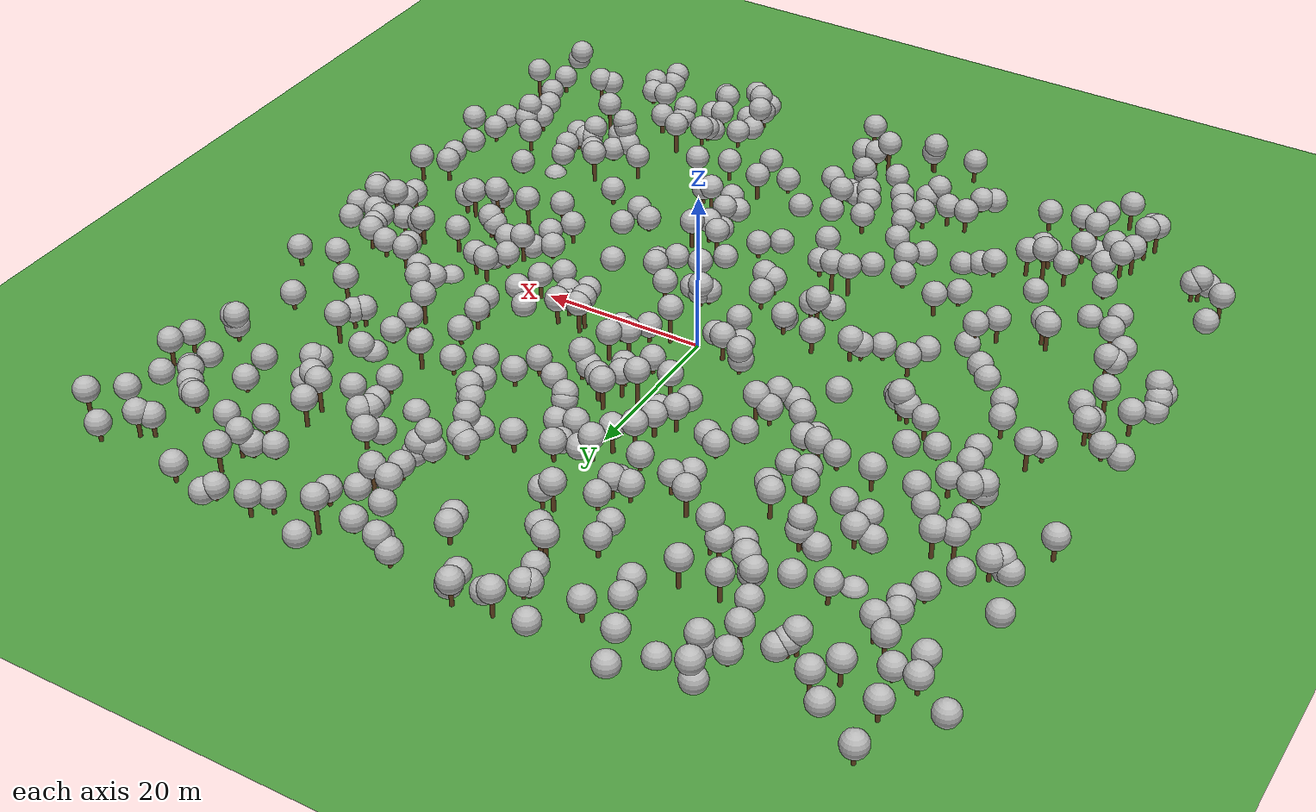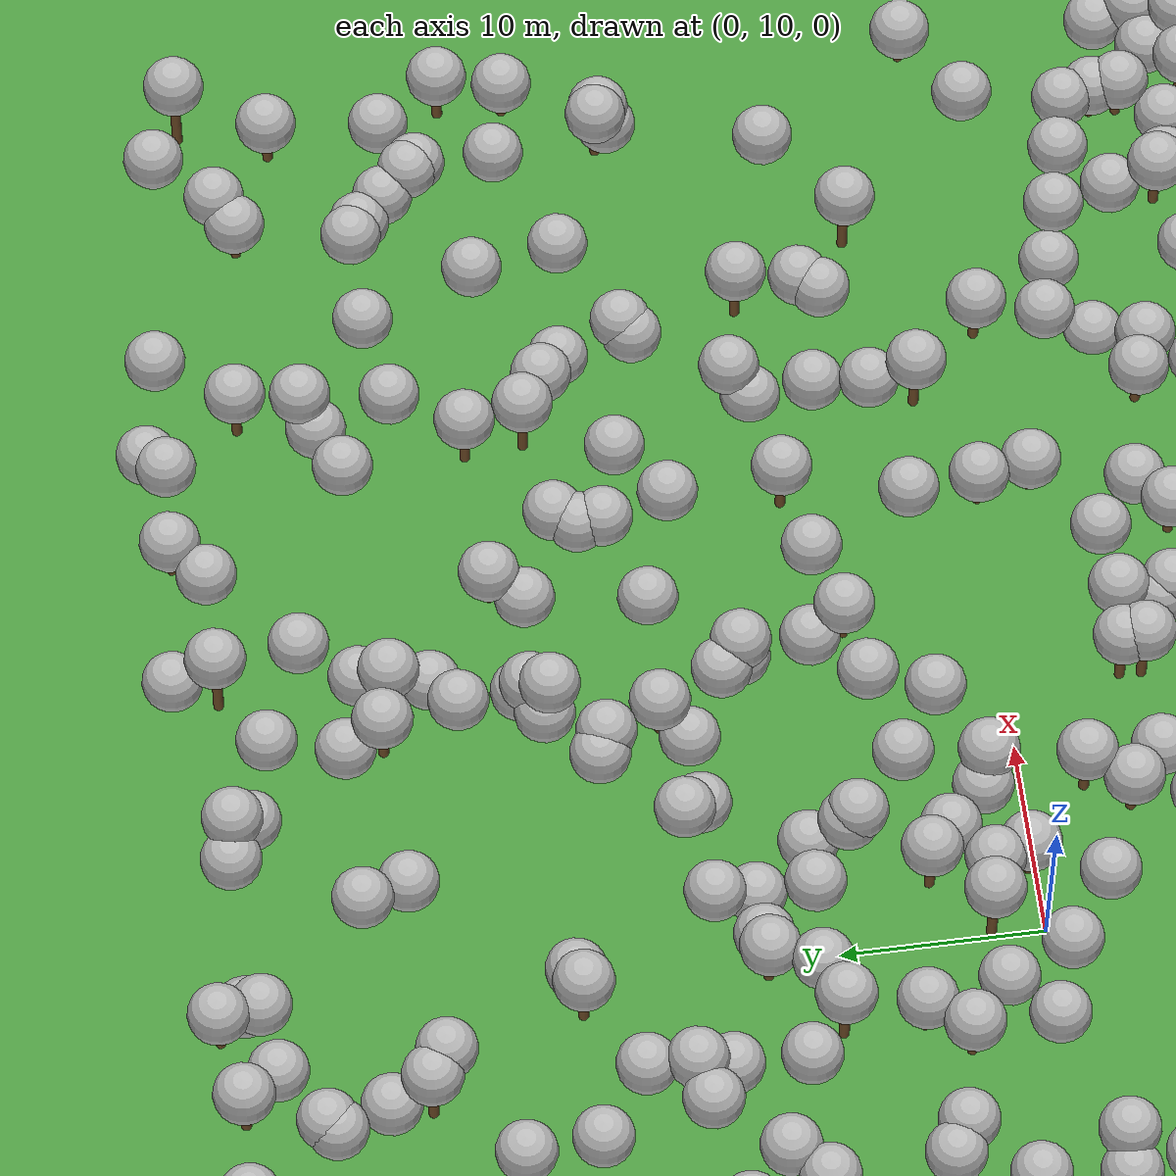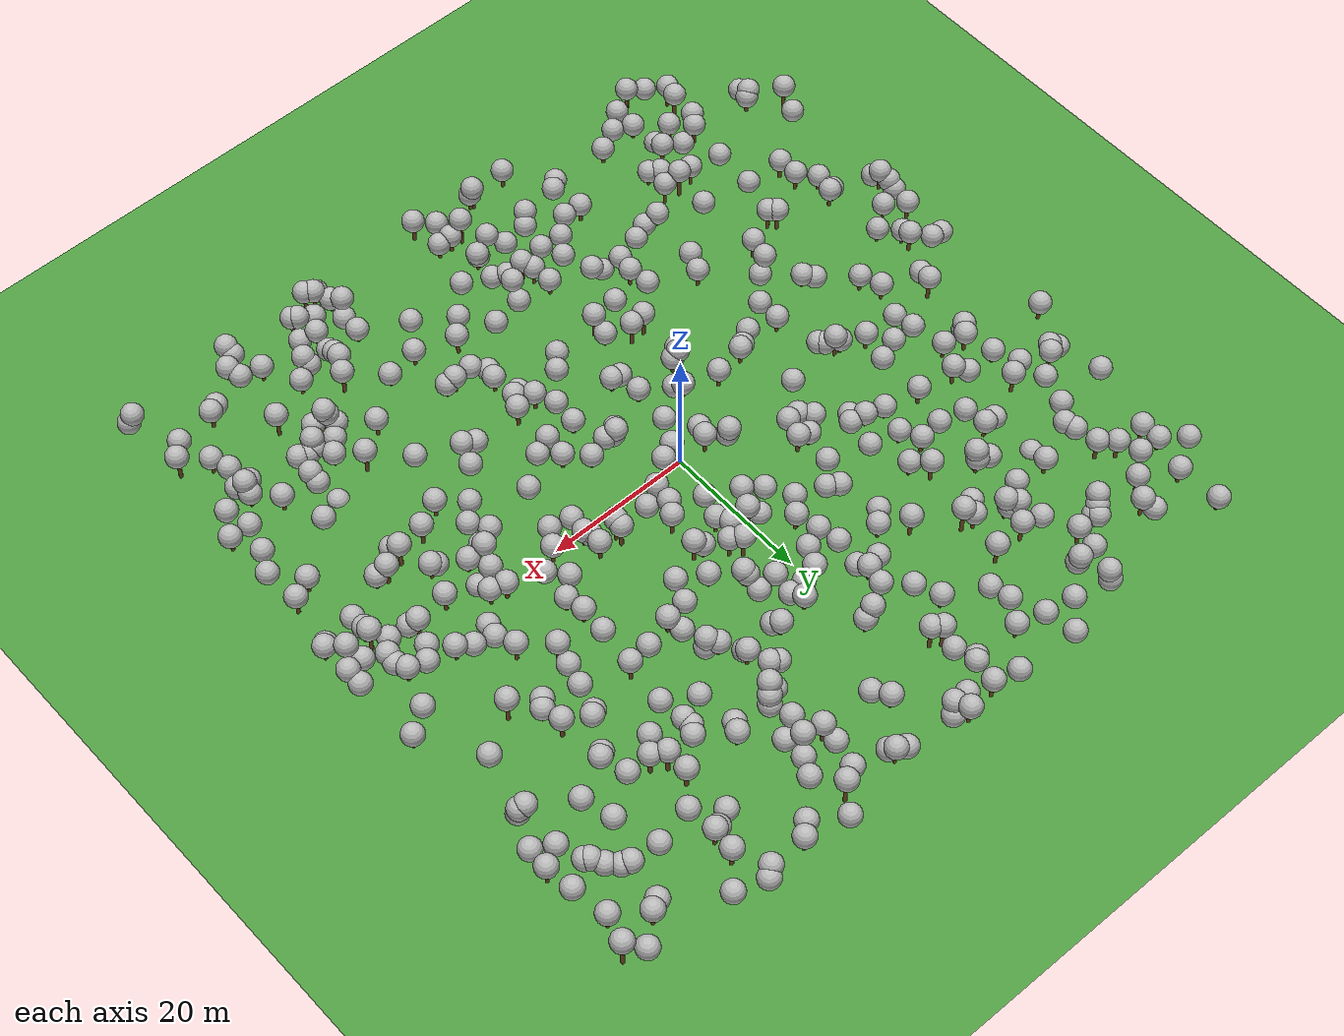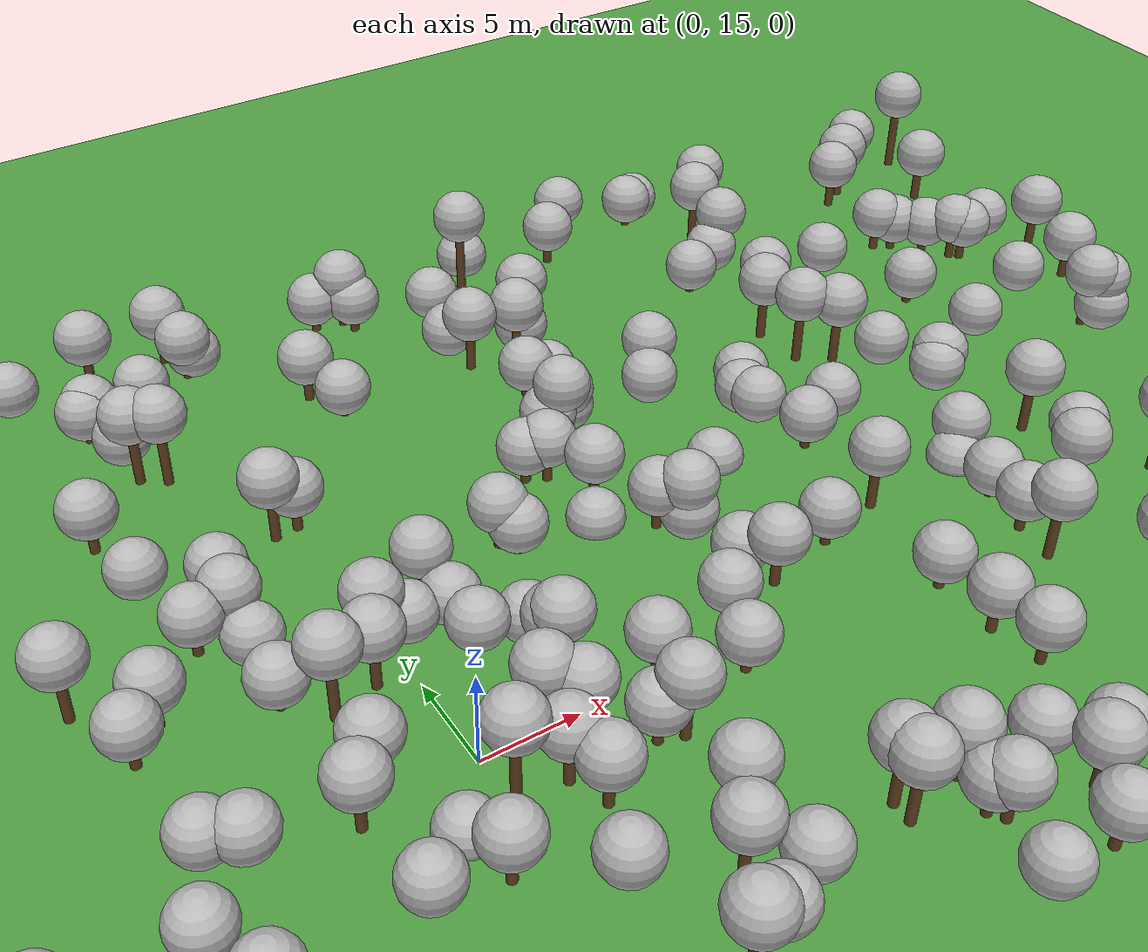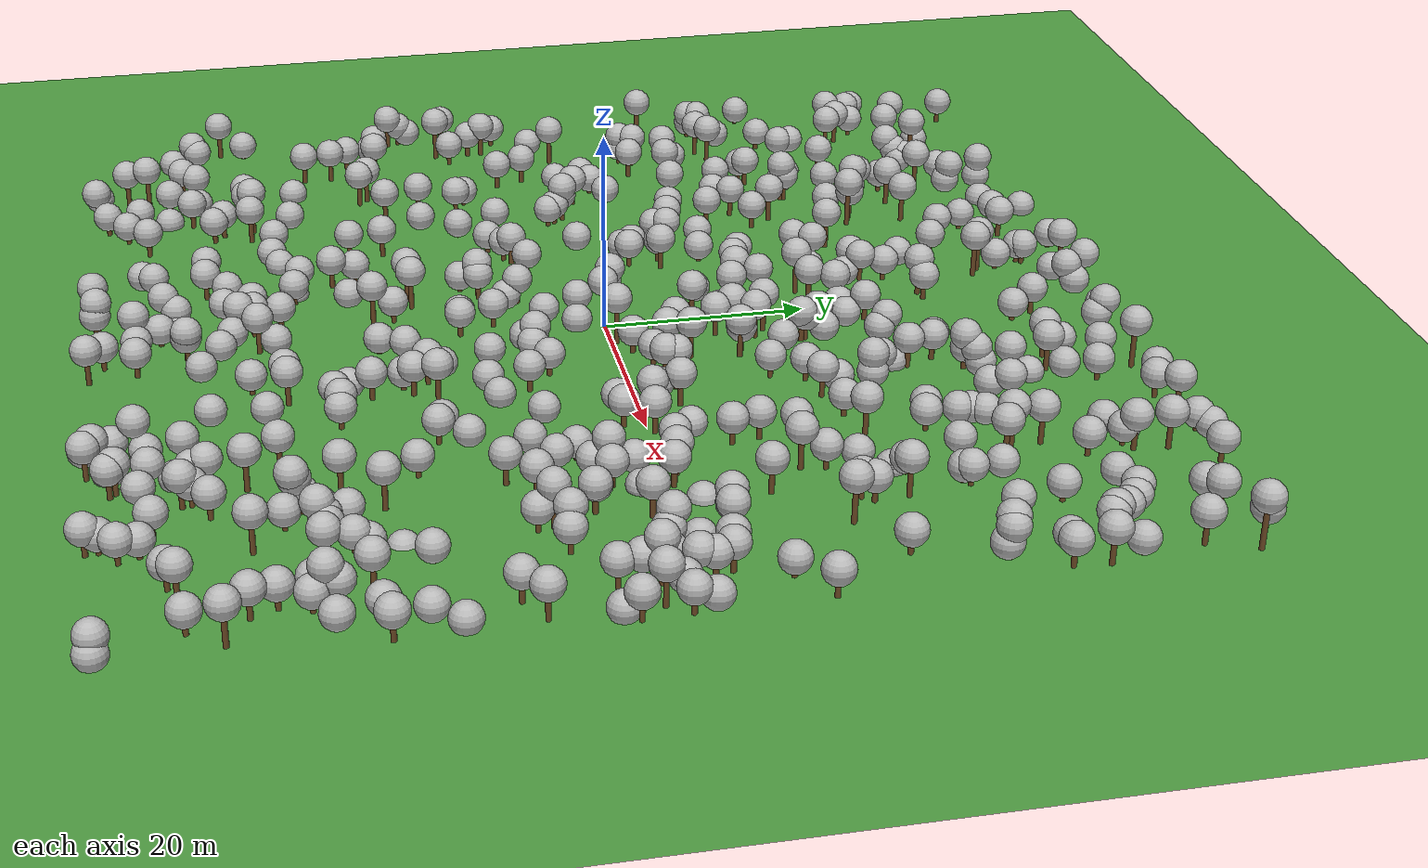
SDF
<sdf version="1.7">
 <world name="default">
  <plugin name="mrs_gazebo_static_transform_republisher_plugin" filename="libMRSGazeboStaticTransformRepublisher.so"/>
  <spherical_coordinates>
   <surface_model>EARTH_WGS84</surface_model>
   <latitude_deg>47.3977</latitude_deg>
   <longitude_deg>8.54559</longitude_deg>
   <elevation>0</elevation>
   <heading_deg>0</heading_deg>
  </spherical_coordinates>
  <physics name="default_physics" default="0" type="ode">
   <ode>
    <solver>
     <type>quick</type>
     <iters>50</iters>
     <sor>1</sor>
     <use_dynamic_moi_rescaling>0</use_dynamic_moi_rescaling>
    </solver>
    <constraints>
     <cfm>0</cfm>
     <erp>0.2</erp>
     <contact_max_correcting_vel>1000</contact_max_correcting_vel>
     <contact_surface_layer>0.001</contact_surface_layer>
    </constraints>
   </ode>
   <max_step_size>0.004</max_step_size>
   <real_time_factor>1</real_time_factor>
   <real_time_update_rate>250</real_time_update_rate>
  </physics>
  <scene><shadows>0</shadows><ambient>0.4 0.4 0.4 1</ambient><background>0.7 0.7 0.7 1</background></scene>
  <light name="sun" type="directional">
   <pose>250 250 600 0 -0 0</pose>
   <diffuse>0.8 0.8 0.8 1</diffuse>
   <specular>0.2 0.2 0.2 1</specular>
   <attenuation>
    <range>1000</range>
    <constant>0.9</constant>
    <linear>0.01</linear>
    <quadratic>0.001</quadratic>
   </attenuation>
   <direction>0 0 -1</direction>
   <spot><inner_angle>0</inner_angle><outer_angle>0</outer_angle><falloff>0</falloff></spot>
  </light>
  <model name="tree_simple499">
   <static>1</static>
   <link name="link">
    <pose>0 0 0.1 0 -0 0</pose>
    <collision name="collision_trunk">
     <pose>0 0 2 0 -0 0</pose>
     <geometry><cylinder><radius>0.25</radius><length>4</length></cylinder></geometry>
    </collision>
    <collision name="collision_treetop">
     <pose>0 0 5.2 0 -0 0</pose>
     <geometry><sphere><radius>1.5</radius></sphere></geometry>
    </collision>
    <visual name="trunk">
     <pose>0 0 2 0 -0 0</pose>
     <geometry><cylinder><radius>0.25</radius><length>4</length></cylinder></geometry>
     <material>
      <script>
       <uri>model://tree_simple/scripts</uri>
       <uri>model://tree_simple/materials/textures</uri>
       <name>TreeSimple/Trunk</name>
      </script>
     </material>
    </visual>
    <visual name="treetop">
     <pose>0 0 5.2 0 -0 0</pose>
     <geometry><sphere><radius>1.5</radius></sphere></geometry>
     <material>
      <script>
       <uri>model://tree_simple/scripts</uri>
       <uri>model://tree_simple/materials/textures</uri>
       <name>TreeSimple/Treetop</name>
      </script>
     </material>
    </visual>
   </link>
   <pose>49.5773 -0.301034 -3.79417 0 -0 0</pose>
  </model>
  <model name="tree_simple498">
   <static>1</static>
   <link name="link">
    <pose>0 0 0.1 0 -0 0</pose>
    <collision name="collision_trunk">
     <pose>0 0 2 0 -0 0</pose>
     <geometry><cylinder><radius>0.25</radius><length>4</length></cylinder></geometry>
    </collision>
    <collision name="collision_treetop">
     <pose>0 0 5.2 0 -0 0</pose>
     <geometry><sphere><radius>1.5</radius></sphere></geometry>
    </collision>
    <visual name="trunk">
     <pose>0 0 2 0 -0 0</pose>
     <geometry><cylinder><radius>0.25</radius><length>4</length></cylinder></geometry>
     <material>
      <script>
       <uri>model://tree_simple/scripts</uri>
       <uri>model://tree_simple/materials/textures</uri>
       <name>TreeSimple/Trunk</name>
      </script>
     </material>
    </visual>
    <visual name="treetop">
     <pose>0 0 5.2 0 -0 0</pose>
     <geometry><sphere><radius>1.5</radius></sphere></geometry>
     <material>
      <script>
       <uri>model://tree_simple/scripts</uri>
       <uri>model://tree_simple/materials/textures</uri>
       <name>TreeSimple/Treetop</name>
      </script>
     </material>
    </visual>
   </link>
   <pose>-20.0621 9.09254 -3.97769 0 -0 0</pose>
  </model>
  <model name="tree_simple497">
   <static>1</static>
   <link name="link">
    <pose>0 0 0.1 0 -0 0</pose>
    <collision name="collision_trunk">
     <pose>0 0 2 0 -0 0</pose>
     <geometry><cylinder><radius>0.25</radius><length>4</length></cylinder></geometry>
    </collision>
    <collision name="collision_treetop">
     <pose>0 0 5.2 0 -0 0</pose>
     <geometry><sphere><radius>1.5</radius></sphere></geometry>
    </collision>
    <visual name="trunk">
     <pose>0 0 2 0 -0 0</pose>
     <geometry><cylinder><radius>0.25</radius><length>4</length></cylinder></geometry>
     <material>
      <script>
       <uri>model://tree_simple/scripts</uri>
       <uri>model://tree_simple/materials/textures</uri>
       <name>TreeSimple/Trunk</name>
      </script>
     </material>
    </visual>
    <visual name="treetop">
     <pose>0 0 5.2 0 -0 0</pose>
     <geometry><sphere><radius>1.5</radius></sphere></geometry>
     <material>
      <script>
       <uri>model://tree_simple/scripts</uri>
       <uri>model://tree_simple/materials/textures</uri>
       <name>TreeSimple/Treetop</name>
      </script>
     </material>
    </visual>
   </link>
   <pose>16.5731 19.0017 -3.75156 0 -0 0</pose>
  </model>
  <model name="tree_simple496">
   <static>1</static>
   <link name="link">
    <pose>0 0 0.1 0 -0 0</pose>
    <collision name="collision_trunk">
     <pose>0 0 2 0 -0 0</pose>
     <geometry><cylinder><radius>0.25</radius><length>4</length></cylinder></geometry>
    </collision>
    <collision name="collision_treetop">
     <pose>0 0 5.2 0 -0 0</pose>
     <geometry><sphere><radius>1.5</radius></sphere></geometry>
    </collision>
    <visual name="trunk">
     <pose>0 0 2 0 -0 0</pose>
     <geometry><cylinder><radius>0.25</radius><length>4</length></cylinder></geometry>
     <material>
      <script>
       <uri>model://tree_simple/scripts</uri>
       <uri>model://tree_simple/materials/textures</uri>
       <name>TreeSimple/Trunk</name>
      </script>
     </material>
    </visual>
    <visual name="treetop">
     <pose>0 0 5.2 0 -0 0</pose>
     <geometry><sphere><radius>1.5</radius></sphere></geometry>
     <material>
      <script>
       <uri>model://tree_simple/scripts</uri>
       <uri>model://tree_simple/materials/textures</uri>
       <name>TreeSimple/Treetop</name>
      </script>
     </material>
    </visual>
   </link>
   <pose>13.6194 -26.9856 -2.56277 0 -0 0</pose>
  </model>
  <model name="tree_simple495">
   <static>1</static>
   <link name="link">
    <pose>0 0 0.1 0 -0 0</pose>
    <collision name="collision_trunk">
     <pose>0 0 2 0 -0 0</pose>
     <geometry><cylinder><radius>0.25</radius><length>4</length></cylinder></geometry>
    </collision>
    <collision name="collision_treetop">
     <pose>0 0 5.2 0 -0 0</pose>
     <geometry><sphere><radius>1.5</radius></sphere></geometry>
    </collision>
    <visual name="trunk">
     <pose>0 0 2 0 -0 0</pose>
     <geometry><cylinder><radius>0.25</radius><length>4</length></cylinder></geometry>
     <material>
      <script>
       <uri>model://tree_simple/scripts</uri>
       <uri>model://tree_simple/materials/textures</uri>
       <name>TreeSimple/Trunk</name>
      </script>
     </material>
    </visual>
    <visual name="treetop">
     <pose>0 0 5.2 0 -0 0</pose>
     <geometry><sphere><radius>1.5</radius></sphere></geometry>
     <material>
      <script>
       <uri>model://tree_simple/scripts</uri>
       <uri>model://tree_simple/materials/textures</uri>
       <name>TreeSimple/Treetop</name>
      </script>
     </material>
    </visual>
   </link>
   <pose>13.2663 3.23501 -1.11258 0 -0 0</pose>
  </model>
  <model name="tree_simple494">
   <static>1</static>
   <link name="link">
    <pose>0 0 0.1 0 -0 0</pose>
    <collision name="collision_trunk">
     <pose>0 0 2 0 -0 0</pose>
     <geometry><cylinder><radius>0.25</radius><length>4</length></cylinder></geometry>
    </collision>
    <collision name="collision_treetop">
     <pose>0 0 5.2 0 -0 0</pose>
     <geometry><sphere><radius>1.5</radius></sphere></geometry>
    </collision>
    <visual name="trunk">
     <pose>0 0 2 0 -0 0</pose>
     <geometry><cylinder><radius>0.25</radius><length>4</length></cylinder></geometry>
     <material>
      <script>
       <uri>model://tree_simple/scripts</uri>
       <uri>model://tree_simple/materials/textures</uri>
       <name>TreeSimple/Trunk</name>
      </script>
     </material>
    </visual>
    <visual name="treetop">
     <pose>0 0 5.2 0 -0 0</pose>
     <geometry><sphere><radius>1.5</radius></sphere></geometry>
     <material>
      <script>
       <uri>model://tree_simple/scripts</uri>
       <uri>model://tree_simple/materials/textures</uri>
       <name>TreeSimple/Treetop</name>
      </script>
     </material>
    </visual>
   </link>
   <pose>39.6521 -42.6479 -2.24383 0 -0 0</pose>
  </model>
  <model name="tree_simple493">
   <static>1</static>
   <link name="link">
    <pose>0 0 0.1 0 -0 0</pose>
    <collision name="collision_trunk">
     <pose>0 0 2 0 -0 0</pose>
     <geometry><cylinder><radius>0.25</radius><length>4</length></cylinder></geometry>
    </collision>
    <collision name="collision_treetop">
     <pose>0 0 5.2 0 -0 0</pose>
     <geometry><sphere><radius>1.5</radius></sphere></geometry>
    </collision>
    <visual name="trunk">
     <pose>0 0 2 0 -0 0</pose>
     <geometry><cylinder><radius>0.25</radius><length>4</length></cylinder></geometry>
     <material>
      <script>
       <uri>model://tree_simple/scripts</uri>
       <uri>model://tree_simple/materials/textures</uri>
       <name>TreeSimple/Trunk</name>
      </script>
     </material>
    </visual>
    <visual name="treetop">
     <pose>0 0 5.2 0 -0 0</pose>
     <geometry><sphere><radius>1.5</radius></sphere></geometry>
     <material>
      <script>
       <uri>model://tree_simple/scripts</uri>
       <uri>model://tree_simple/materials/textures</uri>
       <name>TreeSimple/Treetop</name>
      </script>
     </material>
    </visual>
   </link>
   <pose>-30.9686 18.3944 -3.40292 0 -0 0</pose>
  </model>
  <model name="tree_simple492">
   <static>1</static>
   <link name="link">
    <pose>0 0 0.1 0 -0 0</pose>
    <collision name="collision_trunk">
     <pose>0 0 2 0 -0 0</pose>
     <geometry><cylinder><radius>0.25</radius><length>4</length></cylinder></geometry>
    </collision>
    <collision name="collision_treetop">
     <pose>0 0 5.2 0 -0 0</pose>
     <geometry><sphere><radius>1.5</radius></sphere></geometry>
    </collision>
    <visual name="trunk">
     <pose>0 0 2 0 -0 0</pose>
     <geometry><cylinder><radius>0.25</radius><length>4</length></cylinder></geometry>
     <material>
      <script>
       <uri>model://tree_simple/scripts</uri>
       <uri>model://tree_simple/materials/textures</uri>
       <name>TreeSimple/Trunk</name>
      </script>
     </material>
    </visual>
    <visual name="treetop">
     <pose>0 0 5.2 0 -0 0</pose>
     <geometry><sphere><radius>1.5</radius></sphere></geometry>
     <material>
      <script>
       <uri>model://tree_simple/scripts</uri>
       <uri>model://tree_simple/materials/textures</uri>
       <name>TreeSimple/Treetop</name>
      </script>
     </material>
    </visual>
   </link>
   <pose>-7.60604 27.1336 -2.96977 0 -0 0</pose>
  </model>
  <model name="tree_simple491">
   <static>1</static>
   <link name="link">
    <pose>0 0 0.1 0 -0 0</pose>
    <collision name="collision_trunk">
     <pose>0 0 2 0 -0 0</pose>
     <geometry><cylinder><radius>0.25</radius><length>4</length></cylinder></geometry>
    </collision>
    <collision name="collision_treetop">
     <pose>0 0 5.2 0 -0 0</pose>
     <geometry><sphere><radius>1.5</radius></sphere></geometry>
    </collision>
    <visual name="trunk">
     <pose>0 0 2 0 -0 0</pose>
     <geometry><cylinder><radius>0.25</radius><length>4</length></cylinder></geometry>
     <material>
      <script>
       <uri>model://tree_simple/scripts</uri>
       <uri>model://tree_simple/materials/textures</uri>
       <name>TreeSimple/Trunk</name>
      </script>
     </material>
    </visual>
    <visual name="treetop">
     <pose>0 0 5.2 0 -0 0</pose>
     <geometry><sphere><radius>1.5</radius></sphere></geometry>
     <material>
      <script>
       <uri>model://tree_simple/scripts</uri>
       <uri>model://tree_simple/materials/textures</uri>
       <name>TreeSimple/Treetop</name>
      </script>
     </material>
    </visual>
   </link>
   <pose>-12.3902 -49.1083 -2.42305 0 -0 0</pose>
  </model>
  <model name="tree_simple490">
   <static>1</static>
   <link name="link">
    <pose>0 0 0.1 0 -0 0</pose>
    <collision name="collision_trunk">
     <pose>0 0 2 0 -0 0</pose>
     <geometry><cylinder><radius>0.25</radius><length>4</length></cylinder></geometry>
    </collision>
    <collision name="collision_treetop">
     <pose>0 0 5.2 0 -0 0</pose>
     <geometry><sphere><radius>1.5</radius></sphere></geometry>
    </collision>
    <visual name="trunk">
     <pose>0 0 2 0 -0 0</pose>
     <geometry><cylinder><radius>0.25</radius><length>4</length></cylinder></geometry>
     <material>
      <script>
       <uri>model://tree_simple/scripts</uri>
       <uri>model://tree_simple/materials/textures</uri>
       <name>TreeSimple/Trunk</name>
      </script>
     </material>
    </visual>
    <visual name="treetop">
     <pose>0 0 5.2 0 -0 0</pose>
     <geometry><sphere><radius>1.5</radius></sphere></geometry>
     <material>
      <script>
       <uri>model://tree_simple/scripts</uri>
       <uri>model://tree_simple/materials/textures</uri>
       <name>TreeSimple/Treetop</name>
      </script>
     </material>
    </visual>
   </link>
   <pose>28.4863 0.994684 -2.15347 0 -0 0</pose>
  </model>
  <model name="tree_simple489">
   <static>1</static>
   <link name="link">
    <pose>0 0 0.1 0 -0 0</pose>
    <collision name="collision_trunk">
     <pose>0 0 2 0 -0 0</pose>
     <geometry><cylinder><radius>0.25</radius><length>4</length></cylinder></geometry>
    </collision>
    <collision name="collision_treetop">
     <pose>0 0 5.2 0 -0 0</pose>
     <geometry><sphere><radius>1.5</radius></sphere></geometry>
    </collision>
    <visual name="trunk">
     <pose>0 0 2 0 -0 0</pose>
     <geometry><cylinder><radius>0.25</radius><length>4</length></cylinder></geometry>
     <material>
      <script>
       <uri>model://tree_simple/scripts</uri>
       <uri>model://tree_simple/materials/textures</uri>
       <name>TreeSimple/Trunk</name>
      </script>
     </material>
    </visual>
    <visual name="treetop">
     <pose>0 0 5.2 0 -0 0</pose>
     <geometry><sphere><radius>1.5</radius></sphere></geometry>
     <material>
      <script>
       <uri>model://tree_simple/scripts</uri>
       <uri>model://tree_simple/materials/textures</uri>
       <name>TreeSimple/Treetop</name>
      </script>
     </material>
    </visual>
   </link>
   <pose>-32.6635 39.3278 -3.1328 0 -0 0</pose>
  </model>
  <model name="tree_simple488">
   <static>1</static>
   <link name="link">
    <pose>0 0 0.1 0 -0 0</pose>
    <collision name="collision_trunk">
     <pose>0 0 2 0 -0 0</pose>
     <geometry><cylinder><radius>0.25</radius><length>4</length></cylinder></geometry>
    </collision>
    <collision name="collision_treetop">
     <pose>0 0 5.2 0 -0 0</pose>
     <geometry><sphere><radius>1.5</radius></sphere></geometry>
    </collision>
    <visual name="trunk">
     <pose>0 0 2 0 -0 0</pose>
     <geometry><cylinder><radius>0.25</radius><length>4</length></cylinder></geometry>
     <material>
      <script>
       <uri>model://tree_simple/scripts</uri>
       <uri>model://tree_simple/materials/textures</uri>
       <name>TreeSimple/Trunk</name>
      </script>
     </material>
    </visual>
    <visual name="treetop">
     <pose>0 0 5.2 0 -0 0</pose>
     <geometry><sphere><radius>1.5</radius></sphere></geometry>
     <material>
      <script>
       <uri>model://tree_simple/scripts</uri>
       <uri>model://tree_simple/materials/textures</uri>
       <name>TreeSimple/Treetop</name>
      </script>
     </material>
    </visual>
   </link>
   <pose>-13.1216 12.436 -3.68606 0 -0 0</pose>
  </model>
  <model name="tree_simple487">
   <static>1</static>
   <link name="link">
    <pose>0 0 0.1 0 -0 0</pose>
    <collision name="collision_trunk">
     <pose>0 0 2 0 -0 0</pose>
     <geometry><cylinder><radius>0.25</radius><length>4</length></cylinder></geometry>
    </collision>
    <collision name="collision_treetop">
     <pose>0 0 5.2 0 -0 0</pose>
     <geometry><sphere><radius>1.5</radius></sphere></geometry>
    </collision>
    <visual name="trunk">
     <pose>0 0 2 0 -0 0</pose>
     <geometry><cylinder><radius>0.25</radius><length>4</length></cylinder></geometry>
     <material>
      <script>
       <uri>model://tree_simple/scripts</uri>
       <uri>model://tree_simple/materials/textures</uri>
       <name>TreeSimple/Trunk</name>
      </script>
     </material>
    </visual>
    <visual name="treetop">
     <pose>0 0 5.2 0 -0 0</pose>
     <geometry><sphere><radius>1.5</radius></sphere></geometry>
     <material>
      <script>
       <uri>model://tree_simple/scripts</uri>
       <uri>model://tree_simple/materials/textures</uri>
       <name>TreeSimple/Treetop</name>
      </script>
     </material>
    </visual>
   </link>
   <pose>33.128 8.35332 -1.88528 0 -0 0</pose>
  </model>
  <model name="tree_simple486">
   <static>1</static>
   <link name="link">
    <pose>0 0 0.1 0 -0 0</pose>
    <collision name="collision_trunk">
     <pose>0 0 2 0 -0 0</pose>
     <geometry><cylinder><radius>0.25</radius><length>4</length></cylinder></geometry>
    </collision>
    <collision name="collision_treetop">
     <pose>0 0 5.2 0 -0 0</pose>
     <geometry><sphere><radius>1.5</radius></sphere></geometry>
    </collision>
    <visual name="trunk">
     <pose>0 0 2 0 -0 0</pose>
     <geometry><cylinder><radius>0.25</radius><length>4</length></cylinder></geometry>
     <material>
      <script>
       <uri>model://tree_simple/scripts</uri>
       <uri>model://tree_simple/materials/textures</uri>
       <name>TreeSimple/Trunk</name>
      </script>
     </material>
    </visual>
    <visual name="treetop">
     <pose>0 0 5.2 0 -0 0</pose>
     <geometry><sphere><radius>1.5</radius></sphere></geometry>
     <material>
      <script>
       <uri>model://tree_simple/scripts</uri>
       <uri>model://tree_simple/materials/textures</uri>
       <name>TreeSimple/Treetop</name>
      </script>
     </material>
    </visual>
   </link>
   <pose>8.18282 11.6524 -1.49404 0 -0 0</pose>
  </model>
  <model name="tree_simple485">
   <static>1</static>
   <link name="link">
    <pose>0 0 0.1 0 -0 0</pose>
    <collision name="collision_trunk">
     <pose>0 0 2 0 -0 0</pose>
     <geometry><cylinder><radius>0.25</radius><length>4</length></cylinder></geometry>
    </collision>
    <collision name="collision_treetop">
     <pose>0 0 5.2 0 -0 0</pose>
     <geometry><sphere><radius>1.5</radius></sphere></geometry>
    </collision>
    <visual name="trunk">
     <pose>0 0 2 0 -0 0</pose>
     <geometry><cylinder><radius>0.25</radius><length>4</length></cylinder></geometry>
     <material>
      <script>
       <uri>model://tree_simple/scripts</uri>
       <uri>model://tree_simple/materials/textures</uri>
       <name>TreeSimple/Trunk</name>
      </script>
     </material>
    </visual>
    <visual name="treetop">
     <pose>0 0 5.2 0 -0 0</pose>
     <geometry><sphere><radius>1.5</radius></sphere></geometry>
     <material>
      <script>
       <uri>model://tree_simple/scripts</uri>
       <uri>model://tree_simple/materials/textures</uri>
       <name>TreeSimple/Treetop</name>
      </script>
     </material>
    </visual>
   </link>
   <pose>38.4673 3.60529 -2.50161 0 -0 0</pose>
  </model>
  <model name="tree_simple484">
   <static>1</static>
   <link name="link">
    <pose>0 0 0.1 0 -0 0</pose>
    <collision name="collision_trunk">
     <pose>0 0 2 0 -0 0</pose>
     <geometry><cylinder><radius>0.25</radius><length>4</length></cylinder></geometry>
    </collision>
    <collision name="collision_treetop">
     <pose>0 0 5.2 0 -0 0</pose>
     <geometry><sphere><radius>1.5</radius></sphere></geometry>
    </collision>
    <visual name="trunk">
     <pose>0 0 2 0 -0 0</pose>
     <geometry><cylinder><radius>0.25</radius><length>4</length></cylinder></geometry>
     <material>
      <script>
       <uri>model://tree_simple/scripts</uri>
       <uri>model://tree_simple/materials/textures</uri>
       <name>TreeSimple/Trunk</name>
      </script>
     </material>
    </visual>
    <visual name="treetop">
     <pose>0 0 5.2 0 -0 0</pose>
     <geometry><sphere><radius>1.5</radius></sphere></geometry>
     <material>
      <script>
       <uri>model://tree_simple/scripts</uri>
       <uri>model://tree_simple/materials/textures</uri>
       <name>TreeSimple/Treetop</name>
      </script>
     </material>
    </visual>
   </link>
   <pose>19.8605 -47.9062 -4.91163 0 -0 0</pose>
  </model>
  <model name="tree_simple483">
   <static>1</static>
   <link name="link">
    <pose>0 0 0.1 0 -0 0</pose>
    <collision name="collision_trunk">
     <pose>0 0 2 0 -0 0</pose>
     <geometry><cylinder><radius>0.25</radius><length>4</length></cylinder></geometry>
    </collision>
    <collision name="collision_treetop">
     <pose>0 0 5.2 0 -0 0</pose>
     <geometry><sphere><radius>1.5</radius></sphere></geometry>
    </collision>
    <visual name="trunk">
     <pose>0 0 2 0 -0 0</pose>
     <geometry><cylinder><radius>0.25</radius><length>4</length></cylinder></geometry>
     <material>
      <script>
       <uri>model://tree_simple/scripts</uri>
       <uri>model://tree_simple/materials/textures</uri>
       <name>TreeSimple/Trunk</name>
      </script>
     </material>
    </visual>
    <visual name="treetop">
     <pose>0 0 5.2 0 -0 0</pose>
     <geometry><sphere><radius>1.5</radius></sphere></geometry>
     <material>
      <script>
       <uri>model://tree_simple/scripts</uri>
       <uri>model://tree_simple/materials/textures</uri>
       <name>TreeSimple/Treetop</name>
      </script>
     </material>
    </visual>
   </link>
   <pose>-6.65162 44.7613 -3.48208 0 -0 0</pose>
  </model>
  <model name="tree_simple482">
   <static>1</static>
   <link name="link">
    <pose>0 0 0.1 0 -0 0</pose>
    <collision name="collision_trunk">
     <pose>0 0 2 0 -0 0</pose>
     <geometry><cylinder><radius>0.25</radius><length>4</length></cylinder></geometry>
    </collision>
    <collision name="collision_treetop">
     <pose>0 0 5.2 0 -0 0</pose>
     <geometry><sphere><radius>1.5</radius></sphere></geometry>
    </collision>
    <visual name="trunk">
     <pose>0 0 2 0 -0 0</pose>
     <geometry><cylinder><radius>0.25</radius><length>4</length></cylinder></geometry>
     <material>
      <script>
       <uri>model://tree_simple/scripts</uri>
       <uri>model://tree_simple/materials/textures</uri>
       <name>TreeSimple/Trunk</name>
      </script>
     </material>
    </visual>
    <visual name="treetop">
     <pose>0 0 5.2 0 -0 0</pose>
     <geometry><sphere><radius>1.5</radius></sphere></geometry>
     <material>
      <script>
       <uri>model://tree_simple/scripts</uri>
       <uri>model://tree_simple/materials/textures</uri>
       <name>TreeSimple/Treetop</name>
      </script>
     </material>
    </visual>
   </link>
   <pose>-31.7137 39.685 -4.03417 0 -0 0</pose>
  </model>
  <model name="tree_simple481">
   <static>1</static>
   <link name="link">
    <pose>0 0 0.1 0 -0 0</pose>
    <collision name="collision_trunk">
     <pose>0 0 2 0 -0 0</pose>
     <geometry><cylinder><radius>0.25</radius><length>4</length></cylinder></geometry>
    </collision>
    <collision name="collision_treetop">
     <pose>0 0 5.2 0 -0 0</pose>
     <geometry><sphere><radius>1.5</radius></sphere></geometry>
    </collision>
    <visual name="trunk">
     <pose>0 0 2 0 -0 0</pose>
     <geometry><cylinder><radius>0.25</radius><length>4</length></cylinder></geometry>
     <material>
      <script>
       <uri>model://tree_simple/scripts</uri>
       <uri>model://tree_simple/materials/textures</uri>
       <name>TreeSimple/Trunk</name>
      </script>
     </material>
    </visual>
    <visual name="treetop">
     <pose>0 0 5.2 0 -0 0</pose>
     <geometry><sphere><radius>1.5</radius></sphere></geometry>
     <material>
      <script>
       <uri>model://tree_simple/scripts</uri>
       <uri>model://tree_simple/materials/textures</uri>
       <name>TreeSimple/Treetop</name>
      </script>
     </material>
    </visual>
   </link>
   <pose>-37.2553 -39.474 -1.59025 0 -0 0</pose>
  </model>
  <model name="tree_simple480">
   <static>1</static>
   <link name="link">
    <pose>0 0 0.1 0 -0 0</pose>
    <collision name="collision_trunk">
     <pose>0 0 2 0 -0 0</pose>
     <geometry><cylinder><radius>0.25</radius><length>4</length></cylinder></geometry>
    </collision>
    <collision name="collision_treetop">
     <pose>0 0 5.2 0 -0 0</pose>
     <geometry><sphere><radius>1.5</radius></sphere></geometry>
    </collision>
    <visual name="trunk">
     <pose>0 0 2 0 -0 0</pose>
     <geometry><cylinder><radius>0.25</radius><length>4</length></cylinder></geometry>
     <material>
      <script>
       <uri>model://tree_simple/scripts</uri>
       <uri>model://tree_simple/materials/textures</uri>
       <name>TreeSimple/Trunk</name>
      </script>
     </material>
    </visual>
    <visual name="treetop">
     <pose>0 0 5.2 0 -0 0</pose>
     <geometry><sphere><radius>1.5</radius></sphere></geometry>
     <material>
      <script>
       <uri>model://tree_simple/scripts</uri>
       <uri>model://tree_simple/materials/textures</uri>
       <name>TreeSimple/Treetop</name>
      </script>
     </material>
    </visual>
   </link>
   <pose>-2.16211 12.1351 -5.1352 0 -0 0</pose>
  </model>
  <model name="tree_simple479">
   <static>1</static>
   <link name="link">
    <pose>0 0 0.1 0 -0 0</pose>
    <collision name="collision_trunk">
     <pose>0 0 2 0 -0 0</pose>
     <geometry><cylinder><radius>0.25</radius><length>4</length></cylinder></geometry>
    </collision>
    <collision name="collision_treetop">
     <pose>0 0 5.2 0 -0 0</pose>
     <geometry><sphere><radius>1.5</radius></sphere></geometry>
    </collision>
    <visual name="trunk">
     <pose>0 0 2 0 -0 0</pose>
     <geometry><cylinder><radius>0.25</radius><length>4</length></cylinder></geometry>
     <material>
      <script>
       <uri>model://tree_simple/scripts</uri>
       <uri>model://tree_simple/materials/textures</uri>
       <name>TreeSimple/Trunk</name>
      </script>
     </material>
    </visual>
    <visual name="treetop">
     <pose>0 0 5.2 0 -0 0</pose>
     <geometry><sphere><radius>1.5</radius></sphere></geometry>
     <material>
      <script>
       <uri>model://tree_simple/scripts</uri>
       <uri>model://tree_simple/materials/textures</uri>
       <name>TreeSimple/Treetop</name>
      </script>
     </material>
    </visual>
   </link>
   <pose>-12.2778 22.302 -2.8359 0 -0 0</pose>
  </model>
  <model name="tree_simple478">
   <static>1</static>
   <link name="link">
    <pose>0 0 0.1 0 -0 0</pose>
    <collision name="collision_trunk">
     <pose>0 0 2 0 -0 0</pose>
     <geometry><cylinder><radius>0.25</radius><length>4</length></cylinder></geometry>
    </collision>
    <collision name="collision_treetop">
     <pose>0 0 5.2 0 -0 0</pose>
     <geometry><sphere><radius>1.5</radius></sphere></geometry>
    </collision>
    <visual name="trunk">
     <pose>0 0 2 0 -0 0</pose>
     <geometry><cylinder><radius>0.25</radius><length>4</length></cylinder></geometry>
     <material>
      <script>
       <uri>model://tree_simple/scripts</uri>
       <uri>model://tree_simple/materials/textures</uri>
       <name>TreeSimple/Trunk</name>
      </script>
     </material>
    </visual>
    <visual name="treetop">
     <pose>0 0 5.2 0 -0 0</pose>
     <geometry><sphere><radius>1.5</radius></sphere></geometry>
     <material>
      <script>
       <uri>model://tree_simple/scripts</uri>
       <uri>model://tree_simple/materials/textures</uri>
       <name>TreeSimple/Treetop</name>
      </script>
     </material>
    </visual>
   </link>
   <pose>6.74093 -12.3163 -2.91655 0 -0 0</pose>
  </model>
  <model name="tree_simple477">
   <static>1</static>
   <link name="link">
    <pose>0 0 0.1 0 -0 0</pose>
    <collision name="collision_trunk">
     <pose>0 0 2 0 -0 0</pose>
     <geometry><cylinder><radius>0.25</radius><length>4</length></cylinder></geometry>
    </collision>
    <collision name="collision_treetop">
     <pose>0 0 5.2 0 -0 0</pose>
     <geometry><sphere><radius>1.5</radius></sphere></geometry>
    </collision>
    <visual name="trunk">
     <pose>0 0 2 0 -0 0</pose>
     <geometry><cylinder><radius>0.25</radius><length>4</length></cylinder></geometry>
     <material>
      <script>
       <uri>model://tree_simple/scripts</uri>
       <uri>model://tree_simple/materials/textures</uri>
       <name>TreeSimple/Trunk</name>
      </script>
     </material>
    </visual>
    <visual name="treetop">
     <pose>0 0 5.2 0 -0 0</pose>
     <geometry><sphere><radius>1.5</radius></sphere></geometry>
     <material>
      <script>
       <uri>model://tree_simple/scripts</uri>
       <uri>model://tree_simple/materials/textures</uri>
       <name>TreeSimple/Treetop</name>
      </script>
     </material>
    </visual>
   </link>
   <pose>-0.229271 32.6496 -2.76067 0 -0 0</pose>
  </model>
  <model name="tree_simple476">
   <static>1</static>
   <link name="link">
    <pose>0 0 0.1 0 -0 0</pose>
    <collision name="collision_trunk">
     <pose>0 0 2 0 -0 0</pose>
     <geometry><cylinder><radius>0.25</radius><length>4</length></cylinder></geometry>
    </collision>
    <collision name="collision_treetop">
     <pose>0 0 5.2 0 -0 0</pose>
     <geometry><sphere><radius>1.5</radius></sphere></geometry>
    </collision>
    <visual name="trunk">
     <pose>0 0 2 0 -0 0</pose>
     <geometry><cylinder><radius>0.25</radius><length>4</length></cylinder></geometry>
     <material>
      <script>
       <uri>model://tree_simple/scripts</uri>
       <uri>model://tree_simple/materials/textures</uri>
       <name>TreeSimple/Trunk</name>
      </script>
     </material>
    </visual>
    <visual name="treetop">
     <pose>0 0 5.2 0 -0 0</pose>
     <geometry><sphere><radius>1.5</radius></sphere></geometry>
     <material>
      <script>
       <uri>model://tree_simple/scripts</uri>
       <uri>model://tree_simple/materials/textures</uri>
       <name>TreeSimple/Treetop</name>
      </script>
     </material>
    </visual>
   </link>
   <pose>-40.4906 18.2432 -1.81819 0 -0 0</pose>
  </model>
  <model name="tree_simple475">
   <static>1</static>
   <link name="link">
    <pose>0 0 0.1 0 -0 0</pose>
    <collision name="collision_trunk">
     <pose>0 0 2 0 -0 0</pose>
     <geometry><cylinder><radius>0.25</radius><length>4</length></cylinder></geometry>
    </collision>
    <collision name="collision_treetop">
     <pose>0 0 5.2 0 -0 0</pose>
     <geometry><sphere><radius>1.5</radius></sphere></geometry>
    </collision>
    <visual name="trunk">
     <pose>0 0 2 0 -0 0</pose>
     <geometry><cylinder><radius>0.25</radius><length>4</length></cylinder></geometry>
     <material>
      <script>
       <uri>model://tree_simple/scripts</uri>
       <uri>model://tree_simple/materials/textures</uri>
       <name>TreeSimple/Trunk</name>
      </script>
     </material>
    </visual>
    <visual name="treetop">
     <pose>0 0 5.2 0 -0 0</pose>
     <geometry><sphere><radius>1.5</radius></sphere></geometry>
     <material>
      <script>
       <uri>model://tree_simple/scripts</uri>
       <uri>model://tree_simple/materials/textures</uri>
       <name>TreeSimple/Treetop</name>
      </script>
     </material>
    </visual>
   </link>
   <pose>30.9431 49.7431 -4.09418 0 -0 0</pose>
  </model>
  <model name="tree_simple474">
   <static>1</static>
   <link name="link">
    <pose>0 0 0.1 0 -0 0</pose>
    <collision name="collision_trunk">
     <pose>0 0 2 0 -0 0</pose>
     <geometry><cylinder><radius>0.25</radius><length>4</length></cylinder></geometry>
    </collision>
    <collision name="collision_treetop">
     <pose>0 0 5.2 0 -0 0</pose>
     <geometry><sphere><radius>1.5</radius></sphere></geometry>
    </collision>
    <visual name="trunk">
     <pose>0 0 2 0 -0 0</pose>
     <geometry><cylinder><radius>0.25</radius><length>4</length></cylinder></geometry>
     <material>
      <script>
       <uri>model://tree_simple/scripts</uri>
       <uri>model://tree_simple/materials/textures</uri>
       <name>TreeSimple/Trunk</name>
      </script>
     </material>
    </visual>
    <visual name="treetop">
     <pose>0 0 5.2 0 -0 0</pose>
     <geometry><sphere><radius>1.5</radius></sphere></geometry>
     <material>
      <script>
       <uri>model://tree_simple/scripts</uri>
       <uri>model://tree_simple/materials/textures</uri>
       <name>TreeSimple/Treetop</name>
      </script>
     </material>
    </visual>
   </link>
   <pose>-45.5609 37.389 -2.99745 0 -0 0</pose>
  </model>
  <model name="tree_simple473">
   <static>1</static>
   <link name="link">
    <pose>0 0 0.1 0 -0 0</pose>
    <collision name="collision_trunk">
     <pose>0 0 2 0 -0 0</pose>
     <geometry><cylinder><radius>0.25</radius><length>4</length></cylinder></geometry>
    </collision>
    <collision name="collision_treetop">
     <pose>0 0 5.2 0 -0 0</pose>
     <geometry><sphere><radius>1.5</radius></sphere></geometry>
    </collision>
    <visual name="trunk">
     <pose>0 0 2 0 -0 0</pose>
     <geometry><cylinder><radius>0.25</radius><length>4</length></cylinder></geometry>
     <material>
      <script>
       <uri>model://tree_simple/scripts</uri>
       <uri>model://tree_simple/materials/textures</uri>
       <name>TreeSimple/Trunk</name>
      </script>
     </material>
    </visual>
    <visual name="treetop">
     <pose>0 0 5.2 0 -0 0</pose>
     <geometry><sphere><radius>1.5</radius></sphere></geometry>
     <material>
      <script>
       <uri>model://tree_simple/scripts</uri>
       <uri>model://tree_simple/materials/textures</uri>
       <name>TreeSimple/Treetop</name>
      </script>
     </material>
    </visual>
   </link>
   <pose>35.36 -12.4568 -3.05954 0 -0 0</pose>
  </model>
  <model name="tree_simple472">
   <static>1</static>
   <link name="link">
    <pose>0 0 0.1 0 -0 0</pose>
    <collision name="collision_trunk">
     <pose>0 0 2 0 -0 0</pose>
     <geometry><cylinder><radius>0.25</radius><length>4</length></cylinder></geometry>
    </collision>
    <collision name="collision_treetop">
     <pose>0 0 5.2 0 -0 0</pose>
     <geometry><sphere><radius>1.5</radius></sphere></geometry>
    </collision>
    <visual name="trunk">
     <pose>0 0 2 0 -0 0</pose>
     <geometry><cylinder><radius>0.25</radius><length>4</length></cylinder></geometry>
     <material>
      <script>
       <uri>model://tree_simple/scripts</uri>
       <uri>model://tree_simple/materials/textures</uri>
       <name>TreeSimple/Trunk</name>
      </script>
     </material>
    </visual>
    <visual name="treetop">
     <pose>0 0 5.2 0 -0 0</pose>
     <geometry><sphere><radius>1.5</radius></sphere></geometry>
     <material>
      <script>
       <uri>model://tree_simple/scripts</uri>
       <uri>model://tree_simple/materials/textures</uri>
       <name>TreeSimple/Treetop</name>
      </script>
     </material>
    </visual>
   </link>
   <pose>9.92229 -23.8303 -2.60524 0 -0 0</pose>
  </model>
  <model name="tree_simple471">
   <static>1</static>
   <link name="link">
    <pose>0 0 0.1 0 -0 0</pose>
    <collision name="collision_trunk">
     <pose>0 0 2 0 -0 0</pose>
     <geometry><cylinder><radius>0.25</radius><length>4</length></cylinder></geometry>
    </collision>
    <collision name="collision_treetop">
     <pose>0 0 5.2 0 -0 0</pose>
     <geometry><sphere><radius>1.5</radius></sphere></geometry>
    </collision>
    <visual name="trunk">
     <pose>0 0 2 0 -0 0</pose>
     <geometry><cylinder><radius>0.25</radius><length>4</length></cylinder></geometry>
     <material>
      <script>
       <uri>model://tree_simple/scripts</uri>
       <uri>model://tree_simple/materials/textures</uri>
       <name>TreeSimple/Trunk</name>
      </script>
     </material>
    </visual>
    <visual name="treetop">
     <pose>0 0 5.2 0 -0 0</pose>
     <geometry><sphere><radius>1.5</radius></sphere></geometry>
     <material>
      <script>
       <uri>model://tree_simple/scripts</uri>
       <uri>model://tree_simple/materials/textures</uri>
       <name>TreeSimple/Treetop</name>
      </script>
     </material>
    </visual>
   </link>
   <pose>-4.10985 16.4703 -2.39487 0 -0 0</pose>
  </model>
  <model name="tree_simple470">
   <static>1</static>
   <link name="link">
    <pose>0 0 0.1 0 -0 0</pose>
    <collision name="collision_trunk">
     <pose>0 0 2 0 -0 0</pose>
     <geometry><cylinder><radius>0.25</radius><length>4</length></cylinder></geometry>
    </collision>
    <collision name="collision_treetop">
     <pose>0 0 5.2 0 -0 0</pose>
     <geometry><sphere><radius>1.5</radius></sphere></geometry>
    </collision>
    <visual name="trunk">
     <pose>0 0 2 0 -0 0</pose>
     <geometry><cylinder><radius>0.25</radius><length>4</length></cylinder></geometry>
     <material>
      <script>
       <uri>model://tree_simple/scripts</uri>
       <uri>model://tree_simple/materials/textures</uri>
       <name>TreeSimple/Trunk</name>
      </script>
     </material>
    </visual>
    <visual name="treetop">
     <pose>0 0 5.2 0 -0 0</pose>
     <geometry><sphere><radius>1.5</radius></sphere></geometry>
     <material>
      <script>
       <uri>model://tree_simple/scripts</uri>
       <uri>model://tree_simple/materials/textures</uri>
       <name>TreeSimple/Treetop</name>
      </script>
     </material>
    </visual>
   </link>
   <pose>-42.5419 21.0598 -3.98765 0 -0 0</pose>
  </model>
  <model name="tree_simple469">
   <static>1</static>
   <link name="link">
    <pose>0 0 0.1 0 -0 0</pose>
    <collision name="collision_trunk">
     <pose>0 0 2 0 -0 0</pose>
     <geometry><cylinder><radius>0.25</radius><length>4</length></cylinder></geometry>
    </collision>
    <collision name="collision_treetop">
     <pose>0 0 5.2 0 -0 0</pose>
     <geometry><sphere><radius>1.5</radius></sphere></geometry>
    </collision>
    <visual name="trunk">
     <pose>0 0 2 0 -0 0</pose>
     <geometry><cylinder><radius>0.25</radius><length>4</length></cylinder></geometry>
     <material>
      <script>
       <uri>model://tree_simple/scripts</uri>
       <uri>model://tree_simple/materials/textures</uri>
       <name>TreeSimple/Trunk</name>
      </script>
     </material>
    </visual>
    <visual name="treetop">
     <pose>0 0 5.2 0 -0 0</pose>
     <geometry><sphere><radius>1.5</radius></sphere></geometry>
     <material>
      <script>
       <uri>model://tree_simple/scripts</uri>
       <uri>model://tree_simple/materials/textures</uri>
       <name>TreeSimple/Treetop</name>
      </script>
     </material>
    </visual>
   </link>
   <pose>28.6909 -31.7516 -3.34481 0 -0 0</pose>
  </model>
  <model name="tree_simple468">
   <static>1</static>
   <link name="link">
    <pose>0 0 0.1 0 -0 0</pose>
    <collision name="collision_trunk">
     <pose>0 0 2 0 -0 0</pose>
     <geometry><cylinder><radius>0.25</radius><length>4</length></cylinder></geometry>
    </collision>
    <collision name="collision_treetop">
     <pose>0 0 5.2 0 -0 0</pose>
     <geometry><sphere><radius>1.5</radius></sphere></geometry>
    </collision>
    <visual name="trunk">
     <pose>0 0 2 0 -0 0</pose>
     <geometry><cylinder><radius>0.25</radius><length>4</length></cylinder></geometry>
     <material>
      <script>
       <uri>model://tree_simple/scripts</uri>
       <uri>model://tree_simple/materials/textures</uri>
       <name>TreeSimple/Trunk</name>
      </script>
     </material>
    </visual>
    <visual name="treetop">
     <pose>0 0 5.2 0 -0 0</pose>
     <geometry><sphere><radius>1.5</radius></sphere></geometry>
     <material>
      <script>
       <uri>model://tree_simple/scripts</uri>
       <uri>model://tree_simple/materials/textures</uri>
       <name>TreeSimple/Treetop</name>
      </script>
     </material>
    </visual>
   </link>
   <pose>33.4354 -7.20044 -2.41626 0 -0 0</pose>
  </model>
  <model name="tree_simple467">
   <static>1</static>
   <link name="link">
    <pose>0 0 0.1 0 -0 0</pose>
    <collision name="collision_trunk">
     <pose>0 0 2 0 -0 0</pose>
     <geometry><cylinder><radius>0.25</radius><length>4</length></cylinder></geometry>
    </collision>
    <collision name="collision_treetop">
     <pose>0 0 5.2 0 -0 0</pose>
     <geometry><sphere><radius>1.5</radius></sphere></geometry>
    </collision>
    <visual name="trunk">
     <pose>0 0 2 0 -0 0</pose>
     <geometry><cylinder><radius>0.25</radius><length>4</length></cylinder></geometry>
     <material>
      <script>
       <uri>model://tree_simple/scripts</uri>
       <uri>model://tree_simple/materials/textures</uri>
       <name>TreeSimple/Trunk</name>
      </script>
     </material>
    </visual>
    <visual name="treetop">
     <pose>0 0 5.2 0 -0 0</pose>
     <geometry><sphere><radius>1.5</radius></sphere></geometry>
     <material>
      <script>
       <uri>model://tree_simple/scripts</uri>
       <uri>model://tree_simple/materials/textures</uri>
       <name>TreeSimple/Treetop</name>
      </script>
     </material>
    </visual>
   </link>
   <pose>-38.4436 19.1732 -1.57809 0 -0 0</pose>
  </model>
  <model name="tree_simple466">
   <static>1</static>
   <link name="link">
    <pose>0 0 0.1 0 -0 0</pose>
    <collision name="collision_trunk">
     <pose>0 0 2 0 -0 0</pose>
     <geometry><cylinder><radius>0.25</radius><length>4</length></cylinder></geometry>
    </collision>
    <collision name="collision_treetop">
     <pose>0 0 5.2 0 -0 0</pose>
     <geometry><sphere><radius>1.5</radius></sphere></geometry>
    </collision>
    <visual name="trunk">
     <pose>0 0 2 0 -0 0</pose>
     <geometry><cylinder><radius>0.25</radius><length>4</length></cylinder></geometry>
     <material>
      <script>
       <uri>model://tree_simple/scripts</uri>
       <uri>model://tree_simple/materials/textures</uri>
       <name>TreeSimple/Trunk</name>
      </script>
     </material>
    </visual>
    <visual name="treetop">
     <pose>0 0 5.2 0 -0 0</pose>
     <geometry><sphere><radius>1.5</radius></sphere></geometry>
     <material>
      <script>
       <uri>model://tree_simple/scripts</uri>
       <uri>model://tree_simple/materials/textures</uri>
       <name>TreeSimple/Treetop</name>
      </script>
     </material>
    </visual>
   </link>
   <pose>-5.77987 22.1737 -3.35347 0 -0 0</pose>
  </model>
  <model name="tree_simple465">
   <static>1</static>
   <link name="link">
    <pose>0 0 0.1 0 -0 0</pose>
    <collision name="collision_trunk">
     <pose>0 0 2 0 -0 0</pose>
     <geometry><cylinder><radius>0.25</radius><length>4</length></cylinder></geometry>
    </collision>
    <collision name="collision_treetop">
     <pose>0 0 5.2 0 -0 0</pose>
     <geometry><sphere><radius>1.5</radius></sphere></geometry>
    </collision>
    <visual name="trunk">
     <pose>0 0 2 0 -0 0</pose>
     <geometry><cylinder><radius>0.25</radius><length>4</length></cylinder></geometry>
     <material>
      <script>
       <uri>model://tree_simple/scripts</uri>
       <uri>model://tree_simple/materials/textures</uri>
       <name>TreeSimple/Trunk</name>
      </script>
     </material>
    </visual>
    <visual name="treetop">
     <pose>0 0 5.2 0 -0 0</pose>
     <geometry><sphere><radius>1.5</radius></sphere></geometry>
     <material>
      <script>
       <uri>model://tree_simple/scripts</uri>
       <uri>model://tree_simple/materials/textures</uri>
       <name>TreeSimple/Treetop</name>
      </script>
     </material>
    </visual>
   </link>
   <pose>5.78709 20.6383 -4.22115 0 -0 0</pose>
  </model>
  <model name="tree_simple464">
   <static>1</static>
   <link name="link">
    <pose>0 0 0.1 0 -0 0</pose>
    <collision name="collision_trunk">
     <pose>0 0 2 0 -0 0</pose>
     <geometry><cylinder><radius>0.25</radius><length>4</length></cylinder></geometry>
    </collision>
    <collision name="collision_treetop">
     <pose>0 0 5.2 0 -0 0</pose>
     <geometry><sphere><radius>1.5</radius></sphere></geometry>
    </collision>
    <visual name="trunk">
     <pose>0 0 2 0 -0 0</pose>
     <geometry><cylinder><radius>0.25</radius><length>4</length></cylinder></geometry>
     <material>
      <script>
       <uri>model://tree_simple/scripts</uri>
       <uri>model://tree_simple/materials/textures</uri>
       <name>TreeSimple/Trunk</name>
      </script>
     </material>
    </visual>
    <visual name="treetop">
     <pose>0 0 5.2 0 -0 0</pose>
     <geometry><sphere><radius>1.5</radius></sphere></geometry>
     <material>
      <script>
       <uri>model://tree_simple/scripts</uri>
       <uri>model://tree_simple/materials/textures</uri>
       <name>TreeSimple/Treetop</name>
      </script>
     </material>
    </visual>
   </link>
   <pose>18.6971 -49.1924 -2.0659 0 -0 0</pose>
  </model>
  <model name="tree_simple463">
   <static>1</static>
   <link name="link">
    <pose>0 0 0.1 0 -0 0</pose>
    <collision name="collision_trunk">
     <pose>0 0 2 0 -0 0</pose>
     <geometry><cylinder><radius>0.25</radius><length>4</length></cylinder></geometry>
    </collision>
    <collision name="collision_treetop">
     <pose>0 0 5.2 0 -0 0</pose>
     <geometry><sphere><radius>1.5</radius></sphere></geometry>
    </collision>
    <visual name="trunk">
     <pose>0 0 2 0 -0 0</pose>
     <geometry><cylinder><radius>0.25</radius><length>4</length></cylinder></geometry>
     <material>
      <script>
       <uri>model://tree_simple/scripts</uri>
       <uri>model://tree_simple/materials/textures</uri>
       <name>TreeSimple/Trunk</name>
      </script>
     </material>
    </visual>
    <visual name="treetop">
     <pose>0 0 5.2 0 -0 0</pose>
     <geometry><sphere><radius>1.5</radius></sphere></geometry>
     <material>
      <script>
       <uri>model://tree_simple/scripts</uri>
       <uri>model://tree_simple/materials/textures</uri>
       <name>TreeSimple/Treetop</name>
      </script>
     </material>
    </visual>
   </link>
   <pose>4.14453 -7.71734 -3.63022 0 -0 0</pose>
  </model>
  <model name="tree_simple462">
   <static>1</static>
   <link name="link">
    <pose>0 0 0.1 0 -0 0</pose>
    <collision name="collision_trunk">
     <pose>0 0 2 0 -0 0</pose>
     <geometry><cylinder><radius>0.25</radius><length>4</length></cylinder></geometry>
    </collision>
    <collision name="collision_treetop">
     <pose>0 0 5.2 0 -0 0</pose>
     <geometry><sphere><radius>1.5</radius></sphere></geometry>
    </collision>
    <visual name="trunk">
     <pose>0 0 2 0 -0 0</pose>
     <geometry><cylinder><radius>0.25</radius><length>4</length></cylinder></geometry>
     <material>
      <script>
       <uri>model://tree_simple/scripts</uri>
       <uri>model://tree_simple/materials/textures</uri>
       <name>TreeSimple/Trunk</name>
      </script>
     </material>
    </visual>
    <visual name="treetop">
     <pose>0 0 5.2 0 -0 0</pose>
     <geometry><sphere><radius>1.5</radius></sphere></geometry>
     <material>
      <script>
       <uri>model://tree_simple/scripts</uri>
       <uri>model://tree_simple/materials/textures</uri>
       <name>TreeSimple/Treetop</name>
      </script>
     </material>
    </visual>
   </link>
   <pose>-33.3479 38.601 -2.17219 0 -0 0</pose>
  </model>
  <model name="tree_simple461">
   <static>1</static>
   <link name="link">
    <pose>0 0 0.1 0 -0 0</pose>
    <collision name="collision_trunk">
     <pose>0 0 2 0 -0 0</pose>
     <geometry><cylinder><radius>0.25</radius><length>4</length></cylinder></geometry>
    </collision>
    <collision name="collision_treetop">
     <pose>0 0 5.2 0 -0 0</pose>
     <geometry><sphere><radius>1.5</radius></sphere></geometry>
    </collision>
    <visual name="trunk">
     <pose>0 0 2 0 -0 0</pose>
     <geometry><cylinder><radius>0.25</radius><length>4</length></cylinder></geometry>
     <material>
      <script>
       <uri>model://tree_simple/scripts</uri>
       <uri>model://tree_simple/materials/textures</uri>
       <name>TreeSimple/Trunk</name>
      </script>
     </material>
    </visual>
    <visual name="treetop">
     <pose>0 0 5.2 0 -0 0</pose>
     <geometry><sphere><radius>1.5</radius></sphere></geometry>
     <material>
      <script>
       <uri>model://tree_simple/scripts</uri>
       <uri>model://tree_simple/materials/textures</uri>
       <name>TreeSimple/Treetop</name>
      </script>
     </material>
    </visual>
   </link>
   <pose>48.4584 -13.8276 -1.9506 0 -0 0</pose>
  </model>
  <model name="tree_simple460">
   <static>1</static>
   <link name="link">
    <pose>0 0 0.1 0 -0 0</pose>
    <collision name="collision_trunk">
     <pose>0 0 2 0 -0 0</pose>
     <geometry><cylinder><radius>0.25</radius><length>4</length></cylinder></geometry>
    </collision>
    <collision name="collision_treetop">
     <pose>0 0 5.2 0 -0 0</pose>
     <geometry><sphere><radius>1.5</radius></sphere></geometry>
    </collision>
    <visual name="trunk">
     <pose>0 0 2 0 -0 0</pose>
     <geometry><cylinder><radius>0.25</radius><length>4</length></cylinder></geometry>
     <material>
      <script>
       <uri>model://tree_simple/scripts</uri>
       <uri>model://tree_simple/materials/textures</uri>
       <name>TreeSimple/Trunk</name>
      </script>
     </material>
    </visual>
    <visual name="treetop">
     <pose>0 0 5.2 0 -0 0</pose>
     <geometry><sphere><radius>1.5</radius></sphere></geometry>
     <material>
      <script>
       <uri>model://tree_simple/scripts</uri>
       <uri>model://tree_simple/materials/textures</uri>
       <name>TreeSimple/Treetop</name>
      </script>
     </material>
    </visual>
   </link>
   <pose>-19.1264 10.2733 -3.52867 0 -0 0</pose>
  </model>
  <model name="tree_simple459">
   <static>1</static>
   <link name="link">
    <pose>0 0 0.1 0 -0 0</pose>
    <collision name="collision_trunk">
     <pose>0 0 2 0 -0 0</pose>
     <geometry><cylinder><radius>0.25</radius><length>4</length></cylinder></geometry>
    </collision>
    <collision name="collision_treetop">
     <pose>0 0 5.2 0 -0 0</pose>
     <geometry><sphere><radius>1.5</radius></sphere></geometry>
    </collision>
    <visual name="trunk">
     <pose>0 0 2 0 -0 0</pose>
     <geometry><cylinder><radius>0.25</radius><length>4</length></cylinder></geometry>
     <material>
      <script>
       <uri>model://tree_simple/scripts</uri>
       <uri>model://tree_simple/materials/textures</uri>
       <name>TreeSimple/Trunk</name>
      </script>
     </material>
    </visual>
    <visual name="treetop">
     <pose>0 0 5.2 0 -0 0</pose>
     <geometry><sphere><radius>1.5</radius></sphere></geometry>
     <material>
      <script>
       <uri>model://tree_simple/scripts</uri>
       <uri>model://tree_simple/materials/textures</uri>
       <name>TreeSimple/Treetop</name>
      </script>
     </material>
    </visual>
   </link>
   <pose>23.3051 47.6025 -2.93132 0 -0 0</pose>
  </model>
  <model name="tree_simple458">
   <static>1</static>
   <link name="link">
    <pose>0 0 0.1 0 -0 0</pose>
    <collision name="collision_trunk">
     <pose>0 0 2 0 -0 0</pose>
     <geometry><cylinder><radius>0.25</radius><length>4</length></cylinder></geometry>
    </collision>
    <collision name="collision_treetop">
     <pose>0 0 5.2 0 -0 0</pose>
     <geometry><sphere><radius>1.5</radius></sphere></geometry>
    </collision>
    <visual name="trunk">
     <pose>0 0 2 0 -0 0</pose>
     <geometry><cylinder><radius>0.25</radius><length>4</length></cylinder></geometry>
     <material>
      <script>
       <uri>model://tree_simple/scripts</uri>
       <uri>model://tree_simple/materials/textures</uri>
       <name>TreeSimple/Trunk</name>
      </script>
     </material>
    </visual>
    <visual name="treetop">
     <pose>0 0 5.2 0 -0 0</pose>
     <geometry><sphere><radius>1.5</radius></sphere></geometry>
     <material>
      <script>
       <uri>model://tree_simple/scripts</uri>
       <uri>model://tree_simple/materials/textures</uri>
       <name>TreeSimple/Treetop</name>
      </script>
     </material>
    </visual>
   </link>
   <pose>2.06614 -49.6676 -1.8399 0 -0 0</pose>
  </model>
  <model name="tree_simple457">
   <static>1</static>
   <link name="link">
    <pose>0 0 0.1 0 -0 0</pose>
    <collision name="collision_trunk">
     <pose>0 0 2 0 -0 0</pose>
     <geometry><cylinder><radius>0.25</radius><length>4</length></cylinder></geometry>
    </collision>
    <collision name="collision_treetop">
     <pose>0 0 5.2 0 -0 0</pose>
     <geometry><sphere><radius>1.5</radius></sphere></geometry>
    </collision>
    <visual name="trunk">
     <pose>0 0 2 0 -0 0</pose>
     <geometry><cylinder><radius>0.25</radius><length>4</length></cylinder></geometry>
     <material>
      <script>
       <uri>model://tree_simple/scripts</uri>
       <uri>model://tree_simple/materials/textures</uri>
       <name>TreeSimple/Trunk</name>
      </script>
     </material>
    </visual>
    <visual name="treetop">
     <pose>0 0 5.2 0 -0 0</pose>
     <geometry><sphere><radius>1.5</radius></sphere></geometry>
     <material>
      <script>
       <uri>model://tree_simple/scripts</uri>
       <uri>model://tree_simple/materials/textures</uri>
       <name>TreeSimple/Treetop</name>
      </script>
     </material>
    </visual>
   </link>
   <pose>13.2866 26.7985 -2.34496 0 -0 0</pose>
  </model>
  <model name="tree_simple456">
   <static>1</static>
   <link name="link">
    <pose>0 0 0.1 0 -0 0</pose>
    <collision name="collision_trunk">
     <pose>0 0 2 0 -0 0</pose>
     <geometry><cylinder><radius>0.25</radius><length>4</length></cylinder></geometry>
    </collision>
    <collision name="collision_treetop">
     <pose>0 0 5.2 0 -0 0</pose>
     <geometry><sphere><radius>1.5</radius></sphere></geometry>
    </collision>
    <visual name="trunk">
     <pose>0 0 2 0 -0 0</pose>
     <geometry><cylinder><radius>0.25</radius><length>4</length></cylinder></geometry>
     <material>
      <script>
       <uri>model://tree_simple/scripts</uri>
       <uri>model://tree_simple/materials/textures</uri>
       <name>TreeSimple/Trunk</name>
      </script>
     </material>
    </visual>
    <visual name="treetop">
     <pose>0 0 5.2 0 -0 0</pose>
     <geometry><sphere><radius>1.5</radius></sphere></geometry>
     <material>
      <script>
       <uri>model://tree_simple/scripts</uri>
       <uri>model://tree_simple/materials/textures</uri>
       <name>TreeSimple/Treetop</name>
      </script>
     </material>
    </visual>
   </link>
   <pose>23.2077 -47.8592 -2.47613 0 -0 0</pose>
  </model>
  <model name="tree_simple455">
   <static>1</static>
   <link name="link">
    <pose>0 0 0.1 0 -0 0</pose>
    <collision name="collision_trunk">
     <pose>0 0 2 0 -0 0</pose>
     <geometry><cylinder><radius>0.25</radius><length>4</length></cylinder></geometry>
    </collision>
    <collision name="collision_treetop">
     <pose>0 0 5.2 0 -0 0</pose>
     <geometry><sphere><radius>1.5</radius></sphere></geometry>
    </collision>
    <visual name="trunk">
     <pose>0 0 2 0 -0 0</pose>
     <geometry><cylinder><radius>0.25</radius><length>4</length></cylinder></geometry>
     <material>
      <script>
       <uri>model://tree_simple/scripts</uri>
       <uri>model://tree_simple/materials/textures</uri>
       <name>TreeSimple/Trunk</name>
      </script>
     </material>
    </visual>
    <visual name="treetop">
     <pose>0 0 5.2 0 -0 0</pose>
     <geometry><sphere><radius>1.5</radius></sphere></geometry>
     <material>
      <script>
       <uri>model://tree_simple/scripts</uri>
       <uri>model://tree_simple/materials/textures</uri>
       <name>TreeSimple/Treetop</name>
      </script>
     </material>
    </visual>
   </link>
   <pose>-32.1347 4.45624 -3.67909 0 -0 0</pose>
  </model>
  <model name="tree_simple454">
   <static>1</static>
   <link name="link">
    <pose>0 0 0.1 0 -0 0</pose>
    <collision name="collision_trunk">
     <pose>0 0 2 0 -0 0</pose>
     <geometry><cylinder><radius>0.25</radius><length>4</length></cylinder></geometry>
    </collision>
    <collision name="collision_treetop">
     <pose>0 0 5.2 0 -0 0</pose>
     <geometry><sphere><radius>1.5</radius></sphere></geometry>
    </collision>
    <visual name="trunk">
     <pose>0 0 2 0 -0 0</pose>
     <geometry><cylinder><radius>0.25</radius><length>4</length></cylinder></geometry>
     <material>
      <script>
       <uri>model://tree_simple/scripts</uri>
       <uri>model://tree_simple/materials/textures</uri>
       <name>TreeSimple/Trunk</name>
      </script>
     </material>
    </visual>
    <visual name="treetop">
     <pose>0 0 5.2 0 -0 0</pose>
     <geometry><sphere><radius>1.5</radius></sphere></geometry>
     <material>
      <script>
       <uri>model://tree_simple/scripts</uri>
       <uri>model://tree_simple/materials/textures</uri>
       <name>TreeSimple/Treetop</name>
      </script>
     </material>
    </visual>
   </link>
   <pose>-1.19782 -40.4261 -3.09497 0 -0 0</pose>
  </model>
  <model name="tree_simple453">
   <static>1</static>
   <link name="link">
    <pose>0 0 0.1 0 -0 0</pose>
    <collision name="collision_trunk">
     <pose>0 0 2 0 -0 0</pose>
     <geometry><cylinder><radius>0.25</radius><length>4</length></cylinder></geometry>
    </collision>
    <collision name="collision_treetop">
     <pose>0 0 5.2 0 -0 0</pose>
     <geometry><sphere><radius>1.5</radius></sphere></geometry>
    </collision>
    <visual name="trunk">
     <pose>0 0 2 0 -0 0</pose>
     <geometry><cylinder><radius>0.25</radius><length>4</length></cylinder></geometry>
     <material>
      <script>
       <uri>model://tree_simple/scripts</uri>
       <uri>model://tree_simple/materials/textures</uri>
       <name>TreeSimple/Trunk</name>
      </script>
     </material>
    </visual>
    <visual name="treetop">
     <pose>0 0 5.2 0 -0 0</pose>
     <geometry><sphere><radius>1.5</radius></sphere></geometry>
     <material>
      <script>
       <uri>model://tree_simple/scripts</uri>
       <uri>model://tree_simple/materials/textures</uri>
       <name>TreeSimple/Treetop</name>
      </script>
     </material>
    </visual>
   </link>
   <pose>-12.1353 8.19022 -2.05042 0 -0 0</pose>
  </model>
  <model name="tree_simple452">
   <static>1</static>
   <link name="link">
    <pose>0 0 0.1 0 -0 0</pose>
    <collision name="collision_trunk">
     <pose>0 0 2 0 -0 0</pose>
     <geometry><cylinder><radius>0.25</radius><length>4</length></cylinder></geometry>
    </collision>
    <collision name="collision_treetop">
     <pose>0 0 5.2 0 -0 0</pose>
     <geometry><sphere><radius>1.5</radius></sphere></geometry>
    </collision>
    <visual name="trunk">
     <pose>0 0 2 0 -0 0</pose>
     <geometry><cylinder><radius>0.25</radius><length>4</length></cylinder></geometry>
     <material>
      <script>
       <uri>model://tree_simple/scripts</uri>
       <uri>model://tree_simple/materials/textures</uri>
       <name>TreeSimple/Trunk</name>
      </script>
     </material>
    </visual>
    <visual name="treetop">
     <pose>0 0 5.2 0 -0 0</pose>
     <geometry><sphere><radius>1.5</radius></sphere></geometry>
     <material>
      <script>
       <uri>model://tree_simple/scripts</uri>
       <uri>model://tree_simple/materials/textures</uri>
       <name>TreeSimple/Treetop</name>
      </script>
     </material>
    </visual>
   </link>
   <pose>21.4882 34.0286 -2.62857 0 -0 0</pose>
  </model>
  <model name="tree_simple451">
   <static>1</static>
   <link name="link">
    <pose>0 0 0.1 0 -0 0</pose>
    <collision name="collision_trunk">
     <pose>0 0 2 0 -0 0</pose>
     <geometry><cylinder><radius>0.25</radius><length>4</length></cylinder></geometry>
    </collision>
    <collision name="collision_treetop">
     <pose>0 0 5.2 0 -0 0</pose>
     <geometry><sphere><radius>1.5</radius></sphere></geometry>
    </collision>
    <visual name="trunk">
     <pose>0 0 2 0 -0 0</pose>
     <geometry><cylinder><radius>0.25</radius><length>4</length></cylinder></geometry>
     <material>
      <script>
       <uri>model://tree_simple/scripts</uri>
       <uri>model://tree_simple/materials/textures</uri>
       <name>TreeSimple/Trunk</name>
      </script>
     </material>
    </visual>
    <visual name="treetop">
     <pose>0 0 5.2 0 -0 0</pose>
     <geometry><sphere><radius>1.5</radius></sphere></geometry>
     <material>
      <script>
       <uri>model://tree_simple/scripts</uri>
       <uri>model://tree_simple/materials/textures</uri>
       <name>TreeSimple/Treetop</name>
      </script>
     </material>
    </visual>
   </link>
   <pose>25.0881 -28.1508 -2.22169 0 -0 0</pose>
  </model>
  <model name="tree_simple450">
   <static>1</static>
   <link name="link">
    <pose>0 0 0.1 0 -0 0</pose>
    <collision name="collision_trunk">
     <pose>0 0 2 0 -0 0</pose>
     <geometry><cylinder><radius>0.25</radius><length>4</length></cylinder></geometry>
    </collision>
    <collision name="collision_treetop">
     <pose>0 0 5.2 0 -0 0</pose>
     <geometry><sphere><radius>1.5</radius></sphere></geometry>
    </collision>
    <visual name="trunk">
     <pose>0 0 2 0 -0 0</pose>
     <geometry><cylinder><radius>0.25</radius><length>4</length></cylinder></geometry>
     <material>
      <script>
       <uri>model://tree_simple/scripts</uri>
       <uri>model://tree_simple/materials/textures</uri>
       <name>TreeSimple/Trunk</name>
      </script>
     </material>
    </visual>
    <visual name="treetop">
     <pose>0 0 5.2 0 -0 0</pose>
     <geometry><sphere><radius>1.5</radius></sphere></geometry>
     <material>
      <script>
       <uri>model://tree_simple/scripts</uri>
       <uri>model://tree_simple/materials/textures</uri>
       <name>TreeSimple/Treetop</name>
      </script>
     </material>
    </visual>
   </link>
   <pose>16.0273 22.5149 -3.99483 0 -0 0</pose>
  </model>
  <model name="tree_simple449">
   <static>1</static>
   <link name="link">
    <pose>0 0 0.1 0 -0 0</pose>
    <collision name="collision_trunk">
     <pose>0 0 2 0 -0 0</pose>
     <geometry><cylinder><radius>0.25</radius><length>4</length></cylinder></geometry>
    </collision>
    <collision name="collision_treetop">
     <pose>0 0 5.2 0 -0 0</pose>
     <geometry><sphere><radius>1.5</radius></sphere></geometry>
    </collision>
    <visual name="trunk">
     <pose>0 0 2 0 -0 0</pose>
     <geometry><cylinder><radius>0.25</radius><length>4</length></cylinder></geometry>
     <material>
      <script>
       <uri>model://tree_simple/scripts</uri>
       <uri>model://tree_simple/materials/textures</uri>
       <name>TreeSimple/Trunk</name>
      </script>
     </material>
    </visual>
    <visual name="treetop">
     <pose>0 0 5.2 0 -0 0</pose>
     <geometry><sphere><radius>1.5</radius></sphere></geometry>
     <material>
      <script>
       <uri>model://tree_simple/scripts</uri>
       <uri>model://tree_simple/materials/textures</uri>
       <name>TreeSimple/Treetop</name>
      </script>
     </material>
    </visual>
   </link>
   <pose>32.2301 37.5842 -3.06763 0 -0 0</pose>
  </model>
  <model name="tree_simple448">
   <static>1</static>
   <link name="link">
    <pose>0 0 0.1 0 -0 0</pose>
    <collision name="collision_trunk">
     <pose>0 0 2 0 -0 0</pose>
     <geometry><cylinder><radius>0.25</radius><length>4</length></cylinder></geometry>
    </collision>
    <collision name="collision_treetop">
     <pose>0 0 5.2 0 -0 0</pose>
     <geometry><sphere><radius>1.5</radius></sphere></geometry>
    </collision>
    <visual name="trunk">
     <pose>0 0 2 0 -0 0</pose>
     <geometry><cylinder><radius>0.25</radius><length>4</length></cylinder></geometry>
     <material>
      <script>
       <uri>model://tree_simple/scripts</uri>
       <uri>model://tree_simple/materials/textures</uri>
       <name>TreeSimple/Trunk</name>
      </script>
     </material>
    </visual>
    <visual name="treetop">
     <pose>0 0 5.2 0 -0 0</pose>
     <geometry><sphere><radius>1.5</radius></sphere></geometry>
     <material>
      <script>
       <uri>model://tree_simple/scripts</uri>
       <uri>model://tree_simple/materials/textures</uri>
       <name>TreeSimple/Treetop</name>
      </script>
     </material>
    </visual>
   </link>
   <pose>-24.552 -1.42547 -3.47936 0 -0 0</pose>
  </model>
  <model name="tree_simple447">
   <static>1</static>
   <link name="link">
    <pose>0 0 0.1 0 -0 0</pose>
    <collision name="collision_trunk">
     <pose>0 0 2 0 -0 0</pose>
     <geometry><cylinder><radius>0.25</radius><length>4</length></cylinder></geometry>
    </collision>
    <collision name="collision_treetop">
     <pose>0 0 5.2 0 -0 0</pose>
     <geometry><sphere><radius>1.5</radius></sphere></geometry>
    </collision>
    <visual name="trunk">
     <pose>0 0 2 0 -0 0</pose>
     <geometry><cylinder><radius>0.25</radius><length>4</length></cylinder></geometry>
     <material>
      <script>
       <uri>model://tree_simple/scripts</uri>
       <uri>model://tree_simple/materials/textures</uri>
       <name>TreeSimple/Trunk</name>
      </script>
     </material>
    </visual>
    <visual name="treetop">
     <pose>0 0 5.2 0 -0 0</pose>
     <geometry><sphere><radius>1.5</radius></sphere></geometry>
     <material>
      <script>
       <uri>model://tree_simple/scripts</uri>
       <uri>model://tree_simple/materials/textures</uri>
       <name>TreeSimple/Treetop</name>
      </script>
     </material>
    </visual>
   </link>
   <pose>-6.15097 -41.0423 -5.00073 0 -0 0</pose>
  </model>
  <model name="tree_simple446">
   <static>1</static>
   <link name="link">
    <pose>0 0 0.1 0 -0 0</pose>
    <collision name="collision_trunk">
     <pose>0 0 2 0 -0 0</pose>
     <geometry><cylinder><radius>0.25</radius><length>4</length></cylinder></geometry>
    </collision>
    <collision name="collision_treetop">
     <pose>0 0 5.2 0 -0 0</pose>
     <geometry><sphere><radius>1.5</radius></sphere></geometry>
    </collision>
    <visual name="trunk">
     <pose>0 0 2 0 -0 0</pose>
     <geometry><cylinder><radius>0.25</radius><length>4</length></cylinder></geometry>
     <material>
      <script>
       <uri>model://tree_simple/scripts</uri>
       <uri>model://tree_simple/materials/textures</uri>
       <name>TreeSimple/Trunk</name>
      </script>
     </material>
    </visual>
    <visual name="treetop">
     <pose>0 0 5.2 0 -0 0</pose>
     <geometry><sphere><radius>1.5</radius></sphere></geometry>
     <material>
      <script>
       <uri>model://tree_simple/scripts</uri>
       <uri>model://tree_simple/materials/textures</uri>
       <name>TreeSimple/Treetop</name>
      </script>
     </material>
    </visual>
   </link>
   <pose>-14.8874 38.8089 -3.65914 0 -0 0</pose>
  </model>
  <model name="tree_simple445">
   <static>1</static>
   <link name="link">
    <pose>0 0 0.1 0 -0 0</pose>
    <collision name="collision_trunk">
     <pose>0 0 2 0 -0 0</pose>
     <geometry><cylinder><radius>0.25</radius><length>4</length></cylinder></geometry>
    </collision>
    <collision name="collision_treetop">
     <pose>0 0 5.2 0 -0 0</pose>
     <geometry><sphere><radius>1.5</radius></sphere></geometry>
    </collision>
    <visual name="trunk">
     <pose>0 0 2 0 -0 0</pose>
     <geometry><cylinder><radius>0.25</radius><length>4</length></cylinder></geometry>
     <material>
      <script>
       <uri>model://tree_simple/scripts</uri>
       <uri>model://tree_simple/materials/textures</uri>
       <name>TreeSimple/Trunk</name>
      </script>
     </material>
    </visual>
    <visual name="treetop">
     <pose>0 0 5.2 0 -0 0</pose>
     <geometry><sphere><radius>1.5</radius></sphere></geometry>
     <material>
      <script>
       <uri>model://tree_simple/scripts</uri>
       <uri>model://tree_simple/materials/textures</uri>
       <name>TreeSimple/Treetop</name>
      </script>
     </material>
    </visual>
   </link>
   <pose>17.3331 47.7478 -0.525276 0 -0 0</pose>
  </model>
  <model name="tree_simple444">
   <static>1</static>
   <link name="link">
    <pose>0 0 0.1 0 -0 0</pose>
    <collision name="collision_trunk">
     <pose>0 0 2 0 -0 0</pose>
     <geometry><cylinder><radius>0.25</radius><length>4</length></cylinder></geometry>
    </collision>
    <collision name="collision_treetop">
     <pose>0 0 5.2 0 -0 0</pose>
     <geometry><sphere><radius>1.5</radius></sphere></geometry>
    </collision>
    <visual name="trunk">
     <pose>0 0 2 0 -0 0</pose>
     <geometry><cylinder><radius>0.25</radius><length>4</length></cylinder></geometry>
     <material>
      <script>
       <uri>model://tree_simple/scripts</uri>
       <uri>model://tree_simple/materials/textures</uri>
       <name>TreeSimple/Trunk</name>
      </script>
     </material>
    </visual>
    <visual name="treetop">
     <pose>0 0 5.2 0 -0 0</pose>
     <geometry><sphere><radius>1.5</radius></sphere></geometry>
     <material>
      <script>
       <uri>model://tree_simple/scripts</uri>
       <uri>model://tree_simple/materials/textures</uri>
       <name>TreeSimple/Treetop</name>
      </script>
     </material>
    </visual>
   </link>
   <pose>-23.7376 11.4826 -3.24475 0 -0 0</pose>
  </model>
  <model name="tree_simple443">
   <static>1</static>
   <link name="link">
    <pose>0 0 0.1 0 -0 0</pose>
    <collision name="collision_trunk">
     <pose>0 0 2 0 -0 0</pose>
     <geometry><cylinder><radius>0.25</radius><length>4</length></cylinder></geometry>
    </collision>
    <collision name="collision_treetop">
     <pose>0 0 5.2 0 -0 0</pose>
     <geometry><sphere><radius>1.5</radius></sphere></geometry>
    </collision>
    <visual name="trunk">
     <pose>0 0 2 0 -0 0</pose>
     <geometry><cylinder><radius>0.25</radius><length>4</length></cylinder></geometry>
     <material>
      <script>
       <uri>model://tree_simple/scripts</uri>
       <uri>model://tree_simple/materials/textures</uri>
       <name>TreeSimple/Trunk</name>
      </script>
     </material>
    </visual>
    <visual name="treetop">
     <pose>0 0 5.2 0 -0 0</pose>
     <geometry><sphere><radius>1.5</radius></sphere></geometry>
     <material>
      <script>
       <uri>model://tree_simple/scripts</uri>
       <uri>model://tree_simple/materials/textures</uri>
       <name>TreeSimple/Treetop</name>
      </script>
     </material>
    </visual>
   </link>
   <pose>20.4518 32.4373 -3.69726 0 -0 0</pose>
  </model>
  <model name="tree_simple442">
   <static>1</static>
   <link name="link">
    <pose>0 0 0.1 0 -0 0</pose>
    <collision name="collision_trunk">
     <pose>0 0 2 0 -0 0</pose>
     <geometry><cylinder><radius>0.25</radius><length>4</length></cylinder></geometry>
    </collision>
    <collision name="collision_treetop">
     <pose>0 0 5.2 0 -0 0</pose>
     <geometry><sphere><radius>1.5</radius></sphere></geometry>
    </collision>
    <visual name="trunk">
     <pose>0 0 2 0 -0 0</pose>
     <geometry><cylinder><radius>0.25</radius><length>4</length></cylinder></geometry>
     <material>
      <script>
       <uri>model://tree_simple/scripts</uri>
       <uri>model://tree_simple/materials/textures</uri>
       <name>TreeSimple/Trunk</name>
      </script>
     </material>
    </visual>
    <visual name="treetop">
     <pose>0 0 5.2 0 -0 0</pose>
     <geometry><sphere><radius>1.5</radius></sphere></geometry>
     <material>
      <script>
       <uri>model://tree_simple/scripts</uri>
       <uri>model://tree_simple/materials/textures</uri>
       <name>TreeSimple/Treetop</name>
      </script>
     </material>
    </visual>
   </link>
   <pose>-1.68249 21.1094 -1.81407 0 -0 0</pose>
  </model>
  <model name="tree_simple441">
   <static>1</static>
   <link name="link">
    <pose>0 0 0.1 0 -0 0</pose>
    <collision name="collision_trunk">
     <pose>0 0 2 0 -0 0</pose>
     <geometry><cylinder><radius>0.25</radius><length>4</length></cylinder></geometry>
    </collision>
    <collision name="collision_treetop">
     <pose>0 0 5.2 0 -0 0</pose>
     <geometry><sphere><radius>1.5</radius></sphere></geometry>
    </collision>
    <visual name="trunk">
     <pose>0 0 2 0 -0 0</pose>
     <geometry><cylinder><radius>0.25</radius><length>4</length></cylinder></geometry>
     <material>
      <script>
       <uri>model://tree_simple/scripts</uri>
       <uri>model://tree_simple/materials/textures</uri>
       <name>TreeSimple/Trunk</name>
      </script>
     </material>
    </visual>
    <visual name="treetop">
     <pose>0 0 5.2 0 -0 0</pose>
     <geometry><sphere><radius>1.5</radius></sphere></geometry>
     <material>
      <script>
       <uri>model://tree_simple/scripts</uri>
       <uri>model://tree_simple/materials/textures</uri>
       <name>TreeSimple/Treetop</name>
      </script>
     </material>
    </visual>
   </link>
   <pose>-25.4259 33.0017 -2.14202 0 -0 0</pose>
  </model>
  <model name="tree_simple440">
   <static>1</static>
   <link name="link">
    <pose>0 0 0.1 0 -0 0</pose>
    <collision name="collision_trunk">
     <pose>0 0 2 0 -0 0</pose>
     <geometry><cylinder><radius>0.25</radius><length>4</length></cylinder></geometry>
    </collision>
    <collision name="collision_treetop">
     <pose>0 0 5.2 0 -0 0</pose>
     <geometry><sphere><radius>1.5</radius></sphere></geometry>
    </collision>
    <visual name="trunk">
     <pose>0 0 2 0 -0 0</pose>
     <geometry><cylinder><radius>0.25</radius><length>4</length></cylinder></geometry>
     <material>
      <script>
       <uri>model://tree_simple/scripts</uri>
       <uri>model://tree_simple/materials/textures</uri>
       <name>TreeSimple/Trunk</name>
      </script>
     </material>
    </visual>
    <visual name="treetop">
     <pose>0 0 5.2 0 -0 0</pose>
     <geometry><sphere><radius>1.5</radius></sphere></geometry>
     <material>
      <script>
       <uri>model://tree_simple/scripts</uri>
       <uri>model://tree_simple/materials/textures</uri>
       <name>TreeSimple/Treetop</name>
      </script>
     </material>
    </visual>
   </link>
   <pose>-31.014 21.7755 -2.51993 0 -0 0</pose>
  </model>
  <model name="tree_simple439">
   <static>1</static>
   <link name="link">
    <pose>0 0 0.1 0 -0 0</pose>
    <collision name="collision_trunk">
     <pose>0 0 2 0 -0 0</pose>
     <geometry><cylinder><radius>0.25</radius><length>4</length></cylinder></geometry>
    </collision>
    <collision name="collision_treetop">
     <pose>0 0 5.2 0 -0 0</pose>
     <geometry><sphere><radius>1.5</radius></sphere></geometry>
    </collision>
    <visual name="trunk">
     <pose>0 0 2 0 -0 0</pose>
     <geometry><cylinder><radius>0.25</radius><length>4</length></cylinder></geometry>
     <material>
      <script>
       <uri>model://tree_simple/scripts</uri>
       <uri>model://tree_simple/materials/textures</uri>
       <name>TreeSimple/Trunk</name>
      </script>
     </material>
    </visual>
    <visual name="treetop">
     <pose>0 0 5.2 0 -0 0</pose>
     <geometry><sphere><radius>1.5</radius></sphere></geometry>
     <material>
      <script>
       <uri>model://tree_simple/scripts</uri>
       <uri>model://tree_simple/materials/textures</uri>
       <name>TreeSimple/Treetop</name>
      </script>
     </material>
    </visual>
   </link>
   <pose>8.56501 -20.7641 -3.57656 0 -0 0</pose>
  </model>
  <model name="tree_simple438">
   <static>1</static>
   <link name="link">
    <pose>0 0 0.1 0 -0 0</pose>
    <collision name="collision_trunk">
     <pose>0 0 2 0 -0 0</pose>
     <geometry><cylinder><radius>0.25</radius><length>4</length></cylinder></geometry>
    </collision>
    <collision name="collision_treetop">
     <pose>0 0 5.2 0 -0 0</pose>
     <geometry><sphere><radius>1.5</radius></sphere></geometry>
    </collision>
    <visual name="trunk">
     <pose>0 0 2 0 -0 0</pose>
     <geometry><cylinder><radius>0.25</radius><length>4</length></cylinder></geometry>
     <material>
      <script>
       <uri>model://tree_simple/scripts</uri>
       <uri>model://tree_simple/materials/textures</uri>
       <name>TreeSimple/Trunk</name>
      </script>
     </material>
    </visual>
    <visual name="treetop">
     <pose>0 0 5.2 0 -0 0</pose>
     <geometry><sphere><radius>1.5</radius></sphere></geometry>
     <material>
      <script>
       <uri>model://tree_simple/scripts</uri>
       <uri>model://tree_simple/materials/textures</uri>
       <name>TreeSimple/Treetop</name>
      </script>
     </material>
    </visual>
   </link>
   <pose>-34.2898 -38.004 -4.01416 0 -0 0</pose>
  </model>
  <model name="tree_simple437">
   <static>1</static>
   <link name="link">
    <pose>0 0 0.1 0 -0 0</pose>
    <collision name="collision_trunk">
     <pose>0 0 2 0 -0 0</pose>
     <geometry><cylinder><radius>0.25</radius><length>4</length></cylinder></geometry>
    </collision>
    <collision name="collision_treetop">
     <pose>0 0 5.2 0 -0 0</pose>
     <geometry><sphere><radius>1.5</radius></sphere></geometry>
    </collision>
    <visual name="trunk">
     <pose>0 0 2 0 -0 0</pose>
     <geometry><cylinder><radius>0.25</radius><length>4</length></cylinder></geometry>
     <material>
      <script>
       <uri>model://tree_simple/scripts</uri>
       <uri>model://tree_simple/materials/textures</uri>
       <name>TreeSimple/Trunk</name>
      </script>
     </material>
    </visual>
    <visual name="treetop">
     <pose>0 0 5.2 0 -0 0</pose>
     <geometry><sphere><radius>1.5</radius></sphere></geometry>
     <material>
      <script>
       <uri>model://tree_simple/scripts</uri>
       <uri>model://tree_simple/materials/textures</uri>
       <name>TreeSimple/Treetop</name>
      </script>
     </material>
    </visual>
   </link>
   <pose>-39.717 9.24665 -2.22874 0 -0 0</pose>
  </model>
  <model name="tree_simple436">
   <static>1</static>
   <link name="link">
    <pose>0 0 0.1 0 -0 0</pose>
    <collision name="collision_trunk">
     <pose>0 0 2 0 -0 0</pose>
     <geometry><cylinder><radius>0.25</radius><length>4</length></cylinder></geometry>
    </collision>
    <collision name="collision_treetop">
     <pose>0 0 5.2 0 -0 0</pose>
     <geometry><sphere><radius>1.5</radius></sphere></geometry>
    </collision>
    <visual name="trunk">
     <pose>0 0 2 0 -0 0</pose>
     <geometry><cylinder><radius>0.25</radius><length>4</length></cylinder></geometry>
     <material>
      <script>
       <uri>model://tree_simple/scripts</uri>
       <uri>model://tree_simple/materials/textures</uri>
       <name>TreeSimple/Trunk</name>
      </script>
     </material>
    </visual>
    <visual name="treetop">
     <pose>0 0 5.2 0 -0 0</pose>
     <geometry><sphere><radius>1.5</radius></sphere></geometry>
     <material>
      <script>
       <uri>model://tree_simple/scripts</uri>
       <uri>model://tree_simple/materials/textures</uri>
       <name>TreeSimple/Treetop</name>
      </script>
     </material>
    </visual>
   </link>
   <pose>-12.9774 44.9895 -2.54678 0 -0 0</pose>
  </model>
  <model name="tree_simple435">
   <static>1</static>
   <link name="link">
    <pose>0 0 0.1 0 -0 0</pose>
    <collision name="collision_trunk">
     <pose>0 0 2 0 -0 0</pose>
     <geometry><cylinder><radius>0.25</radius><length>4</length></cylinder></geometry>
    </collision>
    <collision name="collision_treetop">
     <pose>0 0 5.2 0 -0 0</pose>
     <geometry><sphere><radius>1.5</radius></sphere></geometry>
    </collision>
    <visual name="trunk">
     <pose>0 0 2 0 -0 0</pose>
     <geometry><cylinder><radius>0.25</radius><length>4</length></cylinder></geometry>
     <material>
      <script>
       <uri>model://tree_simple/scripts</uri>
       <uri>model://tree_simple/materials/textures</uri>
       <name>TreeSimple/Trunk</name>
      </script>
     </material>
    </visual>
    <visual name="treetop">
     <pose>0 0 5.2 0 -0 0</pose>
     <geometry><sphere><radius>1.5</radius></sphere></geometry>
     <material>
      <script>
       <uri>model://tree_simple/scripts</uri>
       <uri>model://tree_simple/materials/textures</uri>
       <name>TreeSimple/Treetop</name>
      </script>
     </material>
    </visual>
   </link>
   <pose>25.0533 49.1626 -2.44093 0 -0 0</pose>
  </model>
  <model name="tree_simple434">
   <static>1</static>
   <link name="link">
    <pose>0 0 0.1 0 -0 0</pose>
    <collision name="collision_trunk">
     <pose>0 0 2 0 -0 0</pose>
     <geometry><cylinder><radius>0.25</radius><length>4</length></cylinder></geometry>
    </collision>
    <collision name="collision_treetop">
     <pose>0 0 5.2 0 -0 0</pose>
     <geometry><sphere><radius>1.5</radius></sphere></geometry>
    </collision>
    <visual name="trunk">
     <pose>0 0 2 0 -0 0</pose>
     <geometry><cylinder><radius>0.25</radius><length>4</length></cylinder></geometry>
     <material>
      <script>
       <uri>model://tree_simple/scripts</uri>
       <uri>model://tree_simple/materials/textures</uri>
       <name>TreeSimple/Trunk</name>
      </script>
     </material>
    </visual>
    <visual name="treetop">
     <pose>0 0 5.2 0 -0 0</pose>
     <geometry><sphere><radius>1.5</radius></sphere></geometry>
     <material>
      <script>
       <uri>model://tree_simple/scripts</uri>
       <uri>model://tree_simple/materials/textures</uri>
       <name>TreeSimple/Treetop</name>
      </script>
     </material>
    </visual>
   </link>
   <pose>-43.1297 -18.5304 -2.94582 0 -0 0</pose>
  </model>
  <model name="tree_simple433">
   <static>1</static>
   <link name="link">
    <pose>0 0 0.1 0 -0 0</pose>
    <collision name="collision_trunk">
     <pose>0 0 2 0 -0 0</pose>
     <geometry><cylinder><radius>0.25</radius><length>4</length></cylinder></geometry>
    </collision>
    <collision name="collision_treetop">
     <pose>0 0 5.2 0 -0 0</pose>
     <geometry><sphere><radius>1.5</radius></sphere></geometry>
    </collision>
    <visual name="trunk">
     <pose>0 0 2 0 -0 0</pose>
     <geometry><cylinder><radius>0.25</radius><length>4</length></cylinder></geometry>
     <material>
      <script>
       <uri>model://tree_simple/scripts</uri>
       <uri>model://tree_simple/materials/textures</uri>
       <name>TreeSimple/Trunk</name>
      </script>
     </material>
    </visual>
    <visual name="treetop">
     <pose>0 0 5.2 0 -0 0</pose>
     <geometry><sphere><radius>1.5</radius></sphere></geometry>
     <material>
      <script>
       <uri>model://tree_simple/scripts</uri>
       <uri>model://tree_simple/materials/textures</uri>
       <name>TreeSimple/Treetop</name>
      </script>
     </material>
    </visual>
   </link>
   <pose>-27.0164 -36.6076 -3.02726 0 -0 0</pose>
  </model>
  <model name="tree_simple432">
   <static>1</static>
   <link name="link">
    <pose>0 0 0.1 0 -0 0</pose>
    <collision name="collision_trunk">
     <pose>0 0 2 0 -0 0</pose>
     <geometry><cylinder><radius>0.25</radius><length>4</length></cylinder></geometry>
    </collision>
    <collision name="collision_treetop">
     <pose>0 0 5.2 0 -0 0</pose>
     <geometry><sphere><radius>1.5</radius></sphere></geometry>
    </collision>
    <visual name="trunk">
     <pose>0 0 2 0 -0 0</pose>
     <geometry><cylinder><radius>0.25</radius><length>4</length></cylinder></geometry>
     <material>
      <script>
       <uri>model://tree_simple/scripts</uri>
       <uri>model://tree_simple/materials/textures</uri>
       <name>TreeSimple/Trunk</name>
      </script>
     </material>
    </visual>
    <visual name="treetop">
     <pose>0 0 5.2 0 -0 0</pose>
     <geometry><sphere><radius>1.5</radius></sphere></geometry>
     <material>
      <script>
       <uri>model://tree_simple/scripts</uri>
       <uri>model://tree_simple/materials/textures</uri>
       <name>TreeSimple/Treetop</name>
      </script>
     </material>
    </visual>
   </link>
   <pose>8.39658 -6.88849 -3.11199 0 -0 0</pose>
  </model>
  <model name="tree_simple431">
   <static>1</static>
   <link name="link">
    <pose>0 0 0.1 0 -0 0</pose>
    <collision name="collision_trunk">
     <pose>0 0 2 0 -0 0</pose>
     <geometry><cylinder><radius>0.25</radius><length>4</length></cylinder></geometry>
    </collision>
    <collision name="collision_treetop">
     <pose>0 0 5.2 0 -0 0</pose>
     <geometry><sphere><radius>1.5</radius></sphere></geometry>
    </collision>
    <visual name="trunk">
     <pose>0 0 2 0 -0 0</pose>
     <geometry><cylinder><radius>0.25</radius><length>4</length></cylinder></geometry>
     <material>
      <script>
       <uri>model://tree_simple/scripts</uri>
       <uri>model://tree_simple/materials/textures</uri>
       <name>TreeSimple/Trunk</name>
      </script>
     </material>
    </visual>
    <visual name="treetop">
     <pose>0 0 5.2 0 -0 0</pose>
     <geometry><sphere><radius>1.5</radius></sphere></geometry>
     <material>
      <script>
       <uri>model://tree_simple/scripts</uri>
       <uri>model://tree_simple/materials/textures</uri>
       <name>TreeSimple/Treetop</name>
      </script>
     </material>
    </visual>
   </link>
   <pose>21.2092 3.93897 -4.55692 0 -0 0</pose>
  </model>
  <model name="tree_simple430">
   <static>1</static>
   <link name="link">
    <pose>0 0 0.1 0 -0 0</pose>
    <collision name="collision_trunk">
     <pose>0 0 2 0 -0 0</pose>
     <geometry><cylinder><radius>0.25</radius><length>4</length></cylinder></geometry>
    </collision>
    <collision name="collision_treetop">
     <pose>0 0 5.2 0 -0 0</pose>
     <geometry><sphere><radius>1.5</radius></sphere></geometry>
    </collision>
    <visual name="trunk">
     <pose>0 0 2 0 -0 0</pose>
     <geometry><cylinder><radius>0.25</radius><length>4</length></cylinder></geometry>
     <material>
      <script>
       <uri>model://tree_simple/scripts</uri>
       <uri>model://tree_simple/materials/textures</uri>
       <name>TreeSimple/Trunk</name>
      </script>
     </material>
    </visual>
    <visual name="treetop">
     <pose>0 0 5.2 0 -0 0</pose>
     <geometry><sphere><radius>1.5</radius></sphere></geometry>
     <material>
      <script>
       <uri>model://tree_simple/scripts</uri>
       <uri>model://tree_simple/materials/textures</uri>
       <name>TreeSimple/Treetop</name>
      </script>
     </material>
    </visual>
   </link>
   <pose>19.6675 -49.8829 -2.12216 0 -0 0</pose>
  </model>
  <model name="tree_simple429">
   <static>1</static>
   <link name="link">
    <pose>0 0 0.1 0 -0 0</pose>
    <collision name="collision_trunk">
     <pose>0 0 2 0 -0 0</pose>
     <geometry><cylinder><radius>0.25</radius><length>4</length></cylinder></geometry>
    </collision>
    <collision name="collision_treetop">
     <pose>0 0 5.2 0 -0 0</pose>
     <geometry><sphere><radius>1.5</radius></sphere></geometry>
    </collision>
    <visual name="trunk">
     <pose>0 0 2 0 -0 0</pose>
     <geometry><cylinder><radius>0.25</radius><length>4</length></cylinder></geometry>
     <material>
      <script>
       <uri>model://tree_simple/scripts</uri>
       <uri>model://tree_simple/materials/textures</uri>
       <name>TreeSimple/Trunk</name>
      </script>
     </material>
    </visual>
    <visual name="treetop">
     <pose>0 0 5.2 0 -0 0</pose>
     <geometry><sphere><radius>1.5</radius></sphere></geometry>
     <material>
      <script>
       <uri>model://tree_simple/scripts</uri>
       <uri>model://tree_simple/materials/textures</uri>
       <name>TreeSimple/Treetop</name>
      </script>
     </material>
    </visual>
   </link>
   <pose>29.4727 -24.7358 -1.28628 0 -0 0</pose>
  </model>
  <model name="tree_simple428">
   <static>1</static>
   <link name="link">
    <pose>0 0 0.1 0 -0 0</pose>
    <collision name="collision_trunk">
     <pose>0 0 2 0 -0 0</pose>
     <geometry><cylinder><radius>0.25</radius><length>4</length></cylinder></geometry>
    </collision>
    <collision name="collision_treetop">
     <pose>0 0 5.2 0 -0 0</pose>
     <geometry><sphere><radius>1.5</radius></sphere></geometry>
    </collision>
    <visual name="trunk">
     <pose>0 0 2 0 -0 0</pose>
     <geometry><cylinder><radius>0.25</radius><length>4</length></cylinder></geometry>
     <material>
      <script>
       <uri>model://tree_simple/scripts</uri>
       <uri>model://tree_simple/materials/textures</uri>
       <name>TreeSimple/Trunk</name>
      </script>
     </material>
    </visual>
    <visual name="treetop">
     <pose>0 0 5.2 0 -0 0</pose>
     <geometry><sphere><radius>1.5</radius></sphere></geometry>
     <material>
      <script>
       <uri>model://tree_simple/scripts</uri>
       <uri>model://tree_simple/materials/textures</uri>
       <name>TreeSimple/Treetop</name>
      </script>
     </material>
    </visual>
   </link>
   <pose>9.87664 -19.9509 -2.39562 0 -0 0</pose>
  </model>
  <model name="tree_simple427">
   <static>1</static>
   <link name="link">
    <pose>0 0 0.1 0 -0 0</pose>
    <collision name="collision_trunk">
     <pose>0 0 2 0 -0 0</pose>
     <geometry><cylinder><radius>0.25</radius><length>4</length></cylinder></geometry>
    </collision>
    <collision name="collision_treetop">
     <pose>0 0 5.2 0 -0 0</pose>
     <geometry><sphere><radius>1.5</radius></sphere></geometry>
    </collision>
    <visual name="trunk">
     <pose>0 0 2 0 -0 0</pose>
     <geometry><cylinder><radius>0.25</radius><length>4</length></cylinder></geometry>
     <material>
      <script>
       <uri>model://tree_simple/scripts</uri>
       <uri>model://tree_simple/materials/textures</uri>
       <name>TreeSimple/Trunk</name>
      </script>
     </material>
    </visual>
    <visual name="treetop">
     <pose>0 0 5.2 0 -0 0</pose>
     <geometry><sphere><radius>1.5</radius></sphere></geometry>
     <material>
      <script>
       <uri>model://tree_simple/scripts</uri>
       <uri>model://tree_simple/materials/textures</uri>
       <name>TreeSimple/Treetop</name>
      </script>
     </material>
    </visual>
   </link>
   <pose>17.822 -41.375 -3.11146 0 -0 0</pose>
  </model>
  <model name="tree_simple426">
   <static>1</static>
   <link name="link">
    <pose>0 0 0.1 0 -0 0</pose>
    <collision name="collision_trunk">
     <pose>0 0 2 0 -0 0</pose>
     <geometry><cylinder><radius>0.25</radius><length>4</length></cylinder></geometry>
    </collision>
    <collision name="collision_treetop">
     <pose>0 0 5.2 0 -0 0</pose>
     <geometry><sphere><radius>1.5</radius></sphere></geometry>
    </collision>
    <visual name="trunk">
     <pose>0 0 2 0 -0 0</pose>
     <geometry><cylinder><radius>0.25</radius><length>4</length></cylinder></geometry>
     <material>
      <script>
       <uri>model://tree_simple/scripts</uri>
       <uri>model://tree_simple/materials/textures</uri>
       <name>TreeSimple/Trunk</name>
      </script>
     </material>
    </visual>
    <visual name="treetop">
     <pose>0 0 5.2 0 -0 0</pose>
     <geometry><sphere><radius>1.5</radius></sphere></geometry>
     <material>
      <script>
       <uri>model://tree_simple/scripts</uri>
       <uri>model://tree_simple/materials/textures</uri>
       <name>TreeSimple/Treetop</name>
      </script>
     </material>
    </visual>
   </link>
   <pose>48.2961 36.1952 -3.83175 0 -0 0</pose>
  </model>
  <model name="tree_simple425">
   <static>1</static>
   <link name="link">
    <pose>0 0 0.1 0 -0 0</pose>
    <collision name="collision_trunk">
     <pose>0 0 2 0 -0 0</pose>
     <geometry><cylinder><radius>0.25</radius><length>4</length></cylinder></geometry>
    </collision>
    <collision name="collision_treetop">
     <pose>0 0 5.2 0 -0 0</pose>
     <geometry><sphere><radius>1.5</radius></sphere></geometry>
    </collision>
    <visual name="trunk">
     <pose>0 0 2 0 -0 0</pose>
     <geometry><cylinder><radius>0.25</radius><length>4</length></cylinder></geometry>
     <material>
      <script>
       <uri>model://tree_simple/scripts</uri>
       <uri>model://tree_simple/materials/textures</uri>
       <name>TreeSimple/Trunk</name>
      </script>
     </material>
    </visual>
    <visual name="treetop">
     <pose>0 0 5.2 0 -0 0</pose>
     <geometry><sphere><radius>1.5</radius></sphere></geometry>
     <material>
      <script>
       <uri>model://tree_simple/scripts</uri>
       <uri>model://tree_simple/materials/textures</uri>
       <name>TreeSimple/Treetop</name>
      </script>
     </material>
    </visual>
   </link>
   <pose>-9.29415 36.1907 -2.72997 0 -0 0</pose>
  </model>
  <model name="tree_simple424">
   <static>1</static>
   <link name="link">
    <pose>0 0 0.1 0 -0 0</pose>
    <collision name="collision_trunk">
     <pose>0 0 2 0 -0 0</pose>
     <geometry><cylinder><radius>0.25</radius><length>4</length></cylinder></geometry>
    </collision>
    <collision name="collision_treetop">
     <pose>0 0 5.2 0 -0 0</pose>
     <geometry><sphere><radius>1.5</radius></sphere></geometry>
    </collision>
    <visual name="trunk">
     <pose>0 0 2 0 -0 0</pose>
     <geometry><cylinder><radius>0.25</radius><length>4</length></cylinder></geometry>
     <material>
      <script>
       <uri>model://tree_simple/scripts</uri>
       <uri>model://tree_simple/materials/textures</uri>
       <name>TreeSimple/Trunk</name>
      </script>
     </material>
    </visual>
    <visual name="treetop">
     <pose>0 0 5.2 0 -0 0</pose>
     <geometry><sphere><radius>1.5</radius></sphere></geometry>
     <material>
      <script>
       <uri>model://tree_simple/scripts</uri>
       <uri>model://tree_simple/materials/textures</uri>
       <name>TreeSimple/Treetop</name>
      </script>
     </material>
    </visual>
   </link>
   <pose>-16.7771 6.12179 -4.10193 0 -0 0</pose>
  </model>
  <model name="tree_simple423">
   <static>1</static>
   <link name="link">
    <pose>0 0 0.1 0 -0 0</pose>
    <collision name="collision_trunk">
     <pose>0 0 2 0 -0 0</pose>
     <geometry><cylinder><radius>0.25</radius><length>4</length></cylinder></geometry>
    </collision>
    <collision name="collision_treetop">
     <pose>0 0 5.2 0 -0 0</pose>
     <geometry><sphere><radius>1.5</radius></sphere></geometry>
    </collision>
    <visual name="trunk">
     <pose>0 0 2 0 -0 0</pose>
     <geometry><cylinder><radius>0.25</radius><length>4</length></cylinder></geometry>
     <material>
      <script>
       <uri>model://tree_simple/scripts</uri>
       <uri>model://tree_simple/materials/textures</uri>
       <name>TreeSimple/Trunk</name>
      </script>
     </material>
    </visual>
    <visual name="treetop">
     <pose>0 0 5.2 0 -0 0</pose>
     <geometry><sphere><radius>1.5</radius></sphere></geometry>
     <material>
      <script>
       <uri>model://tree_simple/scripts</uri>
       <uri>model://tree_simple/materials/textures</uri>
       <name>TreeSimple/Treetop</name>
      </script>
     </material>
    </visual>
   </link>
   <pose>22.6667 -47.3463 -2.28853 0 -0 0</pose>
  </model>
  <model name="tree_simple422">
   <static>1</static>
   <link name="link">
    <pose>0 0 0.1 0 -0 0</pose>
    <collision name="collision_trunk">
     <pose>0 0 2 0 -0 0</pose>
     <geometry><cylinder><radius>0.25</radius><length>4</length></cylinder></geometry>
    </collision>
    <collision name="collision_treetop">
     <pose>0 0 5.2 0 -0 0</pose>
     <geometry><sphere><radius>1.5</radius></sphere></geometry>
    </collision>
    <visual name="trunk">
     <pose>0 0 2 0 -0 0</pose>
     <geometry><cylinder><radius>0.25</radius><length>4</length></cylinder></geometry>
     <material>
      <script>
       <uri>model://tree_simple/scripts</uri>
       <uri>model://tree_simple/materials/textures</uri>
       <name>TreeSimple/Trunk</name>
      </script>
     </material>
    </visual>
    <visual name="treetop">
     <pose>0 0 5.2 0 -0 0</pose>
     <geometry><sphere><radius>1.5</radius></sphere></geometry>
     <material>
      <script>
       <uri>model://tree_simple/scripts</uri>
       <uri>model://tree_simple/materials/textures</uri>
       <name>TreeSimple/Treetop</name>
      </script>
     </material>
    </visual>
   </link>
   <pose>46.9341 -49.3003 -3.20291 0 -0 0</pose>
  </model>
  <model name="tree_simple421">
   <static>1</static>
   <link name="link">
    <pose>0 0 0.1 0 -0 0</pose>
    <collision name="collision_trunk">
     <pose>0 0 2 0 -0 0</pose>
     <geometry><cylinder><radius>0.25</radius><length>4</length></cylinder></geometry>
    </collision>
    <collision name="collision_treetop">
     <pose>0 0 5.2 0 -0 0</pose>
     <geometry><sphere><radius>1.5</radius></sphere></geometry>
    </collision>
    <visual name="trunk">
     <pose>0 0 2 0 -0 0</pose>
     <geometry><cylinder><radius>0.25</radius><length>4</length></cylinder></geometry>
     <material>
      <script>
       <uri>model://tree_simple/scripts</uri>
       <uri>model://tree_simple/materials/textures</uri>
       <name>TreeSimple/Trunk</name>
      </script>
     </material>
    </visual>
    <visual name="treetop">
     <pose>0 0 5.2 0 -0 0</pose>
     <geometry><sphere><radius>1.5</radius></sphere></geometry>
     <material>
      <script>
       <uri>model://tree_simple/scripts</uri>
       <uri>model://tree_simple/materials/textures</uri>
       <name>TreeSimple/Treetop</name>
      </script>
     </material>
    </visual>
   </link>
   <pose>7.02493 12.056 -2.87847 0 -0 0</pose>
  </model>
  <model name="tree_simple420">
   <static>1</static>
   <link name="link">
    <pose>0 0 0.1 0 -0 0</pose>
    <collision name="collision_trunk">
     <pose>0 0 2 0 -0 0</pose>
     <geometry><cylinder><radius>0.25</radius><length>4</length></cylinder></geometry>
    </collision>
    <collision name="collision_treetop">
     <pose>0 0 5.2 0 -0 0</pose>
     <geometry><sphere><radius>1.5</radius></sphere></geometry>
    </collision>
    <visual name="trunk">
     <pose>0 0 2 0 -0 0</pose>
     <geometry><cylinder><radius>0.25</radius><length>4</length></cylinder></geometry>
     <material>
      <script>
       <uri>model://tree_simple/scripts</uri>
       <uri>model://tree_simple/materials/textures</uri>
       <name>TreeSimple/Trunk</name>
      </script>
     </material>
    </visual>
    <visual name="treetop">
     <pose>0 0 5.2 0 -0 0</pose>
     <geometry><sphere><radius>1.5</radius></sphere></geometry>
     <material>
      <script>
       <uri>model://tree_simple/scripts</uri>
       <uri>model://tree_simple/materials/textures</uri>
       <name>TreeSimple/Treetop</name>
      </script>
     </material>
    </visual>
   </link>
   <pose>-46.8739 18.914 -3.71404 0 -0 0</pose>
  </model>
  <model name="tree_simple419">
   <static>1</static>
   <link name="link">
    <pose>0 0 0.1 0 -0 0</pose>
    <collision name="collision_trunk">
     <pose>0 0 2 0 -0 0</pose>
     <geometry><cylinder><radius>0.25</radius><length>4</length></cylinder></geometry>
    </collision>
    <collision name="collision_treetop">
     <pose>0 0 5.2 0 -0 0</pose>
     <geometry><sphere><radius>1.5</radius></sphere></geometry>
    </collision>
    <visual name="trunk">
     <pose>0 0 2 0 -0 0</pose>
     <geometry><cylinder><radius>0.25</radius><length>4</length></cylinder></geometry>
     <material>
      <script>
       <uri>model://tree_simple/scripts</uri>
       <uri>model://tree_simple/materials/textures</uri>
       <name>TreeSimple/Trunk</name>
      </script>
     </material>
    </visual>
    <visual name="treetop">
     <pose>0 0 5.2 0 -0 0</pose>
     <geometry><sphere><radius>1.5</radius></sphere></geometry>
     <material>
      <script>
       <uri>model://tree_simple/scripts</uri>
       <uri>model://tree_simple/materials/textures</uri>
       <name>TreeSimple/Treetop</name>
      </script>
     </material>
    </visual>
   </link>
   <pose>15.0608 36.3391 -3.30764 0 -0 0</pose>
  </model>
  <model name="tree_simple418">
   <static>1</static>
   <link name="link">
    <pose>0 0 0.1 0 -0 0</pose>
    <collision name="collision_trunk">
     <pose>0 0 2 0 -0 0</pose>
     <geometry><cylinder><radius>0.25</radius><length>4</length></cylinder></geometry>
    </collision>
    <collision name="collision_treetop">
     <pose>0 0 5.2 0 -0 0</pose>
     <geometry><sphere><radius>1.5</radius></sphere></geometry>
    </collision>
    <visual name="trunk">
     <pose>0 0 2 0 -0 0</pose>
     <geometry><cylinder><radius>0.25</radius><length>4</length></cylinder></geometry>
     <material>
      <script>
       <uri>model://tree_simple/scripts</uri>
       <uri>model://tree_simple/materials/textures</uri>
       <name>TreeSimple/Trunk</name>
      </script>
     </material>
    </visual>
    <visual name="treetop">
     <pose>0 0 5.2 0 -0 0</pose>
     <geometry><sphere><radius>1.5</radius></sphere></geometry>
     <material>
      <script>
       <uri>model://tree_simple/scripts</uri>
       <uri>model://tree_simple/materials/textures</uri>
       <name>TreeSimple/Treetop</name>
      </script>
     </material>
    </visual>
   </link>
   <pose>-22.9842 -7.39293 -2.59714 0 -0 0</pose>
  </model>
  <model name="tree_simple417">
   <static>1</static>
   <link name="link">
    <pose>0 0 0.1 0 -0 0</pose>
    <collision name="collision_trunk">
     <pose>0 0 2 0 -0 0</pose>
     <geometry><cylinder><radius>0.25</radius><length>4</length></cylinder></geometry>
    </collision>
    <collision name="collision_treetop">
     <pose>0 0 5.2 0 -0 0</pose>
     <geometry><sphere><radius>1.5</radius></sphere></geometry>
    </collision>
    <visual name="trunk">
     <pose>0 0 2 0 -0 0</pose>
     <geometry><cylinder><radius>0.25</radius><length>4</length></cylinder></geometry>
     <material>
      <script>
       <uri>model://tree_simple/scripts</uri>
       <uri>model://tree_simple/materials/textures</uri>
       <name>TreeSimple/Trunk</name>
      </script>
     </material>
    </visual>
    <visual name="treetop">
     <pose>0 0 5.2 0 -0 0</pose>
     <geometry><sphere><radius>1.5</radius></sphere></geometry>
     <material>
      <script>
       <uri>model://tree_simple/scripts</uri>
       <uri>model://tree_simple/materials/textures</uri>
       <name>TreeSimple/Treetop</name>
      </script>
     </material>
    </visual>
   </link>
   <pose>-1.82311 9.17527 -2.47973 0 -0 0</pose>
  </model>
  <model name="tree_simple416">
   <static>1</static>
   <link name="link">
    <pose>0 0 0.1 0 -0 0</pose>
    <collision name="collision_trunk">
     <pose>0 0 2 0 -0 0</pose>
     <geometry><cylinder><radius>0.25</radius><length>4</length></cylinder></geometry>
    </collision>
    <collision name="collision_treetop">
     <pose>0 0 5.2 0 -0 0</pose>
     <geometry><sphere><radius>1.5</radius></sphere></geometry>
    </collision>
    <visual name="trunk">
     <pose>0 0 2 0 -0 0</pose>
     <geometry><cylinder><radius>0.25</radius><length>4</length></cylinder></geometry>
     <material>
      <script>
       <uri>model://tree_simple/scripts</uri>
       <uri>model://tree_simple/materials/textures</uri>
       <name>TreeSimple/Trunk</name>
      </script>
     </material>
    </visual>
    <visual name="treetop">
     <pose>0 0 5.2 0 -0 0</pose>
     <geometry><sphere><radius>1.5</radius></sphere></geometry>
     <material>
      <script>
       <uri>model://tree_simple/scripts</uri>
       <uri>model://tree_simple/materials/textures</uri>
       <name>TreeSimple/Treetop</name>
      </script>
     </material>
    </visual>
   </link>
   <pose>-31.2796 -38.7286 -2.65983 0 -0 0</pose>
  </model>
  <model name="tree_simple415">
   <static>1</static>
   <link name="link">
    <pose>0 0 0.1 0 -0 0</pose>
    <collision name="collision_trunk">
     <pose>0 0 2 0 -0 0</pose>
     <geometry><cylinder><radius>0.25</radius><length>4</length></cylinder></geometry>
    </collision>
    <collision name="collision_treetop">
     <pose>0 0 5.2 0 -0 0</pose>
     <geometry><sphere><radius>1.5</radius></sphere></geometry>
    </collision>
    <visual name="trunk">
     <pose>0 0 2 0 -0 0</pose>
     <geometry><cylinder><radius>0.25</radius><length>4</length></cylinder></geometry>
     <material>
      <script>
       <uri>model://tree_simple/scripts</uri>
       <uri>model://tree_simple/materials/textures</uri>
       <name>TreeSimple/Trunk</name>
      </script>
     </material>
    </visual>
    <visual name="treetop">
     <pose>0 0 5.2 0 -0 0</pose>
     <geometry><sphere><radius>1.5</radius></sphere></geometry>
     <material>
      <script>
       <uri>model://tree_simple/scripts</uri>
       <uri>model://tree_simple/materials/textures</uri>
       <name>TreeSimple/Treetop</name>
      </script>
     </material>
    </visual>
   </link>
   <pose>-11.6356 -5.82525 -2.31356 0 -0 0</pose>
  </model>
  <model name="tree_simple414">
   <static>1</static>
   <link name="link">
    <pose>0 0 0.1 0 -0 0</pose>
    <collision name="collision_trunk">
     <pose>0 0 2 0 -0 0</pose>
     <geometry><cylinder><radius>0.25</radius><length>4</length></cylinder></geometry>
    </collision>
    <collision name="collision_treetop">
     <pose>0 0 5.2 0 -0 0</pose>
     <geometry><sphere><radius>1.5</radius></sphere></geometry>
    </collision>
    <visual name="trunk">
     <pose>0 0 2 0 -0 0</pose>
     <geometry><cylinder><radius>0.25</radius><length>4</length></cylinder></geometry>
     <material>
      <script>
       <uri>model://tree_simple/scripts</uri>
       <uri>model://tree_simple/materials/textures</uri>
       <name>TreeSimple/Trunk</name>
      </script>
     </material>
    </visual>
    <visual name="treetop">
     <pose>0 0 5.2 0 -0 0</pose>
     <geometry><sphere><radius>1.5</radius></sphere></geometry>
     <material>
      <script>
       <uri>model://tree_simple/scripts</uri>
       <uri>model://tree_simple/materials/textures</uri>
       <name>TreeSimple/Treetop</name>
      </script>
     </material>
    </visual>
   </link>
   <pose>44.7954 35.1223 -2.74625 0 -0 0</pose>
  </model>
  <model name="tree_simple413">
   <static>1</static>
   <link name="link">
    <pose>0 0 0.1 0 -0 0</pose>
    <collision name="collision_trunk">
     <pose>0 0 2 0 -0 0</pose>
     <geometry><cylinder><radius>0.25</radius><length>4</length></cylinder></geometry>
    </collision>
    <collision name="collision_treetop">
     <pose>0 0 5.2 0 -0 0</pose>
     <geometry><sphere><radius>1.5</radius></sphere></geometry>
    </collision>
    <visual name="trunk">
     <pose>0 0 2 0 -0 0</pose>
     <geometry><cylinder><radius>0.25</radius><length>4</length></cylinder></geometry>
     <material>
      <script>
       <uri>model://tree_simple/scripts</uri>
       <uri>model://tree_simple/materials/textures</uri>
       <name>TreeSimple/Trunk</name>
      </script>
     </material>
    </visual>
    <visual name="treetop">
     <pose>0 0 5.2 0 -0 0</pose>
     <geometry><sphere><radius>1.5</radius></sphere></geometry>
     <material>
      <script>
       <uri>model://tree_simple/scripts</uri>
       <uri>model://tree_simple/materials/textures</uri>
       <name>TreeSimple/Treetop</name>
      </script>
     </material>
    </visual>
   </link>
   <pose>4.79773 42.1908 -2.64874 0 -0 0</pose>
  </model>
  <model name="tree_simple412">
   <static>1</static>
   <link name="link">
    <pose>0 0 0.1 0 -0 0</pose>
    <collision name="collision_trunk">
     <pose>0 0 2 0 -0 0</pose>
     <geometry><cylinder><radius>0.25</radius><length>4</length></cylinder></geometry>
    </collision>
    <collision name="collision_treetop">
     <pose>0 0 5.2 0 -0 0</pose>
     <geometry><sphere><radius>1.5</radius></sphere></geometry>
    </collision>
    <visual name="trunk">
     <pose>0 0 2 0 -0 0</pose>
     <geometry><cylinder><radius>0.25</radius><length>4</length></cylinder></geometry>
     <material>
      <script>
       <uri>model://tree_simple/scripts</uri>
       <uri>model://tree_simple/materials/textures</uri>
       <name>TreeSimple/Trunk</name>
      </script>
     </material>
    </visual>
    <visual name="treetop">
     <pose>0 0 5.2 0 -0 0</pose>
     <geometry><sphere><radius>1.5</radius></sphere></geometry>
     <material>
      <script>
       <uri>model://tree_simple/scripts</uri>
       <uri>model://tree_simple/materials/textures</uri>
       <name>TreeSimple/Treetop</name>
      </script>
     </material>
    </visual>
   </link>
   <pose>1.94235 6.68973 -3.29989 0 -0 0</pose>
  </model>
  <model name="tree_simple411">
   <static>1</static>
   <link name="link">
    <pose>0 0 0.1 0 -0 0</pose>
    <collision name="collision_trunk">
     <pose>0 0 2 0 -0 0</pose>
     <geometry><cylinder><radius>0.25</radius><length>4</length></cylinder></geometry>
    </collision>
    <collision name="collision_treetop">
     <pose>0 0 5.2 0 -0 0</pose>
     <geometry><sphere><radius>1.5</radius></sphere></geometry>
    </collision>
    <visual name="trunk">
     <pose>0 0 2 0 -0 0</pose>
     <geometry><cylinder><radius>0.25</radius><length>4</length></cylinder></geometry>
     <material>
      <script>
       <uri>model://tree_simple/scripts</uri>
       <uri>model://tree_simple/materials/textures</uri>
       <name>TreeSimple/Trunk</name>
      </script>
     </material>
    </visual>
    <visual name="treetop">
     <pose>0 0 5.2 0 -0 0</pose>
     <geometry><sphere><radius>1.5</radius></sphere></geometry>
     <material>
      <script>
       <uri>model://tree_simple/scripts</uri>
       <uri>model://tree_simple/materials/textures</uri>
       <name>TreeSimple/Treetop</name>
      </script>
     </material>
    </visual>
   </link>
   <pose>-32.1703 -41.1753 -5.04857 0 -0 0</pose>
  </model>
  <model name="tree_simple410">
   <static>1</static>
   <link name="link">
    <pose>0 0 0.1 0 -0 0</pose>
    <collision name="collision_trunk">
     <pose>0 0 2 0 -0 0</pose>
     <geometry><cylinder><radius>0.25</radius><length>4</length></cylinder></geometry>
    </collision>
    <collision name="collision_treetop">
     <pose>0 0 5.2 0 -0 0</pose>
     <geometry><sphere><radius>1.5</radius></sphere></geometry>
    </collision>
    <visual name="trunk">
     <pose>0 0 2 0 -0 0</pose>
     <geometry><cylinder><radius>0.25</radius><length>4</length></cylinder></geometry>
     <material>
      <script>
       <uri>model://tree_simple/scripts</uri>
       <uri>model://tree_simple/materials/textures</uri>
       <name>TreeSimple/Trunk</name>
      </script>
     </material>
    </visual>
    <visual name="treetop">
     <pose>0 0 5.2 0 -0 0</pose>
     <geometry><sphere><radius>1.5</radius></sphere></geometry>
     <material>
      <script>
       <uri>model://tree_simple/scripts</uri>
       <uri>model://tree_simple/materials/textures</uri>
       <name>TreeSimple/Treetop</name>
      </script>
     </material>
    </visual>
   </link>
   <pose>-31.9347 40.2537 -3.60387 0 -0 0</pose>
  </model>
  <model name="tree_simple409">
   <static>1</static>
   <link name="link">
    <pose>0 0 0.1 0 -0 0</pose>
    <collision name="collision_trunk">
     <pose>0 0 2 0 -0 0</pose>
     <geometry><cylinder><radius>0.25</radius><length>4</length></cylinder></geometry>
    </collision>
    <collision name="collision_treetop">
     <pose>0 0 5.2 0 -0 0</pose>
     <geometry><sphere><radius>1.5</radius></sphere></geometry>
    </collision>
    <visual name="trunk">
     <pose>0 0 2 0 -0 0</pose>
     <geometry><cylinder><radius>0.25</radius><length>4</length></cylinder></geometry>
     <material>
      <script>
       <uri>model://tree_simple/scripts</uri>
       <uri>model://tree_simple/materials/textures</uri>
       <name>TreeSimple/Trunk</name>
      </script>
     </material>
    </visual>
    <visual name="treetop">
     <pose>0 0 5.2 0 -0 0</pose>
     <geometry><sphere><radius>1.5</radius></sphere></geometry>
     <material>
      <script>
       <uri>model://tree_simple/scripts</uri>
       <uri>model://tree_simple/materials/textures</uri>
       <name>TreeSimple/Treetop</name>
      </script>
     </material>
    </visual>
   </link>
   <pose>-23.2045 35.7189 -1.54857 0 -0 0</pose>
  </model>
  <model name="tree_simple408">
   <static>1</static>
   <link name="link">
    <pose>0 0 0.1 0 -0 0</pose>
    <collision name="collision_trunk">
     <pose>0 0 2 0 -0 0</pose>
     <geometry><cylinder><radius>0.25</radius><length>4</length></cylinder></geometry>
    </collision>
    <collision name="collision_treetop">
     <pose>0 0 5.2 0 -0 0</pose>
     <geometry><sphere><radius>1.5</radius></sphere></geometry>
    </collision>
    <visual name="trunk">
     <pose>0 0 2 0 -0 0</pose>
     <geometry><cylinder><radius>0.25</radius><length>4</length></cylinder></geometry>
     <material>
      <script>
       <uri>model://tree_simple/scripts</uri>
       <uri>model://tree_simple/materials/textures</uri>
       <name>TreeSimple/Trunk</name>
      </script>
     </material>
    </visual>
    <visual name="treetop">
     <pose>0 0 5.2 0 -0 0</pose>
     <geometry><sphere><radius>1.5</radius></sphere></geometry>
     <material>
      <script>
       <uri>model://tree_simple/scripts</uri>
       <uri>model://tree_simple/materials/textures</uri>
       <name>TreeSimple/Treetop</name>
      </script>
     </material>
    </visual>
   </link>
   <pose>-16.0994 -43.1532 -3.70688 0 -0 0</pose>
  </model>
  <model name="tree_simple407">
   <static>1</static>
   <link name="link">
    <pose>0 0 0.1 0 -0 0</pose>
    <collision name="collision_trunk">
     <pose>0 0 2 0 -0 0</pose>
     <geometry><cylinder><radius>0.25</radius><length>4</length></cylinder></geometry>
    </collision>
    <collision name="collision_treetop">
     <pose>0 0 5.2 0 -0 0</pose>
     <geometry><sphere><radius>1.5</radius></sphere></geometry>
    </collision>
    <visual name="trunk">
     <pose>0 0 2 0 -0 0</pose>
     <geometry><cylinder><radius>0.25</radius><length>4</length></cylinder></geometry>
     <material>
      <script>
       <uri>model://tree_simple/scripts</uri>
       <uri>model://tree_simple/materials/textures</uri>
       <name>TreeSimple/Trunk</name>
      </script>
     </material>
    </visual>
    <visual name="treetop">
     <pose>0 0 5.2 0 -0 0</pose>
     <geometry><sphere><radius>1.5</radius></sphere></geometry>
     <material>
      <script>
       <uri>model://tree_simple/scripts</uri>
       <uri>model://tree_simple/materials/textures</uri>
       <name>TreeSimple/Treetop</name>
      </script>
     </material>
    </visual>
   </link>
   <pose>-31.2269 -33.0617 -2.13789 0 -0 0</pose>
  </model>
  <model name="tree_simple406">
   <static>1</static>
   <link name="link">
    <pose>0 0 0.1 0 -0 0</pose>
    <collision name="collision_trunk">
     <pose>0 0 2 0 -0 0</pose>
     <geometry><cylinder><radius>0.25</radius><length>4</length></cylinder></geometry>
    </collision>
    <collision name="collision_treetop">
     <pose>0 0 5.2 0 -0 0</pose>
     <geometry><sphere><radius>1.5</radius></sphere></geometry>
    </collision>
    <visual name="trunk">
     <pose>0 0 2 0 -0 0</pose>
     <geometry><cylinder><radius>0.25</radius><length>4</length></cylinder></geometry>
     <material>
      <script>
       <uri>model://tree_simple/scripts</uri>
       <uri>model://tree_simple/materials/textures</uri>
       <name>TreeSimple/Trunk</name>
      </script>
     </material>
    </visual>
    <visual name="treetop">
     <pose>0 0 5.2 0 -0 0</pose>
     <geometry><sphere><radius>1.5</radius></sphere></geometry>
     <material>
      <script>
       <uri>model://tree_simple/scripts</uri>
       <uri>model://tree_simple/materials/textures</uri>
       <name>TreeSimple/Treetop</name>
      </script>
     </material>
    </visual>
   </link>
   <pose>31.8934 -48.8404 -3.47537 0 -0 0</pose>
  </model>
  <model name="tree_simple405">
   <static>1</static>
   <link name="link">
    <pose>0 0 0.1 0 -0 0</pose>
    <collision name="collision_trunk">
     <pose>0 0 2 0 -0 0</pose>
     <geometry><cylinder><radius>0.25</radius><length>4</length></cylinder></geometry>
    </collision>
    <collision name="collision_treetop">
     <pose>0 0 5.2 0 -0 0</pose>
     <geometry><sphere><radius>1.5</radius></sphere></geometry>
    </collision>
    <visual name="trunk">
     <pose>0 0 2 0 -0 0</pose>
     <geometry><cylinder><radius>0.25</radius><length>4</length></cylinder></geometry>
     <material>
      <script>
       <uri>model://tree_simple/scripts</uri>
       <uri>model://tree_simple/materials/textures</uri>
       <name>TreeSimple/Trunk</name>
      </script>
     </material>
    </visual>
    <visual name="treetop">
     <pose>0 0 5.2 0 -0 0</pose>
     <geometry><sphere><radius>1.5</radius></sphere></geometry>
     <material>
      <script>
       <uri>model://tree_simple/scripts</uri>
       <uri>model://tree_simple/materials/textures</uri>
       <name>TreeSimple/Treetop</name>
      </script>
     </material>
    </visual>
   </link>
   <pose>13.9641 32.2793 -3.53536 0 -0 0</pose>
  </model>
  <model name="tree_simple404">
   <static>1</static>
   <link name="link">
    <pose>0 0 0.1 0 -0 0</pose>
    <collision name="collision_trunk">
     <pose>0 0 2 0 -0 0</pose>
     <geometry><cylinder><radius>0.25</radius><length>4</length></cylinder></geometry>
    </collision>
    <collision name="collision_treetop">
     <pose>0 0 5.2 0 -0 0</pose>
     <geometry><sphere><radius>1.5</radius></sphere></geometry>
    </collision>
    <visual name="trunk">
     <pose>0 0 2 0 -0 0</pose>
     <geometry><cylinder><radius>0.25</radius><length>4</length></cylinder></geometry>
     <material>
      <script>
       <uri>model://tree_simple/scripts</uri>
       <uri>model://tree_simple/materials/textures</uri>
       <name>TreeSimple/Trunk</name>
      </script>
     </material>
    </visual>
    <visual name="treetop">
     <pose>0 0 5.2 0 -0 0</pose>
     <geometry><sphere><radius>1.5</radius></sphere></geometry>
     <material>
      <script>
       <uri>model://tree_simple/scripts</uri>
       <uri>model://tree_simple/materials/textures</uri>
       <name>TreeSimple/Treetop</name>
      </script>
     </material>
    </visual>
   </link>
   <pose>-45.4193 -37.6687 -2.80256 0 -0 0</pose>
  </model>
  <model name="tree_simple403">
   <static>1</static>
   <link name="link">
    <pose>0 0 0.1 0 -0 0</pose>
    <collision name="collision_trunk">
     <pose>0 0 2 0 -0 0</pose>
     <geometry><cylinder><radius>0.25</radius><length>4</length></cylinder></geometry>
    </collision>
    <collision name="collision_treetop">
     <pose>0 0 5.2 0 -0 0</pose>
     <geometry><sphere><radius>1.5</radius></sphere></geometry>
    </collision>
    <visual name="trunk">
     <pose>0 0 2 0 -0 0</pose>
     <geometry><cylinder><radius>0.25</radius><length>4</length></cylinder></geometry>
     <material>
      <script>
       <uri>model://tree_simple/scripts</uri>
       <uri>model://tree_simple/materials/textures</uri>
       <name>TreeSimple/Trunk</name>
      </script>
     </material>
    </visual>
    <visual name="treetop">
     <pose>0 0 5.2 0 -0 0</pose>
     <geometry><sphere><radius>1.5</radius></sphere></geometry>
     <material>
      <script>
       <uri>model://tree_simple/scripts</uri>
       <uri>model://tree_simple/materials/textures</uri>
       <name>TreeSimple/Treetop</name>
      </script>
     </material>
    </visual>
   </link>
   <pose>-49.5317 -17.5557 -4.45522 0 -0 0</pose>
  </model>
  <model name="tree_simple402">
   <static>1</static>
   <link name="link">
    <pose>0 0 0.1 0 -0 0</pose>
    <collision name="collision_trunk">
     <pose>0 0 2 0 -0 0</pose>
     <geometry><cylinder><radius>0.25</radius><length>4</length></cylinder></geometry>
    </collision>
    <collision name="collision_treetop">
     <pose>0 0 5.2 0 -0 0</pose>
     <geometry><sphere><radius>1.5</radius></sphere></geometry>
    </collision>
    <visual name="trunk">
     <pose>0 0 2 0 -0 0</pose>
     <geometry><cylinder><radius>0.25</radius><length>4</length></cylinder></geometry>
     <material>
      <script>
       <uri>model://tree_simple/scripts</uri>
       <uri>model://tree_simple/materials/textures</uri>
       <name>TreeSimple/Trunk</name>
      </script>
     </material>
    </visual>
    <visual name="treetop">
     <pose>0 0 5.2 0 -0 0</pose>
     <geometry><sphere><radius>1.5</radius></sphere></geometry>
     <material>
      <script>
       <uri>model://tree_simple/scripts</uri>
       <uri>model://tree_simple/materials/textures</uri>
       <name>TreeSimple/Treetop</name>
      </script>
     </material>
    </visual>
   </link>
   <pose>46.153 25.5115 -1.80835 0 -0 0</pose>
  </model>
  <model name="tree_simple401">
   <static>1</static>
   <link name="link">
    <pose>0 0 0.1 0 -0 0</pose>
    <collision name="collision_trunk">
     <pose>0 0 2 0 -0 0</pose>
     <geometry><cylinder><radius>0.25</radius><length>4</length></cylinder></geometry>
    </collision>
    <collision name="collision_treetop">
     <pose>0 0 5.2 0 -0 0</pose>
     <geometry><sphere><radius>1.5</radius></sphere></geometry>
    </collision>
    <visual name="trunk">
     <pose>0 0 2 0 -0 0</pose>
     <geometry><cylinder><radius>0.25</radius><length>4</length></cylinder></geometry>
     <material>
      <script>
       <uri>model://tree_simple/scripts</uri>
       <uri>model://tree_simple/materials/textures</uri>
       <name>TreeSimple/Trunk</name>
      </script>
     </material>
    </visual>
    <visual name="treetop">
     <pose>0 0 5.2 0 -0 0</pose>
     <geometry><sphere><radius>1.5</radius></sphere></geometry>
     <material>
      <script>
       <uri>model://tree_simple/scripts</uri>
       <uri>model://tree_simple/materials/textures</uri>
       <name>TreeSimple/Treetop</name>
      </script>
     </material>
    </visual>
   </link>
   <pose>18.512 49.83 -4.53536 0 -0 0</pose>
  </model>
  <model name="tree_simple400">
   <static>1</static>
   <link name="link">
    <pose>0 0 0.1 0 -0 0</pose>
    <collision name="collision_trunk">
     <pose>0 0 2 0 -0 0</pose>
     <geometry><cylinder><radius>0.25</radius><length>4</length></cylinder></geometry>
    </collision>
    <collision name="collision_treetop">
     <pose>0 0 5.2 0 -0 0</pose>
     <geometry><sphere><radius>1.5</radius></sphere></geometry>
    </collision>
    <visual name="trunk">
     <pose>0 0 2 0 -0 0</pose>
     <geometry><cylinder><radius>0.25</radius><length>4</length></cylinder></geometry>
     <material>
      <script>
       <uri>model://tree_simple/scripts</uri>
       <uri>model://tree_simple/materials/textures</uri>
       <name>TreeSimple/Trunk</name>
      </script>
     </material>
    </visual>
    <visual name="treetop">
     <pose>0 0 5.2 0 -0 0</pose>
     <geometry><sphere><radius>1.5</radius></sphere></geometry>
     <material>
      <script>
       <uri>model://tree_simple/scripts</uri>
       <uri>model://tree_simple/materials/textures</uri>
       <name>TreeSimple/Treetop</name>
      </script>
     </material>
    </visual>
   </link>
   <pose>43.2652 -29.8931 -2.82808 0 -0 0</pose>
  </model>
  <model name="tree_simple399">
   <static>1</static>
   <link name="link">
    <pose>0 0 0.1 0 -0 0</pose>
    <collision name="collision_trunk">
     <pose>0 0 2 0 -0 0</pose>
     <geometry><cylinder><radius>0.25</radius><length>4</length></cylinder></geometry>
    </collision>
    <collision name="collision_treetop">
     <pose>0 0 5.2 0 -0 0</pose>
     <geometry><sphere><radius>1.5</radius></sphere></geometry>
    </collision>
    <visual name="trunk">
     <pose>0 0 2 0 -0 0</pose>
     <geometry><cylinder><radius>0.25</radius><length>4</length></cylinder></geometry>
     <material>
      <script>
       <uri>model://tree_simple/scripts</uri>
       <uri>model://tree_simple/materials/textures</uri>
       <name>TreeSimple/Trunk</name>
      </script>
     </material>
    </visual>
    <visual name="treetop">
     <pose>0 0 5.2 0 -0 0</pose>
     <geometry><sphere><radius>1.5</radius></sphere></geometry>
     <material>
      <script>
       <uri>model://tree_simple/scripts</uri>
       <uri>model://tree_simple/materials/textures</uri>
       <name>TreeSimple/Treetop</name>
      </script>
     </material>
    </visual>
   </link>
   <pose>28.1464 -39.4725 -2.77708 0 -0 0</pose>
  </model>
  <model name="tree_simple398">
   <static>1</static>
   <link name="link">
    <pose>0 0 0.1 0 -0 0</pose>
    <collision name="collision_trunk">
     <pose>0 0 2 0 -0 0</pose>
     <geometry><cylinder><radius>0.25</radius><length>4</length></cylinder></geometry>
    </collision>
    <collision name="collision_treetop">
     <pose>0 0 5.2 0 -0 0</pose>
     <geometry><sphere><radius>1.5</radius></sphere></geometry>
    </collision>
    <visual name="trunk">
     <pose>0 0 2 0 -0 0</pose>
     <geometry><cylinder><radius>0.25</radius><length>4</length></cylinder></geometry>
     <material>
      <script>
       <uri>model://tree_simple/scripts</uri>
       <uri>model://tree_simple/materials/textures</uri>
       <name>TreeSimple/Trunk</name>
      </script>
     </material>
    </visual>
    <visual name="treetop">
     <pose>0 0 5.2 0 -0 0</pose>
     <geometry><sphere><radius>1.5</radius></sphere></geometry>
     <material>
      <script>
       <uri>model://tree_simple/scripts</uri>
       <uri>model://tree_simple/materials/textures</uri>
       <name>TreeSimple/Treetop</name>
      </script>
     </material>
    </visual>
   </link>
   <pose>-5.63129 27.5986 -2.614 0 -0 0</pose>
  </model>
  <model name="tree_simple397">
   <static>1</static>
   <link name="link">
    <pose>0 0 0.1 0 -0 0</pose>
    <collision name="collision_trunk">
     <pose>0 0 2 0 -0 0</pose>
     <geometry><cylinder><radius>0.25</radius><length>4</length></cylinder></geometry>
    </collision>
    <collision name="collision_treetop">
     <pose>0 0 5.2 0 -0 0</pose>
     <geometry><sphere><radius>1.5</radius></sphere></geometry>
    </collision>
    <visual name="trunk">
     <pose>0 0 2 0 -0 0</pose>
     <geometry><cylinder><radius>0.25</radius><length>4</length></cylinder></geometry>
     <material>
      <script>
       <uri>model://tree_simple/scripts</uri>
       <uri>model://tree_simple/materials/textures</uri>
       <name>TreeSimple/Trunk</name>
      </script>
     </material>
    </visual>
    <visual name="treetop">
     <pose>0 0 5.2 0 -0 0</pose>
     <geometry><sphere><radius>1.5</radius></sphere></geometry>
     <material>
      <script>
       <uri>model://tree_simple/scripts</uri>
       <uri>model://tree_simple/materials/textures</uri>
       <name>TreeSimple/Treetop</name>
      </script>
     </material>
    </visual>
   </link>
   <pose>-11.3371 -35.9987 -3.01641 0 -0 0</pose>
  </model>
  <model name="tree_simple396">
   <static>1</static>
   <link name="link">
    <pose>0 0 0.1 0 -0 0</pose>
    <collision name="collision_trunk">
     <pose>0 0 2 0 -0 0</pose>
     <geometry><cylinder><radius>0.25</radius><length>4</length></cylinder></geometry>
    </collision>
    <collision name="collision_treetop">
     <pose>0 0 5.2 0 -0 0</pose>
     <geometry><sphere><radius>1.5</radius></sphere></geometry>
    </collision>
    <visual name="trunk">
     <pose>0 0 2 0 -0 0</pose>
     <geometry><cylinder><radius>0.25</radius><length>4</length></cylinder></geometry>
     <material>
      <script>
       <uri>model://tree_simple/scripts</uri>
       <uri>model://tree_simple/materials/textures</uri>
       <name>TreeSimple/Trunk</name>
      </script>
     </material>
    </visual>
    <visual name="treetop">
     <pose>0 0 5.2 0 -0 0</pose>
     <geometry><sphere><radius>1.5</radius></sphere></geometry>
     <material>
      <script>
       <uri>model://tree_simple/scripts</uri>
       <uri>model://tree_simple/materials/textures</uri>
       <name>TreeSimple/Treetop</name>
      </script>
     </material>
    </visual>
   </link>
   <pose>-34.4955 -19.8378 -1.78107 0 -0 0</pose>
  </model>
  <model name="tree_simple395">
   <static>1</static>
   <link name="link">
    <pose>0 0 0.1 0 -0 0</pose>
    <collision name="collision_trunk">
     <pose>0 0 2 0 -0 0</pose>
     <geometry><cylinder><radius>0.25</radius><length>4</length></cylinder></geometry>
    </collision>
    <collision name="collision_treetop">
     <pose>0 0 5.2 0 -0 0</pose>
     <geometry><sphere><radius>1.5</radius></sphere></geometry>
    </collision>
    <visual name="trunk">
     <pose>0 0 2 0 -0 0</pose>
     <geometry><cylinder><radius>0.25</radius><length>4</length></cylinder></geometry>
     <material>
      <script>
       <uri>model://tree_simple/scripts</uri>
       <uri>model://tree_simple/materials/textures</uri>
       <name>TreeSimple/Trunk</name>
      </script>
     </material>
    </visual>
    <visual name="treetop">
     <pose>0 0 5.2 0 -0 0</pose>
     <geometry><sphere><radius>1.5</radius></sphere></geometry>
     <material>
      <script>
       <uri>model://tree_simple/scripts</uri>
       <uri>model://tree_simple/materials/textures</uri>
       <name>TreeSimple/Treetop</name>
      </script>
     </material>
    </visual>
   </link>
   <pose>-14.8909 -23.0244 -3.47505 0 -0 0</pose>
  </model>
  <model name="tree_simple394">
   <static>1</static>
   <link name="link">
    <pose>0 0 0.1 0 -0 0</pose>
    <collision name="collision_trunk">
     <pose>0 0 2 0 -0 0</pose>
     <geometry><cylinder><radius>0.25</radius><length>4</length></cylinder></geometry>
    </collision>
    <collision name="collision_treetop">
     <pose>0 0 5.2 0 -0 0</pose>
     <geometry><sphere><radius>1.5</radius></sphere></geometry>
    </collision>
    <visual name="trunk">
     <pose>0 0 2 0 -0 0</pose>
     <geometry><cylinder><radius>0.25</radius><length>4</length></cylinder></geometry>
     <material>
      <script>
       <uri>model://tree_simple/scripts</uri>
       <uri>model://tree_simple/materials/textures</uri>
       <name>TreeSimple/Trunk</name>
      </script>
     </material>
    </visual>
    <visual name="treetop">
     <pose>0 0 5.2 0 -0 0</pose>
     <geometry><sphere><radius>1.5</radius></sphere></geometry>
     <material>
      <script>
       <uri>model://tree_simple/scripts</uri>
       <uri>model://tree_simple/materials/textures</uri>
       <name>TreeSimple/Treetop</name>
      </script>
     </material>
    </visual>
   </link>
   <pose>26.6659 -6.19294 -3.92468 0 -0 0</pose>
  </model>
  <model name="tree_simple393">
   <static>1</static>
   <link name="link">
    <pose>0 0 0.1 0 -0 0</pose>
    <collision name="collision_trunk">
     <pose>0 0 2 0 -0 0</pose>
     <geometry><cylinder><radius>0.25</radius><length>4</length></cylinder></geometry>
    </collision>
    <collision name="collision_treetop">
     <pose>0 0 5.2 0 -0 0</pose>
     <geometry><sphere><radius>1.5</radius></sphere></geometry>
    </collision>
    <visual name="trunk">
     <pose>0 0 2 0 -0 0</pose>
     <geometry><cylinder><radius>0.25</radius><length>4</length></cylinder></geometry>
     <material>
      <script>
       <uri>model://tree_simple/scripts</uri>
       <uri>model://tree_simple/materials/textures</uri>
       <name>TreeSimple/Trunk</name>
      </script>
     </material>
    </visual>
    <visual name="treetop">
     <pose>0 0 5.2 0 -0 0</pose>
     <geometry><sphere><radius>1.5</radius></sphere></geometry>
     <material>
      <script>
       <uri>model://tree_simple/scripts</uri>
       <uri>model://tree_simple/materials/textures</uri>
       <name>TreeSimple/Treetop</name>
      </script>
     </material>
    </visual>
   </link>
   <pose>-19.2161 13.7179 -4.79969 0 -0 0</pose>
  </model>
  <model name="tree_simple392">
   <static>1</static>
   <link name="link">
    <pose>0 0 0.1 0 -0 0</pose>
    <collision name="collision_trunk">
     <pose>0 0 2 0 -0 0</pose>
     <geometry><cylinder><radius>0.25</radius><length>4</length></cylinder></geometry>
    </collision>
    <collision name="collision_treetop">
     <pose>0 0 5.2 0 -0 0</pose>
     <geometry><sphere><radius>1.5</radius></sphere></geometry>
    </collision>
    <visual name="trunk">
     <pose>0 0 2 0 -0 0</pose>
     <geometry><cylinder><radius>0.25</radius><length>4</length></cylinder></geometry>
     <material>
      <script>
       <uri>model://tree_simple/scripts</uri>
       <uri>model://tree_simple/materials/textures</uri>
       <name>TreeSimple/Trunk</name>
      </script>
     </material>
    </visual>
    <visual name="treetop">
     <pose>0 0 5.2 0 -0 0</pose>
     <geometry><sphere><radius>1.5</radius></sphere></geometry>
     <material>
      <script>
       <uri>model://tree_simple/scripts</uri>
       <uri>model://tree_simple/materials/textures</uri>
       <name>TreeSimple/Treetop</name>
      </script>
     </material>
    </visual>
   </link>
   <pose>-2.49228 -10.6348 -2.96116 0 -0 0</pose>
  </model>
  <model name="tree_simple391">
   <static>1</static>
   <link name="link">
    <pose>0 0 0.1 0 -0 0</pose>
    <collision name="collision_trunk">
     <pose>0 0 2 0 -0 0</pose>
     <geometry><cylinder><radius>0.25</radius><length>4</length></cylinder></geometry>
    </collision>
    <collision name="collision_treetop">
     <pose>0 0 5.2 0 -0 0</pose>
     <geometry><sphere><radius>1.5</radius></sphere></geometry>
    </collision>
    <visual name="trunk">
     <pose>0 0 2 0 -0 0</pose>
     <geometry><cylinder><radius>0.25</radius><length>4</length></cylinder></geometry>
     <material>
      <script>
       <uri>model://tree_simple/scripts</uri>
       <uri>model://tree_simple/materials/textures</uri>
       <name>TreeSimple/Trunk</name>
      </script>
     </material>
    </visual>
    <visual name="treetop">
     <pose>0 0 5.2 0 -0 0</pose>
     <geometry><sphere><radius>1.5</radius></sphere></geometry>
     <material>
      <script>
       <uri>model://tree_simple/scripts</uri>
       <uri>model://tree_simple/materials/textures</uri>
       <name>TreeSimple/Treetop</name>
      </script>
     </material>
    </visual>
   </link>
   <pose>35.0521 -11.045 -1.08364 0 -0 0</pose>
  </model>
  <model name="tree_simple390">
   <static>1</static>
   <link name="link">
    <pose>0 0 0.1 0 -0 0</pose>
    <collision name="collision_trunk">
     <pose>0 0 2 0 -0 0</pose>
     <geometry><cylinder><radius>0.25</radius><length>4</length></cylinder></geometry>
    </collision>
    <collision name="collision_treetop">
     <pose>0 0 5.2 0 -0 0</pose>
     <geometry><sphere><radius>1.5</radius></sphere></geometry>
    </collision>
    <visual name="trunk">
     <pose>0 0 2 0 -0 0</pose>
     <geometry><cylinder><radius>0.25</radius><length>4</length></cylinder></geometry>
     <material>
      <script>
       <uri>model://tree_simple/scripts</uri>
       <uri>model://tree_simple/materials/textures</uri>
       <name>TreeSimple/Trunk</name>
      </script>
     </material>
    </visual>
    <visual name="treetop">
     <pose>0 0 5.2 0 -0 0</pose>
     <geometry><sphere><radius>1.5</radius></sphere></geometry>
     <material>
      <script>
       <uri>model://tree_simple/scripts</uri>
       <uri>model://tree_simple/materials/textures</uri>
       <name>TreeSimple/Treetop</name>
      </script>
     </material>
    </visual>
   </link>
   <pose>34.828 -23.7978 -5.93333 0 -0 0</pose>
  </model>
  <model name="tree_simple389">
   <static>1</static>
   <link name="link">
    <pose>0 0 0.1 0 -0 0</pose>
    <collision name="collision_trunk">
     <pose>0 0 2 0 -0 0</pose>
     <geometry><cylinder><radius>0.25</radius><length>4</length></cylinder></geometry>
    </collision>
    <collision name="collision_treetop">
     <pose>0 0 5.2 0 -0 0</pose>
     <geometry><sphere><radius>1.5</radius></sphere></geometry>
    </collision>
    <visual name="trunk">
     <pose>0 0 2 0 -0 0</pose>
     <geometry><cylinder><radius>0.25</radius><length>4</length></cylinder></geometry>
     <material>
      <script>
       <uri>model://tree_simple/scripts</uri>
       <uri>model://tree_simple/materials/textures</uri>
       <name>TreeSimple/Trunk</name>
      </script>
     </material>
    </visual>
    <visual name="treetop">
     <pose>0 0 5.2 0 -0 0</pose>
     <geometry><sphere><radius>1.5</radius></sphere></geometry>
     <material>
      <script>
       <uri>model://tree_simple/scripts</uri>
       <uri>model://tree_simple/materials/textures</uri>
       <name>TreeSimple/Treetop</name>
      </script>
     </material>
    </visual>
   </link>
   <pose>12.5934 -12.2598 -4.52729 0 -0 0</pose>
  </model>
  <model name="tree_simple388">
   <static>1</static>
   <link name="link">
    <pose>0 0 0.1 0 -0 0</pose>
    <collision name="collision_trunk">
     <pose>0 0 2 0 -0 0</pose>
     <geometry><cylinder><radius>0.25</radius><length>4</length></cylinder></geometry>
    </collision>
    <collision name="collision_treetop">
     <pose>0 0 5.2 0 -0 0</pose>
     <geometry><sphere><radius>1.5</radius></sphere></geometry>
    </collision>
    <visual name="trunk">
     <pose>0 0 2 0 -0 0</pose>
     <geometry><cylinder><radius>0.25</radius><length>4</length></cylinder></geometry>
     <material>
      <script>
       <uri>model://tree_simple/scripts</uri>
       <uri>model://tree_simple/materials/textures</uri>
       <name>TreeSimple/Trunk</name>
      </script>
     </material>
    </visual>
    <visual name="treetop">
     <pose>0 0 5.2 0 -0 0</pose>
     <geometry><sphere><radius>1.5</radius></sphere></geometry>
     <material>
      <script>
       <uri>model://tree_simple/scripts</uri>
       <uri>model://tree_simple/materials/textures</uri>
       <name>TreeSimple/Treetop</name>
      </script>
     </material>
    </visual>
   </link>
   <pose>42.4041 37.8396 -3.331 0 -0 0</pose>
  </model>
  <model name="tree_simple387">
   <static>1</static>
   <link name="link">
    <pose>0 0 0.1 0 -0 0</pose>
    <collision name="collision_trunk">
     <pose>0 0 2 0 -0 0</pose>
     <geometry><cylinder><radius>0.25</radius><length>4</length></cylinder></geometry>
    </collision>
    <collision name="collision_treetop">
     <pose>0 0 5.2 0 -0 0</pose>
     <geometry><sphere><radius>1.5</radius></sphere></geometry>
    </collision>
    <visual name="trunk">
     <pose>0 0 2 0 -0 0</pose>
     <geometry><cylinder><radius>0.25</radius><length>4</length></cylinder></geometry>
     <material>
      <script>
       <uri>model://tree_simple/scripts</uri>
       <uri>model://tree_simple/materials/textures</uri>
       <name>TreeSimple/Trunk</name>
      </script>
     </material>
    </visual>
    <visual name="treetop">
     <pose>0 0 5.2 0 -0 0</pose>
     <geometry><sphere><radius>1.5</radius></sphere></geometry>
     <material>
      <script>
       <uri>model://tree_simple/scripts</uri>
       <uri>model://tree_simple/materials/textures</uri>
       <name>TreeSimple/Treetop</name>
      </script>
     </material>
    </visual>
   </link>
   <pose>25.1585 24.7807 -3.27603 0 -0 0</pose>
  </model>
  <model name="tree_simple386">
   <static>1</static>
   <link name="link">
    <pose>0 0 0.1 0 -0 0</pose>
    <collision name="collision_trunk">
     <pose>0 0 2 0 -0 0</pose>
     <geometry><cylinder><radius>0.25</radius><length>4</length></cylinder></geometry>
    </collision>
    <collision name="collision_treetop">
     <pose>0 0 5.2 0 -0 0</pose>
     <geometry><sphere><radius>1.5</radius></sphere></geometry>
    </collision>
    <visual name="trunk">
     <pose>0 0 2 0 -0 0</pose>
     <geometry><cylinder><radius>0.25</radius><length>4</length></cylinder></geometry>
     <material>
      <script>
       <uri>model://tree_simple/scripts</uri>
       <uri>model://tree_simple/materials/textures</uri>
       <name>TreeSimple/Trunk</name>
      </script>
     </material>
    </visual>
    <visual name="treetop">
     <pose>0 0 5.2 0 -0 0</pose>
     <geometry><sphere><radius>1.5</radius></sphere></geometry>
     <material>
      <script>
       <uri>model://tree_simple/scripts</uri>
       <uri>model://tree_simple/materials/textures</uri>
       <name>TreeSimple/Treetop</name>
      </script>
     </material>
    </visual>
   </link>
   <pose>-19.2491 -8.77457 -3.43 0 -0 0</pose>
  </model>
  <model name="tree_simple385">
   <static>1</static>
   <link name="link">
    <pose>0 0 0.1 0 -0 0</pose>
    <collision name="collision_trunk">
     <pose>0 0 2 0 -0 0</pose>
     <geometry><cylinder><radius>0.25</radius><length>4</length></cylinder></geometry>
    </collision>
    <collision name="collision_treetop">
     <pose>0 0 5.2 0 -0 0</pose>
     <geometry><sphere><radius>1.5</radius></sphere></geometry>
    </collision>
    <visual name="trunk">
     <pose>0 0 2 0 -0 0</pose>
     <geometry><cylinder><radius>0.25</radius><length>4</length></cylinder></geometry>
     <material>
      <script>
       <uri>model://tree_simple/scripts</uri>
       <uri>model://tree_simple/materials/textures</uri>
       <name>TreeSimple/Trunk</name>
      </script>
     </material>
    </visual>
    <visual name="treetop">
     <pose>0 0 5.2 0 -0 0</pose>
     <geometry><sphere><radius>1.5</radius></sphere></geometry>
     <material>
      <script>
       <uri>model://tree_simple/scripts</uri>
       <uri>model://tree_simple/materials/textures</uri>
       <name>TreeSimple/Treetop</name>
      </script>
     </material>
    </visual>
   </link>
   <pose>32.6946 -7.01469 -3.04004 0 -0 0</pose>
  </model>
  <model name="tree_simple384">
   <static>1</static>
   <link name="link">
    <pose>0 0 0.1 0 -0 0</pose>
    <collision name="collision_trunk">
     <pose>0 0 2 0 -0 0</pose>
     <geometry><cylinder><radius>0.25</radius><length>4</length></cylinder></geometry>
    </collision>
    <collision name="collision_treetop">
     <pose>0 0 5.2 0 -0 0</pose>
     <geometry><sphere><radius>1.5</radius></sphere></geometry>
    </collision>
    <visual name="trunk">
     <pose>0 0 2 0 -0 0</pose>
     <geometry><cylinder><radius>0.25</radius><length>4</length></cylinder></geometry>
     <material>
      <script>
       <uri>model://tree_simple/scripts</uri>
       <uri>model://tree_simple/materials/textures</uri>
       <name>TreeSimple/Trunk</name>
      </script>
     </material>
    </visual>
    <visual name="treetop">
     <pose>0 0 5.2 0 -0 0</pose>
     <geometry><sphere><radius>1.5</radius></sphere></geometry>
     <material>
      <script>
       <uri>model://tree_simple/scripts</uri>
       <uri>model://tree_simple/materials/textures</uri>
       <name>TreeSimple/Treetop</name>
      </script>
     </material>
    </visual>
   </link>
   <pose>47.9653 41.8316 -2.13928 0 -0 0</pose>
  </model>
  <model name="tree_simple383">
   <static>1</static>
   <link name="link">
    <pose>0 0 0.1 0 -0 0</pose>
    <collision name="collision_trunk">
     <pose>0 0 2 0 -0 0</pose>
     <geometry><cylinder><radius>0.25</radius><length>4</length></cylinder></geometry>
    </collision>
    <collision name="collision_treetop">
     <pose>0 0 5.2 0 -0 0</pose>
     <geometry><sphere><radius>1.5</radius></sphere></geometry>
    </collision>
    <visual name="trunk">
     <pose>0 0 2 0 -0 0</pose>
     <geometry><cylinder><radius>0.25</radius><length>4</length></cylinder></geometry>
     <material>
      <script>
       <uri>model://tree_simple/scripts</uri>
       <uri>model://tree_simple/materials/textures</uri>
       <name>TreeSimple/Trunk</name>
      </script>
     </material>
    </visual>
    <visual name="treetop">
     <pose>0 0 5.2 0 -0 0</pose>
     <geometry><sphere><radius>1.5</radius></sphere></geometry>
     <material>
      <script>
       <uri>model://tree_simple/scripts</uri>
       <uri>model://tree_simple/materials/textures</uri>
       <name>TreeSimple/Treetop</name>
      </script>
     </material>
    </visual>
   </link>
   <pose>-39.6589 9.20892 -3.47844 0 -0 0</pose>
  </model>
  <model name="tree_simple382">
   <static>1</static>
   <link name="link">
    <pose>0 0 0.1 0 -0 0</pose>
    <collision name="collision_trunk">
     <pose>0 0 2 0 -0 0</pose>
     <geometry><cylinder><radius>0.25</radius><length>4</length></cylinder></geometry>
    </collision>
    <collision name="collision_treetop">
     <pose>0 0 5.2 0 -0 0</pose>
     <geometry><sphere><radius>1.5</radius></sphere></geometry>
    </collision>
    <visual name="trunk">
     <pose>0 0 2 0 -0 0</pose>
     <geometry><cylinder><radius>0.25</radius><length>4</length></cylinder></geometry>
     <material>
      <script>
       <uri>model://tree_simple/scripts</uri>
       <uri>model://tree_simple/materials/textures</uri>
       <name>TreeSimple/Trunk</name>
      </script>
     </material>
    </visual>
    <visual name="treetop">
     <pose>0 0 5.2 0 -0 0</pose>
     <geometry><sphere><radius>1.5</radius></sphere></geometry>
     <material>
      <script>
       <uri>model://tree_simple/scripts</uri>
       <uri>model://tree_simple/materials/textures</uri>
       <name>TreeSimple/Treetop</name>
      </script>
     </material>
    </visual>
   </link>
   <pose>-13.734 -38.0385 -2.58728 0 -0 0</pose>
  </model>
  <model name="tree_simple381">
   <static>1</static>
   <link name="link">
    <pose>0 0 0.1 0 -0 0</pose>
    <collision name="collision_trunk">
     <pose>0 0 2 0 -0 0</pose>
     <geometry><cylinder><radius>0.25</radius><length>4</length></cylinder></geometry>
    </collision>
    <collision name="collision_treetop">
     <pose>0 0 5.2 0 -0 0</pose>
     <geometry><sphere><radius>1.5</radius></sphere></geometry>
    </collision>
    <visual name="trunk">
     <pose>0 0 2 0 -0 0</pose>
     <geometry><cylinder><radius>0.25</radius><length>4</length></cylinder></geometry>
     <material>
      <script>
       <uri>model://tree_simple/scripts</uri>
       <uri>model://tree_simple/materials/textures</uri>
       <name>TreeSimple/Trunk</name>
      </script>
     </material>
    </visual>
    <visual name="treetop">
     <pose>0 0 5.2 0 -0 0</pose>
     <geometry><sphere><radius>1.5</radius></sphere></geometry>
     <material>
      <script>
       <uri>model://tree_simple/scripts</uri>
       <uri>model://tree_simple/materials/textures</uri>
       <name>TreeSimple/Treetop</name>
      </script>
     </material>
    </visual>
   </link>
   <pose>14.5985 31.961 -1.77604 0 -0 0</pose>
  </model>
  <model name="tree_simple380">
   <static>1</static>
   <link name="link">
    <pose>0 0 0.1 0 -0 0</pose>
    <collision name="collision_trunk">
     <pose>0 0 2 0 -0 0</pose>
     <geometry><cylinder><radius>0.25</radius><length>4</length></cylinder></geometry>
    </collision>
    <collision name="collision_treetop">
     <pose>0 0 5.2 0 -0 0</pose>
     <geometry><sphere><radius>1.5</radius></sphere></geometry>
    </collision>
    <visual name="trunk">
     <pose>0 0 2 0 -0 0</pose>
     <geometry><cylinder><radius>0.25</radius><length>4</length></cylinder></geometry>
     <material>
      <script>
       <uri>model://tree_simple/scripts</uri>
       <uri>model://tree_simple/materials/textures</uri>
       <name>TreeSimple/Trunk</name>
      </script>
     </material>
    </visual>
    <visual name="treetop">
     <pose>0 0 5.2 0 -0 0</pose>
     <geometry><sphere><radius>1.5</radius></sphere></geometry>
     <material>
      <script>
       <uri>model://tree_simple/scripts</uri>
       <uri>model://tree_simple/materials/textures</uri>
       <name>TreeSimple/Treetop</name>
      </script>
     </material>
    </visual>
   </link>
   <pose>49.0223 -7.79617 -4.55957 0 -0 0</pose>
  </model>
  <model name="tree_simple379">
   <static>1</static>
   <link name="link">
    <pose>0 0 0.1 0 -0 0</pose>
    <collision name="collision_trunk">
     <pose>0 0 2 0 -0 0</pose>
     <geometry><cylinder><radius>0.25</radius><length>4</length></cylinder></geometry>
    </collision>
    <collision name="collision_treetop">
     <pose>0 0 5.2 0 -0 0</pose>
     <geometry><sphere><radius>1.5</radius></sphere></geometry>
    </collision>
    <visual name="trunk">
     <pose>0 0 2 0 -0 0</pose>
     <geometry><cylinder><radius>0.25</radius><length>4</length></cylinder></geometry>
     <material>
      <script>
       <uri>model://tree_simple/scripts</uri>
       <uri>model://tree_simple/materials/textures</uri>
       <name>TreeSimple/Trunk</name>
      </script>
     </material>
    </visual>
    <visual name="treetop">
     <pose>0 0 5.2 0 -0 0</pose>
     <geometry><sphere><radius>1.5</radius></sphere></geometry>
     <material>
      <script>
       <uri>model://tree_simple/scripts</uri>
       <uri>model://tree_simple/materials/textures</uri>
       <name>TreeSimple/Treetop</name>
      </script>
     </material>
    </visual>
   </link>
   <pose>35.6338 -27.9469 -3.44442 0 -0 0</pose>
  </model>
  <model name="tree_simple378">
   <static>1</static>
   <link name="link">
    <pose>0 0 0.1 0 -0 0</pose>
    <collision name="collision_trunk">
     <pose>0 0 2 0 -0 0</pose>
     <geometry><cylinder><radius>0.25</radius><length>4</length></cylinder></geometry>
    </collision>
    <collision name="collision_treetop">
     <pose>0 0 5.2 0 -0 0</pose>
     <geometry><sphere><radius>1.5</radius></sphere></geometry>
    </collision>
    <visual name="trunk">
     <pose>0 0 2 0 -0 0</pose>
     <geometry><cylinder><radius>0.25</radius><length>4</length></cylinder></geometry>
     <material>
      <script>
       <uri>model://tree_simple/scripts</uri>
       <uri>model://tree_simple/materials/textures</uri>
       <name>TreeSimple/Trunk</name>
      </script>
     </material>
    </visual>
    <visual name="treetop">
     <pose>0 0 5.2 0 -0 0</pose>
     <geometry><sphere><radius>1.5</radius></sphere></geometry>
     <material>
      <script>
       <uri>model://tree_simple/scripts</uri>
       <uri>model://tree_simple/materials/textures</uri>
       <name>TreeSimple/Treetop</name>
      </script>
     </material>
    </visual>
   </link>
   <pose>45.0798 -0.754392 -2.45555 0 -0 0</pose>
  </model>
  <model name="tree_simple377">
   <static>1</static>
   <link name="link">
    <pose>0 0 0.1 0 -0 0</pose>
    <collision name="collision_trunk">
     <pose>0 0 2 0 -0 0</pose>
     <geometry><cylinder><radius>0.25</radius><length>4</length></cylinder></geometry>
    </collision>
    <collision name="collision_treetop">
     <pose>0 0 5.2 0 -0 0</pose>
     <geometry><sphere><radius>1.5</radius></sphere></geometry>
    </collision>
    <visual name="trunk">
     <pose>0 0 2 0 -0 0</pose>
     <geometry><cylinder><radius>0.25</radius><length>4</length></cylinder></geometry>
     <material>
      <script>
       <uri>model://tree_simple/scripts</uri>
       <uri>model://tree_simple/materials/textures</uri>
       <name>TreeSimple/Trunk</name>
      </script>
     </material>
    </visual>
    <visual name="treetop">
     <pose>0 0 5.2 0 -0 0</pose>
     <geometry><sphere><radius>1.5</radius></sphere></geometry>
     <material>
      <script>
       <uri>model://tree_simple/scripts</uri>
       <uri>model://tree_simple/materials/textures</uri>
       <name>TreeSimple/Treetop</name>
      </script>
     </material>
    </visual>
   </link>
   <pose>10.8206 -27.3699 -3.25962 0 -0 0</pose>
  </model>
  <model name="tree_simple376">
   <static>1</static>
   <link name="link">
    <pose>0 0 0.1 0 -0 0</pose>
    <collision name="collision_trunk">
     <pose>0 0 2 0 -0 0</pose>
     <geometry><cylinder><radius>0.25</radius><length>4</length></cylinder></geometry>
    </collision>
    <collision name="collision_treetop">
     <pose>0 0 5.2 0 -0 0</pose>
     <geometry><sphere><radius>1.5</radius></sphere></geometry>
    </collision>
    <visual name="trunk">
     <pose>0 0 2 0 -0 0</pose>
     <geometry><cylinder><radius>0.25</radius><length>4</length></cylinder></geometry>
     <material>
      <script>
       <uri>model://tree_simple/scripts</uri>
       <uri>model://tree_simple/materials/textures</uri>
       <name>TreeSimple/Trunk</name>
      </script>
     </material>
    </visual>
    <visual name="treetop">
     <pose>0 0 5.2 0 -0 0</pose>
     <geometry><sphere><radius>1.5</radius></sphere></geometry>
     <material>
      <script>
       <uri>model://tree_simple/scripts</uri>
       <uri>model://tree_simple/materials/textures</uri>
       <name>TreeSimple/Treetop</name>
      </script>
     </material>
    </visual>
   </link>
   <pose>-3.57496 0.511559 -2.02082 0 -0 0</pose>
  </model>
  <model name="tree_simple375">
   <static>1</static>
   <link name="link">
    <pose>0 0 0.1 0 -0 0</pose>
    <collision name="collision_trunk">
     <pose>0 0 2 0 -0 0</pose>
     <geometry><cylinder><radius>0.25</radius><length>4</length></cylinder></geometry>
    </collision>
    <collision name="collision_treetop">
     <pose>0 0 5.2 0 -0 0</pose>
     <geometry><sphere><radius>1.5</radius></sphere></geometry>
    </collision>
    <visual name="trunk">
     <pose>0 0 2 0 -0 0</pose>
     <geometry><cylinder><radius>0.25</radius><length>4</length></cylinder></geometry>
     <material>
      <script>
       <uri>model://tree_simple/scripts</uri>
       <uri>model://tree_simple/materials/textures</uri>
       <name>TreeSimple/Trunk</name>
      </script>
     </material>
    </visual>
    <visual name="treetop">
     <pose>0 0 5.2 0 -0 0</pose>
     <geometry><sphere><radius>1.5</radius></sphere></geometry>
     <material>
      <script>
       <uri>model://tree_simple/scripts</uri>
       <uri>model://tree_simple/materials/textures</uri>
       <name>TreeSimple/Treetop</name>
      </script>
     </material>
    </visual>
   </link>
   <pose>-48.3845 -9.90797 -2.22465 0 -0 0</pose>
  </model>
  <model name="tree_simple374">
   <static>1</static>
   <link name="link">
    <pose>0 0 0.1 0 -0 0</pose>
    <collision name="collision_trunk">
     <pose>0 0 2 0 -0 0</pose>
     <geometry><cylinder><radius>0.25</radius><length>4</length></cylinder></geometry>
    </collision>
    <collision name="collision_treetop">
     <pose>0 0 5.2 0 -0 0</pose>
     <geometry><sphere><radius>1.5</radius></sphere></geometry>
    </collision>
    <visual name="trunk">
     <pose>0 0 2 0 -0 0</pose>
     <geometry><cylinder><radius>0.25</radius><length>4</length></cylinder></geometry>
     <material>
      <script>
       <uri>model://tree_simple/scripts</uri>
       <uri>model://tree_simple/materials/textures</uri>
       <name>TreeSimple/Trunk</name>
      </script>
     </material>
    </visual>
    <visual name="treetop">
     <pose>0 0 5.2 0 -0 0</pose>
     <geometry><sphere><radius>1.5</radius></sphere></geometry>
     <material>
      <script>
       <uri>model://tree_simple/scripts</uri>
       <uri>model://tree_simple/materials/textures</uri>
       <name>TreeSimple/Treetop</name>
      </script>
     </material>
    </visual>
   </link>
   <pose>45.588 -15.4743 -2.4826 0 -0 0</pose>
  </model>
  <model name="tree_simple373">
   <static>1</static>
   <link name="link">
    <pose>0 0 0.1 0 -0 0</pose>
    <collision name="collision_trunk">
     <pose>0 0 2 0 -0 0</pose>
     <geometry><cylinder><radius>0.25</radius><length>4</length></cylinder></geometry>
    </collision>
    <collision name="collision_treetop">
     <pose>0 0 5.2 0 -0 0</pose>
     <geometry><sphere><radius>1.5</radius></sphere></geometry>
    </collision>
    <visual name="trunk">
     <pose>0 0 2 0 -0 0</pose>
     <geometry><cylinder><radius>0.25</radius><length>4</length></cylinder></geometry>
     <material>
      <script>
       <uri>model://tree_simple/scripts</uri>
       <uri>model://tree_simple/materials/textures</uri>
       <name>TreeSimple/Trunk</name>
      </script>
     </material>
    </visual>
    <visual name="treetop">
     <pose>0 0 5.2 0 -0 0</pose>
     <geometry><sphere><radius>1.5</radius></sphere></geometry>
     <material>
      <script>
       <uri>model://tree_simple/scripts</uri>
       <uri>model://tree_simple/materials/textures</uri>
       <name>TreeSimple/Treetop</name>
      </script>
     </material>
    </visual>
   </link>
   <pose>-43.1843 -21.2191 -2.91857 0 -0 0</pose>
  </model>
  <model name="tree_simple372">
   <static>1</static>
   <link name="link">
    <pose>0 0 0.1 0 -0 0</pose>
    <collision name="collision_trunk">
     <pose>0 0 2 0 -0 0</pose>
     <geometry><cylinder><radius>0.25</radius><length>4</length></cylinder></geometry>
    </collision>
    <collision name="collision_treetop">
     <pose>0 0 5.2 0 -0 0</pose>
     <geometry><sphere><radius>1.5</radius></sphere></geometry>
    </collision>
    <visual name="trunk">
     <pose>0 0 2 0 -0 0</pose>
     <geometry><cylinder><radius>0.25</radius><length>4</length></cylinder></geometry>
     <material>
      <script>
       <uri>model://tree_simple/scripts</uri>
       <uri>model://tree_simple/materials/textures</uri>
       <name>TreeSimple/Trunk</name>
      </script>
     </material>
    </visual>
    <visual name="treetop">
     <pose>0 0 5.2 0 -0 0</pose>
     <geometry><sphere><radius>1.5</radius></sphere></geometry>
     <material>
      <script>
       <uri>model://tree_simple/scripts</uri>
       <uri>model://tree_simple/materials/textures</uri>
       <name>TreeSimple/Treetop</name>
      </script>
     </material>
    </visual>
   </link>
   <pose>19.0807 43.6052 -3.17355 0 -0 0</pose>
  </model>
  <model name="tree_simple371">
   <static>1</static>
   <link name="link">
    <pose>0 0 0.1 0 -0 0</pose>
    <collision name="collision_trunk">
     <pose>0 0 2 0 -0 0</pose>
     <geometry><cylinder><radius>0.25</radius><length>4</length></cylinder></geometry>
    </collision>
    <collision name="collision_treetop">
     <pose>0 0 5.2 0 -0 0</pose>
     <geometry><sphere><radius>1.5</radius></sphere></geometry>
    </collision>
    <visual name="trunk">
     <pose>0 0 2 0 -0 0</pose>
     <geometry><cylinder><radius>0.25</radius><length>4</length></cylinder></geometry>
     <material>
      <script>
       <uri>model://tree_simple/scripts</uri>
       <uri>model://tree_simple/materials/textures</uri>
       <name>TreeSimple/Trunk</name>
      </script>
     </material>
    </visual>
    <visual name="treetop">
     <pose>0 0 5.2 0 -0 0</pose>
     <geometry><sphere><radius>1.5</radius></sphere></geometry>
     <material>
      <script>
       <uri>model://tree_simple/scripts</uri>
       <uri>model://tree_simple/materials/textures</uri>
       <name>TreeSimple/Treetop</name>
      </script>
     </material>
    </visual>
   </link>
   <pose>-15.0952 -28.6085 -3.71926 0 -0 0</pose>
  </model>
  <model name="tree_simple370">
   <static>1</static>
   <link name="link">
    <pose>0 0 0.1 0 -0 0</pose>
    <collision name="collision_trunk">
     <pose>0 0 2 0 -0 0</pose>
     <geometry><cylinder><radius>0.25</radius><length>4</length></cylinder></geometry>
    </collision>
    <collision name="collision_treetop">
     <pose>0 0 5.2 0 -0 0</pose>
     <geometry><sphere><radius>1.5</radius></sphere></geometry>
    </collision>
    <visual name="trunk">
     <pose>0 0 2 0 -0 0</pose>
     <geometry><cylinder><radius>0.25</radius><length>4</length></cylinder></geometry>
     <material>
      <script>
       <uri>model://tree_simple/scripts</uri>
       <uri>model://tree_simple/materials/textures</uri>
       <name>TreeSimple/Trunk</name>
      </script>
     </material>
    </visual>
    <visual name="treetop">
     <pose>0 0 5.2 0 -0 0</pose>
     <geometry><sphere><radius>1.5</radius></sphere></geometry>
     <material>
      <script>
       <uri>model://tree_simple/scripts</uri>
       <uri>model://tree_simple/materials/textures</uri>
       <name>TreeSimple/Treetop</name>
      </script>
     </material>
    </visual>
   </link>
   <pose>-36.749 -27.7198 -4.81591 0 -0 0</pose>
  </model>
  <model name="tree_simple369">
   <static>1</static>
   <link name="link">
    <pose>0 0 0.1 0 -0 0</pose>
    <collision name="collision_trunk">
     <pose>0 0 2 0 -0 0</pose>
     <geometry><cylinder><radius>0.25</radius><length>4</length></cylinder></geometry>
    </collision>
    <collision name="collision_treetop">
     <pose>0 0 5.2 0 -0 0</pose>
     <geometry><sphere><radius>1.5</radius></sphere></geometry>
    </collision>
    <visual name="trunk">
     <pose>0 0 2 0 -0 0</pose>
     <geometry><cylinder><radius>0.25</radius><length>4</length></cylinder></geometry>
     <material>
      <script>
       <uri>model://tree_simple/scripts</uri>
       <uri>model://tree_simple/materials/textures</uri>
       <name>TreeSimple/Trunk</name>
      </script>
     </material>
    </visual>
    <visual name="treetop">
     <pose>0 0 5.2 0 -0 0</pose>
     <geometry><sphere><radius>1.5</radius></sphere></geometry>
     <material>
      <script>
       <uri>model://tree_simple/scripts</uri>
       <uri>model://tree_simple/materials/textures</uri>
       <name>TreeSimple/Treetop</name>
      </script>
     </material>
    </visual>
   </link>
   <pose>-40.8904 -23.2176 -2.18295 0 -0 0</pose>
  </model>
  <model name="tree_simple368">
   <static>1</static>
   <link name="link">
    <pose>0 0 0.1 0 -0 0</pose>
    <collision name="collision_trunk">
     <pose>0 0 2 0 -0 0</pose>
     <geometry><cylinder><radius>0.25</radius><length>4</length></cylinder></geometry>
    </collision>
    <collision name="collision_treetop">
     <pose>0 0 5.2 0 -0 0</pose>
     <geometry><sphere><radius>1.5</radius></sphere></geometry>
    </collision>
    <visual name="trunk">
     <pose>0 0 2 0 -0 0</pose>
     <geometry><cylinder><radius>0.25</radius><length>4</length></cylinder></geometry>
     <material>
      <script>
       <uri>model://tree_simple/scripts</uri>
       <uri>model://tree_simple/materials/textures</uri>
       <name>TreeSimple/Trunk</name>
      </script>
     </material>
    </visual>
    <visual name="treetop">
     <pose>0 0 5.2 0 -0 0</pose>
     <geometry><sphere><radius>1.5</radius></sphere></geometry>
     <material>
      <script>
       <uri>model://tree_simple/scripts</uri>
       <uri>model://tree_simple/materials/textures</uri>
       <name>TreeSimple/Treetop</name>
      </script>
     </material>
    </visual>
   </link>
   <pose>-2.27491 -35.9753 -3.47139 0 -0 0</pose>
  </model>
  <model name="tree_simple367">
   <static>1</static>
   <link name="link">
    <pose>0 0 0.1 0 -0 0</pose>
    <collision name="collision_trunk">
     <pose>0 0 2 0 -0 0</pose>
     <geometry><cylinder><radius>0.25</radius><length>4</length></cylinder></geometry>
    </collision>
    <collision name="collision_treetop">
     <pose>0 0 5.2 0 -0 0</pose>
     <geometry><sphere><radius>1.5</radius></sphere></geometry>
    </collision>
    <visual name="trunk">
     <pose>0 0 2 0 -0 0</pose>
     <geometry><cylinder><radius>0.25</radius><length>4</length></cylinder></geometry>
     <material>
      <script>
       <uri>model://tree_simple/scripts</uri>
       <uri>model://tree_simple/materials/textures</uri>
       <name>TreeSimple/Trunk</name>
      </script>
     </material>
    </visual>
    <visual name="treetop">
     <pose>0 0 5.2 0 -0 0</pose>
     <geometry><sphere><radius>1.5</radius></sphere></geometry>
     <material>
      <script>
       <uri>model://tree_simple/scripts</uri>
       <uri>model://tree_simple/materials/textures</uri>
       <name>TreeSimple/Treetop</name>
      </script>
     </material>
    </visual>
   </link>
   <pose>14.2659 45.718 -3.63093 0 -0 0</pose>
  </model>
  <model name="tree_simple366">
   <static>1</static>
   <link name="link">
    <pose>0 0 0.1 0 -0 0</pose>
    <collision name="collision_trunk">
     <pose>0 0 2 0 -0 0</pose>
     <geometry><cylinder><radius>0.25</radius><length>4</length></cylinder></geometry>
    </collision>
    <collision name="collision_treetop">
     <pose>0 0 5.2 0 -0 0</pose>
     <geometry><sphere><radius>1.5</radius></sphere></geometry>
    </collision>
    <visual name="trunk">
     <pose>0 0 2 0 -0 0</pose>
     <geometry><cylinder><radius>0.25</radius><length>4</length></cylinder></geometry>
     <material>
      <script>
       <uri>model://tree_simple/scripts</uri>
       <uri>model://tree_simple/materials/textures</uri>
       <name>TreeSimple/Trunk</name>
      </script>
     </material>
    </visual>
    <visual name="treetop">
     <pose>0 0 5.2 0 -0 0</pose>
     <geometry><sphere><radius>1.5</radius></sphere></geometry>
     <material>
      <script>
       <uri>model://tree_simple/scripts</uri>
       <uri>model://tree_simple/materials/textures</uri>
       <name>TreeSimple/Treetop</name>
      </script>
     </material>
    </visual>
   </link>
   <pose>37.2116 38.3075 -3.97843 0 -0 0</pose>
  </model>
  <model name="tree_simple365">
   <static>1</static>
   <link name="link">
    <pose>0 0 0.1 0 -0 0</pose>
    <collision name="collision_trunk">
     <pose>0 0 2 0 -0 0</pose>
     <geometry><cylinder><radius>0.25</radius><length>4</length></cylinder></geometry>
    </collision>
    <collision name="collision_treetop">
     <pose>0 0 5.2 0 -0 0</pose>
     <geometry><sphere><radius>1.5</radius></sphere></geometry>
    </collision>
    <visual name="trunk">
     <pose>0 0 2 0 -0 0</pose>
     <geometry><cylinder><radius>0.25</radius><length>4</length></cylinder></geometry>
     <material>
      <script>
       <uri>model://tree_simple/scripts</uri>
       <uri>model://tree_simple/materials/textures</uri>
       <name>TreeSimple/Trunk</name>
      </script>
     </material>
    </visual>
    <visual name="treetop">
     <pose>0 0 5.2 0 -0 0</pose>
     <geometry><sphere><radius>1.5</radius></sphere></geometry>
     <material>
      <script>
       <uri>model://tree_simple/scripts</uri>
       <uri>model://tree_simple/materials/textures</uri>
       <name>TreeSimple/Treetop</name>
      </script>
     </material>
    </visual>
   </link>
   <pose>7.96669 48.1339 -3.28923 0 -0 0</pose>
  </model>
  <model name="tree_simple364">
   <static>1</static>
   <link name="link">
    <pose>0 0 0.1 0 -0 0</pose>
    <collision name="collision_trunk">
     <pose>0 0 2 0 -0 0</pose>
     <geometry><cylinder><radius>0.25</radius><length>4</length></cylinder></geometry>
    </collision>
    <collision name="collision_treetop">
     <pose>0 0 5.2 0 -0 0</pose>
     <geometry><sphere><radius>1.5</radius></sphere></geometry>
    </collision>
    <visual name="trunk">
     <pose>0 0 2 0 -0 0</pose>
     <geometry><cylinder><radius>0.25</radius><length>4</length></cylinder></geometry>
     <material>
      <script>
       <uri>model://tree_simple/scripts</uri>
       <uri>model://tree_simple/materials/textures</uri>
       <name>TreeSimple/Trunk</name>
      </script>
     </material>
    </visual>
    <visual name="treetop">
     <pose>0 0 5.2 0 -0 0</pose>
     <geometry><sphere><radius>1.5</radius></sphere></geometry>
     <material>
      <script>
       <uri>model://tree_simple/scripts</uri>
       <uri>model://tree_simple/materials/textures</uri>
       <name>TreeSimple/Treetop</name>
      </script>
     </material>
    </visual>
   </link>
   <pose>-5.23613 -20.1563 -3.14131 0 -0 0</pose>
  </model>
  <model name="tree_simple363">
   <static>1</static>
   <link name="link">
    <pose>0 0 0.1 0 -0 0</pose>
    <collision name="collision_trunk">
     <pose>0 0 2 0 -0 0</pose>
     <geometry><cylinder><radius>0.25</radius><length>4</length></cylinder></geometry>
    </collision>
    <collision name="collision_treetop">
     <pose>0 0 5.2 0 -0 0</pose>
     <geometry><sphere><radius>1.5</radius></sphere></geometry>
    </collision>
    <visual name="trunk">
     <pose>0 0 2 0 -0 0</pose>
     <geometry><cylinder><radius>0.25</radius><length>4</length></cylinder></geometry>
     <material>
      <script>
       <uri>model://tree_simple/scripts</uri>
       <uri>model://tree_simple/materials/textures</uri>
       <name>TreeSimple/Trunk</name>
      </script>
     </material>
    </visual>
    <visual name="treetop">
     <pose>0 0 5.2 0 -0 0</pose>
     <geometry><sphere><radius>1.5</radius></sphere></geometry>
     <material>
      <script>
       <uri>model://tree_simple/scripts</uri>
       <uri>model://tree_simple/materials/textures</uri>
       <name>TreeSimple/Treetop</name>
      </script>
     </material>
    </visual>
   </link>
   <pose>45.1444 0.582204 -2.82362 0 -0 0</pose>
  </model>
  <model name="tree_simple362">
   <static>1</static>
   <link name="link">
    <pose>0 0 0.1 0 -0 0</pose>
    <collision name="collision_trunk">
     <pose>0 0 2 0 -0 0</pose>
     <geometry><cylinder><radius>0.25</radius><length>4</length></cylinder></geometry>
    </collision>
    <collision name="collision_treetop">
     <pose>0 0 5.2 0 -0 0</pose>
     <geometry><sphere><radius>1.5</radius></sphere></geometry>
    </collision>
    <visual name="trunk">
     <pose>0 0 2 0 -0 0</pose>
     <geometry><cylinder><radius>0.25</radius><length>4</length></cylinder></geometry>
     <material>
      <script>
       <uri>model://tree_simple/scripts</uri>
       <uri>model://tree_simple/materials/textures</uri>
       <name>TreeSimple/Trunk</name>
      </script>
     </material>
    </visual>
    <visual name="treetop">
     <pose>0 0 5.2 0 -0 0</pose>
     <geometry><sphere><radius>1.5</radius></sphere></geometry>
     <material>
      <script>
       <uri>model://tree_simple/scripts</uri>
       <uri>model://tree_simple/materials/textures</uri>
       <name>TreeSimple/Treetop</name>
      </script>
     </material>
    </visual>
   </link>
   <pose>44.9855 -42.1504 -3.10801 0 -0 0</pose>
  </model>
  <model name="tree_simple361">
   <static>1</static>
   <link name="link">
    <pose>0 0 0.1 0 -0 0</pose>
    <collision name="collision_trunk">
     <pose>0 0 2 0 -0 0</pose>
     <geometry><cylinder><radius>0.25</radius><length>4</length></cylinder></geometry>
    </collision>
    <collision name="collision_treetop">
     <pose>0 0 5.2 0 -0 0</pose>
     <geometry><sphere><radius>1.5</radius></sphere></geometry>
    </collision>
    <visual name="trunk">
     <pose>0 0 2 0 -0 0</pose>
     <geometry><cylinder><radius>0.25</radius><length>4</length></cylinder></geometry>
     <material>
      <script>
       <uri>model://tree_simple/scripts</uri>
       <uri>model://tree_simple/materials/textures</uri>
       <name>TreeSimple/Trunk</name>
      </script>
     </material>
    </visual>
    <visual name="treetop">
     <pose>0 0 5.2 0 -0 0</pose>
     <geometry><sphere><radius>1.5</radius></sphere></geometry>
     <material>
      <script>
       <uri>model://tree_simple/scripts</uri>
       <uri>model://tree_simple/materials/textures</uri>
       <name>TreeSimple/Treetop</name>
      </script>
     </material>
    </visual>
   </link>
   <pose>35.5367 -26.7239 -4.31343 0 -0 0</pose>
  </model>
  <model name="tree_simple360">
   <static>1</static>
   <link name="link">
    <pose>0 0 0.1 0 -0 0</pose>
    <collision name="collision_trunk">
     <pose>0 0 2 0 -0 0</pose>
     <geometry><cylinder><radius>0.25</radius><length>4</length></cylinder></geometry>
    </collision>
    <collision name="collision_treetop">
     <pose>0 0 5.2 0 -0 0</pose>
     <geometry><sphere><radius>1.5</radius></sphere></geometry>
    </collision>
    <visual name="trunk">
     <pose>0 0 2 0 -0 0</pose>
     <geometry><cylinder><radius>0.25</radius><length>4</length></cylinder></geometry>
     <material>
      <script>
       <uri>model://tree_simple/scripts</uri>
       <uri>model://tree_simple/materials/textures</uri>
       <name>TreeSimple/Trunk</name>
      </script>
     </material>
    </visual>
    <visual name="treetop">
     <pose>0 0 5.2 0 -0 0</pose>
     <geometry><sphere><radius>1.5</radius></sphere></geometry>
     <material>
      <script>
       <uri>model://tree_simple/scripts</uri>
       <uri>model://tree_simple/materials/textures</uri>
       <name>TreeSimple/Treetop</name>
      </script>
     </material>
    </visual>
   </link>
   <pose>-13.8762 8.30703 -3.04512 0 -0 0</pose>
  </model>
  <model name="tree_simple359">
   <static>1</static>
   <link name="link">
    <pose>0 0 0.1 0 -0 0</pose>
    <collision name="collision_trunk">
     <pose>0 0 2 0 -0 0</pose>
     <geometry><cylinder><radius>0.25</radius><length>4</length></cylinder></geometry>
    </collision>
    <collision name="collision_treetop">
     <pose>0 0 5.2 0 -0 0</pose>
     <geometry><sphere><radius>1.5</radius></sphere></geometry>
    </collision>
    <visual name="trunk">
     <pose>0 0 2 0 -0 0</pose>
     <geometry><cylinder><radius>0.25</radius><length>4</length></cylinder></geometry>
     <material>
      <script>
       <uri>model://tree_simple/scripts</uri>
       <uri>model://tree_simple/materials/textures</uri>
       <name>TreeSimple/Trunk</name>
      </script>
     </material>
    </visual>
    <visual name="treetop">
     <pose>0 0 5.2 0 -0 0</pose>
     <geometry><sphere><radius>1.5</radius></sphere></geometry>
     <material>
      <script>
       <uri>model://tree_simple/scripts</uri>
       <uri>model://tree_simple/materials/textures</uri>
       <name>TreeSimple/Treetop</name>
      </script>
     </material>
    </visual>
   </link>
   <pose>-20.2372 30.6627 -2.32529 0 -0 0</pose>
  </model>
  <model name="tree_simple358">
   <static>1</static>
   <link name="link">
    <pose>0 0 0.1 0 -0 0</pose>
    <collision name="collision_trunk">
     <pose>0 0 2 0 -0 0</pose>
     <geometry><cylinder><radius>0.25</radius><length>4</length></cylinder></geometry>
    </collision>
    <collision name="collision_treetop">
     <pose>0 0 5.2 0 -0 0</pose>
     <geometry><sphere><radius>1.5</radius></sphere></geometry>
    </collision>
    <visual name="trunk">
     <pose>0 0 2 0 -0 0</pose>
     <geometry><cylinder><radius>0.25</radius><length>4</length></cylinder></geometry>
     <material>
      <script>
       <uri>model://tree_simple/scripts</uri>
       <uri>model://tree_simple/materials/textures</uri>
       <name>TreeSimple/Trunk</name>
      </script>
     </material>
    </visual>
    <visual name="treetop">
     <pose>0 0 5.2 0 -0 0</pose>
     <geometry><sphere><radius>1.5</radius></sphere></geometry>
     <material>
      <script>
       <uri>model://tree_simple/scripts</uri>
       <uri>model://tree_simple/materials/textures</uri>
       <name>TreeSimple/Treetop</name>
      </script>
     </material>
    </visual>
   </link>
   <pose>-28.1059 40.5295 -2.02491 0 -0 0</pose>
  </model>
  <model name="tree_simple357">
   <static>1</static>
   <link name="link">
    <pose>0 0 0.1 0 -0 0</pose>
    <collision name="collision_trunk">
     <pose>0 0 2 0 -0 0</pose>
     <geometry><cylinder><radius>0.25</radius><length>4</length></cylinder></geometry>
    </collision>
    <collision name="collision_treetop">
     <pose>0 0 5.2 0 -0 0</pose>
     <geometry><sphere><radius>1.5</radius></sphere></geometry>
    </collision>
    <visual name="trunk">
     <pose>0 0 2 0 -0 0</pose>
     <geometry><cylinder><radius>0.25</radius><length>4</length></cylinder></geometry>
     <material>
      <script>
       <uri>model://tree_simple/scripts</uri>
       <uri>model://tree_simple/materials/textures</uri>
       <name>TreeSimple/Trunk</name>
      </script>
     </material>
    </visual>
    <visual name="treetop">
     <pose>0 0 5.2 0 -0 0</pose>
     <geometry><sphere><radius>1.5</radius></sphere></geometry>
     <material>
      <script>
       <uri>model://tree_simple/scripts</uri>
       <uri>model://tree_simple/materials/textures</uri>
       <name>TreeSimple/Treetop</name>
      </script>
     </material>
    </visual>
   </link>
   <pose>-28.5405 -45.5661 -3.47704 0 -0 0</pose>
  </model>
  <model name="tree_simple356">
   <static>1</static>
   <link name="link">
    <pose>0 0 0.1 0 -0 0</pose>
    <collision name="collision_trunk">
     <pose>0 0 2 0 -0 0</pose>
     <geometry><cylinder><radius>0.25</radius><length>4</length></cylinder></geometry>
    </collision>
    <collision name="collision_treetop">
     <pose>0 0 5.2 0 -0 0</pose>
     <geometry><sphere><radius>1.5</radius></sphere></geometry>
    </collision>
    <visual name="trunk">
     <pose>0 0 2 0 -0 0</pose>
     <geometry><cylinder><radius>0.25</radius><length>4</length></cylinder></geometry>
     <material>
      <script>
       <uri>model://tree_simple/scripts</uri>
       <uri>model://tree_simple/materials/textures</uri>
       <name>TreeSimple/Trunk</name>
      </script>
     </material>
    </visual>
    <visual name="treetop">
     <pose>0 0 5.2 0 -0 0</pose>
     <geometry><sphere><radius>1.5</radius></sphere></geometry>
     <material>
      <script>
       <uri>model://tree_simple/scripts</uri>
       <uri>model://tree_simple/materials/textures</uri>
       <name>TreeSimple/Treetop</name>
      </script>
     </material>
    </visual>
   </link>
   <pose>-2.8303 47.1649 -4.45525 0 -0 0</pose>
  </model>
  <model name="tree_simple355">
   <static>1</static>
   <link name="link">
    <pose>0 0 0.1 0 -0 0</pose>
    <collision name="collision_trunk">
     <pose>0 0 2 0 -0 0</pose>
     <geometry><cylinder><radius>0.25</radius><length>4</length></cylinder></geometry>
    </collision>
    <collision name="collision_treetop">
     <pose>0 0 5.2 0 -0 0</pose>
     <geometry><sphere><radius>1.5</radius></sphere></geometry>
    </collision>
    <visual name="trunk">
     <pose>0 0 2 0 -0 0</pose>
     <geometry><cylinder><radius>0.25</radius><length>4</length></cylinder></geometry>
     <material>
      <script>
       <uri>model://tree_simple/scripts</uri>
       <uri>model://tree_simple/materials/textures</uri>
       <name>TreeSimple/Trunk</name>
      </script>
     </material>
    </visual>
    <visual name="treetop">
     <pose>0 0 5.2 0 -0 0</pose>
     <geometry><sphere><radius>1.5</radius></sphere></geometry>
     <material>
      <script>
       <uri>model://tree_simple/scripts</uri>
       <uri>model://tree_simple/materials/textures</uri>
       <name>TreeSimple/Treetop</name>
      </script>
     </material>
    </visual>
   </link>
   <pose>25.9753 -41.7874 -2.19477 0 -0 0</pose>
  </model>
  <model name="tree_simple354">
   <static>1</static>
   <link name="link">
    <pose>0 0 0.1 0 -0 0</pose>
    <collision name="collision_trunk">
     <pose>0 0 2 0 -0 0</pose>
     <geometry><cylinder><radius>0.25</radius><length>4</length></cylinder></geometry>
    </collision>
    <collision name="collision_treetop">
     <pose>0 0 5.2 0 -0 0</pose>
     <geometry><sphere><radius>1.5</radius></sphere></geometry>
    </collision>
    <visual name="trunk">
     <pose>0 0 2 0 -0 0</pose>
     <geometry><cylinder><radius>0.25</radius><length>4</length></cylinder></geometry>
     <material>
      <script>
       <uri>model://tree_simple/scripts</uri>
       <uri>model://tree_simple/materials/textures</uri>
       <name>TreeSimple/Trunk</name>
      </script>
     </material>
    </visual>
    <visual name="treetop">
     <pose>0 0 5.2 0 -0 0</pose>
     <geometry><sphere><radius>1.5</radius></sphere></geometry>
     <material>
      <script>
       <uri>model://tree_simple/scripts</uri>
       <uri>model://tree_simple/materials/textures</uri>
       <name>TreeSimple/Treetop</name>
      </script>
     </material>
    </visual>
   </link>
   <pose>32.6408 2.42608 -5.51049 0 -0 0</pose>
  </model>
  <model name="tree_simple353">
   <static>1</static>
   <link name="link">
    <pose>0 0 0.1 0 -0 0</pose>
    <collision name="collision_trunk">
     <pose>0 0 2 0 -0 0</pose>
     <geometry><cylinder><radius>0.25</radius><length>4</length></cylinder></geometry>
    </collision>
    <collision name="collision_treetop">
     <pose>0 0 5.2 0 -0 0</pose>
     <geometry><sphere><radius>1.5</radius></sphere></geometry>
    </collision>
    <visual name="trunk">
     <pose>0 0 2 0 -0 0</pose>
     <geometry><cylinder><radius>0.25</radius><length>4</length></cylinder></geometry>
     <material>
      <script>
       <uri>model://tree_simple/scripts</uri>
       <uri>model://tree_simple/materials/textures</uri>
       <name>TreeSimple/Trunk</name>
      </script>
     </material>
    </visual>
    <visual name="treetop">
     <pose>0 0 5.2 0 -0 0</pose>
     <geometry><sphere><radius>1.5</radius></sphere></geometry>
     <material>
      <script>
       <uri>model://tree_simple/scripts</uri>
       <uri>model://tree_simple/materials/textures</uri>
       <name>TreeSimple/Treetop</name>
      </script>
     </material>
    </visual>
   </link>
   <pose>-8.45319 32.4449 -3.95964 0 -0 0</pose>
  </model>
  <model name="tree_simple352">
   <static>1</static>
   <link name="link">
    <pose>0 0 0.1 0 -0 0</pose>
    <collision name="collision_trunk">
     <pose>0 0 2 0 -0 0</pose>
     <geometry><cylinder><radius>0.25</radius><length>4</length></cylinder></geometry>
    </collision>
    <collision name="collision_treetop">
     <pose>0 0 5.2 0 -0 0</pose>
     <geometry><sphere><radius>1.5</radius></sphere></geometry>
    </collision>
    <visual name="trunk">
     <pose>0 0 2 0 -0 0</pose>
     <geometry><cylinder><radius>0.25</radius><length>4</length></cylinder></geometry>
     <material>
      <script>
       <uri>model://tree_simple/scripts</uri>
       <uri>model://tree_simple/materials/textures</uri>
       <name>TreeSimple/Trunk</name>
      </script>
     </material>
    </visual>
    <visual name="treetop">
     <pose>0 0 5.2 0 -0 0</pose>
     <geometry><sphere><radius>1.5</radius></sphere></geometry>
     <material>
      <script>
       <uri>model://tree_simple/scripts</uri>
       <uri>model://tree_simple/materials/textures</uri>
       <name>TreeSimple/Treetop</name>
      </script>
     </material>
    </visual>
   </link>
   <pose>37.7714 -10.0856 -1.64064 0 -0 0</pose>
  </model>
  <model name="tree_simple351">
   <static>1</static>
   <link name="link">
    <pose>0 0 0.1 0 -0 0</pose>
    <collision name="collision_trunk">
     <pose>0 0 2 0 -0 0</pose>
     <geometry><cylinder><radius>0.25</radius><length>4</length></cylinder></geometry>
    </collision>
    <collision name="collision_treetop">
     <pose>0 0 5.2 0 -0 0</pose>
     <geometry><sphere><radius>1.5</radius></sphere></geometry>
    </collision>
    <visual name="trunk">
     <pose>0 0 2 0 -0 0</pose>
     <geometry><cylinder><radius>0.25</radius><length>4</length></cylinder></geometry>
     <material>
      <script>
       <uri>model://tree_simple/scripts</uri>
       <uri>model://tree_simple/materials/textures</uri>
       <name>TreeSimple/Trunk</name>
      </script>
     </material>
    </visual>
    <visual name="treetop">
     <pose>0 0 5.2 0 -0 0</pose>
     <geometry><sphere><radius>1.5</radius></sphere></geometry>
     <material>
      <script>
       <uri>model://tree_simple/scripts</uri>
       <uri>model://tree_simple/materials/textures</uri>
       <name>TreeSimple/Treetop</name>
      </script>
     </material>
    </visual>
   </link>
   <pose>-28.4629 25.1782 -3.87333 0 -0 0</pose>
  </model>
  <model name="tree_simple350">
   <static>1</static>
   <link name="link">
    <pose>0 0 0.1 0 -0 0</pose>
    <collision name="collision_trunk">
     <pose>0 0 2 0 -0 0</pose>
     <geometry><cylinder><radius>0.25</radius><length>4</length></cylinder></geometry>
    </collision>
    <collision name="collision_treetop">
     <pose>0 0 5.2 0 -0 0</pose>
     <geometry><sphere><radius>1.5</radius></sphere></geometry>
    </collision>
    <visual name="trunk">
     <pose>0 0 2 0 -0 0</pose>
     <geometry><cylinder><radius>0.25</radius><length>4</length></cylinder></geometry>
     <material>
      <script>
       <uri>model://tree_simple/scripts</uri>
       <uri>model://tree_simple/materials/textures</uri>
       <name>TreeSimple/Trunk</name>
      </script>
     </material>
    </visual>
    <visual name="treetop">
     <pose>0 0 5.2 0 -0 0</pose>
     <geometry><sphere><radius>1.5</radius></sphere></geometry>
     <material>
      <script>
       <uri>model://tree_simple/scripts</uri>
       <uri>model://tree_simple/materials/textures</uri>
       <name>TreeSimple/Treetop</name>
      </script>
     </material>
    </visual>
   </link>
   <pose>5.40258 1.73801 -3.09552 0 -0 0</pose>
  </model>
  <model name="tree_simple349">
   <static>1</static>
   <link name="link">
    <pose>0 0 0.1 0 -0 0</pose>
    <collision name="collision_trunk">
     <pose>0 0 2 0 -0 0</pose>
     <geometry><cylinder><radius>0.25</radius><length>4</length></cylinder></geometry>
    </collision>
    <collision name="collision_treetop">
     <pose>0 0 5.2 0 -0 0</pose>
     <geometry><sphere><radius>1.5</radius></sphere></geometry>
    </collision>
    <visual name="trunk">
     <pose>0 0 2 0 -0 0</pose>
     <geometry><cylinder><radius>0.25</radius><length>4</length></cylinder></geometry>
     <material>
      <script>
       <uri>model://tree_simple/scripts</uri>
       <uri>model://tree_simple/materials/textures</uri>
       <name>TreeSimple/Trunk</name>
      </script>
     </material>
    </visual>
    <visual name="treetop">
     <pose>0 0 5.2 0 -0 0</pose>
     <geometry><sphere><radius>1.5</radius></sphere></geometry>
     <material>
      <script>
       <uri>model://tree_simple/scripts</uri>
       <uri>model://tree_simple/materials/textures</uri>
       <name>TreeSimple/Treetop</name>
      </script>
     </material>
    </visual>
   </link>
   <pose>-20.4687 -19.6389 -2.41841 0 -0 0</pose>
  </model>
  <model name="tree_simple348">
   <static>1</static>
   <link name="link">
    <pose>0 0 0.1 0 -0 0</pose>
    <collision name="collision_trunk">
     <pose>0 0 2 0 -0 0</pose>
     <geometry><cylinder><radius>0.25</radius><length>4</length></cylinder></geometry>
    </collision>
    <collision name="collision_treetop">
     <pose>0 0 5.2 0 -0 0</pose>
     <geometry><sphere><radius>1.5</radius></sphere></geometry>
    </collision>
    <visual name="trunk">
     <pose>0 0 2 0 -0 0</pose>
     <geometry><cylinder><radius>0.25</radius><length>4</length></cylinder></geometry>
     <material>
      <script>
       <uri>model://tree_simple/scripts</uri>
       <uri>model://tree_simple/materials/textures</uri>
       <name>TreeSimple/Trunk</name>
      </script>
     </material>
    </visual>
    <visual name="treetop">
     <pose>0 0 5.2 0 -0 0</pose>
     <geometry><sphere><radius>1.5</radius></sphere></geometry>
     <material>
      <script>
       <uri>model://tree_simple/scripts</uri>
       <uri>model://tree_simple/materials/textures</uri>
       <name>TreeSimple/Treetop</name>
      </script>
     </material>
    </visual>
   </link>
   <pose>-31.0103 -47.5689 -3.32136 0 -0 0</pose>
  </model>
  <model name="tree_simple347">
   <static>1</static>
   <link name="link">
    <pose>0 0 0.1 0 -0 0</pose>
    <collision name="collision_trunk">
     <pose>0 0 2 0 -0 0</pose>
     <geometry><cylinder><radius>0.25</radius><length>4</length></cylinder></geometry>
    </collision>
    <collision name="collision_treetop">
     <pose>0 0 5.2 0 -0 0</pose>
     <geometry><sphere><radius>1.5</radius></sphere></geometry>
    </collision>
    <visual name="trunk">
     <pose>0 0 2 0 -0 0</pose>
     <geometry><cylinder><radius>0.25</radius><length>4</length></cylinder></geometry>
     <material>
      <script>
       <uri>model://tree_simple/scripts</uri>
       <uri>model://tree_simple/materials/textures</uri>
       <name>TreeSimple/Trunk</name>
      </script>
     </material>
    </visual>
    <visual name="treetop">
     <pose>0 0 5.2 0 -0 0</pose>
     <geometry><sphere><radius>1.5</radius></sphere></geometry>
     <material>
      <script>
       <uri>model://tree_simple/scripts</uri>
       <uri>model://tree_simple/materials/textures</uri>
       <name>TreeSimple/Treetop</name>
      </script>
     </material>
    </visual>
   </link>
   <pose>-10.2981 -24.1175 -4.38654 0 -0 0</pose>
  </model>
  <model name="tree_simple346">
   <static>1</static>
   <link name="link">
    <pose>0 0 0.1 0 -0 0</pose>
    <collision name="collision_trunk">
     <pose>0 0 2 0 -0 0</pose>
     <geometry><cylinder><radius>0.25</radius><length>4</length></cylinder></geometry>
    </collision>
    <collision name="collision_treetop">
     <pose>0 0 5.2 0 -0 0</pose>
     <geometry><sphere><radius>1.5</radius></sphere></geometry>
    </collision>
    <visual name="trunk">
     <pose>0 0 2 0 -0 0</pose>
     <geometry><cylinder><radius>0.25</radius><length>4</length></cylinder></geometry>
     <material>
      <script>
       <uri>model://tree_simple/scripts</uri>
       <uri>model://tree_simple/materials/textures</uri>
       <name>TreeSimple/Trunk</name>
      </script>
     </material>
    </visual>
    <visual name="treetop">
     <pose>0 0 5.2 0 -0 0</pose>
     <geometry><sphere><radius>1.5</radius></sphere></geometry>
     <material>
      <script>
       <uri>model://tree_simple/scripts</uri>
       <uri>model://tree_simple/materials/textures</uri>
       <name>TreeSimple/Treetop</name>
      </script>
     </material>
    </visual>
   </link>
   <pose>6.18559 4.9134 -2.15366 0 -0 0</pose>
  </model>
  <model name="tree_simple345">
   <static>1</static>
   <link name="link">
    <pose>0 0 0.1 0 -0 0</pose>
    <collision name="collision_trunk">
     <pose>0 0 2 0 -0 0</pose>
     <geometry><cylinder><radius>0.25</radius><length>4</length></cylinder></geometry>
    </collision>
    <collision name="collision_treetop">
     <pose>0 0 5.2 0 -0 0</pose>
     <geometry><sphere><radius>1.5</radius></sphere></geometry>
    </collision>
    <visual name="trunk">
     <pose>0 0 2 0 -0 0</pose>
     <geometry><cylinder><radius>0.25</radius><length>4</length></cylinder></geometry>
     <material>
      <script>
       <uri>model://tree_simple/scripts</uri>
       <uri>model://tree_simple/materials/textures</uri>
       <name>TreeSimple/Trunk</name>
      </script>
     </material>
    </visual>
    <visual name="treetop">
     <pose>0 0 5.2 0 -0 0</pose>
     <geometry><sphere><radius>1.5</radius></sphere></geometry>
     <material>
      <script>
       <uri>model://tree_simple/scripts</uri>
       <uri>model://tree_simple/materials/textures</uri>
       <name>TreeSimple/Treetop</name>
      </script>
     </material>
    </visual>
   </link>
   <pose>28.6629 26.9095 -4.37125 0 -0 0</pose>
  </model>
  <model name="tree_simple344">
   <static>1</static>
   <link name="link">
    <pose>0 0 0.1 0 -0 0</pose>
    <collision name="collision_trunk">
     <pose>0 0 2 0 -0 0</pose>
     <geometry><cylinder><radius>0.25</radius><length>4</length></cylinder></geometry>
    </collision>
    <collision name="collision_treetop">
     <pose>0 0 5.2 0 -0 0</pose>
     <geometry><sphere><radius>1.5</radius></sphere></geometry>
    </collision>
    <visual name="trunk">
     <pose>0 0 2 0 -0 0</pose>
     <geometry><cylinder><radius>0.25</radius><length>4</length></cylinder></geometry>
     <material>
      <script>
       <uri>model://tree_simple/scripts</uri>
       <uri>model://tree_simple/materials/textures</uri>
       <name>TreeSimple/Trunk</name>
      </script>
     </material>
    </visual>
    <visual name="treetop">
     <pose>0 0 5.2 0 -0 0</pose>
     <geometry><sphere><radius>1.5</radius></sphere></geometry>
     <material>
      <script>
       <uri>model://tree_simple/scripts</uri>
       <uri>model://tree_simple/materials/textures</uri>
       <name>TreeSimple/Treetop</name>
      </script>
     </material>
    </visual>
   </link>
   <pose>-1.01406 -40.3567 -2.41123 0 -0 0</pose>
  </model>
  <model name="tree_simple343">
   <static>1</static>
   <link name="link">
    <pose>0 0 0.1 0 -0 0</pose>
    <collision name="collision_trunk">
     <pose>0 0 2 0 -0 0</pose>
     <geometry><cylinder><radius>0.25</radius><length>4</length></cylinder></geometry>
    </collision>
    <collision name="collision_treetop">
     <pose>0 0 5.2 0 -0 0</pose>
     <geometry><sphere><radius>1.5</radius></sphere></geometry>
    </collision>
    <visual name="trunk">
     <pose>0 0 2 0 -0 0</pose>
     <geometry><cylinder><radius>0.25</radius><length>4</length></cylinder></geometry>
     <material>
      <script>
       <uri>model://tree_simple/scripts</uri>
       <uri>model://tree_simple/materials/textures</uri>
       <name>TreeSimple/Trunk</name>
      </script>
     </material>
    </visual>
    <visual name="treetop">
     <pose>0 0 5.2 0 -0 0</pose>
     <geometry><sphere><radius>1.5</radius></sphere></geometry>
     <material>
      <script>
       <uri>model://tree_simple/scripts</uri>
       <uri>model://tree_simple/materials/textures</uri>
       <name>TreeSimple/Treetop</name>
      </script>
     </material>
    </visual>
   </link>
   <pose>-17.2959 45.7138 -3.76823 0 -0 0</pose>
  </model>
  <model name="tree_simple342">
   <static>1</static>
   <link name="link">
    <pose>0 0 0.1 0 -0 0</pose>
    <collision name="collision_trunk">
     <pose>0 0 2 0 -0 0</pose>
     <geometry><cylinder><radius>0.25</radius><length>4</length></cylinder></geometry>
    </collision>
    <collision name="collision_treetop">
     <pose>0 0 5.2 0 -0 0</pose>
     <geometry><sphere><radius>1.5</radius></sphere></geometry>
    </collision>
    <visual name="trunk">
     <pose>0 0 2 0 -0 0</pose>
     <geometry><cylinder><radius>0.25</radius><length>4</length></cylinder></geometry>
     <material>
      <script>
       <uri>model://tree_simple/scripts</uri>
       <uri>model://tree_simple/materials/textures</uri>
       <name>TreeSimple/Trunk</name>
      </script>
     </material>
    </visual>
    <visual name="treetop">
     <pose>0 0 5.2 0 -0 0</pose>
     <geometry><sphere><radius>1.5</radius></sphere></geometry>
     <material>
      <script>
       <uri>model://tree_simple/scripts</uri>
       <uri>model://tree_simple/materials/textures</uri>
       <name>TreeSimple/Treetop</name>
      </script>
     </material>
    </visual>
   </link>
   <pose>-22.037 46.0034 -5.01437 0 -0 0</pose>
  </model>
  <model name="tree_simple341">
   <static>1</static>
   <link name="link">
    <pose>0 0 0.1 0 -0 0</pose>
    <collision name="collision_trunk">
     <pose>0 0 2 0 -0 0</pose>
     <geometry><cylinder><radius>0.25</radius><length>4</length></cylinder></geometry>
    </collision>
    <collision name="collision_treetop">
     <pose>0 0 5.2 0 -0 0</pose>
     <geometry><sphere><radius>1.5</radius></sphere></geometry>
    </collision>
    <visual name="trunk">
     <pose>0 0 2 0 -0 0</pose>
     <geometry><cylinder><radius>0.25</radius><length>4</length></cylinder></geometry>
     <material>
      <script>
       <uri>model://tree_simple/scripts</uri>
       <uri>model://tree_simple/materials/textures</uri>
       <name>TreeSimple/Trunk</name>
      </script>
     </material>
    </visual>
    <visual name="treetop">
     <pose>0 0 5.2 0 -0 0</pose>
     <geometry><sphere><radius>1.5</radius></sphere></geometry>
     <material>
      <script>
       <uri>model://tree_simple/scripts</uri>
       <uri>model://tree_simple/materials/textures</uri>
       <name>TreeSimple/Treetop</name>
      </script>
     </material>
    </visual>
   </link>
   <pose>-49.5074 -4.58498 -4.4339 0 -0 0</pose>
  </model>
  <model name="tree_simple340">
   <static>1</static>
   <link name="link">
    <pose>0 0 0.1 0 -0 0</pose>
    <collision name="collision_trunk">
     <pose>0 0 2 0 -0 0</pose>
     <geometry><cylinder><radius>0.25</radius><length>4</length></cylinder></geometry>
    </collision>
    <collision name="collision_treetop">
     <pose>0 0 5.2 0 -0 0</pose>
     <geometry><sphere><radius>1.5</radius></sphere></geometry>
    </collision>
    <visual name="trunk">
     <pose>0 0 2 0 -0 0</pose>
     <geometry><cylinder><radius>0.25</radius><length>4</length></cylinder></geometry>
     <material>
      <script>
       <uri>model://tree_simple/scripts</uri>
       <uri>model://tree_simple/materials/textures</uri>
       <name>TreeSimple/Trunk</name>
      </script>
     </material>
    </visual>
    <visual name="treetop">
     <pose>0 0 5.2 0 -0 0</pose>
     <geometry><sphere><radius>1.5</radius></sphere></geometry>
     <material>
      <script>
       <uri>model://tree_simple/scripts</uri>
       <uri>model://tree_simple/materials/textures</uri>
       <name>TreeSimple/Treetop</name>
      </script>
     </material>
    </visual>
   </link>
   <pose>15.6359 33.2416 -4.20801 0 -0 0</pose>
  </model>
  <model name="tree_simple339">
   <static>1</static>
   <link name="link">
    <pose>0 0 0.1 0 -0 0</pose>
    <collision name="collision_trunk">
     <pose>0 0 2 0 -0 0</pose>
     <geometry><cylinder><radius>0.25</radius><length>4</length></cylinder></geometry>
    </collision>
    <collision name="collision_treetop">
     <pose>0 0 5.2 0 -0 0</pose>
     <geometry><sphere><radius>1.5</radius></sphere></geometry>
    </collision>
    <visual name="trunk">
     <pose>0 0 2 0 -0 0</pose>
     <geometry><cylinder><radius>0.25</radius><length>4</length></cylinder></geometry>
     <material>
      <script>
       <uri>model://tree_simple/scripts</uri>
       <uri>model://tree_simple/materials/textures</uri>
       <name>TreeSimple/Trunk</name>
      </script>
     </material>
    </visual>
    <visual name="treetop">
     <pose>0 0 5.2 0 -0 0</pose>
     <geometry><sphere><radius>1.5</radius></sphere></geometry>
     <material>
      <script>
       <uri>model://tree_simple/scripts</uri>
       <uri>model://tree_simple/materials/textures</uri>
       <name>TreeSimple/Treetop</name>
      </script>
     </material>
    </visual>
   </link>
   <pose>8.14194 25.5167 -3.52657 0 -0 0</pose>
  </model>
  <model name="tree_simple338">
   <static>1</static>
   <link name="link">
    <pose>0 0 0.1 0 -0 0</pose>
    <collision name="collision_trunk">
     <pose>0 0 2 0 -0 0</pose>
     <geometry><cylinder><radius>0.25</radius><length>4</length></cylinder></geometry>
    </collision>
    <collision name="collision_treetop">
     <pose>0 0 5.2 0 -0 0</pose>
     <geometry><sphere><radius>1.5</radius></sphere></geometry>
    </collision>
    <visual name="trunk">
     <pose>0 0 2 0 -0 0</pose>
     <geometry><cylinder><radius>0.25</radius><length>4</length></cylinder></geometry>
     <material>
      <script>
       <uri>model://tree_simple/scripts</uri>
       <uri>model://tree_simple/materials/textures</uri>
       <name>TreeSimple/Trunk</name>
      </script>
     </material>
    </visual>
    <visual name="treetop">
     <pose>0 0 5.2 0 -0 0</pose>
     <geometry><sphere><radius>1.5</radius></sphere></geometry>
     <material>
      <script>
       <uri>model://tree_simple/scripts</uri>
       <uri>model://tree_simple/materials/textures</uri>
       <name>TreeSimple/Treetop</name>
      </script>
     </material>
    </visual>
   </link>
   <pose>-22.4236 15.4466 -2.96545 0 -0 0</pose>
  </model>
  <model name="tree_simple337">
   <static>1</static>
   <link name="link">
    <pose>0 0 0.1 0 -0 0</pose>
    <collision name="collision_trunk">
     <pose>0 0 2 0 -0 0</pose>
     <geometry><cylinder><radius>0.25</radius><length>4</length></cylinder></geometry>
    </collision>
    <collision name="collision_treetop">
     <pose>0 0 5.2 0 -0 0</pose>
     <geometry><sphere><radius>1.5</radius></sphere></geometry>
    </collision>
    <visual name="trunk">
     <pose>0 0 2 0 -0 0</pose>
     <geometry><cylinder><radius>0.25</radius><length>4</length></cylinder></geometry>
     <material>
      <script>
       <uri>model://tree_simple/scripts</uri>
       <uri>model://tree_simple/materials/textures</uri>
       <name>TreeSimple/Trunk</name>
      </script>
     </material>
    </visual>
    <visual name="treetop">
     <pose>0 0 5.2 0 -0 0</pose>
     <geometry><sphere><radius>1.5</radius></sphere></geometry>
     <material>
      <script>
       <uri>model://tree_simple/scripts</uri>
       <uri>model://tree_simple/materials/textures</uri>
       <name>TreeSimple/Treetop</name>
      </script>
     </material>
    </visual>
   </link>
   <pose>43.9549 44.8684 -1.95905 0 -0 0</pose>
  </model>
  <model name="tree_simple336">
   <static>1</static>
   <link name="link">
    <pose>0 0 0.1 0 -0 0</pose>
    <collision name="collision_trunk">
     <pose>0 0 2 0 -0 0</pose>
     <geometry><cylinder><radius>0.25</radius><length>4</length></cylinder></geometry>
    </collision>
    <collision name="collision_treetop">
     <pose>0 0 5.2 0 -0 0</pose>
     <geometry><sphere><radius>1.5</radius></sphere></geometry>
    </collision>
    <visual name="trunk">
     <pose>0 0 2 0 -0 0</pose>
     <geometry><cylinder><radius>0.25</radius><length>4</length></cylinder></geometry>
     <material>
      <script>
       <uri>model://tree_simple/scripts</uri>
       <uri>model://tree_simple/materials/textures</uri>
       <name>TreeSimple/Trunk</name>
      </script>
     </material>
    </visual>
    <visual name="treetop">
     <pose>0 0 5.2 0 -0 0</pose>
     <geometry><sphere><radius>1.5</radius></sphere></geometry>
     <material>
      <script>
       <uri>model://tree_simple/scripts</uri>
       <uri>model://tree_simple/materials/textures</uri>
       <name>TreeSimple/Treetop</name>
      </script>
     </material>
    </visual>
   </link>
   <pose>-43.902 42.4188 -2.61094 0 -0 0</pose>
  </model>
  <model name="tree_simple335">
   <static>1</static>
   <link name="link">
    <pose>0 0 0.1 0 -0 0</pose>
    <collision name="collision_trunk">
     <pose>0 0 2 0 -0 0</pose>
     <geometry><cylinder><radius>0.25</radius><length>4</length></cylinder></geometry>
    </collision>
    <collision name="collision_treetop">
     <pose>0 0 5.2 0 -0 0</pose>
     <geometry><sphere><radius>1.5</radius></sphere></geometry>
    </collision>
    <visual name="trunk">
     <pose>0 0 2 0 -0 0</pose>
     <geometry><cylinder><radius>0.25</radius><length>4</length></cylinder></geometry>
     <material>
      <script>
       <uri>model://tree_simple/scripts</uri>
       <uri>model://tree_simple/materials/textures</uri>
       <name>TreeSimple/Trunk</name>
      </script>
     </material>
    </visual>
    <visual name="treetop">
     <pose>0 0 5.2 0 -0 0</pose>
     <geometry><sphere><radius>1.5</radius></sphere></geometry>
     <material>
      <script>
       <uri>model://tree_simple/scripts</uri>
       <uri>model://tree_simple/materials/textures</uri>
       <name>TreeSimple/Treetop</name>
      </script>
     </material>
    </visual>
   </link>
   <pose>34.5368 25.2759 -3.77911 0 -0 0</pose>
  </model>
  <model name="tree_simple334">
   <static>1</static>
   <link name="link">
    <pose>0 0 0.1 0 -0 0</pose>
    <collision name="collision_trunk">
     <pose>0 0 2 0 -0 0</pose>
     <geometry><cylinder><radius>0.25</radius><length>4</length></cylinder></geometry>
    </collision>
    <collision name="collision_treetop">
     <pose>0 0 5.2 0 -0 0</pose>
     <geometry><sphere><radius>1.5</radius></sphere></geometry>
    </collision>
    <visual name="trunk">
     <pose>0 0 2 0 -0 0</pose>
     <geometry><cylinder><radius>0.25</radius><length>4</length></cylinder></geometry>
     <material>
      <script>
       <uri>model://tree_simple/scripts</uri>
       <uri>model://tree_simple/materials/textures</uri>
       <name>TreeSimple/Trunk</name>
      </script>
     </material>
    </visual>
    <visual name="treetop">
     <pose>0 0 5.2 0 -0 0</pose>
     <geometry><sphere><radius>1.5</radius></sphere></geometry>
     <material>
      <script>
       <uri>model://tree_simple/scripts</uri>
       <uri>model://tree_simple/materials/textures</uri>
       <name>TreeSimple/Treetop</name>
      </script>
     </material>
    </visual>
   </link>
   <pose>-4.15813 -35.2036 -1.76646 0 -0 0</pose>
  </model>
  <model name="tree_simple333">
   <static>1</static>
   <link name="link">
    <pose>0 0 0.1 0 -0 0</pose>
    <collision name="collision_trunk">
     <pose>0 0 2 0 -0 0</pose>
     <geometry><cylinder><radius>0.25</radius><length>4</length></cylinder></geometry>
    </collision>
    <collision name="collision_treetop">
     <pose>0 0 5.2 0 -0 0</pose>
     <geometry><sphere><radius>1.5</radius></sphere></geometry>
    </collision>
    <visual name="trunk">
     <pose>0 0 2 0 -0 0</pose>
     <geometry><cylinder><radius>0.25</radius><length>4</length></cylinder></geometry>
     <material>
      <script>
       <uri>model://tree_simple/scripts</uri>
       <uri>model://tree_simple/materials/textures</uri>
       <name>TreeSimple/Trunk</name>
      </script>
     </material>
    </visual>
    <visual name="treetop">
     <pose>0 0 5.2 0 -0 0</pose>
     <geometry><sphere><radius>1.5</radius></sphere></geometry>
     <material>
      <script>
       <uri>model://tree_simple/scripts</uri>
       <uri>model://tree_simple/materials/textures</uri>
       <name>TreeSimple/Treetop</name>
      </script>
     </material>
    </visual>
   </link>
   <pose>-39.9457 14.2709 -3.03774 0 -0 0</pose>
  </model>
  <model name="tree_simple332">
   <static>1</static>
   <link name="link">
    <pose>0 0 0.1 0 -0 0</pose>
    <collision name="collision_trunk">
     <pose>0 0 2 0 -0 0</pose>
     <geometry><cylinder><radius>0.25</radius><length>4</length></cylinder></geometry>
    </collision>
    <collision name="collision_treetop">
     <pose>0 0 5.2 0 -0 0</pose>
     <geometry><sphere><radius>1.5</radius></sphere></geometry>
    </collision>
    <visual name="trunk">
     <pose>0 0 2 0 -0 0</pose>
     <geometry><cylinder><radius>0.25</radius><length>4</length></cylinder></geometry>
     <material>
      <script>
       <uri>model://tree_simple/scripts</uri>
       <uri>model://tree_simple/materials/textures</uri>
       <name>TreeSimple/Trunk</name>
      </script>
     </material>
    </visual>
    <visual name="treetop">
     <pose>0 0 5.2 0 -0 0</pose>
     <geometry><sphere><radius>1.5</radius></sphere></geometry>
     <material>
      <script>
       <uri>model://tree_simple/scripts</uri>
       <uri>model://tree_simple/materials/textures</uri>
       <name>TreeSimple/Treetop</name>
      </script>
     </material>
    </visual>
   </link>
   <pose>39.1289 32.6367 -3.44443 0 -0 0</pose>
  </model>
  <model name="tree_simple331">
   <static>1</static>
   <link name="link">
    <pose>0 0 0.1 0 -0 0</pose>
    <collision name="collision_trunk">
     <pose>0 0 2 0 -0 0</pose>
     <geometry><cylinder><radius>0.25</radius><length>4</length></cylinder></geometry>
    </collision>
    <collision name="collision_treetop">
     <pose>0 0 5.2 0 -0 0</pose>
     <geometry><sphere><radius>1.5</radius></sphere></geometry>
    </collision>
    <visual name="trunk">
     <pose>0 0 2 0 -0 0</pose>
     <geometry><cylinder><radius>0.25</radius><length>4</length></cylinder></geometry>
     <material>
      <script>
       <uri>model://tree_simple/scripts</uri>
       <uri>model://tree_simple/materials/textures</uri>
       <name>TreeSimple/Trunk</name>
      </script>
     </material>
    </visual>
    <visual name="treetop">
     <pose>0 0 5.2 0 -0 0</pose>
     <geometry><sphere><radius>1.5</radius></sphere></geometry>
     <material>
      <script>
       <uri>model://tree_simple/scripts</uri>
       <uri>model://tree_simple/materials/textures</uri>
       <name>TreeSimple/Treetop</name>
      </script>
     </material>
    </visual>
   </link>
   <pose>-40.8342 34.8238 -1.96244 0 -0 0</pose>
  </model>
  <model name="tree_simple330">
   <static>1</static>
   <link name="link">
    <pose>0 0 0.1 0 -0 0</pose>
    <collision name="collision_trunk">
     <pose>0 0 2 0 -0 0</pose>
     <geometry><cylinder><radius>0.25</radius><length>4</length></cylinder></geometry>
    </collision>
    <collision name="collision_treetop">
     <pose>0 0 5.2 0 -0 0</pose>
     <geometry><sphere><radius>1.5</radius></sphere></geometry>
    </collision>
    <visual name="trunk">
     <pose>0 0 2 0 -0 0</pose>
     <geometry><cylinder><radius>0.25</radius><length>4</length></cylinder></geometry>
     <material>
      <script>
       <uri>model://tree_simple/scripts</uri>
       <uri>model://tree_simple/materials/textures</uri>
       <name>TreeSimple/Trunk</name>
      </script>
     </material>
    </visual>
    <visual name="treetop">
     <pose>0 0 5.2 0 -0 0</pose>
     <geometry><sphere><radius>1.5</radius></sphere></geometry>
     <material>
      <script>
       <uri>model://tree_simple/scripts</uri>
       <uri>model://tree_simple/materials/textures</uri>
       <name>TreeSimple/Treetop</name>
      </script>
     </material>
    </visual>
   </link>
   <pose>46.6177 -30.3535 -3.81482 0 -0 0</pose>
  </model>
  <model name="tree_simple329">
   <static>1</static>
   <link name="link">
    <pose>0 0 0.1 0 -0 0</pose>
    <collision name="collision_trunk">
     <pose>0 0 2 0 -0 0</pose>
     <geometry><cylinder><radius>0.25</radius><length>4</length></cylinder></geometry>
    </collision>
    <collision name="collision_treetop">
     <pose>0 0 5.2 0 -0 0</pose>
     <geometry><sphere><radius>1.5</radius></sphere></geometry>
    </collision>
    <visual name="trunk">
     <pose>0 0 2 0 -0 0</pose>
     <geometry><cylinder><radius>0.25</radius><length>4</length></cylinder></geometry>
     <material>
      <script>
       <uri>model://tree_simple/scripts</uri>
       <uri>model://tree_simple/materials/textures</uri>
       <name>TreeSimple/Trunk</name>
      </script>
     </material>
    </visual>
    <visual name="treetop">
     <pose>0 0 5.2 0 -0 0</pose>
     <geometry><sphere><radius>1.5</radius></sphere></geometry>
     <material>
      <script>
       <uri>model://tree_simple/scripts</uri>
       <uri>model://tree_simple/materials/textures</uri>
       <name>TreeSimple/Treetop</name>
      </script>
     </material>
    </visual>
   </link>
   <pose>22.0384 -40.786 -3.5884 0 -0 0</pose>
  </model>
  <model name="tree_simple328">
   <static>1</static>
   <link name="link">
    <pose>0 0 0.1 0 -0 0</pose>
    <collision name="collision_trunk">
     <pose>0 0 2 0 -0 0</pose>
     <geometry><cylinder><radius>0.25</radius><length>4</length></cylinder></geometry>
    </collision>
    <collision name="collision_treetop">
     <pose>0 0 5.2 0 -0 0</pose>
     <geometry><sphere><radius>1.5</radius></sphere></geometry>
    </collision>
    <visual name="trunk">
     <pose>0 0 2 0 -0 0</pose>
     <geometry><cylinder><radius>0.25</radius><length>4</length></cylinder></geometry>
     <material>
      <script>
       <uri>model://tree_simple/scripts</uri>
       <uri>model://tree_simple/materials/textures</uri>
       <name>TreeSimple/Trunk</name>
      </script>
     </material>
    </visual>
    <visual name="treetop">
     <pose>0 0 5.2 0 -0 0</pose>
     <geometry><sphere><radius>1.5</radius></sphere></geometry>
     <material>
      <script>
       <uri>model://tree_simple/scripts</uri>
       <uri>model://tree_simple/materials/textures</uri>
       <name>TreeSimple/Treetop</name>
      </script>
     </material>
    </visual>
   </link>
   <pose>3.34574 23.5188 -4.18577 0 -0 0</pose>
  </model>
  <model name="tree_simple327">
   <static>1</static>
   <link name="link">
    <pose>0 0 0.1 0 -0 0</pose>
    <collision name="collision_trunk">
     <pose>0 0 2 0 -0 0</pose>
     <geometry><cylinder><radius>0.25</radius><length>4</length></cylinder></geometry>
    </collision>
    <collision name="collision_treetop">
     <pose>0 0 5.2 0 -0 0</pose>
     <geometry><sphere><radius>1.5</radius></sphere></geometry>
    </collision>
    <visual name="trunk">
     <pose>0 0 2 0 -0 0</pose>
     <geometry><cylinder><radius>0.25</radius><length>4</length></cylinder></geometry>
     <material>
      <script>
       <uri>model://tree_simple/scripts</uri>
       <uri>model://tree_simple/materials/textures</uri>
       <name>TreeSimple/Trunk</name>
      </script>
     </material>
    </visual>
    <visual name="treetop">
     <pose>0 0 5.2 0 -0 0</pose>
     <geometry><sphere><radius>1.5</radius></sphere></geometry>
     <material>
      <script>
       <uri>model://tree_simple/scripts</uri>
       <uri>model://tree_simple/materials/textures</uri>
       <name>TreeSimple/Treetop</name>
      </script>
     </material>
    </visual>
   </link>
   <pose>5.78439 -16.7663 -4.47368 0 -0 0</pose>
  </model>
  <model name="tree_simple326">
   <static>1</static>
   <link name="link">
    <pose>0 0 0.1 0 -0 0</pose>
    <collision name="collision_trunk">
     <pose>0 0 2 0 -0 0</pose>
     <geometry><cylinder><radius>0.25</radius><length>4</length></cylinder></geometry>
    </collision>
    <collision name="collision_treetop">
     <pose>0 0 5.2 0 -0 0</pose>
     <geometry><sphere><radius>1.5</radius></sphere></geometry>
    </collision>
    <visual name="trunk">
     <pose>0 0 2 0 -0 0</pose>
     <geometry><cylinder><radius>0.25</radius><length>4</length></cylinder></geometry>
     <material>
      <script>
       <uri>model://tree_simple/scripts</uri>
       <uri>model://tree_simple/materials/textures</uri>
       <name>TreeSimple/Trunk</name>
      </script>
     </material>
    </visual>
    <visual name="treetop">
     <pose>0 0 5.2 0 -0 0</pose>
     <geometry><sphere><radius>1.5</radius></sphere></geometry>
     <material>
      <script>
       <uri>model://tree_simple/scripts</uri>
       <uri>model://tree_simple/materials/textures</uri>
       <name>TreeSimple/Treetop</name>
      </script>
     </material>
    </visual>
   </link>
   <pose>-44.852 -5.8044 -1.94404 0 -0 0</pose>
  </model>
  <model name="tree_simple325">
   <static>1</static>
   <link name="link">
    <pose>0 0 0.1 0 -0 0</pose>
    <collision name="collision_trunk">
     <pose>0 0 2 0 -0 0</pose>
     <geometry><cylinder><radius>0.25</radius><length>4</length></cylinder></geometry>
    </collision>
    <collision name="collision_treetop">
     <pose>0 0 5.2 0 -0 0</pose>
     <geometry><sphere><radius>1.5</radius></sphere></geometry>
    </collision>
    <visual name="trunk">
     <pose>0 0 2 0 -0 0</pose>
     <geometry><cylinder><radius>0.25</radius><length>4</length></cylinder></geometry>
     <material>
      <script>
       <uri>model://tree_simple/scripts</uri>
       <uri>model://tree_simple/materials/textures</uri>
       <name>TreeSimple/Trunk</name>
      </script>
     </material>
    </visual>
    <visual name="treetop">
     <pose>0 0 5.2 0 -0 0</pose>
     <geometry><sphere><radius>1.5</radius></sphere></geometry>
     <material>
      <script>
       <uri>model://tree_simple/scripts</uri>
       <uri>model://tree_simple/materials/textures</uri>
       <name>TreeSimple/Treetop</name>
      </script>
     </material>
    </visual>
   </link>
   <pose>16.3513 39.5354 -1.74613 0 -0 0</pose>
  </model>
  <model name="tree_simple324">
   <static>1</static>
   <link name="link">
    <pose>0 0 0.1 0 -0 0</pose>
    <collision name="collision_trunk">
     <pose>0 0 2 0 -0 0</pose>
     <geometry><cylinder><radius>0.25</radius><length>4</length></cylinder></geometry>
    </collision>
    <collision name="collision_treetop">
     <pose>0 0 5.2 0 -0 0</pose>
     <geometry><sphere><radius>1.5</radius></sphere></geometry>
    </collision>
    <visual name="trunk">
     <pose>0 0 2 0 -0 0</pose>
     <geometry><cylinder><radius>0.25</radius><length>4</length></cylinder></geometry>
     <material>
      <script>
       <uri>model://tree_simple/scripts</uri>
       <uri>model://tree_simple/materials/textures</uri>
       <name>TreeSimple/Trunk</name>
      </script>
     </material>
    </visual>
    <visual name="treetop">
     <pose>0 0 5.2 0 -0 0</pose>
     <geometry><sphere><radius>1.5</radius></sphere></geometry>
     <material>
      <script>
       <uri>model://tree_simple/scripts</uri>
       <uri>model://tree_simple/materials/textures</uri>
       <name>TreeSimple/Treetop</name>
      </script>
     </material>
    </visual>
   </link>
   <pose>2.67974 12.1657 -1.97281 0 -0 0</pose>
  </model>
  <model name="tree_simple323">
   <static>1</static>
   <link name="link">
    <pose>0 0 0.1 0 -0 0</pose>
    <collision name="collision_trunk">
     <pose>0 0 2 0 -0 0</pose>
     <geometry><cylinder><radius>0.25</radius><length>4</length></cylinder></geometry>
    </collision>
    <collision name="collision_treetop">
     <pose>0 0 5.2 0 -0 0</pose>
     <geometry><sphere><radius>1.5</radius></sphere></geometry>
    </collision>
    <visual name="trunk">
     <pose>0 0 2 0 -0 0</pose>
     <geometry><cylinder><radius>0.25</radius><length>4</length></cylinder></geometry>
     <material>
      <script>
       <uri>model://tree_simple/scripts</uri>
       <uri>model://tree_simple/materials/textures</uri>
       <name>TreeSimple/Trunk</name>
      </script>
     </material>
    </visual>
    <visual name="treetop">
     <pose>0 0 5.2 0 -0 0</pose>
     <geometry><sphere><radius>1.5</radius></sphere></geometry>
     <material>
      <script>
       <uri>model://tree_simple/scripts</uri>
       <uri>model://tree_simple/materials/textures</uri>
       <name>TreeSimple/Treetop</name>
      </script>
     </material>
    </visual>
   </link>
   <pose>-44.9542 -10.9648 -0.99132 0 -0 0</pose>
  </model>
  <model name="tree_simple322">
   <static>1</static>
   <link name="link">
    <pose>0 0 0.1 0 -0 0</pose>
    <collision name="collision_trunk">
     <pose>0 0 2 0 -0 0</pose>
     <geometry><cylinder><radius>0.25</radius><length>4</length></cylinder></geometry>
    </collision>
    <collision name="collision_treetop">
     <pose>0 0 5.2 0 -0 0</pose>
     <geometry><sphere><radius>1.5</radius></sphere></geometry>
    </collision>
    <visual name="trunk">
     <pose>0 0 2 0 -0 0</pose>
     <geometry><cylinder><radius>0.25</radius><length>4</length></cylinder></geometry>
     <material>
      <script>
       <uri>model://tree_simple/scripts</uri>
       <uri>model://tree_simple/materials/textures</uri>
       <name>TreeSimple/Trunk</name>
      </script>
     </material>
    </visual>
    <visual name="treetop">
     <pose>0 0 5.2 0 -0 0</pose>
     <geometry><sphere><radius>1.5</radius></sphere></geometry>
     <material>
      <script>
       <uri>model://tree_simple/scripts</uri>
       <uri>model://tree_simple/materials/textures</uri>
       <name>TreeSimple/Treetop</name>
      </script>
     </material>
    </visual>
   </link>
   <pose>-10.7837 -12.8599 -3.69969 0 -0 0</pose>
  </model>
  <model name="tree_simple321">
   <static>1</static>
   <link name="link">
    <pose>0 0 0.1 0 -0 0</pose>
    <collision name="collision_trunk">
     <pose>0 0 2 0 -0 0</pose>
     <geometry><cylinder><radius>0.25</radius><length>4</length></cylinder></geometry>
    </collision>
    <collision name="collision_treetop">
     <pose>0 0 5.2 0 -0 0</pose>
     <geometry><sphere><radius>1.5</radius></sphere></geometry>
    </collision>
    <visual name="trunk">
     <pose>0 0 2 0 -0 0</pose>
     <geometry><cylinder><radius>0.25</radius><length>4</length></cylinder></geometry>
     <material>
      <script>
       <uri>model://tree_simple/scripts</uri>
       <uri>model://tree_simple/materials/textures</uri>
       <name>TreeSimple/Trunk</name>
      </script>
     </material>
    </visual>
    <visual name="treetop">
     <pose>0 0 5.2 0 -0 0</pose>
     <geometry><sphere><radius>1.5</radius></sphere></geometry>
     <material>
      <script>
       <uri>model://tree_simple/scripts</uri>
       <uri>model://tree_simple/materials/textures</uri>
       <name>TreeSimple/Treetop</name>
      </script>
     </material>
    </visual>
   </link>
   <pose>42.0466 -31.7939 -3.16338 0 -0 0</pose>
  </model>
  <model name="tree_simple320">
   <static>1</static>
   <link name="link">
    <pose>0 0 0.1 0 -0 0</pose>
    <collision name="collision_trunk">
     <pose>0 0 2 0 -0 0</pose>
     <geometry><cylinder><radius>0.25</radius><length>4</length></cylinder></geometry>
    </collision>
    <collision name="collision_treetop">
     <pose>0 0 5.2 0 -0 0</pose>
     <geometry><sphere><radius>1.5</radius></sphere></geometry>
    </collision>
    <visual name="trunk">
     <pose>0 0 2 0 -0 0</pose>
     <geometry><cylinder><radius>0.25</radius><length>4</length></cylinder></geometry>
     <material>
      <script>
       <uri>model://tree_simple/scripts</uri>
       <uri>model://tree_simple/materials/textures</uri>
       <name>TreeSimple/Trunk</name>
      </script>
     </material>
    </visual>
    <visual name="treetop">
     <pose>0 0 5.2 0 -0 0</pose>
     <geometry><sphere><radius>1.5</radius></sphere></geometry>
     <material>
      <script>
       <uri>model://tree_simple/scripts</uri>
       <uri>model://tree_simple/materials/textures</uri>
       <name>TreeSimple/Treetop</name>
      </script>
     </material>
    </visual>
   </link>
   <pose>17.4268 40.9028 -4.15265 0 -0 0</pose>
  </model>
  <model name="tree_simple319">
   <static>1</static>
   <link name="link">
    <pose>0 0 0.1 0 -0 0</pose>
    <collision name="collision_trunk">
     <pose>0 0 2 0 -0 0</pose>
     <geometry><cylinder><radius>0.25</radius><length>4</length></cylinder></geometry>
    </collision>
    <collision name="collision_treetop">
     <pose>0 0 5.2 0 -0 0</pose>
     <geometry><sphere><radius>1.5</radius></sphere></geometry>
    </collision>
    <visual name="trunk">
     <pose>0 0 2 0 -0 0</pose>
     <geometry><cylinder><radius>0.25</radius><length>4</length></cylinder></geometry>
     <material>
      <script>
       <uri>model://tree_simple/scripts</uri>
       <uri>model://tree_simple/materials/textures</uri>
       <name>TreeSimple/Trunk</name>
      </script>
     </material>
    </visual>
    <visual name="treetop">
     <pose>0 0 5.2 0 -0 0</pose>
     <geometry><sphere><radius>1.5</radius></sphere></geometry>
     <material>
      <script>
       <uri>model://tree_simple/scripts</uri>
       <uri>model://tree_simple/materials/textures</uri>
       <name>TreeSimple/Treetop</name>
      </script>
     </material>
    </visual>
   </link>
   <pose>-33.8227 27.31 -5.68486 0 -0 0</pose>
  </model>
  <model name="tree_simple318">
   <static>1</static>
   <link name="link">
    <pose>0 0 0.1 0 -0 0</pose>
    <collision name="collision_trunk">
     <pose>0 0 2 0 -0 0</pose>
     <geometry><cylinder><radius>0.25</radius><length>4</length></cylinder></geometry>
    </collision>
    <collision name="collision_treetop">
     <pose>0 0 5.2 0 -0 0</pose>
     <geometry><sphere><radius>1.5</radius></sphere></geometry>
    </collision>
    <visual name="trunk">
     <pose>0 0 2 0 -0 0</pose>
     <geometry><cylinder><radius>0.25</radius><length>4</length></cylinder></geometry>
     <material>
      <script>
       <uri>model://tree_simple/scripts</uri>
       <uri>model://tree_simple/materials/textures</uri>
       <name>TreeSimple/Trunk</name>
      </script>
     </material>
    </visual>
    <visual name="treetop">
     <pose>0 0 5.2 0 -0 0</pose>
     <geometry><sphere><radius>1.5</radius></sphere></geometry>
     <material>
      <script>
       <uri>model://tree_simple/scripts</uri>
       <uri>model://tree_simple/materials/textures</uri>
       <name>TreeSimple/Treetop</name>
      </script>
     </material>
    </visual>
   </link>
   <pose>-35.5307 -5.31131 -2.69898 0 -0 0</pose>
  </model>
  <model name="tree_simple317">
   <static>1</static>
   <link name="link">
    <pose>0 0 0.1 0 -0 0</pose>
    <collision name="collision_trunk">
     <pose>0 0 2 0 -0 0</pose>
     <geometry><cylinder><radius>0.25</radius><length>4</length></cylinder></geometry>
    </collision>
    <collision name="collision_treetop">
     <pose>0 0 5.2 0 -0 0</pose>
     <geometry><sphere><radius>1.5</radius></sphere></geometry>
    </collision>
    <visual name="trunk">
     <pose>0 0 2 0 -0 0</pose>
     <geometry><cylinder><radius>0.25</radius><length>4</length></cylinder></geometry>
     <material>
      <script>
       <uri>model://tree_simple/scripts</uri>
       <uri>model://tree_simple/materials/textures</uri>
       <name>TreeSimple/Trunk</name>
      </script>
     </material>
    </visual>
    <visual name="treetop">
     <pose>0 0 5.2 0 -0 0</pose>
     <geometry><sphere><radius>1.5</radius></sphere></geometry>
     <material>
      <script>
       <uri>model://tree_simple/scripts</uri>
       <uri>model://tree_simple/materials/textures</uri>
       <name>TreeSimple/Treetop</name>
      </script>
     </material>
    </visual>
   </link>
   <pose>1.01183 -22.237 -3.78125 0 -0 0</pose>
  </model>
  <model name="tree_simple316">
   <static>1</static>
   <link name="link">
    <pose>0 0 0.1 0 -0 0</pose>
    <collision name="collision_trunk">
     <pose>0 0 2 0 -0 0</pose>
     <geometry><cylinder><radius>0.25</radius><length>4</length></cylinder></geometry>
    </collision>
    <collision name="collision_treetop">
     <pose>0 0 5.2 0 -0 0</pose>
     <geometry><sphere><radius>1.5</radius></sphere></geometry>
    </collision>
    <visual name="trunk">
     <pose>0 0 2 0 -0 0</pose>
     <geometry><cylinder><radius>0.25</radius><length>4</length></cylinder></geometry>
     <material>
      <script>
       <uri>model://tree_simple/scripts</uri>
       <uri>model://tree_simple/materials/textures</uri>
       <name>TreeSimple/Trunk</name>
      </script>
     </material>
    </visual>
    <visual name="treetop">
     <pose>0 0 5.2 0 -0 0</pose>
     <geometry><sphere><radius>1.5</radius></sphere></geometry>
     <material>
      <script>
       <uri>model://tree_simple/scripts</uri>
       <uri>model://tree_simple/materials/textures</uri>
       <name>TreeSimple/Treetop</name>
      </script>
     </material>
    </visual>
   </link>
   <pose>19.353 -1.91243 -2.69151 0 -0 0</pose>
  </model>
  <model name="tree_simple315">
   <static>1</static>
   <link name="link">
    <pose>0 0 0.1 0 -0 0</pose>
    <collision name="collision_trunk">
     <pose>0 0 2 0 -0 0</pose>
     <geometry><cylinder><radius>0.25</radius><length>4</length></cylinder></geometry>
    </collision>
    <collision name="collision_treetop">
     <pose>0 0 5.2 0 -0 0</pose>
     <geometry><sphere><radius>1.5</radius></sphere></geometry>
    </collision>
    <visual name="trunk">
     <pose>0 0 2 0 -0 0</pose>
     <geometry><cylinder><radius>0.25</radius><length>4</length></cylinder></geometry>
     <material>
      <script>
       <uri>model://tree_simple/scripts</uri>
       <uri>model://tree_simple/materials/textures</uri>
       <name>TreeSimple/Trunk</name>
      </script>
     </material>
    </visual>
    <visual name="treetop">
     <pose>0 0 5.2 0 -0 0</pose>
     <geometry><sphere><radius>1.5</radius></sphere></geometry>
     <material>
      <script>
       <uri>model://tree_simple/scripts</uri>
       <uri>model://tree_simple/materials/textures</uri>
       <name>TreeSimple/Treetop</name>
      </script>
     </material>
    </visual>
   </link>
   <pose>20.9855 0.626464 -2.2183 0 -0 0</pose>
  </model>
  <model name="tree_simple314">
   <static>1</static>
   <link name="link">
    <pose>0 0 0.1 0 -0 0</pose>
    <collision name="collision_trunk">
     <pose>0 0 2 0 -0 0</pose>
     <geometry><cylinder><radius>0.25</radius><length>4</length></cylinder></geometry>
    </collision>
    <collision name="collision_treetop">
     <pose>0 0 5.2 0 -0 0</pose>
     <geometry><sphere><radius>1.5</radius></sphere></geometry>
    </collision>
    <visual name="trunk">
     <pose>0 0 2 0 -0 0</pose>
     <geometry><cylinder><radius>0.25</radius><length>4</length></cylinder></geometry>
     <material>
      <script>
       <uri>model://tree_simple/scripts</uri>
       <uri>model://tree_simple/materials/textures</uri>
       <name>TreeSimple/Trunk</name>
      </script>
     </material>
    </visual>
    <visual name="treetop">
     <pose>0 0 5.2 0 -0 0</pose>
     <geometry><sphere><radius>1.5</radius></sphere></geometry>
     <material>
      <script>
       <uri>model://tree_simple/scripts</uri>
       <uri>model://tree_simple/materials/textures</uri>
       <name>TreeSimple/Treetop</name>
      </script>
     </material>
    </visual>
   </link>
   <pose>15.9306 -1.88176 -3.92696 0 -0 0</pose>
  </model>
  <model name="tree_simple313">
   <static>1</static>
   <link name="link">
    <pose>0 0 0.1 0 -0 0</pose>
    <collision name="collision_trunk">
     <pose>0 0 2 0 -0 0</pose>
     <geometry><cylinder><radius>0.25</radius><length>4</length></cylinder></geometry>
    </collision>
    <collision name="collision_treetop">
     <pose>0 0 5.2 0 -0 0</pose>
     <geometry><sphere><radius>1.5</radius></sphere></geometry>
    </collision>
    <visual name="trunk">
     <pose>0 0 2 0 -0 0</pose>
     <geometry><cylinder><radius>0.25</radius><length>4</length></cylinder></geometry>
     <material>
      <script>
       <uri>model://tree_simple/scripts</uri>
       <uri>model://tree_simple/materials/textures</uri>
       <name>TreeSimple/Trunk</name>
      </script>
     </material>
    </visual>
    <visual name="treetop">
     <pose>0 0 5.2 0 -0 0</pose>
     <geometry><sphere><radius>1.5</radius></sphere></geometry>
     <material>
      <script>
       <uri>model://tree_simple/scripts</uri>
       <uri>model://tree_simple/materials/textures</uri>
       <name>TreeSimple/Treetop</name>
      </script>
     </material>
    </visual>
   </link>
   <pose>25.1047 30.4099 -3.82535 0 -0 0</pose>
  </model>
  <model name="tree_simple312">
   <static>1</static>
   <link name="link">
    <pose>0 0 0.1 0 -0 0</pose>
    <collision name="collision_trunk">
     <pose>0 0 2 0 -0 0</pose>
     <geometry><cylinder><radius>0.25</radius><length>4</length></cylinder></geometry>
    </collision>
    <collision name="collision_treetop">
     <pose>0 0 5.2 0 -0 0</pose>
     <geometry><sphere><radius>1.5</radius></sphere></geometry>
    </collision>
    <visual name="trunk">
     <pose>0 0 2 0 -0 0</pose>
     <geometry><cylinder><radius>0.25</radius><length>4</length></cylinder></geometry>
     <material>
      <script>
       <uri>model://tree_simple/scripts</uri>
       <uri>model://tree_simple/materials/textures</uri>
       <name>TreeSimple/Trunk</name>
      </script>
     </material>
    </visual>
    <visual name="treetop">
     <pose>0 0 5.2 0 -0 0</pose>
     <geometry><sphere><radius>1.5</radius></sphere></geometry>
     <material>
      <script>
       <uri>model://tree_simple/scripts</uri>
       <uri>model://tree_simple/materials/textures</uri>
       <name>TreeSimple/Treetop</name>
      </script>
     </material>
    </visual>
   </link>
   <pose>-49.0128 -32.4705 -3.87171 0 -0 0</pose>
  </model>
  <model name="tree_simple311">
   <static>1</static>
   <link name="link">
    <pose>0 0 0.1 0 -0 0</pose>
    <collision name="collision_trunk">
     <pose>0 0 2 0 -0 0</pose>
     <geometry><cylinder><radius>0.25</radius><length>4</length></cylinder></geometry>
    </collision>
    <collision name="collision_treetop">
     <pose>0 0 5.2 0 -0 0</pose>
     <geometry><sphere><radius>1.5</radius></sphere></geometry>
    </collision>
    <visual name="trunk">
     <pose>0 0 2 0 -0 0</pose>
     <geometry><cylinder><radius>0.25</radius><length>4</length></cylinder></geometry>
     <material>
      <script>
       <uri>model://tree_simple/scripts</uri>
       <uri>model://tree_simple/materials/textures</uri>
       <name>TreeSimple/Trunk</name>
      </script>
     </material>
    </visual>
    <visual name="treetop">
     <pose>0 0 5.2 0 -0 0</pose>
     <geometry><sphere><radius>1.5</radius></sphere></geometry>
     <material>
      <script>
       <uri>model://tree_simple/scripts</uri>
       <uri>model://tree_simple/materials/textures</uri>
       <name>TreeSimple/Treetop</name>
      </script>
     </material>
    </visual>
   </link>
   <pose>-49.3858 39.1709 -4.47542 0 -0 0</pose>
  </model>
  <model name="tree_simple310">
   <static>1</static>
   <link name="link">
    <pose>0 0 0.1 0 -0 0</pose>
    <collision name="collision_trunk">
     <pose>0 0 2 0 -0 0</pose>
     <geometry><cylinder><radius>0.25</radius><length>4</length></cylinder></geometry>
    </collision>
    <collision name="collision_treetop">
     <pose>0 0 5.2 0 -0 0</pose>
     <geometry><sphere><radius>1.5</radius></sphere></geometry>
    </collision>
    <visual name="trunk">
     <pose>0 0 2 0 -0 0</pose>
     <geometry><cylinder><radius>0.25</radius><length>4</length></cylinder></geometry>
     <material>
      <script>
       <uri>model://tree_simple/scripts</uri>
       <uri>model://tree_simple/materials/textures</uri>
       <name>TreeSimple/Trunk</name>
      </script>
     </material>
    </visual>
    <visual name="treetop">
     <pose>0 0 5.2 0 -0 0</pose>
     <geometry><sphere><radius>1.5</radius></sphere></geometry>
     <material>
      <script>
       <uri>model://tree_simple/scripts</uri>
       <uri>model://tree_simple/materials/textures</uri>
       <name>TreeSimple/Treetop</name>
      </script>
     </material>
    </visual>
   </link>
   <pose>-24.125 32.106 -1.42545 0 -0 0</pose>
  </model>
  <model name="tree_simple309">
   <static>1</static>
   <link name="link">
    <pose>0 0 0.1 0 -0 0</pose>
    <collision name="collision_trunk">
     <pose>0 0 2 0 -0 0</pose>
     <geometry><cylinder><radius>0.25</radius><length>4</length></cylinder></geometry>
    </collision>
    <collision name="collision_treetop">
     <pose>0 0 5.2 0 -0 0</pose>
     <geometry><sphere><radius>1.5</radius></sphere></geometry>
    </collision>
    <visual name="trunk">
     <pose>0 0 2 0 -0 0</pose>
     <geometry><cylinder><radius>0.25</radius><length>4</length></cylinder></geometry>
     <material>
      <script>
       <uri>model://tree_simple/scripts</uri>
       <uri>model://tree_simple/materials/textures</uri>
       <name>TreeSimple/Trunk</name>
      </script>
     </material>
    </visual>
    <visual name="treetop">
     <pose>0 0 5.2 0 -0 0</pose>
     <geometry><sphere><radius>1.5</radius></sphere></geometry>
     <material>
      <script>
       <uri>model://tree_simple/scripts</uri>
       <uri>model://tree_simple/materials/textures</uri>
       <name>TreeSimple/Treetop</name>
      </script>
     </material>
    </visual>
   </link>
   <pose>19.1749 -18.8001 -2.99208 0 -0 0</pose>
  </model>
  <model name="tree_simple308">
   <static>1</static>
   <link name="link">
    <pose>0 0 0.1 0 -0 0</pose>
    <collision name="collision_trunk">
     <pose>0 0 2 0 -0 0</pose>
     <geometry><cylinder><radius>0.25</radius><length>4</length></cylinder></geometry>
    </collision>
    <collision name="collision_treetop">
     <pose>0 0 5.2 0 -0 0</pose>
     <geometry><sphere><radius>1.5</radius></sphere></geometry>
    </collision>
    <visual name="trunk">
     <pose>0 0 2 0 -0 0</pose>
     <geometry><cylinder><radius>0.25</radius><length>4</length></cylinder></geometry>
     <material>
      <script>
       <uri>model://tree_simple/scripts</uri>
       <uri>model://tree_simple/materials/textures</uri>
       <name>TreeSimple/Trunk</name>
      </script>
     </material>
    </visual>
    <visual name="treetop">
     <pose>0 0 5.2 0 -0 0</pose>
     <geometry><sphere><radius>1.5</radius></sphere></geometry>
     <material>
      <script>
       <uri>model://tree_simple/scripts</uri>
       <uri>model://tree_simple/materials/textures</uri>
       <name>TreeSimple/Treetop</name>
      </script>
     </material>
    </visual>
   </link>
   <pose>3.23733 0.582979 -0.581338 0 -0 0</pose>
  </model>
  <model name="tree_simple307">
   <static>1</static>
   <link name="link">
    <pose>0 0 0.1 0 -0 0</pose>
    <collision name="collision_trunk">
     <pose>0 0 2 0 -0 0</pose>
     <geometry><cylinder><radius>0.25</radius><length>4</length></cylinder></geometry>
    </collision>
    <collision name="collision_treetop">
     <pose>0 0 5.2 0 -0 0</pose>
     <geometry><sphere><radius>1.5</radius></sphere></geometry>
    </collision>
    <visual name="trunk">
     <pose>0 0 2 0 -0 0</pose>
     <geometry><cylinder><radius>0.25</radius><length>4</length></cylinder></geometry>
     <material>
      <script>
       <uri>model://tree_simple/scripts</uri>
       <uri>model://tree_simple/materials/textures</uri>
       <name>TreeSimple/Trunk</name>
      </script>
     </material>
    </visual>
    <visual name="treetop">
     <pose>0 0 5.2 0 -0 0</pose>
     <geometry><sphere><radius>1.5</radius></sphere></geometry>
     <material>
      <script>
       <uri>model://tree_simple/scripts</uri>
       <uri>model://tree_simple/materials/textures</uri>
       <name>TreeSimple/Treetop</name>
      </script>
     </material>
    </visual>
   </link>
   <pose>-25.3993 43.1283 -4.07917 0 -0 0</pose>
  </model>
  <model name="tree_simple306">
   <static>1</static>
   <link name="link">
    <pose>0 0 0.1 0 -0 0</pose>
    <collision name="collision_trunk">
     <pose>0 0 2 0 -0 0</pose>
     <geometry><cylinder><radius>0.25</radius><length>4</length></cylinder></geometry>
    </collision>
    <collision name="collision_treetop">
     <pose>0 0 5.2 0 -0 0</pose>
     <geometry><sphere><radius>1.5</radius></sphere></geometry>
    </collision>
    <visual name="trunk">
     <pose>0 0 2 0 -0 0</pose>
     <geometry><cylinder><radius>0.25</radius><length>4</length></cylinder></geometry>
     <material>
      <script>
       <uri>model://tree_simple/scripts</uri>
       <uri>model://tree_simple/materials/textures</uri>
       <name>TreeSimple/Trunk</name>
      </script>
     </material>
    </visual>
    <visual name="treetop">
     <pose>0 0 5.2 0 -0 0</pose>
     <geometry><sphere><radius>1.5</radius></sphere></geometry>
     <material>
      <script>
       <uri>model://tree_simple/scripts</uri>
       <uri>model://tree_simple/materials/textures</uri>
       <name>TreeSimple/Treetop</name>
      </script>
     </material>
    </visual>
   </link>
   <pose>41.475 38.3641 -2.93764 0 -0 0</pose>
  </model>
  <model name="tree_simple305">
   <static>1</static>
   <link name="link">
    <pose>0 0 0.1 0 -0 0</pose>
    <collision name="collision_trunk">
     <pose>0 0 2 0 -0 0</pose>
     <geometry><cylinder><radius>0.25</radius><length>4</length></cylinder></geometry>
    </collision>
    <collision name="collision_treetop">
     <pose>0 0 5.2 0 -0 0</pose>
     <geometry><sphere><radius>1.5</radius></sphere></geometry>
    </collision>
    <visual name="trunk">
     <pose>0 0 2 0 -0 0</pose>
     <geometry><cylinder><radius>0.25</radius><length>4</length></cylinder></geometry>
     <material>
      <script>
       <uri>model://tree_simple/scripts</uri>
       <uri>model://tree_simple/materials/textures</uri>
       <name>TreeSimple/Trunk</name>
      </script>
     </material>
    </visual>
    <visual name="treetop">
     <pose>0 0 5.2 0 -0 0</pose>
     <geometry><sphere><radius>1.5</radius></sphere></geometry>
     <material>
      <script>
       <uri>model://tree_simple/scripts</uri>
       <uri>model://tree_simple/materials/textures</uri>
       <name>TreeSimple/Treetop</name>
      </script>
     </material>
    </visual>
   </link>
   <pose>-16.225 -37.8227 -2.40107 0 -0 0</pose>
  </model>
  <model name="tree_simple304">
   <static>1</static>
   <link name="link">
    <pose>0 0 0.1 0 -0 0</pose>
    <collision name="collision_trunk">
     <pose>0 0 2 0 -0 0</pose>
     <geometry><cylinder><radius>0.25</radius><length>4</length></cylinder></geometry>
    </collision>
    <collision name="collision_treetop">
     <pose>0 0 5.2 0 -0 0</pose>
     <geometry><sphere><radius>1.5</radius></sphere></geometry>
    </collision>
    <visual name="trunk">
     <pose>0 0 2 0 -0 0</pose>
     <geometry><cylinder><radius>0.25</radius><length>4</length></cylinder></geometry>
     <material>
      <script>
       <uri>model://tree_simple/scripts</uri>
       <uri>model://tree_simple/materials/textures</uri>
       <name>TreeSimple/Trunk</name>
      </script>
     </material>
    </visual>
    <visual name="treetop">
     <pose>0 0 5.2 0 -0 0</pose>
     <geometry><sphere><radius>1.5</radius></sphere></geometry>
     <material>
      <script>
       <uri>model://tree_simple/scripts</uri>
       <uri>model://tree_simple/materials/textures</uri>
       <name>TreeSimple/Treetop</name>
      </script>
     </material>
    </visual>
   </link>
   <pose>12.7492 13.4737 -3.09934 0 -0 0</pose>
  </model>
  <model name="tree_simple303">
   <static>1</static>
   <link name="link">
    <pose>0 0 0.1 0 -0 0</pose>
    <collision name="collision_trunk">
     <pose>0 0 2 0 -0 0</pose>
     <geometry><cylinder><radius>0.25</radius><length>4</length></cylinder></geometry>
    </collision>
    <collision name="collision_treetop">
     <pose>0 0 5.2 0 -0 0</pose>
     <geometry><sphere><radius>1.5</radius></sphere></geometry>
    </collision>
    <visual name="trunk">
     <pose>0 0 2 0 -0 0</pose>
     <geometry><cylinder><radius>0.25</radius><length>4</length></cylinder></geometry>
     <material>
      <script>
       <uri>model://tree_simple/scripts</uri>
       <uri>model://tree_simple/materials/textures</uri>
       <name>TreeSimple/Trunk</name>
      </script>
     </material>
    </visual>
    <visual name="treetop">
     <pose>0 0 5.2 0 -0 0</pose>
     <geometry><sphere><radius>1.5</radius></sphere></geometry>
     <material>
      <script>
       <uri>model://tree_simple/scripts</uri>
       <uri>model://tree_simple/materials/textures</uri>
       <name>TreeSimple/Treetop</name>
      </script>
     </material>
    </visual>
   </link>
   <pose>-9.56095 -11.2139 -1.86029 0 -0 0</pose>
  </model>
  <model name="tree_simple302">
   <static>1</static>
   <link name="link">
    <pose>0 0 0.1 0 -0 0</pose>
    <collision name="collision_trunk">
     <pose>0 0 2 0 -0 0</pose>
     <geometry><cylinder><radius>0.25</radius><length>4</length></cylinder></geometry>
    </collision>
    <collision name="collision_treetop">
     <pose>0 0 5.2 0 -0 0</pose>
     <geometry><sphere><radius>1.5</radius></sphere></geometry>
    </collision>
    <visual name="trunk">
     <pose>0 0 2 0 -0 0</pose>
     <geometry><cylinder><radius>0.25</radius><length>4</length></cylinder></geometry>
     <material>
      <script>
       <uri>model://tree_simple/scripts</uri>
       <uri>model://tree_simple/materials/textures</uri>
       <name>TreeSimple/Trunk</name>
      </script>
     </material>
    </visual>
    <visual name="treetop">
     <pose>0 0 5.2 0 -0 0</pose>
     <geometry><sphere><radius>1.5</radius></sphere></geometry>
     <material>
      <script>
       <uri>model://tree_simple/scripts</uri>
       <uri>model://tree_simple/materials/textures</uri>
       <name>TreeSimple/Treetop</name>
      </script>
     </material>
    </visual>
   </link>
   <pose>-4.36833 39.3035 -0.98079 0 -0 0</pose>
  </model>
  <model name="tree_simple301">
   <static>1</static>
   <link name="link">
    <pose>0 0 0.1 0 -0 0</pose>
    <collision name="collision_trunk">
     <pose>0 0 2 0 -0 0</pose>
     <geometry><cylinder><radius>0.25</radius><length>4</length></cylinder></geometry>
    </collision>
    <collision name="collision_treetop">
     <pose>0 0 5.2 0 -0 0</pose>
     <geometry><sphere><radius>1.5</radius></sphere></geometry>
    </collision>
    <visual name="trunk">
     <pose>0 0 2 0 -0 0</pose>
     <geometry><cylinder><radius>0.25</radius><length>4</length></cylinder></geometry>
     <material>
      <script>
       <uri>model://tree_simple/scripts</uri>
       <uri>model://tree_simple/materials/textures</uri>
       <name>TreeSimple/Trunk</name>
      </script>
     </material>
    </visual>
    <visual name="treetop">
     <pose>0 0 5.2 0 -0 0</pose>
     <geometry><sphere><radius>1.5</radius></sphere></geometry>
     <material>
      <script>
       <uri>model://tree_simple/scripts</uri>
       <uri>model://tree_simple/materials/textures</uri>
       <name>TreeSimple/Treetop</name>
      </script>
     </material>
    </visual>
   </link>
   <pose>27.965 -2.69695 -3.42745 0 -0 0</pose>
  </model>
  <model name="tree_simple300">
   <static>1</static>
   <link name="link">
    <pose>0 0 0.1 0 -0 0</pose>
    <collision name="collision_trunk">
     <pose>0 0 2 0 -0 0</pose>
     <geometry><cylinder><radius>0.25</radius><length>4</length></cylinder></geometry>
    </collision>
    <collision name="collision_treetop">
     <pose>0 0 5.2 0 -0 0</pose>
     <geometry><sphere><radius>1.5</radius></sphere></geometry>
    </collision>
    <visual name="trunk">
     <pose>0 0 2 0 -0 0</pose>
     <geometry><cylinder><radius>0.25</radius><length>4</length></cylinder></geometry>
     <material>
      <script>
       <uri>model://tree_simple/scripts</uri>
       <uri>model://tree_simple/materials/textures</uri>
       <name>TreeSimple/Trunk</name>
      </script>
     </material>
    </visual>
    <visual name="treetop">
     <pose>0 0 5.2 0 -0 0</pose>
     <geometry><sphere><radius>1.5</radius></sphere></geometry>
     <material>
      <script>
       <uri>model://tree_simple/scripts</uri>
       <uri>model://tree_simple/materials/textures</uri>
       <name>TreeSimple/Treetop</name>
      </script>
     </material>
    </visual>
   </link>
   <pose>34.2894 -36.2522 -1.31395 0 -0 0</pose>
  </model>
  <model name="tree_simple299">
   <static>1</static>
   <link name="link">
    <pose>0 0 0.1 0 -0 0</pose>
    <collision name="collision_trunk">
     <pose>0 0 2 0 -0 0</pose>
     <geometry><cylinder><radius>0.25</radius><length>4</length></cylinder></geometry>
    </collision>
    <collision name="collision_treetop">
     <pose>0 0 5.2 0 -0 0</pose>
     <geometry><sphere><radius>1.5</radius></sphere></geometry>
    </collision>
    <visual name="trunk">
     <pose>0 0 2 0 -0 0</pose>
     <geometry><cylinder><radius>0.25</radius><length>4</length></cylinder></geometry>
     <material>
      <script>
       <uri>model://tree_simple/scripts</uri>
       <uri>model://tree_simple/materials/textures</uri>
       <name>TreeSimple/Trunk</name>
      </script>
     </material>
    </visual>
    <visual name="treetop">
     <pose>0 0 5.2 0 -0 0</pose>
     <geometry><sphere><radius>1.5</radius></sphere></geometry>
     <material>
      <script>
       <uri>model://tree_simple/scripts</uri>
       <uri>model://tree_simple/materials/textures</uri>
       <name>TreeSimple/Treetop</name>
      </script>
     </material>
    </visual>
   </link>
   <pose>-1.46806 32.4594 -1.52952 0 -0 0</pose>
  </model>
  <model name="tree_simple298">
   <static>1</static>
   <link name="link">
    <pose>0 0 0.1 0 -0 0</pose>
    <collision name="collision_trunk">
     <pose>0 0 2 0 -0 0</pose>
     <geometry><cylinder><radius>0.25</radius><length>4</length></cylinder></geometry>
    </collision>
    <collision name="collision_treetop">
     <pose>0 0 5.2 0 -0 0</pose>
     <geometry><sphere><radius>1.5</radius></sphere></geometry>
    </collision>
    <visual name="trunk">
     <pose>0 0 2 0 -0 0</pose>
     <geometry><cylinder><radius>0.25</radius><length>4</length></cylinder></geometry>
     <material>
      <script>
       <uri>model://tree_simple/scripts</uri>
       <uri>model://tree_simple/materials/textures</uri>
       <name>TreeSimple/Trunk</name>
      </script>
     </material>
    </visual>
    <visual name="treetop">
     <pose>0 0 5.2 0 -0 0</pose>
     <geometry><sphere><radius>1.5</radius></sphere></geometry>
     <material>
      <script>
       <uri>model://tree_simple/scripts</uri>
       <uri>model://tree_simple/materials/textures</uri>
       <name>TreeSimple/Treetop</name>
      </script>
     </material>
    </visual>
   </link>
   <pose>33.2902 -30.1268 -2.84391 0 -0 0</pose>
  </model>
  <model name="tree_simple297">
   <static>1</static>
   <link name="link">
    <pose>0 0 0.1 0 -0 0</pose>
    <collision name="collision_trunk">
     <pose>0 0 2 0 -0 0</pose>
     <geometry><cylinder><radius>0.25</radius><length>4</length></cylinder></geometry>
    </collision>
    <collision name="collision_treetop">
     <pose>0 0 5.2 0 -0 0</pose>
     <geometry><sphere><radius>1.5</radius></sphere></geometry>
    </collision>
    <visual name="trunk">
     <pose>0 0 2 0 -0 0</pose>
     <geometry><cylinder><radius>0.25</radius><length>4</length></cylinder></geometry>
     <material>
      <script>
       <uri>model://tree_simple/scripts</uri>
       <uri>model://tree_simple/materials/textures</uri>
       <name>TreeSimple/Trunk</name>
      </script>
     </material>
    </visual>
    <visual name="treetop">
     <pose>0 0 5.2 0 -0 0</pose>
     <geometry><sphere><radius>1.5</radius></sphere></geometry>
     <material>
      <script>
       <uri>model://tree_simple/scripts</uri>
       <uri>model://tree_simple/materials/textures</uri>
       <name>TreeSimple/Treetop</name>
      </script>
     </material>
    </visual>
   </link>
   <pose>30.5775 16.8176 -3.57782 0 -0 0</pose>
  </model>
  <model name="tree_simple296">
   <static>1</static>
   <link name="link">
    <pose>0 0 0.1 0 -0 0</pose>
    <collision name="collision_trunk">
     <pose>0 0 2 0 -0 0</pose>
     <geometry><cylinder><radius>0.25</radius><length>4</length></cylinder></geometry>
    </collision>
    <collision name="collision_treetop">
     <pose>0 0 5.2 0 -0 0</pose>
     <geometry><sphere><radius>1.5</radius></sphere></geometry>
    </collision>
    <visual name="trunk">
     <pose>0 0 2 0 -0 0</pose>
     <geometry><cylinder><radius>0.25</radius><length>4</length></cylinder></geometry>
     <material>
      <script>
       <uri>model://tree_simple/scripts</uri>
       <uri>model://tree_simple/materials/textures</uri>
       <name>TreeSimple/Trunk</name>
      </script>
     </material>
    </visual>
    <visual name="treetop">
     <pose>0 0 5.2 0 -0 0</pose>
     <geometry><sphere><radius>1.5</radius></sphere></geometry>
     <material>
      <script>
       <uri>model://tree_simple/scripts</uri>
       <uri>model://tree_simple/materials/textures</uri>
       <name>TreeSimple/Treetop</name>
      </script>
     </material>
    </visual>
   </link>
   <pose>44.6267 17.3019 -3.09644 0 -0 0</pose>
  </model>
  <model name="tree_simple295">
   <static>1</static>
   <link name="link">
    <pose>0 0 0.1 0 -0 0</pose>
    <collision name="collision_trunk">
     <pose>0 0 2 0 -0 0</pose>
     <geometry><cylinder><radius>0.25</radius><length>4</length></cylinder></geometry>
    </collision>
    <collision name="collision_treetop">
     <pose>0 0 5.2 0 -0 0</pose>
     <geometry><sphere><radius>1.5</radius></sphere></geometry>
    </collision>
    <visual name="trunk">
     <pose>0 0 2 0 -0 0</pose>
     <geometry><cylinder><radius>0.25</radius><length>4</length></cylinder></geometry>
     <material>
      <script>
       <uri>model://tree_simple/scripts</uri>
       <uri>model://tree_simple/materials/textures</uri>
       <name>TreeSimple/Trunk</name>
      </script>
     </material>
    </visual>
    <visual name="treetop">
     <pose>0 0 5.2 0 -0 0</pose>
     <geometry><sphere><radius>1.5</radius></sphere></geometry>
     <material>
      <script>
       <uri>model://tree_simple/scripts</uri>
       <uri>model://tree_simple/materials/textures</uri>
       <name>TreeSimple/Treetop</name>
      </script>
     </material>
    </visual>
   </link>
   <pose>24.4546 28.0658 -3.77273 0 -0 0</pose>
  </model>
  <model name="tree_simple294">
   <static>1</static>
   <link name="link">
    <pose>0 0 0.1 0 -0 0</pose>
    <collision name="collision_trunk">
     <pose>0 0 2 0 -0 0</pose>
     <geometry><cylinder><radius>0.25</radius><length>4</length></cylinder></geometry>
    </collision>
    <collision name="collision_treetop">
     <pose>0 0 5.2 0 -0 0</pose>
     <geometry><sphere><radius>1.5</radius></sphere></geometry>
    </collision>
    <visual name="trunk">
     <pose>0 0 2 0 -0 0</pose>
     <geometry><cylinder><radius>0.25</radius><length>4</length></cylinder></geometry>
     <material>
      <script>
       <uri>model://tree_simple/scripts</uri>
       <uri>model://tree_simple/materials/textures</uri>
       <name>TreeSimple/Trunk</name>
      </script>
     </material>
    </visual>
    <visual name="treetop">
     <pose>0 0 5.2 0 -0 0</pose>
     <geometry><sphere><radius>1.5</radius></sphere></geometry>
     <material>
      <script>
       <uri>model://tree_simple/scripts</uri>
       <uri>model://tree_simple/materials/textures</uri>
       <name>TreeSimple/Treetop</name>
      </script>
     </material>
    </visual>
   </link>
   <pose>29.4568 34.1995 -1.54985 0 -0 0</pose>
  </model>
  <model name="tree_simple293">
   <static>1</static>
   <link name="link">
    <pose>0 0 0.1 0 -0 0</pose>
    <collision name="collision_trunk">
     <pose>0 0 2 0 -0 0</pose>
     <geometry><cylinder><radius>0.25</radius><length>4</length></cylinder></geometry>
    </collision>
    <collision name="collision_treetop">
     <pose>0 0 5.2 0 -0 0</pose>
     <geometry><sphere><radius>1.5</radius></sphere></geometry>
    </collision>
    <visual name="trunk">
     <pose>0 0 2 0 -0 0</pose>
     <geometry><cylinder><radius>0.25</radius><length>4</length></cylinder></geometry>
     <material>
      <script>
       <uri>model://tree_simple/scripts</uri>
       <uri>model://tree_simple/materials/textures</uri>
       <name>TreeSimple/Trunk</name>
      </script>
     </material>
    </visual>
    <visual name="treetop">
     <pose>0 0 5.2 0 -0 0</pose>
     <geometry><sphere><radius>1.5</radius></sphere></geometry>
     <material>
      <script>
       <uri>model://tree_simple/scripts</uri>
       <uri>model://tree_simple/materials/textures</uri>
       <name>TreeSimple/Treetop</name>
      </script>
     </material>
    </visual>
   </link>
   <pose>23.4064 1.9398 -3.87523 0 -0 0</pose>
  </model>
  <model name="tree_simple292">
   <static>1</static>
   <link name="link">
    <pose>0 0 0.1 0 -0 0</pose>
    <collision name="collision_trunk">
     <pose>0 0 2 0 -0 0</pose>
     <geometry><cylinder><radius>0.25</radius><length>4</length></cylinder></geometry>
    </collision>
    <collision name="collision_treetop">
     <pose>0 0 5.2 0 -0 0</pose>
     <geometry><sphere><radius>1.5</radius></sphere></geometry>
    </collision>
    <visual name="trunk">
     <pose>0 0 2 0 -0 0</pose>
     <geometry><cylinder><radius>0.25</radius><length>4</length></cylinder></geometry>
     <material>
      <script>
       <uri>model://tree_simple/scripts</uri>
       <uri>model://tree_simple/materials/textures</uri>
       <name>TreeSimple/Trunk</name>
      </script>
     </material>
    </visual>
    <visual name="treetop">
     <pose>0 0 5.2 0 -0 0</pose>
     <geometry><sphere><radius>1.5</radius></sphere></geometry>
     <material>
      <script>
       <uri>model://tree_simple/scripts</uri>
       <uri>model://tree_simple/materials/textures</uri>
       <name>TreeSimple/Treetop</name>
      </script>
     </material>
    </visual>
   </link>
   <pose>16.8918 -8.82904 -4.00925 0 -0 0</pose>
  </model>
  <model name="tree_simple291">
   <static>1</static>
   <link name="link">
    <pose>0 0 0.1 0 -0 0</pose>
    <collision name="collision_trunk">
     <pose>0 0 2 0 -0 0</pose>
     <geometry><cylinder><radius>0.25</radius><length>4</length></cylinder></geometry>
    </collision>
    <collision name="collision_treetop">
     <pose>0 0 5.2 0 -0 0</pose>
     <geometry><sphere><radius>1.5</radius></sphere></geometry>
    </collision>
    <visual name="trunk">
     <pose>0 0 2 0 -0 0</pose>
     <geometry><cylinder><radius>0.25</radius><length>4</length></cylinder></geometry>
     <material>
      <script>
       <uri>model://tree_simple/scripts</uri>
       <uri>model://tree_simple/materials/textures</uri>
       <name>TreeSimple/Trunk</name>
      </script>
     </material>
    </visual>
    <visual name="treetop">
     <pose>0 0 5.2 0 -0 0</pose>
     <geometry><sphere><radius>1.5</radius></sphere></geometry>
     <material>
      <script>
       <uri>model://tree_simple/scripts</uri>
       <uri>model://tree_simple/materials/textures</uri>
       <name>TreeSimple/Treetop</name>
      </script>
     </material>
    </visual>
   </link>
   <pose>-38.7806 40.086 -1.90192 0 -0 0</pose>
  </model>
  <model name="tree_simple290">
   <static>1</static>
   <link name="link">
    <pose>0 0 0.1 0 -0 0</pose>
    <collision name="collision_trunk">
     <pose>0 0 2 0 -0 0</pose>
     <geometry><cylinder><radius>0.25</radius><length>4</length></cylinder></geometry>
    </collision>
    <collision name="collision_treetop">
     <pose>0 0 5.2 0 -0 0</pose>
     <geometry><sphere><radius>1.5</radius></sphere></geometry>
    </collision>
    <visual name="trunk">
     <pose>0 0 2 0 -0 0</pose>
     <geometry><cylinder><radius>0.25</radius><length>4</length></cylinder></geometry>
     <material>
      <script>
       <uri>model://tree_simple/scripts</uri>
       <uri>model://tree_simple/materials/textures</uri>
       <name>TreeSimple/Trunk</name>
      </script>
     </material>
    </visual>
    <visual name="treetop">
     <pose>0 0 5.2 0 -0 0</pose>
     <geometry><sphere><radius>1.5</radius></sphere></geometry>
     <material>
      <script>
       <uri>model://tree_simple/scripts</uri>
       <uri>model://tree_simple/materials/textures</uri>
       <name>TreeSimple/Treetop</name>
      </script>
     </material>
    </visual>
   </link>
   <pose>27.3399 -13.9618 -2.26786 0 -0 0</pose>
  </model>
  <model name="tree_simple289">
   <static>1</static>
   <link name="link">
    <pose>0 0 0.1 0 -0 0</pose>
    <collision name="collision_trunk">
     <pose>0 0 2 0 -0 0</pose>
     <geometry><cylinder><radius>0.25</radius><length>4</length></cylinder></geometry>
    </collision>
    <collision name="collision_treetop">
     <pose>0 0 5.2 0 -0 0</pose>
     <geometry><sphere><radius>1.5</radius></sphere></geometry>
    </collision>
    <visual name="trunk">
     <pose>0 0 2 0 -0 0</pose>
     <geometry><cylinder><radius>0.25</radius><length>4</length></cylinder></geometry>
     <material>
      <script>
       <uri>model://tree_simple/scripts</uri>
       <uri>model://tree_simple/materials/textures</uri>
       <name>TreeSimple/Trunk</name>
      </script>
     </material>
    </visual>
    <visual name="treetop">
     <pose>0 0 5.2 0 -0 0</pose>
     <geometry><sphere><radius>1.5</radius></sphere></geometry>
     <material>
      <script>
       <uri>model://tree_simple/scripts</uri>
       <uri>model://tree_simple/materials/textures</uri>
       <name>TreeSimple/Treetop</name>
      </script>
     </material>
    </visual>
   </link>
   <pose>-35.9303 4.10325 -4.43304 0 -0 0</pose>
  </model>
  <model name="tree_simple288">
   <static>1</static>
   <link name="link">
    <pose>0 0 0.1 0 -0 0</pose>
    <collision name="collision_trunk">
     <pose>0 0 2 0 -0 0</pose>
     <geometry><cylinder><radius>0.25</radius><length>4</length></cylinder></geometry>
    </collision>
    <collision name="collision_treetop">
     <pose>0 0 5.2 0 -0 0</pose>
     <geometry><sphere><radius>1.5</radius></sphere></geometry>
    </collision>
    <visual name="trunk">
     <pose>0 0 2 0 -0 0</pose>
     <geometry><cylinder><radius>0.25</radius><length>4</length></cylinder></geometry>
     <material>
      <script>
       <uri>model://tree_simple/scripts</uri>
       <uri>model://tree_simple/materials/textures</uri>
       <name>TreeSimple/Trunk</name>
      </script>
     </material>
    </visual>
    <visual name="treetop">
     <pose>0 0 5.2 0 -0 0</pose>
     <geometry><sphere><radius>1.5</radius></sphere></geometry>
     <material>
      <script>
       <uri>model://tree_simple/scripts</uri>
       <uri>model://tree_simple/materials/textures</uri>
       <name>TreeSimple/Treetop</name>
      </script>
     </material>
    </visual>
   </link>
   <pose>27.0972 -4.81041 -1.81513 0 -0 0</pose>
  </model>
  <model name="tree_simple287">
   <static>1</static>
   <link name="link">
    <pose>0 0 0.1 0 -0 0</pose>
    <collision name="collision_trunk">
     <pose>0 0 2 0 -0 0</pose>
     <geometry><cylinder><radius>0.25</radius><length>4</length></cylinder></geometry>
    </collision>
    <collision name="collision_treetop">
     <pose>0 0 5.2 0 -0 0</pose>
     <geometry><sphere><radius>1.5</radius></sphere></geometry>
    </collision>
    <visual name="trunk">
     <pose>0 0 2 0 -0 0</pose>
     <geometry><cylinder><radius>0.25</radius><length>4</length></cylinder></geometry>
     <material>
      <script>
       <uri>model://tree_simple/scripts</uri>
       <uri>model://tree_simple/materials/textures</uri>
       <name>TreeSimple/Trunk</name>
      </script>
     </material>
    </visual>
    <visual name="treetop">
     <pose>0 0 5.2 0 -0 0</pose>
     <geometry><sphere><radius>1.5</radius></sphere></geometry>
     <material>
      <script>
       <uri>model://tree_simple/scripts</uri>
       <uri>model://tree_simple/materials/textures</uri>
       <name>TreeSimple/Treetop</name>
      </script>
     </material>
    </visual>
   </link>
   <pose>5.8196 39.8954 -3.57027 0 -0 0</pose>
  </model>
  <model name="tree_simple286">
   <static>1</static>
   <link name="link">
    <pose>0 0 0.1 0 -0 0</pose>
    <collision name="collision_trunk">
     <pose>0 0 2 0 -0 0</pose>
     <geometry><cylinder><radius>0.25</radius><length>4</length></cylinder></geometry>
    </collision>
    <collision name="collision_treetop">
     <pose>0 0 5.2 0 -0 0</pose>
     <geometry><sphere><radius>1.5</radius></sphere></geometry>
    </collision>
    <visual name="trunk">
     <pose>0 0 2 0 -0 0</pose>
     <geometry><cylinder><radius>0.25</radius><length>4</length></cylinder></geometry>
     <material>
      <script>
       <uri>model://tree_simple/scripts</uri>
       <uri>model://tree_simple/materials/textures</uri>
       <name>TreeSimple/Trunk</name>
      </script>
     </material>
    </visual>
    <visual name="treetop">
     <pose>0 0 5.2 0 -0 0</pose>
     <geometry><sphere><radius>1.5</radius></sphere></geometry>
     <material>
      <script>
       <uri>model://tree_simple/scripts</uri>
       <uri>model://tree_simple/materials/textures</uri>
       <name>TreeSimple/Treetop</name>
      </script>
     </material>
    </visual>
   </link>
   <pose>-48.4344 24.9012 -3.73764 0 -0 0</pose>
  </model>
  <model name="tree_simple285">
   <static>1</static>
   <link name="link">
    <pose>0 0 0.1 0 -0 0</pose>
    <collision name="collision_trunk">
     <pose>0 0 2 0 -0 0</pose>
     <geometry><cylinder><radius>0.25</radius><length>4</length></cylinder></geometry>
    </collision>
    <collision name="collision_treetop">
     <pose>0 0 5.2 0 -0 0</pose>
     <geometry><sphere><radius>1.5</radius></sphere></geometry>
    </collision>
    <visual name="trunk">
     <pose>0 0 2 0 -0 0</pose>
     <geometry><cylinder><radius>0.25</radius><length>4</length></cylinder></geometry>
     <material>
      <script>
       <uri>model://tree_simple/scripts</uri>
       <uri>model://tree_simple/materials/textures</uri>
       <name>TreeSimple/Trunk</name>
      </script>
     </material>
    </visual>
    <visual name="treetop">
     <pose>0 0 5.2 0 -0 0</pose>
     <geometry><sphere><radius>1.5</radius></sphere></geometry>
     <material>
      <script>
       <uri>model://tree_simple/scripts</uri>
       <uri>model://tree_simple/materials/textures</uri>
       <name>TreeSimple/Treetop</name>
      </script>
     </material>
    </visual>
   </link>
   <pose>-0.758588 -37.1758 -4.0195 0 -0 0</pose>
  </model>
  <model name="tree_simple284">
   <static>1</static>
   <link name="link">
    <pose>0 0 0.1 0 -0 0</pose>
    <collision name="collision_trunk">
     <pose>0 0 2 0 -0 0</pose>
     <geometry><cylinder><radius>0.25</radius><length>4</length></cylinder></geometry>
    </collision>
    <collision name="collision_treetop">
     <pose>0 0 5.2 0 -0 0</pose>
     <geometry><sphere><radius>1.5</radius></sphere></geometry>
    </collision>
    <visual name="trunk">
     <pose>0 0 2 0 -0 0</pose>
     <geometry><cylinder><radius>0.25</radius><length>4</length></cylinder></geometry>
     <material>
      <script>
       <uri>model://tree_simple/scripts</uri>
       <uri>model://tree_simple/materials/textures</uri>
       <name>TreeSimple/Trunk</name>
      </script>
     </material>
    </visual>
    <visual name="treetop">
     <pose>0 0 5.2 0 -0 0</pose>
     <geometry><sphere><radius>1.5</radius></sphere></geometry>
     <material>
      <script>
       <uri>model://tree_simple/scripts</uri>
       <uri>model://tree_simple/materials/textures</uri>
       <name>TreeSimple/Treetop</name>
      </script>
     </material>
    </visual>
   </link>
   <pose>-18.3911 0.559963 -4.00638 0 -0 0</pose>
  </model>
  <model name="tree_simple283">
   <static>1</static>
   <link name="link">
    <pose>0 0 0.1 0 -0 0</pose>
    <collision name="collision_trunk">
     <pose>0 0 2 0 -0 0</pose>
     <geometry><cylinder><radius>0.25</radius><length>4</length></cylinder></geometry>
    </collision>
    <collision name="collision_treetop">
     <pose>0 0 5.2 0 -0 0</pose>
     <geometry><sphere><radius>1.5</radius></sphere></geometry>
    </collision>
    <visual name="trunk">
     <pose>0 0 2 0 -0 0</pose>
     <geometry><cylinder><radius>0.25</radius><length>4</length></cylinder></geometry>
     <material>
      <script>
       <uri>model://tree_simple/scripts</uri>
       <uri>model://tree_simple/materials/textures</uri>
       <name>TreeSimple/Trunk</name>
      </script>
     </material>
    </visual>
    <visual name="treetop">
     <pose>0 0 5.2 0 -0 0</pose>
     <geometry><sphere><radius>1.5</radius></sphere></geometry>
     <material>
      <script>
       <uri>model://tree_simple/scripts</uri>
       <uri>model://tree_simple/materials/textures</uri>
       <name>TreeSimple/Treetop</name>
      </script>
     </material>
    </visual>
   </link>
   <pose>39.1815 14.0237 -0.816263 0 -0 0</pose>
  </model>
  <model name="tree_simple282">
   <static>1</static>
   <link name="link">
    <pose>0 0 0.1 0 -0 0</pose>
    <collision name="collision_trunk">
     <pose>0 0 2 0 -0 0</pose>
     <geometry><cylinder><radius>0.25</radius><length>4</length></cylinder></geometry>
    </collision>
    <collision name="collision_treetop">
     <pose>0 0 5.2 0 -0 0</pose>
     <geometry><sphere><radius>1.5</radius></sphere></geometry>
    </collision>
    <visual name="trunk">
     <pose>0 0 2 0 -0 0</pose>
     <geometry><cylinder><radius>0.25</radius><length>4</length></cylinder></geometry>
     <material>
      <script>
       <uri>model://tree_simple/scripts</uri>
       <uri>model://tree_simple/materials/textures</uri>
       <name>TreeSimple/Trunk</name>
      </script>
     </material>
    </visual>
    <visual name="treetop">
     <pose>0 0 5.2 0 -0 0</pose>
     <geometry><sphere><radius>1.5</radius></sphere></geometry>
     <material>
      <script>
       <uri>model://tree_simple/scripts</uri>
       <uri>model://tree_simple/materials/textures</uri>
       <name>TreeSimple/Treetop</name>
      </script>
     </material>
    </visual>
   </link>
   <pose>-10.1167 15.3935 -3.35605 0 -0 0</pose>
  </model>
  <model name="tree_simple281">
   <static>1</static>
   <link name="link">
    <pose>0 0 0.1 0 -0 0</pose>
    <collision name="collision_trunk">
     <pose>0 0 2 0 -0 0</pose>
     <geometry><cylinder><radius>0.25</radius><length>4</length></cylinder></geometry>
    </collision>
    <collision name="collision_treetop">
     <pose>0 0 5.2 0 -0 0</pose>
     <geometry><sphere><radius>1.5</radius></sphere></geometry>
    </collision>
    <visual name="trunk">
     <pose>0 0 2 0 -0 0</pose>
     <geometry><cylinder><radius>0.25</radius><length>4</length></cylinder></geometry>
     <material>
      <script>
       <uri>model://tree_simple/scripts</uri>
       <uri>model://tree_simple/materials/textures</uri>
       <name>TreeSimple/Trunk</name>
      </script>
     </material>
    </visual>
    <visual name="treetop">
     <pose>0 0 5.2 0 -0 0</pose>
     <geometry><sphere><radius>1.5</radius></sphere></geometry>
     <material>
      <script>
       <uri>model://tree_simple/scripts</uri>
       <uri>model://tree_simple/materials/textures</uri>
       <name>TreeSimple/Treetop</name>
      </script>
     </material>
    </visual>
   </link>
   <pose>17.7632 -49.9798 -3.5802 0 -0 0</pose>
  </model>
  <model name="tree_simple280">
   <static>1</static>
   <link name="link">
    <pose>0 0 0.1 0 -0 0</pose>
    <collision name="collision_trunk">
     <pose>0 0 2 0 -0 0</pose>
     <geometry><cylinder><radius>0.25</radius><length>4</length></cylinder></geometry>
    </collision>
    <collision name="collision_treetop">
     <pose>0 0 5.2 0 -0 0</pose>
     <geometry><sphere><radius>1.5</radius></sphere></geometry>
    </collision>
    <visual name="trunk">
     <pose>0 0 2 0 -0 0</pose>
     <geometry><cylinder><radius>0.25</radius><length>4</length></cylinder></geometry>
     <material>
      <script>
       <uri>model://tree_simple/scripts</uri>
       <uri>model://tree_simple/materials/textures</uri>
       <name>TreeSimple/Trunk</name>
      </script>
     </material>
    </visual>
    <visual name="treetop">
     <pose>0 0 5.2 0 -0 0</pose>
     <geometry><sphere><radius>1.5</radius></sphere></geometry>
     <material>
      <script>
       <uri>model://tree_simple/scripts</uri>
       <uri>model://tree_simple/materials/textures</uri>
       <name>TreeSimple/Treetop</name>
      </script>
     </material>
    </visual>
   </link>
   <pose>42.8499 -34.7521 -2.953 0 -0 0</pose>
  </model>
  <model name="tree_simple279">
   <static>1</static>
   <link name="link">
    <pose>0 0 0.1 0 -0 0</pose>
    <collision name="collision_trunk">
     <pose>0 0 2 0 -0 0</pose>
     <geometry><cylinder><radius>0.25</radius><length>4</length></cylinder></geometry>
    </collision>
    <collision name="collision_treetop">
     <pose>0 0 5.2 0 -0 0</pose>
     <geometry><sphere><radius>1.5</radius></sphere></geometry>
    </collision>
    <visual name="trunk">
     <pose>0 0 2 0 -0 0</pose>
     <geometry><cylinder><radius>0.25</radius><length>4</length></cylinder></geometry>
     <material>
      <script>
       <uri>model://tree_simple/scripts</uri>
       <uri>model://tree_simple/materials/textures</uri>
       <name>TreeSimple/Trunk</name>
      </script>
     </material>
    </visual>
    <visual name="treetop">
     <pose>0 0 5.2 0 -0 0</pose>
     <geometry><sphere><radius>1.5</radius></sphere></geometry>
     <material>
      <script>
       <uri>model://tree_simple/scripts</uri>
       <uri>model://tree_simple/materials/textures</uri>
       <name>TreeSimple/Treetop</name>
      </script>
     </material>
    </visual>
   </link>
   <pose>-25.045 -0.68247 -3.27145 0 -0 0</pose>
  </model>
  <model name="tree_simple278">
   <static>1</static>
   <link name="link">
    <pose>0 0 0.1 0 -0 0</pose>
    <collision name="collision_trunk">
     <pose>0 0 2 0 -0 0</pose>
     <geometry><cylinder><radius>0.25</radius><length>4</length></cylinder></geometry>
    </collision>
    <collision name="collision_treetop">
     <pose>0 0 5.2 0 -0 0</pose>
     <geometry><sphere><radius>1.5</radius></sphere></geometry>
    </collision>
    <visual name="trunk">
     <pose>0 0 2 0 -0 0</pose>
     <geometry><cylinder><radius>0.25</radius><length>4</length></cylinder></geometry>
     <material>
      <script>
       <uri>model://tree_simple/scripts</uri>
       <uri>model://tree_simple/materials/textures</uri>
       <name>TreeSimple/Trunk</name>
      </script>
     </material>
    </visual>
    <visual name="treetop">
     <pose>0 0 5.2 0 -0 0</pose>
     <geometry><sphere><radius>1.5</radius></sphere></geometry>
     <material>
      <script>
       <uri>model://tree_simple/scripts</uri>
       <uri>model://tree_simple/materials/textures</uri>
       <name>TreeSimple/Treetop</name>
      </script>
     </material>
    </visual>
   </link>
   <pose>38.4116 -21.7405 -3.76633 0 -0 0</pose>
  </model>
  <model name="tree_simple277">
   <static>1</static>
   <link name="link">
    <pose>0 0 0.1 0 -0 0</pose>
    <collision name="collision_trunk">
     <pose>0 0 2 0 -0 0</pose>
     <geometry><cylinder><radius>0.25</radius><length>4</length></cylinder></geometry>
    </collision>
    <collision name="collision_treetop">
     <pose>0 0 5.2 0 -0 0</pose>
     <geometry><sphere><radius>1.5</radius></sphere></geometry>
    </collision>
    <visual name="trunk">
     <pose>0 0 2 0 -0 0</pose>
     <geometry><cylinder><radius>0.25</radius><length>4</length></cylinder></geometry>
     <material>
      <script>
       <uri>model://tree_simple/scripts</uri>
       <uri>model://tree_simple/materials/textures</uri>
       <name>TreeSimple/Trunk</name>
      </script>
     </material>
    </visual>
    <visual name="treetop">
     <pose>0 0 5.2 0 -0 0</pose>
     <geometry><sphere><radius>1.5</radius></sphere></geometry>
     <material>
      <script>
       <uri>model://tree_simple/scripts</uri>
       <uri>model://tree_simple/materials/textures</uri>
       <name>TreeSimple/Treetop</name>
      </script>
     </material>
    </visual>
   </link>
   <pose>29.6987 11.8803 -1.23059 0 -0 0</pose>
  </model>
  <model name="tree_simple276">
   <static>1</static>
   <link name="link">
    <pose>0 0 0.1 0 -0 0</pose>
    <collision name="collision_trunk">
     <pose>0 0 2 0 -0 0</pose>
     <geometry><cylinder><radius>0.25</radius><length>4</length></cylinder></geometry>
    </collision>
    <collision name="collision_treetop">
     <pose>0 0 5.2 0 -0 0</pose>
     <geometry><sphere><radius>1.5</radius></sphere></geometry>
    </collision>
    <visual name="trunk">
     <pose>0 0 2 0 -0 0</pose>
     <geometry><cylinder><radius>0.25</radius><length>4</length></cylinder></geometry>
     <material>
      <script>
       <uri>model://tree_simple/scripts</uri>
       <uri>model://tree_simple/materials/textures</uri>
       <name>TreeSimple/Trunk</name>
      </script>
     </material>
    </visual>
    <visual name="treetop">
     <pose>0 0 5.2 0 -0 0</pose>
     <geometry><sphere><radius>1.5</radius></sphere></geometry>
     <material>
      <script>
       <uri>model://tree_simple/scripts</uri>
       <uri>model://tree_simple/materials/textures</uri>
       <name>TreeSimple/Treetop</name>
      </script>
     </material>
    </visual>
   </link>
   <pose>-29.5152 -28.5569 -4.08456 0 -0 0</pose>
  </model>
  <model name="tree_simple275">
   <static>1</static>
   <link name="link">
    <pose>0 0 0.1 0 -0 0</pose>
    <collision name="collision_trunk">
     <pose>0 0 2 0 -0 0</pose>
     <geometry><cylinder><radius>0.25</radius><length>4</length></cylinder></geometry>
    </collision>
    <collision name="collision_treetop">
     <pose>0 0 5.2 0 -0 0</pose>
     <geometry><sphere><radius>1.5</radius></sphere></geometry>
    </collision>
    <visual name="trunk">
     <pose>0 0 2 0 -0 0</pose>
     <geometry><cylinder><radius>0.25</radius><length>4</length></cylinder></geometry>
     <material>
      <script>
       <uri>model://tree_simple/scripts</uri>
       <uri>model://tree_simple/materials/textures</uri>
       <name>TreeSimple/Trunk</name>
      </script>
     </material>
    </visual>
    <visual name="treetop">
     <pose>0 0 5.2 0 -0 0</pose>
     <geometry><sphere><radius>1.5</radius></sphere></geometry>
     <material>
      <script>
       <uri>model://tree_simple/scripts</uri>
       <uri>model://tree_simple/materials/textures</uri>
       <name>TreeSimple/Treetop</name>
      </script>
     </material>
    </visual>
   </link>
   <pose>11.2194 29.963 -3.16021 0 -0 0</pose>
  </model>
  <model name="tree_simple274">
   <static>1</static>
   <link name="link">
    <pose>0 0 0.1 0 -0 0</pose>
    <collision name="collision_trunk">
     <pose>0 0 2 0 -0 0</pose>
     <geometry><cylinder><radius>0.25</radius><length>4</length></cylinder></geometry>
    </collision>
    <collision name="collision_treetop">
     <pose>0 0 5.2 0 -0 0</pose>
     <geometry><sphere><radius>1.5</radius></sphere></geometry>
    </collision>
    <visual name="trunk">
     <pose>0 0 2 0 -0 0</pose>
     <geometry><cylinder><radius>0.25</radius><length>4</length></cylinder></geometry>
     <material>
      <script>
       <uri>model://tree_simple/scripts</uri>
       <uri>model://tree_simple/materials/textures</uri>
       <name>TreeSimple/Trunk</name>
      </script>
     </material>
    </visual>
    <visual name="treetop">
     <pose>0 0 5.2 0 -0 0</pose>
     <geometry><sphere><radius>1.5</radius></sphere></geometry>
     <material>
      <script>
       <uri>model://tree_simple/scripts</uri>
       <uri>model://tree_simple/materials/textures</uri>
       <name>TreeSimple/Treetop</name>
      </script>
     </material>
    </visual>
   </link>
   <pose>36.1445 4.12221 -4.07969 0 -0 0</pose>
  </model>
  <model name="tree_simple273">
   <static>1</static>
   <link name="link">
    <pose>0 0 0.1 0 -0 0</pose>
    <collision name="collision_trunk">
     <pose>0 0 2 0 -0 0</pose>
     <geometry><cylinder><radius>0.25</radius><length>4</length></cylinder></geometry>
    </collision>
    <collision name="collision_treetop">
     <pose>0 0 5.2 0 -0 0</pose>
     <geometry><sphere><radius>1.5</radius></sphere></geometry>
    </collision>
    <visual name="trunk">
     <pose>0 0 2 0 -0 0</pose>
     <geometry><cylinder><radius>0.25</radius><length>4</length></cylinder></geometry>
     <material>
      <script>
       <uri>model://tree_simple/scripts</uri>
       <uri>model://tree_simple/materials/textures</uri>
       <name>TreeSimple/Trunk</name>
      </script>
     </material>
    </visual>
    <visual name="treetop">
     <pose>0 0 5.2 0 -0 0</pose>
     <geometry><sphere><radius>1.5</radius></sphere></geometry>
     <material>
      <script>
       <uri>model://tree_simple/scripts</uri>
       <uri>model://tree_simple/materials/textures</uri>
       <name>TreeSimple/Treetop</name>
      </script>
     </material>
    </visual>
   </link>
   <pose>0.615453 48.3188 -4.31891 0 -0 0</pose>
  </model>
  <model name="tree_simple272">
   <static>1</static>
   <link name="link">
    <pose>0 0 0.1 0 -0 0</pose>
    <collision name="collision_trunk">
     <pose>0 0 2 0 -0 0</pose>
     <geometry><cylinder><radius>0.25</radius><length>4</length></cylinder></geometry>
    </collision>
    <collision name="collision_treetop">
     <pose>0 0 5.2 0 -0 0</pose>
     <geometry><sphere><radius>1.5</radius></sphere></geometry>
    </collision>
    <visual name="trunk">
     <pose>0 0 2 0 -0 0</pose>
     <geometry><cylinder><radius>0.25</radius><length>4</length></cylinder></geometry>
     <material>
      <script>
       <uri>model://tree_simple/scripts</uri>
       <uri>model://tree_simple/materials/textures</uri>
       <name>TreeSimple/Trunk</name>
      </script>
     </material>
    </visual>
    <visual name="treetop">
     <pose>0 0 5.2 0 -0 0</pose>
     <geometry><sphere><radius>1.5</radius></sphere></geometry>
     <material>
      <script>
       <uri>model://tree_simple/scripts</uri>
       <uri>model://tree_simple/materials/textures</uri>
       <name>TreeSimple/Treetop</name>
      </script>
     </material>
    </visual>
   </link>
   <pose>-28.9961 -18.3973 -2.12477 0 -0 0</pose>
  </model>
  <model name="tree_simple271">
   <static>1</static>
   <link name="link">
    <pose>0 0 0.1 0 -0 0</pose>
    <collision name="collision_trunk">
     <pose>0 0 2 0 -0 0</pose>
     <geometry><cylinder><radius>0.25</radius><length>4</length></cylinder></geometry>
    </collision>
    <collision name="collision_treetop">
     <pose>0 0 5.2 0 -0 0</pose>
     <geometry><sphere><radius>1.5</radius></sphere></geometry>
    </collision>
    <visual name="trunk">
     <pose>0 0 2 0 -0 0</pose>
     <geometry><cylinder><radius>0.25</radius><length>4</length></cylinder></geometry>
     <material>
      <script>
       <uri>model://tree_simple/scripts</uri>
       <uri>model://tree_simple/materials/textures</uri>
       <name>TreeSimple/Trunk</name>
      </script>
     </material>
    </visual>
    <visual name="treetop">
     <pose>0 0 5.2 0 -0 0</pose>
     <geometry><sphere><radius>1.5</radius></sphere></geometry>
     <material>
      <script>
       <uri>model://tree_simple/scripts</uri>
       <uri>model://tree_simple/materials/textures</uri>
       <name>TreeSimple/Treetop</name>
      </script>
     </material>
    </visual>
   </link>
   <pose>-18.5427 49.4999 -4.75514 0 -0 0</pose>
  </model>
  <model name="tree_simple270">
   <static>1</static>
   <link name="link">
    <pose>0 0 0.1 0 -0 0</pose>
    <collision name="collision_trunk">
     <pose>0 0 2 0 -0 0</pose>
     <geometry><cylinder><radius>0.25</radius><length>4</length></cylinder></geometry>
    </collision>
    <collision name="collision_treetop">
     <pose>0 0 5.2 0 -0 0</pose>
     <geometry><sphere><radius>1.5</radius></sphere></geometry>
    </collision>
    <visual name="trunk">
     <pose>0 0 2 0 -0 0</pose>
     <geometry><cylinder><radius>0.25</radius><length>4</length></cylinder></geometry>
     <material>
      <script>
       <uri>model://tree_simple/scripts</uri>
       <uri>model://tree_simple/materials/textures</uri>
       <name>TreeSimple/Trunk</name>
      </script>
     </material>
    </visual>
    <visual name="treetop">
     <pose>0 0 5.2 0 -0 0</pose>
     <geometry><sphere><radius>1.5</radius></sphere></geometry>
     <material>
      <script>
       <uri>model://tree_simple/scripts</uri>
       <uri>model://tree_simple/materials/textures</uri>
       <name>TreeSimple/Treetop</name>
      </script>
     </material>
    </visual>
   </link>
   <pose>36.1849 16.7262 -2.85997 0 -0 0</pose>
  </model>
  <model name="tree_simple269">
   <static>1</static>
   <link name="link">
    <pose>0 0 0.1 0 -0 0</pose>
    <collision name="collision_trunk">
     <pose>0 0 2 0 -0 0</pose>
     <geometry><cylinder><radius>0.25</radius><length>4</length></cylinder></geometry>
    </collision>
    <collision name="collision_treetop">
     <pose>0 0 5.2 0 -0 0</pose>
     <geometry><sphere><radius>1.5</radius></sphere></geometry>
    </collision>
    <visual name="trunk">
     <pose>0 0 2 0 -0 0</pose>
     <geometry><cylinder><radius>0.25</radius><length>4</length></cylinder></geometry>
     <material>
      <script>
       <uri>model://tree_simple/scripts</uri>
       <uri>model://tree_simple/materials/textures</uri>
       <name>TreeSimple/Trunk</name>
      </script>
     </material>
    </visual>
    <visual name="treetop">
     <pose>0 0 5.2 0 -0 0</pose>
     <geometry><sphere><radius>1.5</radius></sphere></geometry>
     <material>
      <script>
       <uri>model://tree_simple/scripts</uri>
       <uri>model://tree_simple/materials/textures</uri>
       <name>TreeSimple/Treetop</name>
      </script>
     </material>
    </visual>
   </link>
   <pose>3.43166 10.3419 -2.36014 0 -0 0</pose>
  </model>
  <model name="tree_simple268">
   <static>1</static>
   <link name="link">
    <pose>0 0 0.1 0 -0 0</pose>
    <collision name="collision_trunk">
     <pose>0 0 2 0 -0 0</pose>
     <geometry><cylinder><radius>0.25</radius><length>4</length></cylinder></geometry>
    </collision>
    <collision name="collision_treetop">
     <pose>0 0 5.2 0 -0 0</pose>
     <geometry><sphere><radius>1.5</radius></sphere></geometry>
    </collision>
    <visual name="trunk">
     <pose>0 0 2 0 -0 0</pose>
     <geometry><cylinder><radius>0.25</radius><length>4</length></cylinder></geometry>
     <material>
      <script>
       <uri>model://tree_simple/scripts</uri>
       <uri>model://tree_simple/materials/textures</uri>
       <name>TreeSimple/Trunk</name>
      </script>
     </material>
    </visual>
    <visual name="treetop">
     <pose>0 0 5.2 0 -0 0</pose>
     <geometry><sphere><radius>1.5</radius></sphere></geometry>
     <material>
      <script>
       <uri>model://tree_simple/scripts</uri>
       <uri>model://tree_simple/materials/textures</uri>
       <name>TreeSimple/Treetop</name>
      </script>
     </material>
    </visual>
   </link>
   <pose>-9.9718 -18.2645 -1.3354 0 -0 0</pose>
  </model>
  <model name="tree_simple267">
   <static>1</static>
   <link name="link">
    <pose>0 0 0.1 0 -0 0</pose>
    <collision name="collision_trunk">
     <pose>0 0 2 0 -0 0</pose>
     <geometry><cylinder><radius>0.25</radius><length>4</length></cylinder></geometry>
    </collision>
    <collision name="collision_treetop">
     <pose>0 0 5.2 0 -0 0</pose>
     <geometry><sphere><radius>1.5</radius></sphere></geometry>
    </collision>
    <visual name="trunk">
     <pose>0 0 2 0 -0 0</pose>
     <geometry><cylinder><radius>0.25</radius><length>4</length></cylinder></geometry>
     <material>
      <script>
       <uri>model://tree_simple/scripts</uri>
       <uri>model://tree_simple/materials/textures</uri>
       <name>TreeSimple/Trunk</name>
      </script>
     </material>
    </visual>
    <visual name="treetop">
     <pose>0 0 5.2 0 -0 0</pose>
     <geometry><sphere><radius>1.5</radius></sphere></geometry>
     <material>
      <script>
       <uri>model://tree_simple/scripts</uri>
       <uri>model://tree_simple/materials/textures</uri>
       <name>TreeSimple/Treetop</name>
      </script>
     </material>
    </visual>
   </link>
   <pose>26.0311 -9.25679 -3.26423 0 -0 0</pose>
  </model>
  <model name="tree_simple266">
   <static>1</static>
   <link name="link">
    <pose>0 0 0.1 0 -0 0</pose>
    <collision name="collision_trunk">
     <pose>0 0 2 0 -0 0</pose>
     <geometry><cylinder><radius>0.25</radius><length>4</length></cylinder></geometry>
    </collision>
    <collision name="collision_treetop">
     <pose>0 0 5.2 0 -0 0</pose>
     <geometry><sphere><radius>1.5</radius></sphere></geometry>
    </collision>
    <visual name="trunk">
     <pose>0 0 2 0 -0 0</pose>
     <geometry><cylinder><radius>0.25</radius><length>4</length></cylinder></geometry>
     <material>
      <script>
       <uri>model://tree_simple/scripts</uri>
       <uri>model://tree_simple/materials/textures</uri>
       <name>TreeSimple/Trunk</name>
      </script>
     </material>
    </visual>
    <visual name="treetop">
     <pose>0 0 5.2 0 -0 0</pose>
     <geometry><sphere><radius>1.5</radius></sphere></geometry>
     <material>
      <script>
       <uri>model://tree_simple/scripts</uri>
       <uri>model://tree_simple/materials/textures</uri>
       <name>TreeSimple/Treetop</name>
      </script>
     </material>
    </visual>
   </link>
   <pose>24.8758 19.2237 -1.59328 0 -0 0</pose>
  </model>
  <model name="tree_simple265">
   <static>1</static>
   <link name="link">
    <pose>0 0 0.1 0 -0 0</pose>
    <collision name="collision_trunk">
     <pose>0 0 2 0 -0 0</pose>
     <geometry><cylinder><radius>0.25</radius><length>4</length></cylinder></geometry>
    </collision>
    <collision name="collision_treetop">
     <pose>0 0 5.2 0 -0 0</pose>
     <geometry><sphere><radius>1.5</radius></sphere></geometry>
    </collision>
    <visual name="trunk">
     <pose>0 0 2 0 -0 0</pose>
     <geometry><cylinder><radius>0.25</radius><length>4</length></cylinder></geometry>
     <material>
      <script>
       <uri>model://tree_simple/scripts</uri>
       <uri>model://tree_simple/materials/textures</uri>
       <name>TreeSimple/Trunk</name>
      </script>
     </material>
    </visual>
    <visual name="treetop">
     <pose>0 0 5.2 0 -0 0</pose>
     <geometry><sphere><radius>1.5</radius></sphere></geometry>
     <material>
      <script>
       <uri>model://tree_simple/scripts</uri>
       <uri>model://tree_simple/materials/textures</uri>
       <name>TreeSimple/Treetop</name>
      </script>
     </material>
    </visual>
   </link>
   <pose>49.0906 29.8666 -2.66713 0 -0 0</pose>
  </model>
  <model name="tree_simple264">
   <static>1</static>
   <link name="link">
    <pose>0 0 0.1 0 -0 0</pose>
    <collision name="collision_trunk">
     <pose>0 0 2 0 -0 0</pose>
     <geometry><cylinder><radius>0.25</radius><length>4</length></cylinder></geometry>
    </collision>
    <collision name="collision_treetop">
     <pose>0 0 5.2 0 -0 0</pose>
     <geometry><sphere><radius>1.5</radius></sphere></geometry>
    </collision>
    <visual name="trunk">
     <pose>0 0 2 0 -0 0</pose>
     <geometry><cylinder><radius>0.25</radius><length>4</length></cylinder></geometry>
     <material>
      <script>
       <uri>model://tree_simple/scripts</uri>
       <uri>model://tree_simple/materials/textures</uri>
       <name>TreeSimple/Trunk</name>
      </script>
     </material>
    </visual>
    <visual name="treetop">
     <pose>0 0 5.2 0 -0 0</pose>
     <geometry><sphere><radius>1.5</radius></sphere></geometry>
     <material>
      <script>
       <uri>model://tree_simple/scripts</uri>
       <uri>model://tree_simple/materials/textures</uri>
       <name>TreeSimple/Treetop</name>
      </script>
     </material>
    </visual>
   </link>
   <pose>-26.5961 35.8751 -3.34556 0 -0 0</pose>
  </model>
  <model name="tree_simple263">
   <static>1</static>
   <link name="link">
    <pose>0 0 0.1 0 -0 0</pose>
    <collision name="collision_trunk">
     <pose>0 0 2 0 -0 0</pose>
     <geometry><cylinder><radius>0.25</radius><length>4</length></cylinder></geometry>
    </collision>
    <collision name="collision_treetop">
     <pose>0 0 5.2 0 -0 0</pose>
     <geometry><sphere><radius>1.5</radius></sphere></geometry>
    </collision>
    <visual name="trunk">
     <pose>0 0 2 0 -0 0</pose>
     <geometry><cylinder><radius>0.25</radius><length>4</length></cylinder></geometry>
     <material>
      <script>
       <uri>model://tree_simple/scripts</uri>
       <uri>model://tree_simple/materials/textures</uri>
       <name>TreeSimple/Trunk</name>
      </script>
     </material>
    </visual>
    <visual name="treetop">
     <pose>0 0 5.2 0 -0 0</pose>
     <geometry><sphere><radius>1.5</radius></sphere></geometry>
     <material>
      <script>
       <uri>model://tree_simple/scripts</uri>
       <uri>model://tree_simple/materials/textures</uri>
       <name>TreeSimple/Treetop</name>
      </script>
     </material>
    </visual>
   </link>
   <pose>40.6295 -26.8946 -2.48298 0 -0 0</pose>
  </model>
  <model name="tree_simple262">
   <static>1</static>
   <link name="link">
    <pose>0 0 0.1 0 -0 0</pose>
    <collision name="collision_trunk">
     <pose>0 0 2 0 -0 0</pose>
     <geometry><cylinder><radius>0.25</radius><length>4</length></cylinder></geometry>
    </collision>
    <collision name="collision_treetop">
     <pose>0 0 5.2 0 -0 0</pose>
     <geometry><sphere><radius>1.5</radius></sphere></geometry>
    </collision>
    <visual name="trunk">
     <pose>0 0 2 0 -0 0</pose>
     <geometry><cylinder><radius>0.25</radius><length>4</length></cylinder></geometry>
     <material>
      <script>
       <uri>model://tree_simple/scripts</uri>
       <uri>model://tree_simple/materials/textures</uri>
       <name>TreeSimple/Trunk</name>
      </script>
     </material>
    </visual>
    <visual name="treetop">
     <pose>0 0 5.2 0 -0 0</pose>
     <geometry><sphere><radius>1.5</radius></sphere></geometry>
     <material>
      <script>
       <uri>model://tree_simple/scripts</uri>
       <uri>model://tree_simple/materials/textures</uri>
       <name>TreeSimple/Treetop</name>
      </script>
     </material>
    </visual>
   </link>
   <pose>-23.2561 -30.6191 -3.21927 0 -0 0</pose>
  </model>
  <model name="tree_simple261">
   <static>1</static>
   <link name="link">
    <pose>0 0 0.1 0 -0 0</pose>
    <collision name="collision_trunk">
     <pose>0 0 2 0 -0 0</pose>
     <geometry><cylinder><radius>0.25</radius><length>4</length></cylinder></geometry>
    </collision>
    <collision name="collision_treetop">
     <pose>0 0 5.2 0 -0 0</pose>
     <geometry><sphere><radius>1.5</radius></sphere></geometry>
    </collision>
    <visual name="trunk">
     <pose>0 0 2 0 -0 0</pose>
     <geometry><cylinder><radius>0.25</radius><length>4</length></cylinder></geometry>
     <material>
      <script>
       <uri>model://tree_simple/scripts</uri>
       <uri>model://tree_simple/materials/textures</uri>
       <name>TreeSimple/Trunk</name>
      </script>
     </material>
    </visual>
    <visual name="treetop">
     <pose>0 0 5.2 0 -0 0</pose>
     <geometry><sphere><radius>1.5</radius></sphere></geometry>
     <material>
      <script>
       <uri>model://tree_simple/scripts</uri>
       <uri>model://tree_simple/materials/textures</uri>
       <name>TreeSimple/Treetop</name>
      </script>
     </material>
    </visual>
   </link>
   <pose>33.7827 -47.2764 -3.00662 0 -0 0</pose>
  </model>
  <model name="tree_simple260">
   <static>1</static>
   <link name="link">
    <pose>0 0 0.1 0 -0 0</pose>
    <collision name="collision_trunk">
     <pose>0 0 2 0 -0 0</pose>
     <geometry><cylinder><radius>0.25</radius><length>4</length></cylinder></geometry>
    </collision>
    <collision name="collision_treetop">
     <pose>0 0 5.2 0 -0 0</pose>
     <geometry><sphere><radius>1.5</radius></sphere></geometry>
    </collision>
    <visual name="trunk">
     <pose>0 0 2 0 -0 0</pose>
     <geometry><cylinder><radius>0.25</radius><length>4</length></cylinder></geometry>
     <material>
      <script>
       <uri>model://tree_simple/scripts</uri>
       <uri>model://tree_simple/materials/textures</uri>
       <name>TreeSimple/Trunk</name>
      </script>
     </material>
    </visual>
    <visual name="treetop">
     <pose>0 0 5.2 0 -0 0</pose>
     <geometry><sphere><radius>1.5</radius></sphere></geometry>
     <material>
      <script>
       <uri>model://tree_simple/scripts</uri>
       <uri>model://tree_simple/materials/textures</uri>
       <name>TreeSimple/Treetop</name>
      </script>
     </material>
    </visual>
   </link>
   <pose>20.4747 26.374 -5.1592 0 -0 0</pose>
  </model>
  <model name="tree_simple259">
   <static>1</static>
   <link name="link">
    <pose>0 0 0.1 0 -0 0</pose>
    <collision name="collision_trunk">
     <pose>0 0 2 0 -0 0</pose>
     <geometry><cylinder><radius>0.25</radius><length>4</length></cylinder></geometry>
    </collision>
    <collision name="collision_treetop">
     <pose>0 0 5.2 0 -0 0</pose>
     <geometry><sphere><radius>1.5</radius></sphere></geometry>
    </collision>
    <visual name="trunk">
     <pose>0 0 2 0 -0 0</pose>
     <geometry><cylinder><radius>0.25</radius><length>4</length></cylinder></geometry>
     <material>
      <script>
       <uri>model://tree_simple/scripts</uri>
       <uri>model://tree_simple/materials/textures</uri>
       <name>TreeSimple/Trunk</name>
      </script>
     </material>
    </visual>
    <visual name="treetop">
     <pose>0 0 5.2 0 -0 0</pose>
     <geometry><sphere><radius>1.5</radius></sphere></geometry>
     <material>
      <script>
       <uri>model://tree_simple/scripts</uri>
       <uri>model://tree_simple/materials/textures</uri>
       <name>TreeSimple/Treetop</name>
      </script>
     </material>
    </visual>
   </link>
   <pose>-49.2282 -15.9494 -2.03117 0 -0 0</pose>
  </model>
  <model name="tree_simple258">
   <static>1</static>
   <link name="link">
    <pose>0 0 0.1 0 -0 0</pose>
    <collision name="collision_trunk">
     <pose>0 0 2 0 -0 0</pose>
     <geometry><cylinder><radius>0.25</radius><length>4</length></cylinder></geometry>
    </collision>
    <collision name="collision_treetop">
     <pose>0 0 5.2 0 -0 0</pose>
     <geometry><sphere><radius>1.5</radius></sphere></geometry>
    </collision>
    <visual name="trunk">
     <pose>0 0 2 0 -0 0</pose>
     <geometry><cylinder><radius>0.25</radius><length>4</length></cylinder></geometry>
     <material>
      <script>
       <uri>model://tree_simple/scripts</uri>
       <uri>model://tree_simple/materials/textures</uri>
       <name>TreeSimple/Trunk</name>
      </script>
     </material>
    </visual>
    <visual name="treetop">
     <pose>0 0 5.2 0 -0 0</pose>
     <geometry><sphere><radius>1.5</radius></sphere></geometry>
     <material>
      <script>
       <uri>model://tree_simple/scripts</uri>
       <uri>model://tree_simple/materials/textures</uri>
       <name>TreeSimple/Treetop</name>
      </script>
     </material>
    </visual>
   </link>
   <pose>24.3826 29.2966 -3.95923 0 -0 0</pose>
  </model>
  <model name="tree_simple257">
   <static>1</static>
   <link name="link">
    <pose>0 0 0.1 0 -0 0</pose>
    <collision name="collision_trunk">
     <pose>0 0 2 0 -0 0</pose>
     <geometry><cylinder><radius>0.25</radius><length>4</length></cylinder></geometry>
    </collision>
    <collision name="collision_treetop">
     <pose>0 0 5.2 0 -0 0</pose>
     <geometry><sphere><radius>1.5</radius></sphere></geometry>
    </collision>
    <visual name="trunk">
     <pose>0 0 2 0 -0 0</pose>
     <geometry><cylinder><radius>0.25</radius><length>4</length></cylinder></geometry>
     <material>
      <script>
       <uri>model://tree_simple/scripts</uri>
       <uri>model://tree_simple/materials/textures</uri>
       <name>TreeSimple/Trunk</name>
      </script>
     </material>
    </visual>
    <visual name="treetop">
     <pose>0 0 5.2 0 -0 0</pose>
     <geometry><sphere><radius>1.5</radius></sphere></geometry>
     <material>
      <script>
       <uri>model://tree_simple/scripts</uri>
       <uri>model://tree_simple/materials/textures</uri>
       <name>TreeSimple/Treetop</name>
      </script>
     </material>
    </visual>
   </link>
   <pose>-17.4077 -44.2765 -4.02978 0 -0 0</pose>
  </model>
  <model name="tree_simple256">
   <static>1</static>
   <link name="link">
    <pose>0 0 0.1 0 -0 0</pose>
    <collision name="collision_trunk">
     <pose>0 0 2 0 -0 0</pose>
     <geometry><cylinder><radius>0.25</radius><length>4</length></cylinder></geometry>
    </collision>
    <collision name="collision_treetop">
     <pose>0 0 5.2 0 -0 0</pose>
     <geometry><sphere><radius>1.5</radius></sphere></geometry>
    </collision>
    <visual name="trunk">
     <pose>0 0 2 0 -0 0</pose>
     <geometry><cylinder><radius>0.25</radius><length>4</length></cylinder></geometry>
     <material>
      <script>
       <uri>model://tree_simple/scripts</uri>
       <uri>model://tree_simple/materials/textures</uri>
       <name>TreeSimple/Trunk</name>
      </script>
     </material>
    </visual>
    <visual name="treetop">
     <pose>0 0 5.2 0 -0 0</pose>
     <geometry><sphere><radius>1.5</radius></sphere></geometry>
     <material>
      <script>
       <uri>model://tree_simple/scripts</uri>
       <uri>model://tree_simple/materials/textures</uri>
       <name>TreeSimple/Treetop</name>
      </script>
     </material>
    </visual>
   </link>
   <pose>-38.4326 43.6569 -4.69893 0 -0 0</pose>
  </model>
  <model name="tree_simple255">
   <static>1</static>
   <link name="link">
    <pose>0 0 0.1 0 -0 0</pose>
    <collision name="collision_trunk">
     <pose>0 0 2 0 -0 0</pose>
     <geometry><cylinder><radius>0.25</radius><length>4</length></cylinder></geometry>
    </collision>
    <collision name="collision_treetop">
     <pose>0 0 5.2 0 -0 0</pose>
     <geometry><sphere><radius>1.5</radius></sphere></geometry>
    </collision>
    <visual name="trunk">
     <pose>0 0 2 0 -0 0</pose>
     <geometry><cylinder><radius>0.25</radius><length>4</length></cylinder></geometry>
     <material>
      <script>
       <uri>model://tree_simple/scripts</uri>
       <uri>model://tree_simple/materials/textures</uri>
       <name>TreeSimple/Trunk</name>
      </script>
     </material>
    </visual>
    <visual name="treetop">
     <pose>0 0 5.2 0 -0 0</pose>
     <geometry><sphere><radius>1.5</radius></sphere></geometry>
     <material>
      <script>
       <uri>model://tree_simple/scripts</uri>
       <uri>model://tree_simple/materials/textures</uri>
       <name>TreeSimple/Treetop</name>
      </script>
     </material>
    </visual>
   </link>
   <pose>30.097 -30.3027 -3.77295 0 -0 0</pose>
  </model>
  <model name="tree_simple254">
   <static>1</static>
   <link name="link">
    <pose>0 0 0.1 0 -0 0</pose>
    <collision name="collision_trunk">
     <pose>0 0 2 0 -0 0</pose>
     <geometry><cylinder><radius>0.25</radius><length>4</length></cylinder></geometry>
    </collision>
    <collision name="collision_treetop">
     <pose>0 0 5.2 0 -0 0</pose>
     <geometry><sphere><radius>1.5</radius></sphere></geometry>
    </collision>
    <visual name="trunk">
     <pose>0 0 2 0 -0 0</pose>
     <geometry><cylinder><radius>0.25</radius><length>4</length></cylinder></geometry>
     <material>
      <script>
       <uri>model://tree_simple/scripts</uri>
       <uri>model://tree_simple/materials/textures</uri>
       <name>TreeSimple/Trunk</name>
      </script>
     </material>
    </visual>
    <visual name="treetop">
     <pose>0 0 5.2 0 -0 0</pose>
     <geometry><sphere><radius>1.5</radius></sphere></geometry>
     <material>
      <script>
       <uri>model://tree_simple/scripts</uri>
       <uri>model://tree_simple/materials/textures</uri>
       <name>TreeSimple/Treetop</name>
      </script>
     </material>
    </visual>
   </link>
   <pose>13.3684 41.9999 -3.71297 0 -0 0</pose>
  </model>
  <model name="tree_simple253">
   <static>1</static>
   <link name="link">
    <pose>0 0 0.1 0 -0 0</pose>
    <collision name="collision_trunk">
     <pose>0 0 2 0 -0 0</pose>
     <geometry><cylinder><radius>0.25</radius><length>4</length></cylinder></geometry>
    </collision>
    <collision name="collision_treetop">
     <pose>0 0 5.2 0 -0 0</pose>
     <geometry><sphere><radius>1.5</radius></sphere></geometry>
    </collision>
    <visual name="trunk">
     <pose>0 0 2 0 -0 0</pose>
     <geometry><cylinder><radius>0.25</radius><length>4</length></cylinder></geometry>
     <material>
      <script>
       <uri>model://tree_simple/scripts</uri>
       <uri>model://tree_simple/materials/textures</uri>
       <name>TreeSimple/Trunk</name>
      </script>
     </material>
    </visual>
    <visual name="treetop">
     <pose>0 0 5.2 0 -0 0</pose>
     <geometry><sphere><radius>1.5</radius></sphere></geometry>
     <material>
      <script>
       <uri>model://tree_simple/scripts</uri>
       <uri>model://tree_simple/materials/textures</uri>
       <name>TreeSimple/Treetop</name>
      </script>
     </material>
    </visual>
   </link>
   <pose>-6.71888 -8.75374 -4.18475 0 -0 0</pose>
  </model>
  <model name="tree_simple252">
   <static>1</static>
   <link name="link">
    <pose>0 0 0.1 0 -0 0</pose>
    <collision name="collision_trunk">
     <pose>0 0 2 0 -0 0</pose>
     <geometry><cylinder><radius>0.25</radius><length>4</length></cylinder></geometry>
    </collision>
    <collision name="collision_treetop">
     <pose>0 0 5.2 0 -0 0</pose>
     <geometry><sphere><radius>1.5</radius></sphere></geometry>
    </collision>
    <visual name="trunk">
     <pose>0 0 2 0 -0 0</pose>
     <geometry><cylinder><radius>0.25</radius><length>4</length></cylinder></geometry>
     <material>
      <script>
       <uri>model://tree_simple/scripts</uri>
       <uri>model://tree_simple/materials/textures</uri>
       <name>TreeSimple/Trunk</name>
      </script>
     </material>
    </visual>
    <visual name="treetop">
     <pose>0 0 5.2 0 -0 0</pose>
     <geometry><sphere><radius>1.5</radius></sphere></geometry>
     <material>
      <script>
       <uri>model://tree_simple/scripts</uri>
       <uri>model://tree_simple/materials/textures</uri>
       <name>TreeSimple/Treetop</name>
      </script>
     </material>
    </visual>
   </link>
   <pose>-49.2858 13.2769 -2.26581 0 -0 0</pose>
  </model>
  <model name="tree_simple251">
   <static>1</static>
   <link name="link">
    <pose>0 0 0.1 0 -0 0</pose>
    <collision name="collision_trunk">
     <pose>0 0 2 0 -0 0</pose>
     <geometry><cylinder><radius>0.25</radius><length>4</length></cylinder></geometry>
    </collision>
    <collision name="collision_treetop">
     <pose>0 0 5.2 0 -0 0</pose>
     <geometry><sphere><radius>1.5</radius></sphere></geometry>
    </collision>
    <visual name="trunk">
     <pose>0 0 2 0 -0 0</pose>
     <geometry><cylinder><radius>0.25</radius><length>4</length></cylinder></geometry>
     <material>
      <script>
       <uri>model://tree_simple/scripts</uri>
       <uri>model://tree_simple/materials/textures</uri>
       <name>TreeSimple/Trunk</name>
      </script>
     </material>
    </visual>
    <visual name="treetop">
     <pose>0 0 5.2 0 -0 0</pose>
     <geometry><sphere><radius>1.5</radius></sphere></geometry>
     <material>
      <script>
       <uri>model://tree_simple/scripts</uri>
       <uri>model://tree_simple/materials/textures</uri>
       <name>TreeSimple/Treetop</name>
      </script>
     </material>
    </visual>
   </link>
   <pose>-19.9479 19.7977 -2.8009 0 -0 0</pose>
  </model>
  <model name="tree_simple250">
   <static>1</static>
   <link name="link">
    <pose>0 0 0.1 0 -0 0</pose>
    <collision name="collision_trunk">
     <pose>0 0 2 0 -0 0</pose>
     <geometry><cylinder><radius>0.25</radius><length>4</length></cylinder></geometry>
    </collision>
    <collision name="collision_treetop">
     <pose>0 0 5.2 0 -0 0</pose>
     <geometry><sphere><radius>1.5</radius></sphere></geometry>
    </collision>
    <visual name="trunk">
     <pose>0 0 2 0 -0 0</pose>
     <geometry><cylinder><radius>0.25</radius><length>4</length></cylinder></geometry>
     <material>
      <script>
       <uri>model://tree_simple/scripts</uri>
       <uri>model://tree_simple/materials/textures</uri>
       <name>TreeSimple/Trunk</name>
      </script>
     </material>
    </visual>
    <visual name="treetop">
     <pose>0 0 5.2 0 -0 0</pose>
     <geometry><sphere><radius>1.5</radius></sphere></geometry>
     <material>
      <script>
       <uri>model://tree_simple/scripts</uri>
       <uri>model://tree_simple/materials/textures</uri>
       <name>TreeSimple/Treetop</name>
      </script>
     </material>
    </visual>
   </link>
   <pose>-33.603 -48.5976 -1.69182 0 -0 0</pose>
  </model>
  <model name="tree_simple249">
   <static>1</static>
   <link name="link">
    <pose>0 0 0.1 0 -0 0</pose>
    <collision name="collision_trunk">
     <pose>0 0 2 0 -0 0</pose>
     <geometry><cylinder><radius>0.25</radius><length>4</length></cylinder></geometry>
    </collision>
    <collision name="collision_treetop">
     <pose>0 0 5.2 0 -0 0</pose>
     <geometry><sphere><radius>1.5</radius></sphere></geometry>
    </collision>
    <visual name="trunk">
     <pose>0 0 2 0 -0 0</pose>
     <geometry><cylinder><radius>0.25</radius><length>4</length></cylinder></geometry>
     <material>
      <script>
       <uri>model://tree_simple/scripts</uri>
       <uri>model://tree_simple/materials/textures</uri>
       <name>TreeSimple/Trunk</name>
      </script>
     </material>
    </visual>
    <visual name="treetop">
     <pose>0 0 5.2 0 -0 0</pose>
     <geometry><sphere><radius>1.5</radius></sphere></geometry>
     <material>
      <script>
       <uri>model://tree_simple/scripts</uri>
       <uri>model://tree_simple/materials/textures</uri>
       <name>TreeSimple/Treetop</name>
      </script>
     </material>
    </visual>
   </link>
   <pose>9.52111 -31.5381 -1.95814 0 -0 0</pose>
  </model>
  <model name="tree_simple248">
   <static>1</static>
   <link name="link">
    <pose>0 0 0.1 0 -0 0</pose>
    <collision name="collision_trunk">
     <pose>0 0 2 0 -0 0</pose>
     <geometry><cylinder><radius>0.25</radius><length>4</length></cylinder></geometry>
    </collision>
    <collision name="collision_treetop">
     <pose>0 0 5.2 0 -0 0</pose>
     <geometry><sphere><radius>1.5</radius></sphere></geometry>
    </collision>
    <visual name="trunk">
     <pose>0 0 2 0 -0 0</pose>
     <geometry><cylinder><radius>0.25</radius><length>4</length></cylinder></geometry>
     <material>
      <script>
       <uri>model://tree_simple/scripts</uri>
       <uri>model://tree_simple/materials/textures</uri>
       <name>TreeSimple/Trunk</name>
      </script>
     </material>
    </visual>
    <visual name="treetop">
     <pose>0 0 5.2 0 -0 0</pose>
     <geometry><sphere><radius>1.5</radius></sphere></geometry>
     <material>
      <script>
       <uri>model://tree_simple/scripts</uri>
       <uri>model://tree_simple/materials/textures</uri>
       <name>TreeSimple/Treetop</name>
      </script>
     </material>
    </visual>
   </link>
   <pose>-9.31616 49.2287 -3.78557 0 -0 0</pose>
  </model>
  <model name="tree_simple247">
   <static>1</static>
   <link name="link">
    <pose>0 0 0.1 0 -0 0</pose>
    <collision name="collision_trunk">
     <pose>0 0 2 0 -0 0</pose>
     <geometry><cylinder><radius>0.25</radius><length>4</length></cylinder></geometry>
    </collision>
    <collision name="collision_treetop">
     <pose>0 0 5.2 0 -0 0</pose>
     <geometry><sphere><radius>1.5</radius></sphere></geometry>
    </collision>
    <visual name="trunk">
     <pose>0 0 2 0 -0 0</pose>
     <geometry><cylinder><radius>0.25</radius><length>4</length></cylinder></geometry>
     <material>
      <script>
       <uri>model://tree_simple/scripts</uri>
       <uri>model://tree_simple/materials/textures</uri>
       <name>TreeSimple/Trunk</name>
      </script>
     </material>
    </visual>
    <visual name="treetop">
     <pose>0 0 5.2 0 -0 0</pose>
     <geometry><sphere><radius>1.5</radius></sphere></geometry>
     <material>
      <script>
       <uri>model://tree_simple/scripts</uri>
       <uri>model://tree_simple/materials/textures</uri>
       <name>TreeSimple/Treetop</name>
      </script>
     </material>
    </visual>
   </link>
   <pose>-44.3832 48.3955 -2.88998 0 -0 0</pose>
  </model>
  <model name="tree_simple246">
   <static>1</static>
   <link name="link">
    <pose>0 0 0.1 0 -0 0</pose>
    <collision name="collision_trunk">
     <pose>0 0 2 0 -0 0</pose>
     <geometry><cylinder><radius>0.25</radius><length>4</length></cylinder></geometry>
    </collision>
    <collision name="collision_treetop">
     <pose>0 0 5.2 0 -0 0</pose>
     <geometry><sphere><radius>1.5</radius></sphere></geometry>
    </collision>
    <visual name="trunk">
     <pose>0 0 2 0 -0 0</pose>
     <geometry><cylinder><radius>0.25</radius><length>4</length></cylinder></geometry>
     <material>
      <script>
       <uri>model://tree_simple/scripts</uri>
       <uri>model://tree_simple/materials/textures</uri>
       <name>TreeSimple/Trunk</name>
      </script>
     </material>
    </visual>
    <visual name="treetop">
     <pose>0 0 5.2 0 -0 0</pose>
     <geometry><sphere><radius>1.5</radius></sphere></geometry>
     <material>
      <script>
       <uri>model://tree_simple/scripts</uri>
       <uri>model://tree_simple/materials/textures</uri>
       <name>TreeSimple/Treetop</name>
      </script>
     </material>
    </visual>
   </link>
   <pose>4.59531 14.0378 -1.90399 0 -0 0</pose>
  </model>
  <model name="tree_simple245">
   <static>1</static>
   <link name="link">
    <pose>0 0 0.1 0 -0 0</pose>
    <collision name="collision_trunk">
     <pose>0 0 2 0 -0 0</pose>
     <geometry><cylinder><radius>0.25</radius><length>4</length></cylinder></geometry>
    </collision>
    <collision name="collision_treetop">
     <pose>0 0 5.2 0 -0 0</pose>
     <geometry><sphere><radius>1.5</radius></sphere></geometry>
    </collision>
    <visual name="trunk">
     <pose>0 0 2 0 -0 0</pose>
     <geometry><cylinder><radius>0.25</radius><length>4</length></cylinder></geometry>
     <material>
      <script>
       <uri>model://tree_simple/scripts</uri>
       <uri>model://tree_simple/materials/textures</uri>
       <name>TreeSimple/Trunk</name>
      </script>
     </material>
    </visual>
    <visual name="treetop">
     <pose>0 0 5.2 0 -0 0</pose>
     <geometry><sphere><radius>1.5</radius></sphere></geometry>
     <material>
      <script>
       <uri>model://tree_simple/scripts</uri>
       <uri>model://tree_simple/materials/textures</uri>
       <name>TreeSimple/Treetop</name>
      </script>
     </material>
    </visual>
   </link>
   <pose>-25.7974 0.315232 -1.63571 0 -0 0</pose>
  </model>
  <model name="tree_simple244">
   <static>1</static>
   <link name="link">
    <pose>0 0 0.1 0 -0 0</pose>
    <collision name="collision_trunk">
     <pose>0 0 2 0 -0 0</pose>
     <geometry><cylinder><radius>0.25</radius><length>4</length></cylinder></geometry>
    </collision>
    <collision name="collision_treetop">
     <pose>0 0 5.2 0 -0 0</pose>
     <geometry><sphere><radius>1.5</radius></sphere></geometry>
    </collision>
    <visual name="trunk">
     <pose>0 0 2 0 -0 0</pose>
     <geometry><cylinder><radius>0.25</radius><length>4</length></cylinder></geometry>
     <material>
      <script>
       <uri>model://tree_simple/scripts</uri>
       <uri>model://tree_simple/materials/textures</uri>
       <name>TreeSimple/Trunk</name>
      </script>
     </material>
    </visual>
    <visual name="treetop">
     <pose>0 0 5.2 0 -0 0</pose>
     <geometry><sphere><radius>1.5</radius></sphere></geometry>
     <material>
      <script>
       <uri>model://tree_simple/scripts</uri>
       <uri>model://tree_simple/materials/textures</uri>
       <name>TreeSimple/Treetop</name>
      </script>
     </material>
    </visual>
   </link>
   <pose>45.172 -3.93448 -0.846225 0 -0 0</pose>
  </model>
  <model name="tree_simple243">
   <static>1</static>
   <link name="link">
    <pose>0 0 0.1 0 -0 0</pose>
    <collision name="collision_trunk">
     <pose>0 0 2 0 -0 0</pose>
     <geometry><cylinder><radius>0.25</radius><length>4</length></cylinder></geometry>
    </collision>
    <collision name="collision_treetop">
     <pose>0 0 5.2 0 -0 0</pose>
     <geometry><sphere><radius>1.5</radius></sphere></geometry>
    </collision>
    <visual name="trunk">
     <pose>0 0 2 0 -0 0</pose>
     <geometry><cylinder><radius>0.25</radius><length>4</length></cylinder></geometry>
     <material>
      <script>
       <uri>model://tree_simple/scripts</uri>
       <uri>model://tree_simple/materials/textures</uri>
       <name>TreeSimple/Trunk</name>
      </script>
     </material>
    </visual>
    <visual name="treetop">
     <pose>0 0 5.2 0 -0 0</pose>
     <geometry><sphere><radius>1.5</radius></sphere></geometry>
     <material>
      <script>
       <uri>model://tree_simple/scripts</uri>
       <uri>model://tree_simple/materials/textures</uri>
       <name>TreeSimple/Treetop</name>
      </script>
     </material>
    </visual>
   </link>
   <pose>48.9656 -26.1872 -2.52503 0 -0 0</pose>
  </model>
  <model name="tree_simple242">
   <static>1</static>
   <link name="link">
    <pose>0 0 0.1 0 -0 0</pose>
    <collision name="collision_trunk">
     <pose>0 0 2 0 -0 0</pose>
     <geometry><cylinder><radius>0.25</radius><length>4</length></cylinder></geometry>
    </collision>
    <collision name="collision_treetop">
     <pose>0 0 5.2 0 -0 0</pose>
     <geometry><sphere><radius>1.5</radius></sphere></geometry>
    </collision>
    <visual name="trunk">
     <pose>0 0 2 0 -0 0</pose>
     <geometry><cylinder><radius>0.25</radius><length>4</length></cylinder></geometry>
     <material>
      <script>
       <uri>model://tree_simple/scripts</uri>
       <uri>model://tree_simple/materials/textures</uri>
       <name>TreeSimple/Trunk</name>
      </script>
     </material>
    </visual>
    <visual name="treetop">
     <pose>0 0 5.2 0 -0 0</pose>
     <geometry><sphere><radius>1.5</radius></sphere></geometry>
     <material>
      <script>
       <uri>model://tree_simple/scripts</uri>
       <uri>model://tree_simple/materials/textures</uri>
       <name>TreeSimple/Treetop</name>
      </script>
     </material>
    </visual>
   </link>
   <pose>23.8094 9.61975 -2.6418 0 -0 0</pose>
  </model>
  <model name="tree_simple241">
   <static>1</static>
   <link name="link">
    <pose>0 0 0.1 0 -0 0</pose>
    <collision name="collision_trunk">
     <pose>0 0 2 0 -0 0</pose>
     <geometry><cylinder><radius>0.25</radius><length>4</length></cylinder></geometry>
    </collision>
    <collision name="collision_treetop">
     <pose>0 0 5.2 0 -0 0</pose>
     <geometry><sphere><radius>1.5</radius></sphere></geometry>
    </collision>
    <visual name="trunk">
     <pose>0 0 2 0 -0 0</pose>
     <geometry><cylinder><radius>0.25</radius><length>4</length></cylinder></geometry>
     <material>
      <script>
       <uri>model://tree_simple/scripts</uri>
       <uri>model://tree_simple/materials/textures</uri>
       <name>TreeSimple/Trunk</name>
      </script>
     </material>
    </visual>
    <visual name="treetop">
     <pose>0 0 5.2 0 -0 0</pose>
     <geometry><sphere><radius>1.5</radius></sphere></geometry>
     <material>
      <script>
       <uri>model://tree_simple/scripts</uri>
       <uri>model://tree_simple/materials/textures</uri>
       <name>TreeSimple/Treetop</name>
      </script>
     </material>
    </visual>
   </link>
   <pose>-37.4399 -43.2398 -1.10896 0 -0 0</pose>
  </model>
  <model name="tree_simple240">
   <static>1</static>
   <link name="link">
    <pose>0 0 0.1 0 -0 0</pose>
    <collision name="collision_trunk">
     <pose>0 0 2 0 -0 0</pose>
     <geometry><cylinder><radius>0.25</radius><length>4</length></cylinder></geometry>
    </collision>
    <collision name="collision_treetop">
     <pose>0 0 5.2 0 -0 0</pose>
     <geometry><sphere><radius>1.5</radius></sphere></geometry>
    </collision>
    <visual name="trunk">
     <pose>0 0 2 0 -0 0</pose>
     <geometry><cylinder><radius>0.25</radius><length>4</length></cylinder></geometry>
     <material>
      <script>
       <uri>model://tree_simple/scripts</uri>
       <uri>model://tree_simple/materials/textures</uri>
       <name>TreeSimple/Trunk</name>
      </script>
     </material>
    </visual>
    <visual name="treetop">
     <pose>0 0 5.2 0 -0 0</pose>
     <geometry><sphere><radius>1.5</radius></sphere></geometry>
     <material>
      <script>
       <uri>model://tree_simple/scripts</uri>
       <uri>model://tree_simple/materials/textures</uri>
       <name>TreeSimple/Treetop</name>
      </script>
     </material>
    </visual>
   </link>
   <pose>-49.7674 -14.7908 -3.16157 0 -0 0</pose>
  </model>
  <model name="tree_simple239">
   <static>1</static>
   <link name="link">
    <pose>0 0 0.1 0 -0 0</pose>
    <collision name="collision_trunk">
     <pose>0 0 2 0 -0 0</pose>
     <geometry><cylinder><radius>0.25</radius><length>4</length></cylinder></geometry>
    </collision>
    <collision name="collision_treetop">
     <pose>0 0 5.2 0 -0 0</pose>
     <geometry><sphere><radius>1.5</radius></sphere></geometry>
    </collision>
    <visual name="trunk">
     <pose>0 0 2 0 -0 0</pose>
     <geometry><cylinder><radius>0.25</radius><length>4</length></cylinder></geometry>
     <material>
      <script>
       <uri>model://tree_simple/scripts</uri>
       <uri>model://tree_simple/materials/textures</uri>
       <name>TreeSimple/Trunk</name>
      </script>
     </material>
    </visual>
    <visual name="treetop">
     <pose>0 0 5.2 0 -0 0</pose>
     <geometry><sphere><radius>1.5</radius></sphere></geometry>
     <material>
      <script>
       <uri>model://tree_simple/scripts</uri>
       <uri>model://tree_simple/materials/textures</uri>
       <name>TreeSimple/Treetop</name>
      </script>
     </material>
    </visual>
   </link>
   <pose>-44.9804 -7.28495 -2.93881 0 -0 0</pose>
  </model>
  <model name="tree_simple238">
   <static>1</static>
   <link name="link">
    <pose>0 0 0.1 0 -0 0</pose>
    <collision name="collision_trunk">
     <pose>0 0 2 0 -0 0</pose>
     <geometry><cylinder><radius>0.25</radius><length>4</length></cylinder></geometry>
    </collision>
    <collision name="collision_treetop">
     <pose>0 0 5.2 0 -0 0</pose>
     <geometry><sphere><radius>1.5</radius></sphere></geometry>
    </collision>
    <visual name="trunk">
     <pose>0 0 2 0 -0 0</pose>
     <geometry><cylinder><radius>0.25</radius><length>4</length></cylinder></geometry>
     <material>
      <script>
       <uri>model://tree_simple/scripts</uri>
       <uri>model://tree_simple/materials/textures</uri>
       <name>TreeSimple/Trunk</name>
      </script>
     </material>
    </visual>
    <visual name="treetop">
     <pose>0 0 5.2 0 -0 0</pose>
     <geometry><sphere><radius>1.5</radius></sphere></geometry>
     <material>
      <script>
       <uri>model://tree_simple/scripts</uri>
       <uri>model://tree_simple/materials/textures</uri>
       <name>TreeSimple/Treetop</name>
      </script>
     </material>
    </visual>
   </link>
   <pose>46.8869 25.2835 -2.26756 0 -0 0</pose>
  </model>
  <model name="tree_simple237">
   <static>1</static>
   <link name="link">
    <pose>0 0 0.1 0 -0 0</pose>
    <collision name="collision_trunk">
     <pose>0 0 2 0 -0 0</pose>
     <geometry><cylinder><radius>0.25</radius><length>4</length></cylinder></geometry>
    </collision>
    <collision name="collision_treetop">
     <pose>0 0 5.2 0 -0 0</pose>
     <geometry><sphere><radius>1.5</radius></sphere></geometry>
    </collision>
    <visual name="trunk">
     <pose>0 0 2 0 -0 0</pose>
     <geometry><cylinder><radius>0.25</radius><length>4</length></cylinder></geometry>
     <material>
      <script>
       <uri>model://tree_simple/scripts</uri>
       <uri>model://tree_simple/materials/textures</uri>
       <name>TreeSimple/Trunk</name>
      </script>
     </material>
    </visual>
    <visual name="treetop">
     <pose>0 0 5.2 0 -0 0</pose>
     <geometry><sphere><radius>1.5</radius></sphere></geometry>
     <material>
      <script>
       <uri>model://tree_simple/scripts</uri>
       <uri>model://tree_simple/materials/textures</uri>
       <name>TreeSimple/Treetop</name>
      </script>
     </material>
    </visual>
   </link>
   <pose>23.7965 13.076 -3.24584 0 -0 0</pose>
  </model>
  <model name="tree_simple236">
   <static>1</static>
   <link name="link">
    <pose>0 0 0.1 0 -0 0</pose>
    <collision name="collision_trunk">
     <pose>0 0 2 0 -0 0</pose>
     <geometry><cylinder><radius>0.25</radius><length>4</length></cylinder></geometry>
    </collision>
    <collision name="collision_treetop">
     <pose>0 0 5.2 0 -0 0</pose>
     <geometry><sphere><radius>1.5</radius></sphere></geometry>
    </collision>
    <visual name="trunk">
     <pose>0 0 2 0 -0 0</pose>
     <geometry><cylinder><radius>0.25</radius><length>4</length></cylinder></geometry>
     <material>
      <script>
       <uri>model://tree_simple/scripts</uri>
       <uri>model://tree_simple/materials/textures</uri>
       <name>TreeSimple/Trunk</name>
      </script>
     </material>
    </visual>
    <visual name="treetop">
     <pose>0 0 5.2 0 -0 0</pose>
     <geometry><sphere><radius>1.5</radius></sphere></geometry>
     <material>
      <script>
       <uri>model://tree_simple/scripts</uri>
       <uri>model://tree_simple/materials/textures</uri>
       <name>TreeSimple/Treetop</name>
      </script>
     </material>
    </visual>
   </link>
   <pose>-28.2557 43.0886 -3.48707 0 -0 0</pose>
  </model>
  <model name="tree_simple235">
   <static>1</static>
   <link name="link">
    <pose>0 0 0.1 0 -0 0</pose>
    <collision name="collision_trunk">
     <pose>0 0 2 0 -0 0</pose>
     <geometry><cylinder><radius>0.25</radius><length>4</length></cylinder></geometry>
    </collision>
    <collision name="collision_treetop">
     <pose>0 0 5.2 0 -0 0</pose>
     <geometry><sphere><radius>1.5</radius></sphere></geometry>
    </collision>
    <visual name="trunk">
     <pose>0 0 2 0 -0 0</pose>
     <geometry><cylinder><radius>0.25</radius><length>4</length></cylinder></geometry>
     <material>
      <script>
       <uri>model://tree_simple/scripts</uri>
       <uri>model://tree_simple/materials/textures</uri>
       <name>TreeSimple/Trunk</name>
      </script>
     </material>
    </visual>
    <visual name="treetop">
     <pose>0 0 5.2 0 -0 0</pose>
     <geometry><sphere><radius>1.5</radius></sphere></geometry>
     <material>
      <script>
       <uri>model://tree_simple/scripts</uri>
       <uri>model://tree_simple/materials/textures</uri>
       <name>TreeSimple/Treetop</name>
      </script>
     </material>
    </visual>
   </link>
   <pose>47.4649 -2.51878 -3.21955 0 -0 0</pose>
  </model>
  <model name="tree_simple234">
   <static>1</static>
   <link name="link">
    <pose>0 0 0.1 0 -0 0</pose>
    <collision name="collision_trunk">
     <pose>0 0 2 0 -0 0</pose>
     <geometry><cylinder><radius>0.25</radius><length>4</length></cylinder></geometry>
    </collision>
    <collision name="collision_treetop">
     <pose>0 0 5.2 0 -0 0</pose>
     <geometry><sphere><radius>1.5</radius></sphere></geometry>
    </collision>
    <visual name="trunk">
     <pose>0 0 2 0 -0 0</pose>
     <geometry><cylinder><radius>0.25</radius><length>4</length></cylinder></geometry>
     <material>
      <script>
       <uri>model://tree_simple/scripts</uri>
       <uri>model://tree_simple/materials/textures</uri>
       <name>TreeSimple/Trunk</name>
      </script>
     </material>
    </visual>
    <visual name="treetop">
     <pose>0 0 5.2 0 -0 0</pose>
     <geometry><sphere><radius>1.5</radius></sphere></geometry>
     <material>
      <script>
       <uri>model://tree_simple/scripts</uri>
       <uri>model://tree_simple/materials/textures</uri>
       <name>TreeSimple/Treetop</name>
      </script>
     </material>
    </visual>
   </link>
   <pose>-7.13672 -7.51189 -2.78391 0 -0 0</pose>
  </model>
  <model name="tree_simple233">
   <static>1</static>
   <link name="link">
    <pose>0 0 0.1 0 -0 0</pose>
    <collision name="collision_trunk">
     <pose>0 0 2 0 -0 0</pose>
     <geometry><cylinder><radius>0.25</radius><length>4</length></cylinder></geometry>
    </collision>
    <collision name="collision_treetop">
     <pose>0 0 5.2 0 -0 0</pose>
     <geometry><sphere><radius>1.5</radius></sphere></geometry>
    </collision>
    <visual name="trunk">
     <pose>0 0 2 0 -0 0</pose>
     <geometry><cylinder><radius>0.25</radius><length>4</length></cylinder></geometry>
     <material>
      <script>
       <uri>model://tree_simple/scripts</uri>
       <uri>model://tree_simple/materials/textures</uri>
       <name>TreeSimple/Trunk</name>
      </script>
     </material>
    </visual>
    <visual name="treetop">
     <pose>0 0 5.2 0 -0 0</pose>
     <geometry><sphere><radius>1.5</radius></sphere></geometry>
     <material>
      <script>
       <uri>model://tree_simple/scripts</uri>
       <uri>model://tree_simple/materials/textures</uri>
       <name>TreeSimple/Treetop</name>
      </script>
     </material>
    </visual>
   </link>
   <pose>21.9291 -44.4761 -3.02297 0 -0 0</pose>
  </model>
  <model name="tree_simple232">
   <static>1</static>
   <link name="link">
    <pose>0 0 0.1 0 -0 0</pose>
    <collision name="collision_trunk">
     <pose>0 0 2 0 -0 0</pose>
     <geometry><cylinder><radius>0.25</radius><length>4</length></cylinder></geometry>
    </collision>
    <collision name="collision_treetop">
     <pose>0 0 5.2 0 -0 0</pose>
     <geometry><sphere><radius>1.5</radius></sphere></geometry>
    </collision>
    <visual name="trunk">
     <pose>0 0 2 0 -0 0</pose>
     <geometry><cylinder><radius>0.25</radius><length>4</length></cylinder></geometry>
     <material>
      <script>
       <uri>model://tree_simple/scripts</uri>
       <uri>model://tree_simple/materials/textures</uri>
       <name>TreeSimple/Trunk</name>
      </script>
     </material>
    </visual>
    <visual name="treetop">
     <pose>0 0 5.2 0 -0 0</pose>
     <geometry><sphere><radius>1.5</radius></sphere></geometry>
     <material>
      <script>
       <uri>model://tree_simple/scripts</uri>
       <uri>model://tree_simple/materials/textures</uri>
       <name>TreeSimple/Treetop</name>
      </script>
     </material>
    </visual>
   </link>
   <pose>-11.6358 16.2362 -3.50411 0 -0 0</pose>
  </model>
  <model name="tree_simple231">
   <static>1</static>
   <link name="link">
    <pose>0 0 0.1 0 -0 0</pose>
    <collision name="collision_trunk">
     <pose>0 0 2 0 -0 0</pose>
     <geometry><cylinder><radius>0.25</radius><length>4</length></cylinder></geometry>
    </collision>
    <collision name="collision_treetop">
     <pose>0 0 5.2 0 -0 0</pose>
     <geometry><sphere><radius>1.5</radius></sphere></geometry>
    </collision>
    <visual name="trunk">
     <pose>0 0 2 0 -0 0</pose>
     <geometry><cylinder><radius>0.25</radius><length>4</length></cylinder></geometry>
     <material>
      <script>
       <uri>model://tree_simple/scripts</uri>
       <uri>model://tree_simple/materials/textures</uri>
       <name>TreeSimple/Trunk</name>
      </script>
     </material>
    </visual>
    <visual name="treetop">
     <pose>0 0 5.2 0 -0 0</pose>
     <geometry><sphere><radius>1.5</radius></sphere></geometry>
     <material>
      <script>
       <uri>model://tree_simple/scripts</uri>
       <uri>model://tree_simple/materials/textures</uri>
       <name>TreeSimple/Treetop</name>
      </script>
     </material>
    </visual>
   </link>
   <pose>-35.8339 9.59487 -2.56261 0 -0 0</pose>
  </model>
  <model name="tree_simple230">
   <static>1</static>
   <link name="link">
    <pose>0 0 0.1 0 -0 0</pose>
    <collision name="collision_trunk">
     <pose>0 0 2 0 -0 0</pose>
     <geometry><cylinder><radius>0.25</radius><length>4</length></cylinder></geometry>
    </collision>
    <collision name="collision_treetop">
     <pose>0 0 5.2 0 -0 0</pose>
     <geometry><sphere><radius>1.5</radius></sphere></geometry>
    </collision>
    <visual name="trunk">
     <pose>0 0 2 0 -0 0</pose>
     <geometry><cylinder><radius>0.25</radius><length>4</length></cylinder></geometry>
     <material>
      <script>
       <uri>model://tree_simple/scripts</uri>
       <uri>model://tree_simple/materials/textures</uri>
       <name>TreeSimple/Trunk</name>
      </script>
     </material>
    </visual>
    <visual name="treetop">
     <pose>0 0 5.2 0 -0 0</pose>
     <geometry><sphere><radius>1.5</radius></sphere></geometry>
     <material>
      <script>
       <uri>model://tree_simple/scripts</uri>
       <uri>model://tree_simple/materials/textures</uri>
       <name>TreeSimple/Treetop</name>
      </script>
     </material>
    </visual>
   </link>
   <pose>49.384 33.0887 -1.79699 0 -0 0</pose>
  </model>
  <model name="tree_simple229">
   <static>1</static>
   <link name="link">
    <pose>0 0 0.1 0 -0 0</pose>
    <collision name="collision_trunk">
     <pose>0 0 2 0 -0 0</pose>
     <geometry><cylinder><radius>0.25</radius><length>4</length></cylinder></geometry>
    </collision>
    <collision name="collision_treetop">
     <pose>0 0 5.2 0 -0 0</pose>
     <geometry><sphere><radius>1.5</radius></sphere></geometry>
    </collision>
    <visual name="trunk">
     <pose>0 0 2 0 -0 0</pose>
     <geometry><cylinder><radius>0.25</radius><length>4</length></cylinder></geometry>
     <material>
      <script>
       <uri>model://tree_simple/scripts</uri>
       <uri>model://tree_simple/materials/textures</uri>
       <name>TreeSimple/Trunk</name>
      </script>
     </material>
    </visual>
    <visual name="treetop">
     <pose>0 0 5.2 0 -0 0</pose>
     <geometry><sphere><radius>1.5</radius></sphere></geometry>
     <material>
      <script>
       <uri>model://tree_simple/scripts</uri>
       <uri>model://tree_simple/materials/textures</uri>
       <name>TreeSimple/Treetop</name>
      </script>
     </material>
    </visual>
   </link>
   <pose>17.1704 37.4765 -4.96696 0 -0 0</pose>
  </model>
  <model name="tree_simple228">
   <static>1</static>
   <link name="link">
    <pose>0 0 0.1 0 -0 0</pose>
    <collision name="collision_trunk">
     <pose>0 0 2 0 -0 0</pose>
     <geometry><cylinder><radius>0.25</radius><length>4</length></cylinder></geometry>
    </collision>
    <collision name="collision_treetop">
     <pose>0 0 5.2 0 -0 0</pose>
     <geometry><sphere><radius>1.5</radius></sphere></geometry>
    </collision>
    <visual name="trunk">
     <pose>0 0 2 0 -0 0</pose>
     <geometry><cylinder><radius>0.25</radius><length>4</length></cylinder></geometry>
     <material>
      <script>
       <uri>model://tree_simple/scripts</uri>
       <uri>model://tree_simple/materials/textures</uri>
       <name>TreeSimple/Trunk</name>
      </script>
     </material>
    </visual>
    <visual name="treetop">
     <pose>0 0 5.2 0 -0 0</pose>
     <geometry><sphere><radius>1.5</radius></sphere></geometry>
     <material>
      <script>
       <uri>model://tree_simple/scripts</uri>
       <uri>model://tree_simple/materials/textures</uri>
       <name>TreeSimple/Treetop</name>
      </script>
     </material>
    </visual>
   </link>
   <pose>-28.4417 12.6792 -2.27526 0 -0 0</pose>
  </model>
  <model name="tree_simple227">
   <static>1</static>
   <link name="link">
    <pose>0 0 0.1 0 -0 0</pose>
    <collision name="collision_trunk">
     <pose>0 0 2 0 -0 0</pose>
     <geometry><cylinder><radius>0.25</radius><length>4</length></cylinder></geometry>
    </collision>
    <collision name="collision_treetop">
     <pose>0 0 5.2 0 -0 0</pose>
     <geometry><sphere><radius>1.5</radius></sphere></geometry>
    </collision>
    <visual name="trunk">
     <pose>0 0 2 0 -0 0</pose>
     <geometry><cylinder><radius>0.25</radius><length>4</length></cylinder></geometry>
     <material>
      <script>
       <uri>model://tree_simple/scripts</uri>
       <uri>model://tree_simple/materials/textures</uri>
       <name>TreeSimple/Trunk</name>
      </script>
     </material>
    </visual>
    <visual name="treetop">
     <pose>0 0 5.2 0 -0 0</pose>
     <geometry><sphere><radius>1.5</radius></sphere></geometry>
     <material>
      <script>
       <uri>model://tree_simple/scripts</uri>
       <uri>model://tree_simple/materials/textures</uri>
       <name>TreeSimple/Treetop</name>
      </script>
     </material>
    </visual>
   </link>
   <pose>-10.5932 -42.325 -3.24332 0 -0 0</pose>
  </model>
  <model name="tree_simple226">
   <static>1</static>
   <link name="link">
    <pose>0 0 0.1 0 -0 0</pose>
    <collision name="collision_trunk">
     <pose>0 0 2 0 -0 0</pose>
     <geometry><cylinder><radius>0.25</radius><length>4</length></cylinder></geometry>
    </collision>
    <collision name="collision_treetop">
     <pose>0 0 5.2 0 -0 0</pose>
     <geometry><sphere><radius>1.5</radius></sphere></geometry>
    </collision>
    <visual name="trunk">
     <pose>0 0 2 0 -0 0</pose>
     <geometry><cylinder><radius>0.25</radius><length>4</length></cylinder></geometry>
     <material>
      <script>
       <uri>model://tree_simple/scripts</uri>
       <uri>model://tree_simple/materials/textures</uri>
       <name>TreeSimple/Trunk</name>
      </script>
     </material>
    </visual>
    <visual name="treetop">
     <pose>0 0 5.2 0 -0 0</pose>
     <geometry><sphere><radius>1.5</radius></sphere></geometry>
     <material>
      <script>
       <uri>model://tree_simple/scripts</uri>
       <uri>model://tree_simple/materials/textures</uri>
       <name>TreeSimple/Treetop</name>
      </script>
     </material>
    </visual>
   </link>
   <pose>-15.3499 4.73407 -3.88466 0 -0 0</pose>
  </model>
  <model name="tree_simple225">
   <static>1</static>
   <link name="link">
    <pose>0 0 0.1 0 -0 0</pose>
    <collision name="collision_trunk">
     <pose>0 0 2 0 -0 0</pose>
     <geometry><cylinder><radius>0.25</radius><length>4</length></cylinder></geometry>
    </collision>
    <collision name="collision_treetop">
     <pose>0 0 5.2 0 -0 0</pose>
     <geometry><sphere><radius>1.5</radius></sphere></geometry>
    </collision>
    <visual name="trunk">
     <pose>0 0 2 0 -0 0</pose>
     <geometry><cylinder><radius>0.25</radius><length>4</length></cylinder></geometry>
     <material>
      <script>
       <uri>model://tree_simple/scripts</uri>
       <uri>model://tree_simple/materials/textures</uri>
       <name>TreeSimple/Trunk</name>
      </script>
     </material>
    </visual>
    <visual name="treetop">
     <pose>0 0 5.2 0 -0 0</pose>
     <geometry><sphere><radius>1.5</radius></sphere></geometry>
     <material>
      <script>
       <uri>model://tree_simple/scripts</uri>
       <uri>model://tree_simple/materials/textures</uri>
       <name>TreeSimple/Treetop</name>
      </script>
     </material>
    </visual>
   </link>
   <pose>30.5864 -44.3529 -2.69075 0 -0 0</pose>
  </model>
  <model name="tree_simple224">
   <static>1</static>
   <link name="link">
    <pose>0 0 0.1 0 -0 0</pose>
    <collision name="collision_trunk">
     <pose>0 0 2 0 -0 0</pose>
     <geometry><cylinder><radius>0.25</radius><length>4</length></cylinder></geometry>
    </collision>
    <collision name="collision_treetop">
     <pose>0 0 5.2 0 -0 0</pose>
     <geometry><sphere><radius>1.5</radius></sphere></geometry>
    </collision>
    <visual name="trunk">
     <pose>0 0 2 0 -0 0</pose>
     <geometry><cylinder><radius>0.25</radius><length>4</length></cylinder></geometry>
     <material>
      <script>
       <uri>model://tree_simple/scripts</uri>
       <uri>model://tree_simple/materials/textures</uri>
       <name>TreeSimple/Trunk</name>
      </script>
     </material>
    </visual>
    <visual name="treetop">
     <pose>0 0 5.2 0 -0 0</pose>
     <geometry><sphere><radius>1.5</radius></sphere></geometry>
     <material>
      <script>
       <uri>model://tree_simple/scripts</uri>
       <uri>model://tree_simple/materials/textures</uri>
       <name>TreeSimple/Treetop</name>
      </script>
     </material>
    </visual>
   </link>
   <pose>-25.3037 43.465 -2.38062 0 -0 0</pose>
  </model>
  <model name="tree_simple223">
   <static>1</static>
   <link name="link">
    <pose>0 0 0.1 0 -0 0</pose>
    <collision name="collision_trunk">
     <pose>0 0 2 0 -0 0</pose>
     <geometry><cylinder><radius>0.25</radius><length>4</length></cylinder></geometry>
    </collision>
    <collision name="collision_treetop">
     <pose>0 0 5.2 0 -0 0</pose>
     <geometry><sphere><radius>1.5</radius></sphere></geometry>
    </collision>
    <visual name="trunk">
     <pose>0 0 2 0 -0 0</pose>
     <geometry><cylinder><radius>0.25</radius><length>4</length></cylinder></geometry>
     <material>
      <script>
       <uri>model://tree_simple/scripts</uri>
       <uri>model://tree_simple/materials/textures</uri>
       <name>TreeSimple/Trunk</name>
      </script>
     </material>
    </visual>
    <visual name="treetop">
     <pose>0 0 5.2 0 -0 0</pose>
     <geometry><sphere><radius>1.5</radius></sphere></geometry>
     <material>
      <script>
       <uri>model://tree_simple/scripts</uri>
       <uri>model://tree_simple/materials/textures</uri>
       <name>TreeSimple/Treetop</name>
      </script>
     </material>
    </visual>
   </link>
   <pose>-0.83143 -31.9084 -3.9007 0 -0 0</pose>
  </model>
  <model name="tree_simple222">
   <static>1</static>
   <link name="link">
    <pose>0 0 0.1 0 -0 0</pose>
    <collision name="collision_trunk">
     <pose>0 0 2 0 -0 0</pose>
     <geometry><cylinder><radius>0.25</radius><length>4</length></cylinder></geometry>
    </collision>
    <collision name="collision_treetop">
     <pose>0 0 5.2 0 -0 0</pose>
     <geometry><sphere><radius>1.5</radius></sphere></geometry>
    </collision>
    <visual name="trunk">
     <pose>0 0 2 0 -0 0</pose>
     <geometry><cylinder><radius>0.25</radius><length>4</length></cylinder></geometry>
     <material>
      <script>
       <uri>model://tree_simple/scripts</uri>
       <uri>model://tree_simple/materials/textures</uri>
       <name>TreeSimple/Trunk</name>
      </script>
     </material>
    </visual>
    <visual name="treetop">
     <pose>0 0 5.2 0 -0 0</pose>
     <geometry><sphere><radius>1.5</radius></sphere></geometry>
     <material>
      <script>
       <uri>model://tree_simple/scripts</uri>
       <uri>model://tree_simple/materials/textures</uri>
       <name>TreeSimple/Treetop</name>
      </script>
     </material>
    </visual>
   </link>
   <pose>3.92505 -7.51224 -2.46065 0 -0 0</pose>
  </model>
  <model name="tree_simple221">
   <static>1</static>
   <link name="link">
    <pose>0 0 0.1 0 -0 0</pose>
    <collision name="collision_trunk">
     <pose>0 0 2 0 -0 0</pose>
     <geometry><cylinder><radius>0.25</radius><length>4</length></cylinder></geometry>
    </collision>
    <collision name="collision_treetop">
     <pose>0 0 5.2 0 -0 0</pose>
     <geometry><sphere><radius>1.5</radius></sphere></geometry>
    </collision>
    <visual name="trunk">
     <pose>0 0 2 0 -0 0</pose>
     <geometry><cylinder><radius>0.25</radius><length>4</length></cylinder></geometry>
     <material>
      <script>
       <uri>model://tree_simple/scripts</uri>
       <uri>model://tree_simple/materials/textures</uri>
       <name>TreeSimple/Trunk</name>
      </script>
     </material>
    </visual>
    <visual name="treetop">
     <pose>0 0 5.2 0 -0 0</pose>
     <geometry><sphere><radius>1.5</radius></sphere></geometry>
     <material>
      <script>
       <uri>model://tree_simple/scripts</uri>
       <uri>model://tree_simple/materials/textures</uri>
       <name>TreeSimple/Treetop</name>
      </script>
     </material>
    </visual>
   </link>
   <pose>-33.63 -20.7003 -1.88209 0 -0 0</pose>
  </model>
  <model name="tree_simple220">
   <static>1</static>
   <link name="link">
    <pose>0 0 0.1 0 -0 0</pose>
    <collision name="collision_trunk">
     <pose>0 0 2 0 -0 0</pose>
     <geometry><cylinder><radius>0.25</radius><length>4</length></cylinder></geometry>
    </collision>
    <collision name="collision_treetop">
     <pose>0 0 5.2 0 -0 0</pose>
     <geometry><sphere><radius>1.5</radius></sphere></geometry>
    </collision>
    <visual name="trunk">
     <pose>0 0 2 0 -0 0</pose>
     <geometry><cylinder><radius>0.25</radius><length>4</length></cylinder></geometry>
     <material>
      <script>
       <uri>model://tree_simple/scripts</uri>
       <uri>model://tree_simple/materials/textures</uri>
       <name>TreeSimple/Trunk</name>
      </script>
     </material>
    </visual>
    <visual name="treetop">
     <pose>0 0 5.2 0 -0 0</pose>
     <geometry><sphere><radius>1.5</radius></sphere></geometry>
     <material>
      <script>
       <uri>model://tree_simple/scripts</uri>
       <uri>model://tree_simple/materials/textures</uri>
       <name>TreeSimple/Treetop</name>
      </script>
     </material>
    </visual>
   </link>
   <pose>-36.5536 -2.4328 -2.61272 0 -0 0</pose>
  </model>
  <model name="tree_simple219">
   <static>1</static>
   <link name="link">
    <pose>0 0 0.1 0 -0 0</pose>
    <collision name="collision_trunk">
     <pose>0 0 2 0 -0 0</pose>
     <geometry><cylinder><radius>0.25</radius><length>4</length></cylinder></geometry>
    </collision>
    <collision name="collision_treetop">
     <pose>0 0 5.2 0 -0 0</pose>
     <geometry><sphere><radius>1.5</radius></sphere></geometry>
    </collision>
    <visual name="trunk">
     <pose>0 0 2 0 -0 0</pose>
     <geometry><cylinder><radius>0.25</radius><length>4</length></cylinder></geometry>
     <material>
      <script>
       <uri>model://tree_simple/scripts</uri>
       <uri>model://tree_simple/materials/textures</uri>
       <name>TreeSimple/Trunk</name>
      </script>
     </material>
    </visual>
    <visual name="treetop">
     <pose>0 0 5.2 0 -0 0</pose>
     <geometry><sphere><radius>1.5</radius></sphere></geometry>
     <material>
      <script>
       <uri>model://tree_simple/scripts</uri>
       <uri>model://tree_simple/materials/textures</uri>
       <name>TreeSimple/Treetop</name>
      </script>
     </material>
    </visual>
   </link>
   <pose>32.0899 20.7584 -3.81736 0 -0 0</pose>
  </model>
  <model name="tree_simple218">
   <static>1</static>
   <link name="link">
    <pose>0 0 0.1 0 -0 0</pose>
    <collision name="collision_trunk">
     <pose>0 0 2 0 -0 0</pose>
     <geometry><cylinder><radius>0.25</radius><length>4</length></cylinder></geometry>
    </collision>
    <collision name="collision_treetop">
     <pose>0 0 5.2 0 -0 0</pose>
     <geometry><sphere><radius>1.5</radius></sphere></geometry>
    </collision>
    <visual name="trunk">
     <pose>0 0 2 0 -0 0</pose>
     <geometry><cylinder><radius>0.25</radius><length>4</length></cylinder></geometry>
     <material>
      <script>
       <uri>model://tree_simple/scripts</uri>
       <uri>model://tree_simple/materials/textures</uri>
       <name>TreeSimple/Trunk</name>
      </script>
     </material>
    </visual>
    <visual name="treetop">
     <pose>0 0 5.2 0 -0 0</pose>
     <geometry><sphere><radius>1.5</radius></sphere></geometry>
     <material>
      <script>
       <uri>model://tree_simple/scripts</uri>
       <uri>model://tree_simple/materials/textures</uri>
       <name>TreeSimple/Treetop</name>
      </script>
     </material>
    </visual>
   </link>
   <pose>-35.4442 14.4296 -3.18279 0 -0 0</pose>
  </model>
  <model name="tree_simple217">
   <static>1</static>
   <link name="link">
    <pose>0 0 0.1 0 -0 0</pose>
    <collision name="collision_trunk">
     <pose>0 0 2 0 -0 0</pose>
     <geometry><cylinder><radius>0.25</radius><length>4</length></cylinder></geometry>
    </collision>
    <collision name="collision_treetop">
     <pose>0 0 5.2 0 -0 0</pose>
     <geometry><sphere><radius>1.5</radius></sphere></geometry>
    </collision>
    <visual name="trunk">
     <pose>0 0 2 0 -0 0</pose>
     <geometry><cylinder><radius>0.25</radius><length>4</length></cylinder></geometry>
     <material>
      <script>
       <uri>model://tree_simple/scripts</uri>
       <uri>model://tree_simple/materials/textures</uri>
       <name>TreeSimple/Trunk</name>
      </script>
     </material>
    </visual>
    <visual name="treetop">
     <pose>0 0 5.2 0 -0 0</pose>
     <geometry><sphere><radius>1.5</radius></sphere></geometry>
     <material>
      <script>
       <uri>model://tree_simple/scripts</uri>
       <uri>model://tree_simple/materials/textures</uri>
       <name>TreeSimple/Treetop</name>
      </script>
     </material>
    </visual>
   </link>
   <pose>49.7701 -2.2584 -2.88644 0 -0 0</pose>
  </model>
  <model name="tree_simple216">
   <static>1</static>
   <link name="link">
    <pose>0 0 0.1 0 -0 0</pose>
    <collision name="collision_trunk">
     <pose>0 0 2 0 -0 0</pose>
     <geometry><cylinder><radius>0.25</radius><length>4</length></cylinder></geometry>
    </collision>
    <collision name="collision_treetop">
     <pose>0 0 5.2 0 -0 0</pose>
     <geometry><sphere><radius>1.5</radius></sphere></geometry>
    </collision>
    <visual name="trunk">
     <pose>0 0 2 0 -0 0</pose>
     <geometry><cylinder><radius>0.25</radius><length>4</length></cylinder></geometry>
     <material>
      <script>
       <uri>model://tree_simple/scripts</uri>
       <uri>model://tree_simple/materials/textures</uri>
       <name>TreeSimple/Trunk</name>
      </script>
     </material>
    </visual>
    <visual name="treetop">
     <pose>0 0 5.2 0 -0 0</pose>
     <geometry><sphere><radius>1.5</radius></sphere></geometry>
     <material>
      <script>
       <uri>model://tree_simple/scripts</uri>
       <uri>model://tree_simple/materials/textures</uri>
       <name>TreeSimple/Treetop</name>
      </script>
     </material>
    </visual>
   </link>
   <pose>46.7848 24.9057 -3.85549 0 -0 0</pose>
  </model>
  <model name="tree_simple215">
   <static>1</static>
   <link name="link">
    <pose>0 0 0.1 0 -0 0</pose>
    <collision name="collision_trunk">
     <pose>0 0 2 0 -0 0</pose>
     <geometry><cylinder><radius>0.25</radius><length>4</length></cylinder></geometry>
    </collision>
    <collision name="collision_treetop">
     <pose>0 0 5.2 0 -0 0</pose>
     <geometry><sphere><radius>1.5</radius></sphere></geometry>
    </collision>
    <visual name="trunk">
     <pose>0 0 2 0 -0 0</pose>
     <geometry><cylinder><radius>0.25</radius><length>4</length></cylinder></geometry>
     <material>
      <script>
       <uri>model://tree_simple/scripts</uri>
       <uri>model://tree_simple/materials/textures</uri>
       <name>TreeSimple/Trunk</name>
      </script>
     </material>
    </visual>
    <visual name="treetop">
     <pose>0 0 5.2 0 -0 0</pose>
     <geometry><sphere><radius>1.5</radius></sphere></geometry>
     <material>
      <script>
       <uri>model://tree_simple/scripts</uri>
       <uri>model://tree_simple/materials/textures</uri>
       <name>TreeSimple/Treetop</name>
      </script>
     </material>
    </visual>
   </link>
   <pose>6.81084 -34.7298 -3.42603 0 -0 0</pose>
  </model>
  <model name="tree_simple214">
   <static>1</static>
   <link name="link">
    <pose>0 0 0.1 0 -0 0</pose>
    <collision name="collision_trunk">
     <pose>0 0 2 0 -0 0</pose>
     <geometry><cylinder><radius>0.25</radius><length>4</length></cylinder></geometry>
    </collision>
    <collision name="collision_treetop">
     <pose>0 0 5.2 0 -0 0</pose>
     <geometry><sphere><radius>1.5</radius></sphere></geometry>
    </collision>
    <visual name="trunk">
     <pose>0 0 2 0 -0 0</pose>
     <geometry><cylinder><radius>0.25</radius><length>4</length></cylinder></geometry>
     <material>
      <script>
       <uri>model://tree_simple/scripts</uri>
       <uri>model://tree_simple/materials/textures</uri>
       <name>TreeSimple/Trunk</name>
      </script>
     </material>
    </visual>
    <visual name="treetop">
     <pose>0 0 5.2 0 -0 0</pose>
     <geometry><sphere><radius>1.5</radius></sphere></geometry>
     <material>
      <script>
       <uri>model://tree_simple/scripts</uri>
       <uri>model://tree_simple/materials/textures</uri>
       <name>TreeSimple/Treetop</name>
      </script>
     </material>
    </visual>
   </link>
   <pose>16.4619 3.98227 -2.03622 0 -0 0</pose>
  </model>
  <model name="tree_simple213">
   <static>1</static>
   <link name="link">
    <pose>0 0 0.1 0 -0 0</pose>
    <collision name="collision_trunk">
     <pose>0 0 2 0 -0 0</pose>
     <geometry><cylinder><radius>0.25</radius><length>4</length></cylinder></geometry>
    </collision>
    <collision name="collision_treetop">
     <pose>0 0 5.2 0 -0 0</pose>
     <geometry><sphere><radius>1.5</radius></sphere></geometry>
    </collision>
    <visual name="trunk">
     <pose>0 0 2 0 -0 0</pose>
     <geometry><cylinder><radius>0.25</radius><length>4</length></cylinder></geometry>
     <material>
      <script>
       <uri>model://tree_simple/scripts</uri>
       <uri>model://tree_simple/materials/textures</uri>
       <name>TreeSimple/Trunk</name>
      </script>
     </material>
    </visual>
    <visual name="treetop">
     <pose>0 0 5.2 0 -0 0</pose>
     <geometry><sphere><radius>1.5</radius></sphere></geometry>
     <material>
      <script>
       <uri>model://tree_simple/scripts</uri>
       <uri>model://tree_simple/materials/textures</uri>
       <name>TreeSimple/Treetop</name>
      </script>
     </material>
    </visual>
   </link>
   <pose>-6.21217 45.1783 -3.27081 0 -0 0</pose>
  </model>
  <model name="tree_simple212">
   <static>1</static>
   <link name="link">
    <pose>0 0 0.1 0 -0 0</pose>
    <collision name="collision_trunk">
     <pose>0 0 2 0 -0 0</pose>
     <geometry><cylinder><radius>0.25</radius><length>4</length></cylinder></geometry>
    </collision>
    <collision name="collision_treetop">
     <pose>0 0 5.2 0 -0 0</pose>
     <geometry><sphere><radius>1.5</radius></sphere></geometry>
    </collision>
    <visual name="trunk">
     <pose>0 0 2 0 -0 0</pose>
     <geometry><cylinder><radius>0.25</radius><length>4</length></cylinder></geometry>
     <material>
      <script>
       <uri>model://tree_simple/scripts</uri>
       <uri>model://tree_simple/materials/textures</uri>
       <name>TreeSimple/Trunk</name>
      </script>
     </material>
    </visual>
    <visual name="treetop">
     <pose>0 0 5.2 0 -0 0</pose>
     <geometry><sphere><radius>1.5</radius></sphere></geometry>
     <material>
      <script>
       <uri>model://tree_simple/scripts</uri>
       <uri>model://tree_simple/materials/textures</uri>
       <name>TreeSimple/Treetop</name>
      </script>
     </material>
    </visual>
   </link>
   <pose>-40.808 -26.1076 -2.27577 0 -0 0</pose>
  </model>
  <model name="tree_simple211">
   <static>1</static>
   <link name="link">
    <pose>0 0 0.1 0 -0 0</pose>
    <collision name="collision_trunk">
     <pose>0 0 2 0 -0 0</pose>
     <geometry><cylinder><radius>0.25</radius><length>4</length></cylinder></geometry>
    </collision>
    <collision name="collision_treetop">
     <pose>0 0 5.2 0 -0 0</pose>
     <geometry><sphere><radius>1.5</radius></sphere></geometry>
    </collision>
    <visual name="trunk">
     <pose>0 0 2 0 -0 0</pose>
     <geometry><cylinder><radius>0.25</radius><length>4</length></cylinder></geometry>
     <material>
      <script>
       <uri>model://tree_simple/scripts</uri>
       <uri>model://tree_simple/materials/textures</uri>
       <name>TreeSimple/Trunk</name>
      </script>
     </material>
    </visual>
    <visual name="treetop">
     <pose>0 0 5.2 0 -0 0</pose>
     <geometry><sphere><radius>1.5</radius></sphere></geometry>
     <material>
      <script>
       <uri>model://tree_simple/scripts</uri>
       <uri>model://tree_simple/materials/textures</uri>
       <name>TreeSimple/Treetop</name>
      </script>
     </material>
    </visual>
   </link>
   <pose>24.1089 -11.2742 -2.68659 0 -0 0</pose>
  </model>
  <model name="tree_simple210">
   <static>1</static>
   <link name="link">
    <pose>0 0 0.1 0 -0 0</pose>
    <collision name="collision_trunk">
     <pose>0 0 2 0 -0 0</pose>
     <geometry><cylinder><radius>0.25</radius><length>4</length></cylinder></geometry>
    </collision>
    <collision name="collision_treetop">
     <pose>0 0 5.2 0 -0 0</pose>
     <geometry><sphere><radius>1.5</radius></sphere></geometry>
    </collision>
    <visual name="trunk">
     <pose>0 0 2 0 -0 0</pose>
     <geometry><cylinder><radius>0.25</radius><length>4</length></cylinder></geometry>
     <material>
      <script>
       <uri>model://tree_simple/scripts</uri>
       <uri>model://tree_simple/materials/textures</uri>
       <name>TreeSimple/Trunk</name>
      </script>
     </material>
    </visual>
    <visual name="treetop">
     <pose>0 0 5.2 0 -0 0</pose>
     <geometry><sphere><radius>1.5</radius></sphere></geometry>
     <material>
      <script>
       <uri>model://tree_simple/scripts</uri>
       <uri>model://tree_simple/materials/textures</uri>
       <name>TreeSimple/Treetop</name>
      </script>
     </material>
    </visual>
   </link>
   <pose>49.9611 -6.54237 -2.62591 0 -0 0</pose>
  </model>
  <model name="tree_simple209">
   <static>1</static>
   <link name="link">
    <pose>0 0 0.1 0 -0 0</pose>
    <collision name="collision_trunk">
     <pose>0 0 2 0 -0 0</pose>
     <geometry><cylinder><radius>0.25</radius><length>4</length></cylinder></geometry>
    </collision>
    <collision name="collision_treetop">
     <pose>0 0 5.2 0 -0 0</pose>
     <geometry><sphere><radius>1.5</radius></sphere></geometry>
    </collision>
    <visual name="trunk">
     <pose>0 0 2 0 -0 0</pose>
     <geometry><cylinder><radius>0.25</radius><length>4</length></cylinder></geometry>
     <material>
      <script>
       <uri>model://tree_simple/scripts</uri>
       <uri>model://tree_simple/materials/textures</uri>
       <name>TreeSimple/Trunk</name>
      </script>
     </material>
    </visual>
    <visual name="treetop">
     <pose>0 0 5.2 0 -0 0</pose>
     <geometry><sphere><radius>1.5</radius></sphere></geometry>
     <material>
      <script>
       <uri>model://tree_simple/scripts</uri>
       <uri>model://tree_simple/materials/textures</uri>
       <name>TreeSimple/Treetop</name>
      </script>
     </material>
    </visual>
   </link>
   <pose>-33.8233 13.2828 -2.0071 0 -0 0</pose>
  </model>
  <model name="tree_simple208">
   <static>1</static>
   <link name="link">
    <pose>0 0 0.1 0 -0 0</pose>
    <collision name="collision_trunk">
     <pose>0 0 2 0 -0 0</pose>
     <geometry><cylinder><radius>0.25</radius><length>4</length></cylinder></geometry>
    </collision>
    <collision name="collision_treetop">
     <pose>0 0 5.2 0 -0 0</pose>
     <geometry><sphere><radius>1.5</radius></sphere></geometry>
    </collision>
    <visual name="trunk">
     <pose>0 0 2 0 -0 0</pose>
     <geometry><cylinder><radius>0.25</radius><length>4</length></cylinder></geometry>
     <material>
      <script>
       <uri>model://tree_simple/scripts</uri>
       <uri>model://tree_simple/materials/textures</uri>
       <name>TreeSimple/Trunk</name>
      </script>
     </material>
    </visual>
    <visual name="treetop">
     <pose>0 0 5.2 0 -0 0</pose>
     <geometry><sphere><radius>1.5</radius></sphere></geometry>
     <material>
      <script>
       <uri>model://tree_simple/scripts</uri>
       <uri>model://tree_simple/materials/textures</uri>
       <name>TreeSimple/Treetop</name>
      </script>
     </material>
    </visual>
   </link>
   <pose>-39.1561 27.6776 -3.93616 0 -0 0</pose>
  </model>
  <model name="tree_simple207">
   <static>1</static>
   <link name="link">
    <pose>0 0 0.1 0 -0 0</pose>
    <collision name="collision_trunk">
     <pose>0 0 2 0 -0 0</pose>
     <geometry><cylinder><radius>0.25</radius><length>4</length></cylinder></geometry>
    </collision>
    <collision name="collision_treetop">
     <pose>0 0 5.2 0 -0 0</pose>
     <geometry><sphere><radius>1.5</radius></sphere></geometry>
    </collision>
    <visual name="trunk">
     <pose>0 0 2 0 -0 0</pose>
     <geometry><cylinder><radius>0.25</radius><length>4</length></cylinder></geometry>
     <material>
      <script>
       <uri>model://tree_simple/scripts</uri>
       <uri>model://tree_simple/materials/textures</uri>
       <name>TreeSimple/Trunk</name>
      </script>
     </material>
    </visual>
    <visual name="treetop">
     <pose>0 0 5.2 0 -0 0</pose>
     <geometry><sphere><radius>1.5</radius></sphere></geometry>
     <material>
      <script>
       <uri>model://tree_simple/scripts</uri>
       <uri>model://tree_simple/materials/textures</uri>
       <name>TreeSimple/Treetop</name>
      </script>
     </material>
    </visual>
   </link>
   <pose>29.7172 -32.5331 -0.692686 0 -0 0</pose>
  </model>
  <model name="tree_simple206">
   <static>1</static>
   <link name="link">
    <pose>0 0 0.1 0 -0 0</pose>
    <collision name="collision_trunk">
     <pose>0 0 2 0 -0 0</pose>
     <geometry><cylinder><radius>0.25</radius><length>4</length></cylinder></geometry>
    </collision>
    <collision name="collision_treetop">
     <pose>0 0 5.2 0 -0 0</pose>
     <geometry><sphere><radius>1.5</radius></sphere></geometry>
    </collision>
    <visual name="trunk">
     <pose>0 0 2 0 -0 0</pose>
     <geometry><cylinder><radius>0.25</radius><length>4</length></cylinder></geometry>
     <material>
      <script>
       <uri>model://tree_simple/scripts</uri>
       <uri>model://tree_simple/materials/textures</uri>
       <name>TreeSimple/Trunk</name>
      </script>
     </material>
    </visual>
    <visual name="treetop">
     <pose>0 0 5.2 0 -0 0</pose>
     <geometry><sphere><radius>1.5</radius></sphere></geometry>
     <material>
      <script>
       <uri>model://tree_simple/scripts</uri>
       <uri>model://tree_simple/materials/textures</uri>
       <name>TreeSimple/Treetop</name>
      </script>
     </material>
    </visual>
   </link>
   <pose>46.8541 -22.8682 -3.78557 0 -0 0</pose>
  </model>
  <model name="tree_simple205">
   <static>1</static>
   <link name="link">
    <pose>0 0 0.1 0 -0 0</pose>
    <collision name="collision_trunk">
     <pose>0 0 2 0 -0 0</pose>
     <geometry><cylinder><radius>0.25</radius><length>4</length></cylinder></geometry>
    </collision>
    <collision name="collision_treetop">
     <pose>0 0 5.2 0 -0 0</pose>
     <geometry><sphere><radius>1.5</radius></sphere></geometry>
    </collision>
    <visual name="trunk">
     <pose>0 0 2 0 -0 0</pose>
     <geometry><cylinder><radius>0.25</radius><length>4</length></cylinder></geometry>
     <material>
      <script>
       <uri>model://tree_simple/scripts</uri>
       <uri>model://tree_simple/materials/textures</uri>
       <name>TreeSimple/Trunk</name>
      </script>
     </material>
    </visual>
    <visual name="treetop">
     <pose>0 0 5.2 0 -0 0</pose>
     <geometry><sphere><radius>1.5</radius></sphere></geometry>
     <material>
      <script>
       <uri>model://tree_simple/scripts</uri>
       <uri>model://tree_simple/materials/textures</uri>
       <name>TreeSimple/Treetop</name>
      </script>
     </material>
    </visual>
   </link>
   <pose>-28.2612 30.088 -3.77668 0 -0 0</pose>
  </model>
  <model name="tree_simple204">
   <static>1</static>
   <link name="link">
    <pose>0 0 0.1 0 -0 0</pose>
    <collision name="collision_trunk">
     <pose>0 0 2 0 -0 0</pose>
     <geometry><cylinder><radius>0.25</radius><length>4</length></cylinder></geometry>
    </collision>
    <collision name="collision_treetop">
     <pose>0 0 5.2 0 -0 0</pose>
     <geometry><sphere><radius>1.5</radius></sphere></geometry>
    </collision>
    <visual name="trunk">
     <pose>0 0 2 0 -0 0</pose>
     <geometry><cylinder><radius>0.25</radius><length>4</length></cylinder></geometry>
     <material>
      <script>
       <uri>model://tree_simple/scripts</uri>
       <uri>model://tree_simple/materials/textures</uri>
       <name>TreeSimple/Trunk</name>
      </script>
     </material>
    </visual>
    <visual name="treetop">
     <pose>0 0 5.2 0 -0 0</pose>
     <geometry><sphere><radius>1.5</radius></sphere></geometry>
     <material>
      <script>
       <uri>model://tree_simple/scripts</uri>
       <uri>model://tree_simple/materials/textures</uri>
       <name>TreeSimple/Treetop</name>
      </script>
     </material>
    </visual>
   </link>
   <pose>40.6573 -2.37352 -2.88367 0 -0 0</pose>
  </model>
  <model name="tree_simple203">
   <static>1</static>
   <link name="link">
    <pose>0 0 0.1 0 -0 0</pose>
    <collision name="collision_trunk">
     <pose>0 0 2 0 -0 0</pose>
     <geometry><cylinder><radius>0.25</radius><length>4</length></cylinder></geometry>
    </collision>
    <collision name="collision_treetop">
     <pose>0 0 5.2 0 -0 0</pose>
     <geometry><sphere><radius>1.5</radius></sphere></geometry>
    </collision>
    <visual name="trunk">
     <pose>0 0 2 0 -0 0</pose>
     <geometry><cylinder><radius>0.25</radius><length>4</length></cylinder></geometry>
     <material>
      <script>
       <uri>model://tree_simple/scripts</uri>
       <uri>model://tree_simple/materials/textures</uri>
       <name>TreeSimple/Trunk</name>
      </script>
     </material>
    </visual>
    <visual name="treetop">
     <pose>0 0 5.2 0 -0 0</pose>
     <geometry><sphere><radius>1.5</radius></sphere></geometry>
     <material>
      <script>
       <uri>model://tree_simple/scripts</uri>
       <uri>model://tree_simple/materials/textures</uri>
       <name>TreeSimple/Treetop</name>
      </script>
     </material>
    </visual>
   </link>
   <pose>48.3599 -4.25982 -1.34153 0 -0 0</pose>
  </model>
  <model name="tree_simple202">
   <static>1</static>
   <link name="link">
    <pose>0 0 0.1 0 -0 0</pose>
    <collision name="collision_trunk">
     <pose>0 0 2 0 -0 0</pose>
     <geometry><cylinder><radius>0.25</radius><length>4</length></cylinder></geometry>
    </collision>
    <collision name="collision_treetop">
     <pose>0 0 5.2 0 -0 0</pose>
     <geometry><sphere><radius>1.5</radius></sphere></geometry>
    </collision>
    <visual name="trunk">
     <pose>0 0 2 0 -0 0</pose>
     <geometry><cylinder><radius>0.25</radius><length>4</length></cylinder></geometry>
     <material>
      <script>
       <uri>model://tree_simple/scripts</uri>
       <uri>model://tree_simple/materials/textures</uri>
       <name>TreeSimple/Trunk</name>
      </script>
     </material>
    </visual>
    <visual name="treetop">
     <pose>0 0 5.2 0 -0 0</pose>
     <geometry><sphere><radius>1.5</radius></sphere></geometry>
     <material>
      <script>
       <uri>model://tree_simple/scripts</uri>
       <uri>model://tree_simple/materials/textures</uri>
       <name>TreeSimple/Treetop</name>
      </script>
     </material>
    </visual>
   </link>
   <pose>33.1652 -45.526 -3.5622 0 -0 0</pose>
  </model>
  <model name="tree_simple201">
   <static>1</static>
   <link name="link">
    <pose>0 0 0.1 0 -0 0</pose>
    <collision name="collision_trunk">
     <pose>0 0 2 0 -0 0</pose>
     <geometry><cylinder><radius>0.25</radius><length>4</length></cylinder></geometry>
    </collision>
    <collision name="collision_treetop">
     <pose>0 0 5.2 0 -0 0</pose>
     <geometry><sphere><radius>1.5</radius></sphere></geometry>
    </collision>
    <visual name="trunk">
     <pose>0 0 2 0 -0 0</pose>
     <geometry><cylinder><radius>0.25</radius><length>4</length></cylinder></geometry>
     <material>
      <script>
       <uri>model://tree_simple/scripts</uri>
       <uri>model://tree_simple/materials/textures</uri>
       <name>TreeSimple/Trunk</name>
      </script>
     </material>
    </visual>
    <visual name="treetop">
     <pose>0 0 5.2 0 -0 0</pose>
     <geometry><sphere><radius>1.5</radius></sphere></geometry>
     <material>
      <script>
       <uri>model://tree_simple/scripts</uri>
       <uri>model://tree_simple/materials/textures</uri>
       <name>TreeSimple/Treetop</name>
      </script>
     </material>
    </visual>
   </link>
   <pose>-16.1063 -6.72563 -2.41608 0 -0 0</pose>
  </model>
  <model name="tree_simple200">
   <static>1</static>
   <link name="link">
    <pose>0 0 0.1 0 -0 0</pose>
    <collision name="collision_trunk">
     <pose>0 0 2 0 -0 0</pose>
     <geometry><cylinder><radius>0.25</radius><length>4</length></cylinder></geometry>
    </collision>
    <collision name="collision_treetop">
     <pose>0 0 5.2 0 -0 0</pose>
     <geometry><sphere><radius>1.5</radius></sphere></geometry>
    </collision>
    <visual name="trunk">
     <pose>0 0 2 0 -0 0</pose>
     <geometry><cylinder><radius>0.25</radius><length>4</length></cylinder></geometry>
     <material>
      <script>
       <uri>model://tree_simple/scripts</uri>
       <uri>model://tree_simple/materials/textures</uri>
       <name>TreeSimple/Trunk</name>
      </script>
     </material>
    </visual>
    <visual name="treetop">
     <pose>0 0 5.2 0 -0 0</pose>
     <geometry><sphere><radius>1.5</radius></sphere></geometry>
     <material>
      <script>
       <uri>model://tree_simple/scripts</uri>
       <uri>model://tree_simple/materials/textures</uri>
       <name>TreeSimple/Treetop</name>
      </script>
     </material>
    </visual>
   </link>
   <pose>-22.1854 -22.9372 -3.45538 0 -0 0</pose>
  </model>
  <model name="tree_simple199">
   <static>1</static>
   <link name="link">
    <pose>0 0 0.1 0 -0 0</pose>
    <collision name="collision_trunk">
     <pose>0 0 2 0 -0 0</pose>
     <geometry><cylinder><radius>0.25</radius><length>4</length></cylinder></geometry>
    </collision>
    <collision name="collision_treetop">
     <pose>0 0 5.2 0 -0 0</pose>
     <geometry><sphere><radius>1.5</radius></sphere></geometry>
    </collision>
    <visual name="trunk">
     <pose>0 0 2 0 -0 0</pose>
     <geometry><cylinder><radius>0.25</radius><length>4</length></cylinder></geometry>
     <material>
      <script>
       <uri>model://tree_simple/scripts</uri>
       <uri>model://tree_simple/materials/textures</uri>
       <name>TreeSimple/Trunk</name>
      </script>
     </material>
    </visual>
    <visual name="treetop">
     <pose>0 0 5.2 0 -0 0</pose>
     <geometry><sphere><radius>1.5</radius></sphere></geometry>
     <material>
      <script>
       <uri>model://tree_simple/scripts</uri>
       <uri>model://tree_simple/materials/textures</uri>
       <name>TreeSimple/Treetop</name>
      </script>
     </material>
    </visual>
   </link>
   <pose>-38.6602 10.5136 -2.0488 0 -0 0</pose>
  </model>
  <model name="tree_simple198">
   <static>1</static>
   <link name="link">
    <pose>0 0 0.1 0 -0 0</pose>
    <collision name="collision_trunk">
     <pose>0 0 2 0 -0 0</pose>
     <geometry><cylinder><radius>0.25</radius><length>4</length></cylinder></geometry>
    </collision>
    <collision name="collision_treetop">
     <pose>0 0 5.2 0 -0 0</pose>
     <geometry><sphere><radius>1.5</radius></sphere></geometry>
    </collision>
    <visual name="trunk">
     <pose>0 0 2 0 -0 0</pose>
     <geometry><cylinder><radius>0.25</radius><length>4</length></cylinder></geometry>
     <material>
      <script>
       <uri>model://tree_simple/scripts</uri>
       <uri>model://tree_simple/materials/textures</uri>
       <name>TreeSimple/Trunk</name>
      </script>
     </material>
    </visual>
    <visual name="treetop">
     <pose>0 0 5.2 0 -0 0</pose>
     <geometry><sphere><radius>1.5</radius></sphere></geometry>
     <material>
      <script>
       <uri>model://tree_simple/scripts</uri>
       <uri>model://tree_simple/materials/textures</uri>
       <name>TreeSimple/Treetop</name>
      </script>
     </material>
    </visual>
   </link>
   <pose>-28.1666 -35.6026 -2.78413 0 -0 0</pose>
  </model>
  <model name="tree_simple197">
   <static>1</static>
   <link name="link">
    <pose>0 0 0.1 0 -0 0</pose>
    <collision name="collision_trunk">
     <pose>0 0 2 0 -0 0</pose>
     <geometry><cylinder><radius>0.25</radius><length>4</length></cylinder></geometry>
    </collision>
    <collision name="collision_treetop">
     <pose>0 0 5.2 0 -0 0</pose>
     <geometry><sphere><radius>1.5</radius></sphere></geometry>
    </collision>
    <visual name="trunk">
     <pose>0 0 2 0 -0 0</pose>
     <geometry><cylinder><radius>0.25</radius><length>4</length></cylinder></geometry>
     <material>
      <script>
       <uri>model://tree_simple/scripts</uri>
       <uri>model://tree_simple/materials/textures</uri>
       <name>TreeSimple/Trunk</name>
      </script>
     </material>
    </visual>
    <visual name="treetop">
     <pose>0 0 5.2 0 -0 0</pose>
     <geometry><sphere><radius>1.5</radius></sphere></geometry>
     <material>
      <script>
       <uri>model://tree_simple/scripts</uri>
       <uri>model://tree_simple/materials/textures</uri>
       <name>TreeSimple/Treetop</name>
      </script>
     </material>
    </visual>
   </link>
   <pose>45.226 34.713 -2.93057 0 -0 0</pose>
  </model>
  <model name="tree_simple196">
   <static>1</static>
   <link name="link">
    <pose>0 0 0.1 0 -0 0</pose>
    <collision name="collision_trunk">
     <pose>0 0 2 0 -0 0</pose>
     <geometry><cylinder><radius>0.25</radius><length>4</length></cylinder></geometry>
    </collision>
    <collision name="collision_treetop">
     <pose>0 0 5.2 0 -0 0</pose>
     <geometry><sphere><radius>1.5</radius></sphere></geometry>
    </collision>
    <visual name="trunk">
     <pose>0 0 2 0 -0 0</pose>
     <geometry><cylinder><radius>0.25</radius><length>4</length></cylinder></geometry>
     <material>
      <script>
       <uri>model://tree_simple/scripts</uri>
       <uri>model://tree_simple/materials/textures</uri>
       <name>TreeSimple/Trunk</name>
      </script>
     </material>
    </visual>
    <visual name="treetop">
     <pose>0 0 5.2 0 -0 0</pose>
     <geometry><sphere><radius>1.5</radius></sphere></geometry>
     <material>
      <script>
       <uri>model://tree_simple/scripts</uri>
       <uri>model://tree_simple/materials/textures</uri>
       <name>TreeSimple/Treetop</name>
      </script>
     </material>
    </visual>
   </link>
   <pose>13.7422 40.1413 -1.80896 0 -0 0</pose>
  </model>
  <model name="tree_simple195">
   <static>1</static>
   <link name="link">
    <pose>0 0 0.1 0 -0 0</pose>
    <collision name="collision_trunk">
     <pose>0 0 2 0 -0 0</pose>
     <geometry><cylinder><radius>0.25</radius><length>4</length></cylinder></geometry>
    </collision>
    <collision name="collision_treetop">
     <pose>0 0 5.2 0 -0 0</pose>
     <geometry><sphere><radius>1.5</radius></sphere></geometry>
    </collision>
    <visual name="trunk">
     <pose>0 0 2 0 -0 0</pose>
     <geometry><cylinder><radius>0.25</radius><length>4</length></cylinder></geometry>
     <material>
      <script>
       <uri>model://tree_simple/scripts</uri>
       <uri>model://tree_simple/materials/textures</uri>
       <name>TreeSimple/Trunk</name>
      </script>
     </material>
    </visual>
    <visual name="treetop">
     <pose>0 0 5.2 0 -0 0</pose>
     <geometry><sphere><radius>1.5</radius></sphere></geometry>
     <material>
      <script>
       <uri>model://tree_simple/scripts</uri>
       <uri>model://tree_simple/materials/textures</uri>
       <name>TreeSimple/Treetop</name>
      </script>
     </material>
    </visual>
   </link>
   <pose>2.97635 -19.9314 -3.30355 0 -0 0</pose>
  </model>
  <model name="tree_simple194">
   <static>1</static>
   <link name="link">
    <pose>0 0 0.1 0 -0 0</pose>
    <collision name="collision_trunk">
     <pose>0 0 2 0 -0 0</pose>
     <geometry><cylinder><radius>0.25</radius><length>4</length></cylinder></geometry>
    </collision>
    <collision name="collision_treetop">
     <pose>0 0 5.2 0 -0 0</pose>
     <geometry><sphere><radius>1.5</radius></sphere></geometry>
    </collision>
    <visual name="trunk">
     <pose>0 0 2 0 -0 0</pose>
     <geometry><cylinder><radius>0.25</radius><length>4</length></cylinder></geometry>
     <material>
      <script>
       <uri>model://tree_simple/scripts</uri>
       <uri>model://tree_simple/materials/textures</uri>
       <name>TreeSimple/Trunk</name>
      </script>
     </material>
    </visual>
    <visual name="treetop">
     <pose>0 0 5.2 0 -0 0</pose>
     <geometry><sphere><radius>1.5</radius></sphere></geometry>
     <material>
      <script>
       <uri>model://tree_simple/scripts</uri>
       <uri>model://tree_simple/materials/textures</uri>
       <name>TreeSimple/Treetop</name>
      </script>
     </material>
    </visual>
   </link>
   <pose>-23.619 -11.2623 -3.86113 0 -0 0</pose>
  </model>
  <model name="tree_simple193">
   <static>1</static>
   <link name="link">
    <pose>0 0 0.1 0 -0 0</pose>
    <collision name="collision_trunk">
     <pose>0 0 2 0 -0 0</pose>
     <geometry><cylinder><radius>0.25</radius><length>4</length></cylinder></geometry>
    </collision>
    <collision name="collision_treetop">
     <pose>0 0 5.2 0 -0 0</pose>
     <geometry><sphere><radius>1.5</radius></sphere></geometry>
    </collision>
    <visual name="trunk">
     <pose>0 0 2 0 -0 0</pose>
     <geometry><cylinder><radius>0.25</radius><length>4</length></cylinder></geometry>
     <material>
      <script>
       <uri>model://tree_simple/scripts</uri>
       <uri>model://tree_simple/materials/textures</uri>
       <name>TreeSimple/Trunk</name>
      </script>
     </material>
    </visual>
    <visual name="treetop">
     <pose>0 0 5.2 0 -0 0</pose>
     <geometry><sphere><radius>1.5</radius></sphere></geometry>
     <material>
      <script>
       <uri>model://tree_simple/scripts</uri>
       <uri>model://tree_simple/materials/textures</uri>
       <name>TreeSimple/Treetop</name>
      </script>
     </material>
    </visual>
   </link>
   <pose>-38.0891 -45.3877 -1.69301 0 -0 0</pose>
  </model>
  <model name="tree_simple192">
   <static>1</static>
   <link name="link">
    <pose>0 0 0.1 0 -0 0</pose>
    <collision name="collision_trunk">
     <pose>0 0 2 0 -0 0</pose>
     <geometry><cylinder><radius>0.25</radius><length>4</length></cylinder></geometry>
    </collision>
    <collision name="collision_treetop">
     <pose>0 0 5.2 0 -0 0</pose>
     <geometry><sphere><radius>1.5</radius></sphere></geometry>
    </collision>
    <visual name="trunk">
     <pose>0 0 2 0 -0 0</pose>
     <geometry><cylinder><radius>0.25</radius><length>4</length></cylinder></geometry>
     <material>
      <script>
       <uri>model://tree_simple/scripts</uri>
       <uri>model://tree_simple/materials/textures</uri>
       <name>TreeSimple/Trunk</name>
      </script>
     </material>
    </visual>
    <visual name="treetop">
     <pose>0 0 5.2 0 -0 0</pose>
     <geometry><sphere><radius>1.5</radius></sphere></geometry>
     <material>
      <script>
       <uri>model://tree_simple/scripts</uri>
       <uri>model://tree_simple/materials/textures</uri>
       <name>TreeSimple/Treetop</name>
      </script>
     </material>
    </visual>
   </link>
   <pose>39.1898 -10.3769 -2.8356 0 -0 0</pose>
  </model>
  <model name="tree_simple191">
   <static>1</static>
   <link name="link">
    <pose>0 0 0.1 0 -0 0</pose>
    <collision name="collision_trunk">
     <pose>0 0 2 0 -0 0</pose>
     <geometry><cylinder><radius>0.25</radius><length>4</length></cylinder></geometry>
    </collision>
    <collision name="collision_treetop">
     <pose>0 0 5.2 0 -0 0</pose>
     <geometry><sphere><radius>1.5</radius></sphere></geometry>
    </collision>
    <visual name="trunk">
     <pose>0 0 2 0 -0 0</pose>
     <geometry><cylinder><radius>0.25</radius><length>4</length></cylinder></geometry>
     <material>
      <script>
       <uri>model://tree_simple/scripts</uri>
       <uri>model://tree_simple/materials/textures</uri>
       <name>TreeSimple/Trunk</name>
      </script>
     </material>
    </visual>
    <visual name="treetop">
     <pose>0 0 5.2 0 -0 0</pose>
     <geometry><sphere><radius>1.5</radius></sphere></geometry>
     <material>
      <script>
       <uri>model://tree_simple/scripts</uri>
       <uri>model://tree_simple/materials/textures</uri>
       <name>TreeSimple/Treetop</name>
      </script>
     </material>
    </visual>
   </link>
   <pose>7.88783 -18.3803 -2.32851 0 -0 0</pose>
  </model>
  <model name="tree_simple190">
   <static>1</static>
   <link name="link">
    <pose>0 0 0.1 0 -0 0</pose>
    <collision name="collision_trunk">
     <pose>0 0 2 0 -0 0</pose>
     <geometry><cylinder><radius>0.25</radius><length>4</length></cylinder></geometry>
    </collision>
    <collision name="collision_treetop">
     <pose>0 0 5.2 0 -0 0</pose>
     <geometry><sphere><radius>1.5</radius></sphere></geometry>
    </collision>
    <visual name="trunk">
     <pose>0 0 2 0 -0 0</pose>
     <geometry><cylinder><radius>0.25</radius><length>4</length></cylinder></geometry>
     <material>
      <script>
       <uri>model://tree_simple/scripts</uri>
       <uri>model://tree_simple/materials/textures</uri>
       <name>TreeSimple/Trunk</name>
      </script>
     </material>
    </visual>
    <visual name="treetop">
     <pose>0 0 5.2 0 -0 0</pose>
     <geometry><sphere><radius>1.5</radius></sphere></geometry>
     <material>
      <script>
       <uri>model://tree_simple/scripts</uri>
       <uri>model://tree_simple/materials/textures</uri>
       <name>TreeSimple/Treetop</name>
      </script>
     </material>
    </visual>
   </link>
   <pose>33.8682 29.0193 -4.06375 0 -0 0</pose>
  </model>
  <model name="tree_simple189">
   <static>1</static>
   <link name="link">
    <pose>0 0 0.1 0 -0 0</pose>
    <collision name="collision_trunk">
     <pose>0 0 2 0 -0 0</pose>
     <geometry><cylinder><radius>0.25</radius><length>4</length></cylinder></geometry>
    </collision>
    <collision name="collision_treetop">
     <pose>0 0 5.2 0 -0 0</pose>
     <geometry><sphere><radius>1.5</radius></sphere></geometry>
    </collision>
    <visual name="trunk">
     <pose>0 0 2 0 -0 0</pose>
     <geometry><cylinder><radius>0.25</radius><length>4</length></cylinder></geometry>
     <material>
      <script>
       <uri>model://tree_simple/scripts</uri>
       <uri>model://tree_simple/materials/textures</uri>
       <name>TreeSimple/Trunk</name>
      </script>
     </material>
    </visual>
    <visual name="treetop">
     <pose>0 0 5.2 0 -0 0</pose>
     <geometry><sphere><radius>1.5</radius></sphere></geometry>
     <material>
      <script>
       <uri>model://tree_simple/scripts</uri>
       <uri>model://tree_simple/materials/textures</uri>
       <name>TreeSimple/Treetop</name>
      </script>
     </material>
    </visual>
   </link>
   <pose>7.56705 26.3743 -2.68895 0 -0 0</pose>
  </model>
  <model name="tree_simple188">
   <static>1</static>
   <link name="link">
    <pose>0 0 0.1 0 -0 0</pose>
    <collision name="collision_trunk">
     <pose>0 0 2 0 -0 0</pose>
     <geometry><cylinder><radius>0.25</radius><length>4</length></cylinder></geometry>
    </collision>
    <collision name="collision_treetop">
     <pose>0 0 5.2 0 -0 0</pose>
     <geometry><sphere><radius>1.5</radius></sphere></geometry>
    </collision>
    <visual name="trunk">
     <pose>0 0 2 0 -0 0</pose>
     <geometry><cylinder><radius>0.25</radius><length>4</length></cylinder></geometry>
     <material>
      <script>
       <uri>model://tree_simple/scripts</uri>
       <uri>model://tree_simple/materials/textures</uri>
       <name>TreeSimple/Trunk</name>
      </script>
     </material>
    </visual>
    <visual name="treetop">
     <pose>0 0 5.2 0 -0 0</pose>
     <geometry><sphere><radius>1.5</radius></sphere></geometry>
     <material>
      <script>
       <uri>model://tree_simple/scripts</uri>
       <uri>model://tree_simple/materials/textures</uri>
       <name>TreeSimple/Treetop</name>
      </script>
     </material>
    </visual>
   </link>
   <pose>31.0766 19.8232 -5.18682 0 -0 0</pose>
  </model>
  <model name="tree_simple187">
   <static>1</static>
   <link name="link">
    <pose>0 0 0.1 0 -0 0</pose>
    <collision name="collision_trunk">
     <pose>0 0 2 0 -0 0</pose>
     <geometry><cylinder><radius>0.25</radius><length>4</length></cylinder></geometry>
    </collision>
    <collision name="collision_treetop">
     <pose>0 0 5.2 0 -0 0</pose>
     <geometry><sphere><radius>1.5</radius></sphere></geometry>
    </collision>
    <visual name="trunk">
     <pose>0 0 2 0 -0 0</pose>
     <geometry><cylinder><radius>0.25</radius><length>4</length></cylinder></geometry>
     <material>
      <script>
       <uri>model://tree_simple/scripts</uri>
       <uri>model://tree_simple/materials/textures</uri>
       <name>TreeSimple/Trunk</name>
      </script>
     </material>
    </visual>
    <visual name="treetop">
     <pose>0 0 5.2 0 -0 0</pose>
     <geometry><sphere><radius>1.5</radius></sphere></geometry>
     <material>
      <script>
       <uri>model://tree_simple/scripts</uri>
       <uri>model://tree_simple/materials/textures</uri>
       <name>TreeSimple/Treetop</name>
      </script>
     </material>
    </visual>
   </link>
   <pose>-6.45554 1.79141 -2.12189 0 -0 0</pose>
  </model>
  <model name="tree_simple186">
   <static>1</static>
   <link name="link">
    <pose>0 0 0.1 0 -0 0</pose>
    <collision name="collision_trunk">
     <pose>0 0 2 0 -0 0</pose>
     <geometry><cylinder><radius>0.25</radius><length>4</length></cylinder></geometry>
    </collision>
    <collision name="collision_treetop">
     <pose>0 0 5.2 0 -0 0</pose>
     <geometry><sphere><radius>1.5</radius></sphere></geometry>
    </collision>
    <visual name="trunk">
     <pose>0 0 2 0 -0 0</pose>
     <geometry><cylinder><radius>0.25</radius><length>4</length></cylinder></geometry>
     <material>
      <script>
       <uri>model://tree_simple/scripts</uri>
       <uri>model://tree_simple/materials/textures</uri>
       <name>TreeSimple/Trunk</name>
      </script>
     </material>
    </visual>
    <visual name="treetop">
     <pose>0 0 5.2 0 -0 0</pose>
     <geometry><sphere><radius>1.5</radius></sphere></geometry>
     <material>
      <script>
       <uri>model://tree_simple/scripts</uri>
       <uri>model://tree_simple/materials/textures</uri>
       <name>TreeSimple/Treetop</name>
      </script>
     </material>
    </visual>
   </link>
   <pose>-26.4394 24.6667 -1.36004 0 -0 0</pose>
  </model>
  <model name="tree_simple185">
   <static>1</static>
   <link name="link">
    <pose>0 0 0.1 0 -0 0</pose>
    <collision name="collision_trunk">
     <pose>0 0 2 0 -0 0</pose>
     <geometry><cylinder><radius>0.25</radius><length>4</length></cylinder></geometry>
    </collision>
    <collision name="collision_treetop">
     <pose>0 0 5.2 0 -0 0</pose>
     <geometry><sphere><radius>1.5</radius></sphere></geometry>
    </collision>
    <visual name="trunk">
     <pose>0 0 2 0 -0 0</pose>
     <geometry><cylinder><radius>0.25</radius><length>4</length></cylinder></geometry>
     <material>
      <script>
       <uri>model://tree_simple/scripts</uri>
       <uri>model://tree_simple/materials/textures</uri>
       <name>TreeSimple/Trunk</name>
      </script>
     </material>
    </visual>
    <visual name="treetop">
     <pose>0 0 5.2 0 -0 0</pose>
     <geometry><sphere><radius>1.5</radius></sphere></geometry>
     <material>
      <script>
       <uri>model://tree_simple/scripts</uri>
       <uri>model://tree_simple/materials/textures</uri>
       <name>TreeSimple/Treetop</name>
      </script>
     </material>
    </visual>
   </link>
   <pose>48.1272 -20.3232 -4.57911 0 -0 0</pose>
  </model>
  <model name="tree_simple184">
   <static>1</static>
   <link name="link">
    <pose>0 0 0.1 0 -0 0</pose>
    <collision name="collision_trunk">
     <pose>0 0 2 0 -0 0</pose>
     <geometry><cylinder><radius>0.25</radius><length>4</length></cylinder></geometry>
    </collision>
    <collision name="collision_treetop">
     <pose>0 0 5.2 0 -0 0</pose>
     <geometry><sphere><radius>1.5</radius></sphere></geometry>
    </collision>
    <visual name="trunk">
     <pose>0 0 2 0 -0 0</pose>
     <geometry><cylinder><radius>0.25</radius><length>4</length></cylinder></geometry>
     <material>
      <script>
       <uri>model://tree_simple/scripts</uri>
       <uri>model://tree_simple/materials/textures</uri>
       <name>TreeSimple/Trunk</name>
      </script>
     </material>
    </visual>
    <visual name="treetop">
     <pose>0 0 5.2 0 -0 0</pose>
     <geometry><sphere><radius>1.5</radius></sphere></geometry>
     <material>
      <script>
       <uri>model://tree_simple/scripts</uri>
       <uri>model://tree_simple/materials/textures</uri>
       <name>TreeSimple/Treetop</name>
      </script>
     </material>
    </visual>
   </link>
   <pose>-0.656303 49.6634 -2.11281 0 -0 0</pose>
  </model>
  <model name="tree_simple183">
   <static>1</static>
   <link name="link">
    <pose>0 0 0.1 0 -0 0</pose>
    <collision name="collision_trunk">
     <pose>0 0 2 0 -0 0</pose>
     <geometry><cylinder><radius>0.25</radius><length>4</length></cylinder></geometry>
    </collision>
    <collision name="collision_treetop">
     <pose>0 0 5.2 0 -0 0</pose>
     <geometry><sphere><radius>1.5</radius></sphere></geometry>
    </collision>
    <visual name="trunk">
     <pose>0 0 2 0 -0 0</pose>
     <geometry><cylinder><radius>0.25</radius><length>4</length></cylinder></geometry>
     <material>
      <script>
       <uri>model://tree_simple/scripts</uri>
       <uri>model://tree_simple/materials/textures</uri>
       <name>TreeSimple/Trunk</name>
      </script>
     </material>
    </visual>
    <visual name="treetop">
     <pose>0 0 5.2 0 -0 0</pose>
     <geometry><sphere><radius>1.5</radius></sphere></geometry>
     <material>
      <script>
       <uri>model://tree_simple/scripts</uri>
       <uri>model://tree_simple/materials/textures</uri>
       <name>TreeSimple/Treetop</name>
      </script>
     </material>
    </visual>
   </link>
   <pose>-24.8052 32.1734 -3.69347 0 -0 0</pose>
  </model>
  <model name="tree_simple182">
   <static>1</static>
   <link name="link">
    <pose>0 0 0.1 0 -0 0</pose>
    <collision name="collision_trunk">
     <pose>0 0 2 0 -0 0</pose>
     <geometry><cylinder><radius>0.25</radius><length>4</length></cylinder></geometry>
    </collision>
    <collision name="collision_treetop">
     <pose>0 0 5.2 0 -0 0</pose>
     <geometry><sphere><radius>1.5</radius></sphere></geometry>
    </collision>
    <visual name="trunk">
     <pose>0 0 2 0 -0 0</pose>
     <geometry><cylinder><radius>0.25</radius><length>4</length></cylinder></geometry>
     <material>
      <script>
       <uri>model://tree_simple/scripts</uri>
       <uri>model://tree_simple/materials/textures</uri>
       <name>TreeSimple/Trunk</name>
      </script>
     </material>
    </visual>
    <visual name="treetop">
     <pose>0 0 5.2 0 -0 0</pose>
     <geometry><sphere><radius>1.5</radius></sphere></geometry>
     <material>
      <script>
       <uri>model://tree_simple/scripts</uri>
       <uri>model://tree_simple/materials/textures</uri>
       <name>TreeSimple/Treetop</name>
      </script>
     </material>
    </visual>
   </link>
   <pose>31.0476 -33.3896 -3.45496 0 -0 0</pose>
  </model>
  <model name="tree_simple181">
   <static>1</static>
   <link name="link">
    <pose>0 0 0.1 0 -0 0</pose>
    <collision name="collision_trunk">
     <pose>0 0 2 0 -0 0</pose>
     <geometry><cylinder><radius>0.25</radius><length>4</length></cylinder></geometry>
    </collision>
    <collision name="collision_treetop">
     <pose>0 0 5.2 0 -0 0</pose>
     <geometry><sphere><radius>1.5</radius></sphere></geometry>
    </collision>
    <visual name="trunk">
     <pose>0 0 2 0 -0 0</pose>
     <geometry><cylinder><radius>0.25</radius><length>4</length></cylinder></geometry>
     <material>
      <script>
       <uri>model://tree_simple/scripts</uri>
       <uri>model://tree_simple/materials/textures</uri>
       <name>TreeSimple/Trunk</name>
      </script>
     </material>
    </visual>
    <visual name="treetop">
     <pose>0 0 5.2 0 -0 0</pose>
     <geometry><sphere><radius>1.5</radius></sphere></geometry>
     <material>
      <script>
       <uri>model://tree_simple/scripts</uri>
       <uri>model://tree_simple/materials/textures</uri>
       <name>TreeSimple/Treetop</name>
      </script>
     </material>
    </visual>
   </link>
   <pose>14.8849 23.5675 -2.80999 0 -0 0</pose>
  </model>
  <model name="tree_simple180">
   <static>1</static>
   <link name="link">
    <pose>0 0 0.1 0 -0 0</pose>
    <collision name="collision_trunk">
     <pose>0 0 2 0 -0 0</pose>
     <geometry><cylinder><radius>0.25</radius><length>4</length></cylinder></geometry>
    </collision>
    <collision name="collision_treetop">
     <pose>0 0 5.2 0 -0 0</pose>
     <geometry><sphere><radius>1.5</radius></sphere></geometry>
    </collision>
    <visual name="trunk">
     <pose>0 0 2 0 -0 0</pose>
     <geometry><cylinder><radius>0.25</radius><length>4</length></cylinder></geometry>
     <material>
      <script>
       <uri>model://tree_simple/scripts</uri>
       <uri>model://tree_simple/materials/textures</uri>
       <name>TreeSimple/Trunk</name>
      </script>
     </material>
    </visual>
    <visual name="treetop">
     <pose>0 0 5.2 0 -0 0</pose>
     <geometry><sphere><radius>1.5</radius></sphere></geometry>
     <material>
      <script>
       <uri>model://tree_simple/scripts</uri>
       <uri>model://tree_simple/materials/textures</uri>
       <name>TreeSimple/Treetop</name>
      </script>
     </material>
    </visual>
   </link>
   <pose>31.0354 41.3621 -3.53472 0 -0 0</pose>
  </model>
  <model name="tree_simple179">
   <static>1</static>
   <link name="link">
    <pose>0 0 0.1 0 -0 0</pose>
    <collision name="collision_trunk">
     <pose>0 0 2 0 -0 0</pose>
     <geometry><cylinder><radius>0.25</radius><length>4</length></cylinder></geometry>
    </collision>
    <collision name="collision_treetop">
     <pose>0 0 5.2 0 -0 0</pose>
     <geometry><sphere><radius>1.5</radius></sphere></geometry>
    </collision>
    <visual name="trunk">
     <pose>0 0 2 0 -0 0</pose>
     <geometry><cylinder><radius>0.25</radius><length>4</length></cylinder></geometry>
     <material>
      <script>
       <uri>model://tree_simple/scripts</uri>
       <uri>model://tree_simple/materials/textures</uri>
       <name>TreeSimple/Trunk</name>
      </script>
     </material>
    </visual>
    <visual name="treetop">
     <pose>0 0 5.2 0 -0 0</pose>
     <geometry><sphere><radius>1.5</radius></sphere></geometry>
     <material>
      <script>
       <uri>model://tree_simple/scripts</uri>
       <uri>model://tree_simple/materials/textures</uri>
       <name>TreeSimple/Treetop</name>
      </script>
     </material>
    </visual>
   </link>
   <pose>33.0376 -30.7286 -1.71832 0 -0 0</pose>
  </model>
  <model name="tree_simple178">
   <static>1</static>
   <link name="link">
    <pose>0 0 0.1 0 -0 0</pose>
    <collision name="collision_trunk">
     <pose>0 0 2 0 -0 0</pose>
     <geometry><cylinder><radius>0.25</radius><length>4</length></cylinder></geometry>
    </collision>
    <collision name="collision_treetop">
     <pose>0 0 5.2 0 -0 0</pose>
     <geometry><sphere><radius>1.5</radius></sphere></geometry>
    </collision>
    <visual name="trunk">
     <pose>0 0 2 0 -0 0</pose>
     <geometry><cylinder><radius>0.25</radius><length>4</length></cylinder></geometry>
     <material>
      <script>
       <uri>model://tree_simple/scripts</uri>
       <uri>model://tree_simple/materials/textures</uri>
       <name>TreeSimple/Trunk</name>
      </script>
     </material>
    </visual>
    <visual name="treetop">
     <pose>0 0 5.2 0 -0 0</pose>
     <geometry><sphere><radius>1.5</radius></sphere></geometry>
     <material>
      <script>
       <uri>model://tree_simple/scripts</uri>
       <uri>model://tree_simple/materials/textures</uri>
       <name>TreeSimple/Treetop</name>
      </script>
     </material>
    </visual>
   </link>
   <pose>24.3792 -7.18218 -3.58897 0 -0 0</pose>
  </model>
  <model name="tree_simple177">
   <static>1</static>
   <link name="link">
    <pose>0 0 0.1 0 -0 0</pose>
    <collision name="collision_trunk">
     <pose>0 0 2 0 -0 0</pose>
     <geometry><cylinder><radius>0.25</radius><length>4</length></cylinder></geometry>
    </collision>
    <collision name="collision_treetop">
     <pose>0 0 5.2 0 -0 0</pose>
     <geometry><sphere><radius>1.5</radius></sphere></geometry>
    </collision>
    <visual name="trunk">
     <pose>0 0 2 0 -0 0</pose>
     <geometry><cylinder><radius>0.25</radius><length>4</length></cylinder></geometry>
     <material>
      <script>
       <uri>model://tree_simple/scripts</uri>
       <uri>model://tree_simple/materials/textures</uri>
       <name>TreeSimple/Trunk</name>
      </script>
     </material>
    </visual>
    <visual name="treetop">
     <pose>0 0 5.2 0 -0 0</pose>
     <geometry><sphere><radius>1.5</radius></sphere></geometry>
     <material>
      <script>
       <uri>model://tree_simple/scripts</uri>
       <uri>model://tree_simple/materials/textures</uri>
       <name>TreeSimple/Treetop</name>
      </script>
     </material>
    </visual>
   </link>
   <pose>5.95473 18.7195 -2.82809 0 -0 0</pose>
  </model>
  <model name="tree_simple176">
   <static>1</static>
   <link name="link">
    <pose>0 0 0.1 0 -0 0</pose>
    <collision name="collision_trunk">
     <pose>0 0 2 0 -0 0</pose>
     <geometry><cylinder><radius>0.25</radius><length>4</length></cylinder></geometry>
    </collision>
    <collision name="collision_treetop">
     <pose>0 0 5.2 0 -0 0</pose>
     <geometry><sphere><radius>1.5</radius></sphere></geometry>
    </collision>
    <visual name="trunk">
     <pose>0 0 2 0 -0 0</pose>
     <geometry><cylinder><radius>0.25</radius><length>4</length></cylinder></geometry>
     <material>
      <script>
       <uri>model://tree_simple/scripts</uri>
       <uri>model://tree_simple/materials/textures</uri>
       <name>TreeSimple/Trunk</name>
      </script>
     </material>
    </visual>
    <visual name="treetop">
     <pose>0 0 5.2 0 -0 0</pose>
     <geometry><sphere><radius>1.5</radius></sphere></geometry>
     <material>
      <script>
       <uri>model://tree_simple/scripts</uri>
       <uri>model://tree_simple/materials/textures</uri>
       <name>TreeSimple/Treetop</name>
      </script>
     </material>
    </visual>
   </link>
   <pose>-34.4243 -40.9559 -2.76825 0 -0 0</pose>
  </model>
  <model name="tree_simple175">
   <static>1</static>
   <link name="link">
    <pose>0 0 0.1 0 -0 0</pose>
    <collision name="collision_trunk">
     <pose>0 0 2 0 -0 0</pose>
     <geometry><cylinder><radius>0.25</radius><length>4</length></cylinder></geometry>
    </collision>
    <collision name="collision_treetop">
     <pose>0 0 5.2 0 -0 0</pose>
     <geometry><sphere><radius>1.5</radius></sphere></geometry>
    </collision>
    <visual name="trunk">
     <pose>0 0 2 0 -0 0</pose>
     <geometry><cylinder><radius>0.25</radius><length>4</length></cylinder></geometry>
     <material>
      <script>
       <uri>model://tree_simple/scripts</uri>
       <uri>model://tree_simple/materials/textures</uri>
       <name>TreeSimple/Trunk</name>
      </script>
     </material>
    </visual>
    <visual name="treetop">
     <pose>0 0 5.2 0 -0 0</pose>
     <geometry><sphere><radius>1.5</radius></sphere></geometry>
     <material>
      <script>
       <uri>model://tree_simple/scripts</uri>
       <uri>model://tree_simple/materials/textures</uri>
       <name>TreeSimple/Treetop</name>
      </script>
     </material>
    </visual>
   </link>
   <pose>-0.556108 23.4554 -2.05688 0 -0 0</pose>
  </model>
  <model name="tree_simple174">
   <static>1</static>
   <link name="link">
    <pose>0 0 0.1 0 -0 0</pose>
    <collision name="collision_trunk">
     <pose>0 0 2 0 -0 0</pose>
     <geometry><cylinder><radius>0.25</radius><length>4</length></cylinder></geometry>
    </collision>
    <collision name="collision_treetop">
     <pose>0 0 5.2 0 -0 0</pose>
     <geometry><sphere><radius>1.5</radius></sphere></geometry>
    </collision>
    <visual name="trunk">
     <pose>0 0 2 0 -0 0</pose>
     <geometry><cylinder><radius>0.25</radius><length>4</length></cylinder></geometry>
     <material>
      <script>
       <uri>model://tree_simple/scripts</uri>
       <uri>model://tree_simple/materials/textures</uri>
       <name>TreeSimple/Trunk</name>
      </script>
     </material>
    </visual>
    <visual name="treetop">
     <pose>0 0 5.2 0 -0 0</pose>
     <geometry><sphere><radius>1.5</radius></sphere></geometry>
     <material>
      <script>
       <uri>model://tree_simple/scripts</uri>
       <uri>model://tree_simple/materials/textures</uri>
       <name>TreeSimple/Treetop</name>
      </script>
     </material>
    </visual>
   </link>
   <pose>-26.3634 25.0273 -2.59182 0 -0 0</pose>
  </model>
  <model name="tree_simple173">
   <static>1</static>
   <link name="link">
    <pose>0 0 0.1 0 -0 0</pose>
    <collision name="collision_trunk">
     <pose>0 0 2 0 -0 0</pose>
     <geometry><cylinder><radius>0.25</radius><length>4</length></cylinder></geometry>
    </collision>
    <collision name="collision_treetop">
     <pose>0 0 5.2 0 -0 0</pose>
     <geometry><sphere><radius>1.5</radius></sphere></geometry>
    </collision>
    <visual name="trunk">
     <pose>0 0 2 0 -0 0</pose>
     <geometry><cylinder><radius>0.25</radius><length>4</length></cylinder></geometry>
     <material>
      <script>
       <uri>model://tree_simple/scripts</uri>
       <uri>model://tree_simple/materials/textures</uri>
       <name>TreeSimple/Trunk</name>
      </script>
     </material>
    </visual>
    <visual name="treetop">
     <pose>0 0 5.2 0 -0 0</pose>
     <geometry><sphere><radius>1.5</radius></sphere></geometry>
     <material>
      <script>
       <uri>model://tree_simple/scripts</uri>
       <uri>model://tree_simple/materials/textures</uri>
       <name>TreeSimple/Treetop</name>
      </script>
     </material>
    </visual>
   </link>
   <pose>43.8187 -37.0377 -2.42232 0 -0 0</pose>
  </model>
  <model name="tree_simple172">
   <static>1</static>
   <link name="link">
    <pose>0 0 0.1 0 -0 0</pose>
    <collision name="collision_trunk">
     <pose>0 0 2 0 -0 0</pose>
     <geometry><cylinder><radius>0.25</radius><length>4</length></cylinder></geometry>
    </collision>
    <collision name="collision_treetop">
     <pose>0 0 5.2 0 -0 0</pose>
     <geometry><sphere><radius>1.5</radius></sphere></geometry>
    </collision>
    <visual name="trunk">
     <pose>0 0 2 0 -0 0</pose>
     <geometry><cylinder><radius>0.25</radius><length>4</length></cylinder></geometry>
     <material>
      <script>
       <uri>model://tree_simple/scripts</uri>
       <uri>model://tree_simple/materials/textures</uri>
       <name>TreeSimple/Trunk</name>
      </script>
     </material>
    </visual>
    <visual name="treetop">
     <pose>0 0 5.2 0 -0 0</pose>
     <geometry><sphere><radius>1.5</radius></sphere></geometry>
     <material>
      <script>
       <uri>model://tree_simple/scripts</uri>
       <uri>model://tree_simple/materials/textures</uri>
       <name>TreeSimple/Treetop</name>
      </script>
     </material>
    </visual>
   </link>
   <pose>-36.3388 -38.0969 -1.96459 0 -0 0</pose>
  </model>
  <model name="tree_simple171">
   <static>1</static>
   <link name="link">
    <pose>0 0 0.1 0 -0 0</pose>
    <collision name="collision_trunk">
     <pose>0 0 2 0 -0 0</pose>
     <geometry><cylinder><radius>0.25</radius><length>4</length></cylinder></geometry>
    </collision>
    <collision name="collision_treetop">
     <pose>0 0 5.2 0 -0 0</pose>
     <geometry><sphere><radius>1.5</radius></sphere></geometry>
    </collision>
    <visual name="trunk">
     <pose>0 0 2 0 -0 0</pose>
     <geometry><cylinder><radius>0.25</radius><length>4</length></cylinder></geometry>
     <material>
      <script>
       <uri>model://tree_simple/scripts</uri>
       <uri>model://tree_simple/materials/textures</uri>
       <name>TreeSimple/Trunk</name>
      </script>
     </material>
    </visual>
    <visual name="treetop">
     <pose>0 0 5.2 0 -0 0</pose>
     <geometry><sphere><radius>1.5</radius></sphere></geometry>
     <material>
      <script>
       <uri>model://tree_simple/scripts</uri>
       <uri>model://tree_simple/materials/textures</uri>
       <name>TreeSimple/Treetop</name>
      </script>
     </material>
    </visual>
   </link>
   <pose>-47.4177 -4.27302 -3.34892 0 -0 0</pose>
  </model>
  <model name="tree_simple170">
   <static>1</static>
   <link name="link">
    <pose>0 0 0.1 0 -0 0</pose>
    <collision name="collision_trunk">
     <pose>0 0 2 0 -0 0</pose>
     <geometry><cylinder><radius>0.25</radius><length>4</length></cylinder></geometry>
    </collision>
    <collision name="collision_treetop">
     <pose>0 0 5.2 0 -0 0</pose>
     <geometry><sphere><radius>1.5</radius></sphere></geometry>
    </collision>
    <visual name="trunk">
     <pose>0 0 2 0 -0 0</pose>
     <geometry><cylinder><radius>0.25</radius><length>4</length></cylinder></geometry>
     <material>
      <script>
       <uri>model://tree_simple/scripts</uri>
       <uri>model://tree_simple/materials/textures</uri>
       <name>TreeSimple/Trunk</name>
      </script>
     </material>
    </visual>
    <visual name="treetop">
     <pose>0 0 5.2 0 -0 0</pose>
     <geometry><sphere><radius>1.5</radius></sphere></geometry>
     <material>
      <script>
       <uri>model://tree_simple/scripts</uri>
       <uri>model://tree_simple/materials/textures</uri>
       <name>TreeSimple/Treetop</name>
      </script>
     </material>
    </visual>
   </link>
   <pose>15.3428 32.8274 -2.87247 0 -0 0</pose>
  </model>
  <model name="tree_simple169">
   <static>1</static>
   <link name="link">
    <pose>0 0 0.1 0 -0 0</pose>
    <collision name="collision_trunk">
     <pose>0 0 2 0 -0 0</pose>
     <geometry><cylinder><radius>0.25</radius><length>4</length></cylinder></geometry>
    </collision>
    <collision name="collision_treetop">
     <pose>0 0 5.2 0 -0 0</pose>
     <geometry><sphere><radius>1.5</radius></sphere></geometry>
    </collision>
    <visual name="trunk">
     <pose>0 0 2 0 -0 0</pose>
     <geometry><cylinder><radius>0.25</radius><length>4</length></cylinder></geometry>
     <material>
      <script>
       <uri>model://tree_simple/scripts</uri>
       <uri>model://tree_simple/materials/textures</uri>
       <name>TreeSimple/Trunk</name>
      </script>
     </material>
    </visual>
    <visual name="treetop">
     <pose>0 0 5.2 0 -0 0</pose>
     <geometry><sphere><radius>1.5</radius></sphere></geometry>
     <material>
      <script>
       <uri>model://tree_simple/scripts</uri>
       <uri>model://tree_simple/materials/textures</uri>
       <name>TreeSimple/Treetop</name>
      </script>
     </material>
    </visual>
   </link>
   <pose>25.7711 -40.9499 -3.11054 0 -0 0</pose>
  </model>
  <model name="tree_simple168">
   <static>1</static>
   <link name="link">
    <pose>0 0 0.1 0 -0 0</pose>
    <collision name="collision_trunk">
     <pose>0 0 2 0 -0 0</pose>
     <geometry><cylinder><radius>0.25</radius><length>4</length></cylinder></geometry>
    </collision>
    <collision name="collision_treetop">
     <pose>0 0 5.2 0 -0 0</pose>
     <geometry><sphere><radius>1.5</radius></sphere></geometry>
    </collision>
    <visual name="trunk">
     <pose>0 0 2 0 -0 0</pose>
     <geometry><cylinder><radius>0.25</radius><length>4</length></cylinder></geometry>
     <material>
      <script>
       <uri>model://tree_simple/scripts</uri>
       <uri>model://tree_simple/materials/textures</uri>
       <name>TreeSimple/Trunk</name>
      </script>
     </material>
    </visual>
    <visual name="treetop">
     <pose>0 0 5.2 0 -0 0</pose>
     <geometry><sphere><radius>1.5</radius></sphere></geometry>
     <material>
      <script>
       <uri>model://tree_simple/scripts</uri>
       <uri>model://tree_simple/materials/textures</uri>
       <name>TreeSimple/Treetop</name>
      </script>
     </material>
    </visual>
   </link>
   <pose>14.8234 -27.1347 -3.18381 0 -0 0</pose>
  </model>
  <model name="tree_simple167">
   <static>1</static>
   <link name="link">
    <pose>0 0 0.1 0 -0 0</pose>
    <collision name="collision_trunk">
     <pose>0 0 2 0 -0 0</pose>
     <geometry><cylinder><radius>0.25</radius><length>4</length></cylinder></geometry>
    </collision>
    <collision name="collision_treetop">
     <pose>0 0 5.2 0 -0 0</pose>
     <geometry><sphere><radius>1.5</radius></sphere></geometry>
    </collision>
    <visual name="trunk">
     <pose>0 0 2 0 -0 0</pose>
     <geometry><cylinder><radius>0.25</radius><length>4</length></cylinder></geometry>
     <material>
      <script>
       <uri>model://tree_simple/scripts</uri>
       <uri>model://tree_simple/materials/textures</uri>
       <name>TreeSimple/Trunk</name>
      </script>
     </material>
    </visual>
    <visual name="treetop">
     <pose>0 0 5.2 0 -0 0</pose>
     <geometry><sphere><radius>1.5</radius></sphere></geometry>
     <material>
      <script>
       <uri>model://tree_simple/scripts</uri>
       <uri>model://tree_simple/materials/textures</uri>
       <name>TreeSimple/Treetop</name>
      </script>
     </material>
    </visual>
   </link>
   <pose>14.7725 -33.6842 -2.61894 0 -0 0</pose>
  </model>
  <model name="tree_simple166">
   <static>1</static>
   <link name="link">
    <pose>0 0 0.1 0 -0 0</pose>
    <collision name="collision_trunk">
     <pose>0 0 2 0 -0 0</pose>
     <geometry><cylinder><radius>0.25</radius><length>4</length></cylinder></geometry>
    </collision>
    <collision name="collision_treetop">
     <pose>0 0 5.2 0 -0 0</pose>
     <geometry><sphere><radius>1.5</radius></sphere></geometry>
    </collision>
    <visual name="trunk">
     <pose>0 0 2 0 -0 0</pose>
     <geometry><cylinder><radius>0.25</radius><length>4</length></cylinder></geometry>
     <material>
      <script>
       <uri>model://tree_simple/scripts</uri>
       <uri>model://tree_simple/materials/textures</uri>
       <name>TreeSimple/Trunk</name>
      </script>
     </material>
    </visual>
    <visual name="treetop">
     <pose>0 0 5.2 0 -0 0</pose>
     <geometry><sphere><radius>1.5</radius></sphere></geometry>
     <material>
      <script>
       <uri>model://tree_simple/scripts</uri>
       <uri>model://tree_simple/materials/textures</uri>
       <name>TreeSimple/Treetop</name>
      </script>
     </material>
    </visual>
   </link>
   <pose>-19.3382 -30.34 -4.84144 0 -0 0</pose>
  </model>
  <model name="tree_simple165">
   <static>1</static>
   <link name="link">
    <pose>0 0 0.1 0 -0 0</pose>
    <collision name="collision_trunk">
     <pose>0 0 2 0 -0 0</pose>
     <geometry><cylinder><radius>0.25</radius><length>4</length></cylinder></geometry>
    </collision>
    <collision name="collision_treetop">
     <pose>0 0 5.2 0 -0 0</pose>
     <geometry><sphere><radius>1.5</radius></sphere></geometry>
    </collision>
    <visual name="trunk">
     <pose>0 0 2 0 -0 0</pose>
     <geometry><cylinder><radius>0.25</radius><length>4</length></cylinder></geometry>
     <material>
      <script>
       <uri>model://tree_simple/scripts</uri>
       <uri>model://tree_simple/materials/textures</uri>
       <name>TreeSimple/Trunk</name>
      </script>
     </material>
    </visual>
    <visual name="treetop">
     <pose>0 0 5.2 0 -0 0</pose>
     <geometry><sphere><radius>1.5</radius></sphere></geometry>
     <material>
      <script>
       <uri>model://tree_simple/scripts</uri>
       <uri>model://tree_simple/materials/textures</uri>
       <name>TreeSimple/Treetop</name>
      </script>
     </material>
    </visual>
   </link>
   <pose>-6.47666 1.43781 -3.68757 0 -0 0</pose>
  </model>
  <model name="tree_simple164">
   <static>1</static>
   <link name="link">
    <pose>0 0 0.1 0 -0 0</pose>
    <collision name="collision_trunk">
     <pose>0 0 2 0 -0 0</pose>
     <geometry><cylinder><radius>0.25</radius><length>4</length></cylinder></geometry>
    </collision>
    <collision name="collision_treetop">
     <pose>0 0 5.2 0 -0 0</pose>
     <geometry><sphere><radius>1.5</radius></sphere></geometry>
    </collision>
    <visual name="trunk">
     <pose>0 0 2 0 -0 0</pose>
     <geometry><cylinder><radius>0.25</radius><length>4</length></cylinder></geometry>
     <material>
      <script>
       <uri>model://tree_simple/scripts</uri>
       <uri>model://tree_simple/materials/textures</uri>
       <name>TreeSimple/Trunk</name>
      </script>
     </material>
    </visual>
    <visual name="treetop">
     <pose>0 0 5.2 0 -0 0</pose>
     <geometry><sphere><radius>1.5</radius></sphere></geometry>
     <material>
      <script>
       <uri>model://tree_simple/scripts</uri>
       <uri>model://tree_simple/materials/textures</uri>
       <name>TreeSimple/Treetop</name>
      </script>
     </material>
    </visual>
   </link>
   <pose>32.4162 45.1361 -1.64448 0 -0 0</pose>
  </model>
  <model name="tree_simple163">
   <static>1</static>
   <link name="link">
    <pose>0 0 0.1 0 -0 0</pose>
    <collision name="collision_trunk">
     <pose>0 0 2 0 -0 0</pose>
     <geometry><cylinder><radius>0.25</radius><length>4</length></cylinder></geometry>
    </collision>
    <collision name="collision_treetop">
     <pose>0 0 5.2 0 -0 0</pose>
     <geometry><sphere><radius>1.5</radius></sphere></geometry>
    </collision>
    <visual name="trunk">
     <pose>0 0 2 0 -0 0</pose>
     <geometry><cylinder><radius>0.25</radius><length>4</length></cylinder></geometry>
     <material>
      <script>
       <uri>model://tree_simple/scripts</uri>
       <uri>model://tree_simple/materials/textures</uri>
       <name>TreeSimple/Trunk</name>
      </script>
     </material>
    </visual>
    <visual name="treetop">
     <pose>0 0 5.2 0 -0 0</pose>
     <geometry><sphere><radius>1.5</radius></sphere></geometry>
     <material>
      <script>
       <uri>model://tree_simple/scripts</uri>
       <uri>model://tree_simple/materials/textures</uri>
       <name>TreeSimple/Treetop</name>
      </script>
     </material>
    </visual>
   </link>
   <pose>-21.1018 10.7784 -3.05358 0 -0 0</pose>
  </model>
  <model name="tree_simple162">
   <static>1</static>
   <link name="link">
    <pose>0 0 0.1 0 -0 0</pose>
    <collision name="collision_trunk">
     <pose>0 0 2 0 -0 0</pose>
     <geometry><cylinder><radius>0.25</radius><length>4</length></cylinder></geometry>
    </collision>
    <collision name="collision_treetop">
     <pose>0 0 5.2 0 -0 0</pose>
     <geometry><sphere><radius>1.5</radius></sphere></geometry>
    </collision>
    <visual name="trunk">
     <pose>0 0 2 0 -0 0</pose>
     <geometry><cylinder><radius>0.25</radius><length>4</length></cylinder></geometry>
     <material>
      <script>
       <uri>model://tree_simple/scripts</uri>
       <uri>model://tree_simple/materials/textures</uri>
       <name>TreeSimple/Trunk</name>
      </script>
     </material>
    </visual>
    <visual name="treetop">
     <pose>0 0 5.2 0 -0 0</pose>
     <geometry><sphere><radius>1.5</radius></sphere></geometry>
     <material>
      <script>
       <uri>model://tree_simple/scripts</uri>
       <uri>model://tree_simple/materials/textures</uri>
       <name>TreeSimple/Treetop</name>
      </script>
     </material>
    </visual>
   </link>
   <pose>-29.0785 5.63251 -3.74928 0 -0 0</pose>
  </model>
  <model name="tree_simple161">
   <static>1</static>
   <link name="link">
    <pose>0 0 0.1 0 -0 0</pose>
    <collision name="collision_trunk">
     <pose>0 0 2 0 -0 0</pose>
     <geometry><cylinder><radius>0.25</radius><length>4</length></cylinder></geometry>
    </collision>
    <collision name="collision_treetop">
     <pose>0 0 5.2 0 -0 0</pose>
     <geometry><sphere><radius>1.5</radius></sphere></geometry>
    </collision>
    <visual name="trunk">
     <pose>0 0 2 0 -0 0</pose>
     <geometry><cylinder><radius>0.25</radius><length>4</length></cylinder></geometry>
     <material>
      <script>
       <uri>model://tree_simple/scripts</uri>
       <uri>model://tree_simple/materials/textures</uri>
       <name>TreeSimple/Trunk</name>
      </script>
     </material>
    </visual>
    <visual name="treetop">
     <pose>0 0 5.2 0 -0 0</pose>
     <geometry><sphere><radius>1.5</radius></sphere></geometry>
     <material>
      <script>
       <uri>model://tree_simple/scripts</uri>
       <uri>model://tree_simple/materials/textures</uri>
       <name>TreeSimple/Treetop</name>
      </script>
     </material>
    </visual>
   </link>
   <pose>-5.06083 48.9464 -1.81839 0 -0 0</pose>
  </model>
  <model name="tree_simple160">
   <static>1</static>
   <link name="link">
    <pose>0 0 0.1 0 -0 0</pose>
    <collision name="collision_trunk">
     <pose>0 0 2 0 -0 0</pose>
     <geometry><cylinder><radius>0.25</radius><length>4</length></cylinder></geometry>
    </collision>
    <collision name="collision_treetop">
     <pose>0 0 5.2 0 -0 0</pose>
     <geometry><sphere><radius>1.5</radius></sphere></geometry>
    </collision>
    <visual name="trunk">
     <pose>0 0 2 0 -0 0</pose>
     <geometry><cylinder><radius>0.25</radius><length>4</length></cylinder></geometry>
     <material>
      <script>
       <uri>model://tree_simple/scripts</uri>
       <uri>model://tree_simple/materials/textures</uri>
       <name>TreeSimple/Trunk</name>
      </script>
     </material>
    </visual>
    <visual name="treetop">
     <pose>0 0 5.2 0 -0 0</pose>
     <geometry><sphere><radius>1.5</radius></sphere></geometry>
     <material>
      <script>
       <uri>model://tree_simple/scripts</uri>
       <uri>model://tree_simple/materials/textures</uri>
       <name>TreeSimple/Treetop</name>
      </script>
     </material>
    </visual>
   </link>
   <pose>3.31258 15.1526 -1.40822 0 -0 0</pose>
  </model>
  <model name="tree_simple159">
   <static>1</static>
   <link name="link">
    <pose>0 0 0.1 0 -0 0</pose>
    <collision name="collision_trunk">
     <pose>0 0 2 0 -0 0</pose>
     <geometry><cylinder><radius>0.25</radius><length>4</length></cylinder></geometry>
    </collision>
    <collision name="collision_treetop">
     <pose>0 0 5.2 0 -0 0</pose>
     <geometry><sphere><radius>1.5</radius></sphere></geometry>
    </collision>
    <visual name="trunk">
     <pose>0 0 2 0 -0 0</pose>
     <geometry><cylinder><radius>0.25</radius><length>4</length></cylinder></geometry>
     <material>
      <script>
       <uri>model://tree_simple/scripts</uri>
       <uri>model://tree_simple/materials/textures</uri>
       <name>TreeSimple/Trunk</name>
      </script>
     </material>
    </visual>
    <visual name="treetop">
     <pose>0 0 5.2 0 -0 0</pose>
     <geometry><sphere><radius>1.5</radius></sphere></geometry>
     <material>
      <script>
       <uri>model://tree_simple/scripts</uri>
       <uri>model://tree_simple/materials/textures</uri>
       <name>TreeSimple/Treetop</name>
      </script>
     </material>
    </visual>
   </link>
   <pose>28.838 40.3061 -3.6064 0 -0 0</pose>
  </model>
  <model name="tree_simple158">
   <static>1</static>
   <link name="link">
    <pose>0 0 0.1 0 -0 0</pose>
    <collision name="collision_trunk">
     <pose>0 0 2 0 -0 0</pose>
     <geometry><cylinder><radius>0.25</radius><length>4</length></cylinder></geometry>
    </collision>
    <collision name="collision_treetop">
     <pose>0 0 5.2 0 -0 0</pose>
     <geometry><sphere><radius>1.5</radius></sphere></geometry>
    </collision>
    <visual name="trunk">
     <pose>0 0 2 0 -0 0</pose>
     <geometry><cylinder><radius>0.25</radius><length>4</length></cylinder></geometry>
     <material>
      <script>
       <uri>model://tree_simple/scripts</uri>
       <uri>model://tree_simple/materials/textures</uri>
       <name>TreeSimple/Trunk</name>
      </script>
     </material>
    </visual>
    <visual name="treetop">
     <pose>0 0 5.2 0 -0 0</pose>
     <geometry><sphere><radius>1.5</radius></sphere></geometry>
     <material>
      <script>
       <uri>model://tree_simple/scripts</uri>
       <uri>model://tree_simple/materials/textures</uri>
       <name>TreeSimple/Treetop</name>
      </script>
     </material>
    </visual>
   </link>
   <pose>-5.68102 14.4729 -2.08893 0 -0 0</pose>
  </model>
  <model name="tree_simple157">
   <static>1</static>
   <link name="link">
    <pose>0 0 0.1 0 -0 0</pose>
    <collision name="collision_trunk">
     <pose>0 0 2 0 -0 0</pose>
     <geometry><cylinder><radius>0.25</radius><length>4</length></cylinder></geometry>
    </collision>
    <collision name="collision_treetop">
     <pose>0 0 5.2 0 -0 0</pose>
     <geometry><sphere><radius>1.5</radius></sphere></geometry>
    </collision>
    <visual name="trunk">
     <pose>0 0 2 0 -0 0</pose>
     <geometry><cylinder><radius>0.25</radius><length>4</length></cylinder></geometry>
     <material>
      <script>
       <uri>model://tree_simple/scripts</uri>
       <uri>model://tree_simple/materials/textures</uri>
       <name>TreeSimple/Trunk</name>
      </script>
     </material>
    </visual>
    <visual name="treetop">
     <pose>0 0 5.2 0 -0 0</pose>
     <geometry><sphere><radius>1.5</radius></sphere></geometry>
     <material>
      <script>
       <uri>model://tree_simple/scripts</uri>
       <uri>model://tree_simple/materials/textures</uri>
       <name>TreeSimple/Treetop</name>
      </script>
     </material>
    </visual>
   </link>
   <pose>17.4643 -18.2233 -3.5861 0 -0 0</pose>
  </model>
  <model name="tree_simple156">
   <static>1</static>
   <link name="link">
    <pose>0 0 0.1 0 -0 0</pose>
    <collision name="collision_trunk">
     <pose>0 0 2 0 -0 0</pose>
     <geometry><cylinder><radius>0.25</radius><length>4</length></cylinder></geometry>
    </collision>
    <collision name="collision_treetop">
     <pose>0 0 5.2 0 -0 0</pose>
     <geometry><sphere><radius>1.5</radius></sphere></geometry>
    </collision>
    <visual name="trunk">
     <pose>0 0 2 0 -0 0</pose>
     <geometry><cylinder><radius>0.25</radius><length>4</length></cylinder></geometry>
     <material>
      <script>
       <uri>model://tree_simple/scripts</uri>
       <uri>model://tree_simple/materials/textures</uri>
       <name>TreeSimple/Trunk</name>
      </script>
     </material>
    </visual>
    <visual name="treetop">
     <pose>0 0 5.2 0 -0 0</pose>
     <geometry><sphere><radius>1.5</radius></sphere></geometry>
     <material>
      <script>
       <uri>model://tree_simple/scripts</uri>
       <uri>model://tree_simple/materials/textures</uri>
       <name>TreeSimple/Treetop</name>
      </script>
     </material>
    </visual>
   </link>
   <pose>20.0356 -16.16 -3.89869 0 -0 0</pose>
  </model>
  <model name="tree_simple155">
   <static>1</static>
   <link name="link">
    <pose>0 0 0.1 0 -0 0</pose>
    <collision name="collision_trunk">
     <pose>0 0 2 0 -0 0</pose>
     <geometry><cylinder><radius>0.25</radius><length>4</length></cylinder></geometry>
    </collision>
    <collision name="collision_treetop">
     <pose>0 0 5.2 0 -0 0</pose>
     <geometry><sphere><radius>1.5</radius></sphere></geometry>
    </collision>
    <visual name="trunk">
     <pose>0 0 2 0 -0 0</pose>
     <geometry><cylinder><radius>0.25</radius><length>4</length></cylinder></geometry>
     <material>
      <script>
       <uri>model://tree_simple/scripts</uri>
       <uri>model://tree_simple/materials/textures</uri>
       <name>TreeSimple/Trunk</name>
      </script>
     </material>
    </visual>
    <visual name="treetop">
     <pose>0 0 5.2 0 -0 0</pose>
     <geometry><sphere><radius>1.5</radius></sphere></geometry>
     <material>
      <script>
       <uri>model://tree_simple/scripts</uri>
       <uri>model://tree_simple/materials/textures</uri>
       <name>TreeSimple/Treetop</name>
      </script>
     </material>
    </visual>
   </link>
   <pose>-2.37176 -13.9733 -3.29249 0 -0 0</pose>
  </model>
  <model name="tree_simple154">
   <static>1</static>
   <link name="link">
    <pose>0 0 0.1 0 -0 0</pose>
    <collision name="collision_trunk">
     <pose>0 0 2 0 -0 0</pose>
     <geometry><cylinder><radius>0.25</radius><length>4</length></cylinder></geometry>
    </collision>
    <collision name="collision_treetop">
     <pose>0 0 5.2 0 -0 0</pose>
     <geometry><sphere><radius>1.5</radius></sphere></geometry>
    </collision>
    <visual name="trunk">
     <pose>0 0 2 0 -0 0</pose>
     <geometry><cylinder><radius>0.25</radius><length>4</length></cylinder></geometry>
     <material>
      <script>
       <uri>model://tree_simple/scripts</uri>
       <uri>model://tree_simple/materials/textures</uri>
       <name>TreeSimple/Trunk</name>
      </script>
     </material>
    </visual>
    <visual name="treetop">
     <pose>0 0 5.2 0 -0 0</pose>
     <geometry><sphere><radius>1.5</radius></sphere></geometry>
     <material>
      <script>
       <uri>model://tree_simple/scripts</uri>
       <uri>model://tree_simple/materials/textures</uri>
       <name>TreeSimple/Treetop</name>
      </script>
     </material>
    </visual>
   </link>
   <pose>3.29558 -8.44092 -3.62575 0 -0 0</pose>
  </model>
  <model name="tree_simple153">
   <static>1</static>
   <link name="link">
    <pose>0 0 0.1 0 -0 0</pose>
    <collision name="collision_trunk">
     <pose>0 0 2 0 -0 0</pose>
     <geometry><cylinder><radius>0.25</radius><length>4</length></cylinder></geometry>
    </collision>
    <collision name="collision_treetop">
     <pose>0 0 5.2 0 -0 0</pose>
     <geometry><sphere><radius>1.5</radius></sphere></geometry>
    </collision>
    <visual name="trunk">
     <pose>0 0 2 0 -0 0</pose>
     <geometry><cylinder><radius>0.25</radius><length>4</length></cylinder></geometry>
     <material>
      <script>
       <uri>model://tree_simple/scripts</uri>
       <uri>model://tree_simple/materials/textures</uri>
       <name>TreeSimple/Trunk</name>
      </script>
     </material>
    </visual>
    <visual name="treetop">
     <pose>0 0 5.2 0 -0 0</pose>
     <geometry><sphere><radius>1.5</radius></sphere></geometry>
     <material>
      <script>
       <uri>model://tree_simple/scripts</uri>
       <uri>model://tree_simple/materials/textures</uri>
       <name>TreeSimple/Treetop</name>
      </script>
     </material>
    </visual>
   </link>
   <pose>24.0971 -36.1585 -1.32524 0 -0 0</pose>
  </model>
  <model name="tree_simple152">
   <static>1</static>
   <link name="link">
    <pose>0 0 0.1 0 -0 0</pose>
    <collision name="collision_trunk">
     <pose>0 0 2 0 -0 0</pose>
     <geometry><cylinder><radius>0.25</radius><length>4</length></cylinder></geometry>
    </collision>
    <collision name="collision_treetop">
     <pose>0 0 5.2 0 -0 0</pose>
     <geometry><sphere><radius>1.5</radius></sphere></geometry>
    </collision>
    <visual name="trunk">
     <pose>0 0 2 0 -0 0</pose>
     <geometry><cylinder><radius>0.25</radius><length>4</length></cylinder></geometry>
     <material>
      <script>
       <uri>model://tree_simple/scripts</uri>
       <uri>model://tree_simple/materials/textures</uri>
       <name>TreeSimple/Trunk</name>
      </script>
     </material>
    </visual>
    <visual name="treetop">
     <pose>0 0 5.2 0 -0 0</pose>
     <geometry><sphere><radius>1.5</radius></sphere></geometry>
     <material>
      <script>
       <uri>model://tree_simple/scripts</uri>
       <uri>model://tree_simple/materials/textures</uri>
       <name>TreeSimple/Treetop</name>
      </script>
     </material>
    </visual>
   </link>
   <pose>-12.7269 -29.4125 -5.16844 0 -0 0</pose>
  </model>
  <model name="tree_simple151">
   <static>1</static>
   <link name="link">
    <pose>0 0 0.1 0 -0 0</pose>
    <collision name="collision_trunk">
     <pose>0 0 2 0 -0 0</pose>
     <geometry><cylinder><radius>0.25</radius><length>4</length></cylinder></geometry>
    </collision>
    <collision name="collision_treetop">
     <pose>0 0 5.2 0 -0 0</pose>
     <geometry><sphere><radius>1.5</radius></sphere></geometry>
    </collision>
    <visual name="trunk">
     <pose>0 0 2 0 -0 0</pose>
     <geometry><cylinder><radius>0.25</radius><length>4</length></cylinder></geometry>
     <material>
      <script>
       <uri>model://tree_simple/scripts</uri>
       <uri>model://tree_simple/materials/textures</uri>
       <name>TreeSimple/Trunk</name>
      </script>
     </material>
    </visual>
    <visual name="treetop">
     <pose>0 0 5.2 0 -0 0</pose>
     <geometry><sphere><radius>1.5</radius></sphere></geometry>
     <material>
      <script>
       <uri>model://tree_simple/scripts</uri>
       <uri>model://tree_simple/materials/textures</uri>
       <name>TreeSimple/Treetop</name>
      </script>
     </material>
    </visual>
   </link>
   <pose>44.4996 2.22143 -2.53215 0 -0 0</pose>
  </model>
  <model name="tree_simple150">
   <static>1</static>
   <link name="link">
    <pose>0 0 0.1 0 -0 0</pose>
    <collision name="collision_trunk">
     <pose>0 0 2 0 -0 0</pose>
     <geometry><cylinder><radius>0.25</radius><length>4</length></cylinder></geometry>
    </collision>
    <collision name="collision_treetop">
     <pose>0 0 5.2 0 -0 0</pose>
     <geometry><sphere><radius>1.5</radius></sphere></geometry>
    </collision>
    <visual name="trunk">
     <pose>0 0 2 0 -0 0</pose>
     <geometry><cylinder><radius>0.25</radius><length>4</length></cylinder></geometry>
     <material>
      <script>
       <uri>model://tree_simple/scripts</uri>
       <uri>model://tree_simple/materials/textures</uri>
       <name>TreeSimple/Trunk</name>
      </script>
     </material>
    </visual>
    <visual name="treetop">
     <pose>0 0 5.2 0 -0 0</pose>
     <geometry><sphere><radius>1.5</radius></sphere></geometry>
     <material>
      <script>
       <uri>model://tree_simple/scripts</uri>
       <uri>model://tree_simple/materials/textures</uri>
       <name>TreeSimple/Treetop</name>
      </script>
     </material>
    </visual>
   </link>
   <pose>40.1656 28.2074 -3.86341 0 -0 0</pose>
  </model>
  <model name="tree_simple149">
   <static>1</static>
   <link name="link">
    <pose>0 0 0.1 0 -0 0</pose>
    <collision name="collision_trunk">
     <pose>0 0 2 0 -0 0</pose>
     <geometry><cylinder><radius>0.25</radius><length>4</length></cylinder></geometry>
    </collision>
    <collision name="collision_treetop">
     <pose>0 0 5.2 0 -0 0</pose>
     <geometry><sphere><radius>1.5</radius></sphere></geometry>
    </collision>
    <visual name="trunk">
     <pose>0 0 2 0 -0 0</pose>
     <geometry><cylinder><radius>0.25</radius><length>4</length></cylinder></geometry>
     <material>
      <script>
       <uri>model://tree_simple/scripts</uri>
       <uri>model://tree_simple/materials/textures</uri>
       <name>TreeSimple/Trunk</name>
      </script>
     </material>
    </visual>
    <visual name="treetop">
     <pose>0 0 5.2 0 -0 0</pose>
     <geometry><sphere><radius>1.5</radius></sphere></geometry>
     <material>
      <script>
       <uri>model://tree_simple/scripts</uri>
       <uri>model://tree_simple/materials/textures</uri>
       <name>TreeSimple/Treetop</name>
      </script>
     </material>
    </visual>
   </link>
   <pose>-30.3771 -10.615 -3.17481 0 -0 0</pose>
  </model>
  <model name="tree_simple148">
   <static>1</static>
   <link name="link">
    <pose>0 0 0.1 0 -0 0</pose>
    <collision name="collision_trunk">
     <pose>0 0 2 0 -0 0</pose>
     <geometry><cylinder><radius>0.25</radius><length>4</length></cylinder></geometry>
    </collision>
    <collision name="collision_treetop">
     <pose>0 0 5.2 0 -0 0</pose>
     <geometry><sphere><radius>1.5</radius></sphere></geometry>
    </collision>
    <visual name="trunk">
     <pose>0 0 2 0 -0 0</pose>
     <geometry><cylinder><radius>0.25</radius><length>4</length></cylinder></geometry>
     <material>
      <script>
       <uri>model://tree_simple/scripts</uri>
       <uri>model://tree_simple/materials/textures</uri>
       <name>TreeSimple/Trunk</name>
      </script>
     </material>
    </visual>
    <visual name="treetop">
     <pose>0 0 5.2 0 -0 0</pose>
     <geometry><sphere><radius>1.5</radius></sphere></geometry>
     <material>
      <script>
       <uri>model://tree_simple/scripts</uri>
       <uri>model://tree_simple/materials/textures</uri>
       <name>TreeSimple/Treetop</name>
      </script>
     </material>
    </visual>
   </link>
   <pose>9.57343 47.8557 -2.10917 0 -0 0</pose>
  </model>
  <model name="tree_simple147">
   <static>1</static>
   <link name="link">
    <pose>0 0 0.1 0 -0 0</pose>
    <collision name="collision_trunk">
     <pose>0 0 2 0 -0 0</pose>
     <geometry><cylinder><radius>0.25</radius><length>4</length></cylinder></geometry>
    </collision>
    <collision name="collision_treetop">
     <pose>0 0 5.2 0 -0 0</pose>
     <geometry><sphere><radius>1.5</radius></sphere></geometry>
    </collision>
    <visual name="trunk">
     <pose>0 0 2 0 -0 0</pose>
     <geometry><cylinder><radius>0.25</radius><length>4</length></cylinder></geometry>
     <material>
      <script>
       <uri>model://tree_simple/scripts</uri>
       <uri>model://tree_simple/materials/textures</uri>
       <name>TreeSimple/Trunk</name>
      </script>
     </material>
    </visual>
    <visual name="treetop">
     <pose>0 0 5.2 0 -0 0</pose>
     <geometry><sphere><radius>1.5</radius></sphere></geometry>
     <material>
      <script>
       <uri>model://tree_simple/scripts</uri>
       <uri>model://tree_simple/materials/textures</uri>
       <name>TreeSimple/Treetop</name>
      </script>
     </material>
    </visual>
   </link>
   <pose>35.3938 15.7697 -2.90385 0 -0 0</pose>
  </model>
  <model name="tree_simple146">
   <static>1</static>
   <link name="link">
    <pose>0 0 0.1 0 -0 0</pose>
    <collision name="collision_trunk">
     <pose>0 0 2 0 -0 0</pose>
     <geometry><cylinder><radius>0.25</radius><length>4</length></cylinder></geometry>
    </collision>
    <collision name="collision_treetop">
     <pose>0 0 5.2 0 -0 0</pose>
     <geometry><sphere><radius>1.5</radius></sphere></geometry>
    </collision>
    <visual name="trunk">
     <pose>0 0 2 0 -0 0</pose>
     <geometry><cylinder><radius>0.25</radius><length>4</length></cylinder></geometry>
     <material>
      <script>
       <uri>model://tree_simple/scripts</uri>
       <uri>model://tree_simple/materials/textures</uri>
       <name>TreeSimple/Trunk</name>
      </script>
     </material>
    </visual>
    <visual name="treetop">
     <pose>0 0 5.2 0 -0 0</pose>
     <geometry><sphere><radius>1.5</radius></sphere></geometry>
     <material>
      <script>
       <uri>model://tree_simple/scripts</uri>
       <uri>model://tree_simple/materials/textures</uri>
       <name>TreeSimple/Treetop</name>
      </script>
     </material>
    </visual>
   </link>
   <pose>-42.8686 -9.6821 -3.07126 0 -0 0</pose>
  </model>
  <model name="tree_simple145">
   <static>1</static>
   <link name="link">
    <pose>0 0 0.1 0 -0 0</pose>
    <collision name="collision_trunk">
     <pose>0 0 2 0 -0 0</pose>
     <geometry><cylinder><radius>0.25</radius><length>4</length></cylinder></geometry>
    </collision>
    <collision name="collision_treetop">
     <pose>0 0 5.2 0 -0 0</pose>
     <geometry><sphere><radius>1.5</radius></sphere></geometry>
    </collision>
    <visual name="trunk">
     <pose>0 0 2 0 -0 0</pose>
     <geometry><cylinder><radius>0.25</radius><length>4</length></cylinder></geometry>
     <material>
      <script>
       <uri>model://tree_simple/scripts</uri>
       <uri>model://tree_simple/materials/textures</uri>
       <name>TreeSimple/Trunk</name>
      </script>
     </material>
    </visual>
    <visual name="treetop">
     <pose>0 0 5.2 0 -0 0</pose>
     <geometry><sphere><radius>1.5</radius></sphere></geometry>
     <material>
      <script>
       <uri>model://tree_simple/scripts</uri>
       <uri>model://tree_simple/materials/textures</uri>
       <name>TreeSimple/Treetop</name>
      </script>
     </material>
    </visual>
   </link>
   <pose>7.53257 6.98647 -1.64362 0 -0 0</pose>
  </model>
  <model name="tree_simple144">
   <static>1</static>
   <link name="link">
    <pose>0 0 0.1 0 -0 0</pose>
    <collision name="collision_trunk">
     <pose>0 0 2 0 -0 0</pose>
     <geometry><cylinder><radius>0.25</radius><length>4</length></cylinder></geometry>
    </collision>
    <collision name="collision_treetop">
     <pose>0 0 5.2 0 -0 0</pose>
     <geometry><sphere><radius>1.5</radius></sphere></geometry>
    </collision>
    <visual name="trunk">
     <pose>0 0 2 0 -0 0</pose>
     <geometry><cylinder><radius>0.25</radius><length>4</length></cylinder></geometry>
     <material>
      <script>
       <uri>model://tree_simple/scripts</uri>
       <uri>model://tree_simple/materials/textures</uri>
       <name>TreeSimple/Trunk</name>
      </script>
     </material>
    </visual>
    <visual name="treetop">
     <pose>0 0 5.2 0 -0 0</pose>
     <geometry><sphere><radius>1.5</radius></sphere></geometry>
     <material>
      <script>
       <uri>model://tree_simple/scripts</uri>
       <uri>model://tree_simple/materials/textures</uri>
       <name>TreeSimple/Treetop</name>
      </script>
     </material>
    </visual>
   </link>
   <pose>29.8741 48.8863 -3.56738 0 -0 0</pose>
  </model>
  <model name="tree_simple143">
   <static>1</static>
   <link name="link">
    <pose>0 0 0.1 0 -0 0</pose>
    <collision name="collision_trunk">
     <pose>0 0 2 0 -0 0</pose>
     <geometry><cylinder><radius>0.25</radius><length>4</length></cylinder></geometry>
    </collision>
    <collision name="collision_treetop">
     <pose>0 0 5.2 0 -0 0</pose>
     <geometry><sphere><radius>1.5</radius></sphere></geometry>
    </collision>
    <visual name="trunk">
     <pose>0 0 2 0 -0 0</pose>
     <geometry><cylinder><radius>0.25</radius><length>4</length></cylinder></geometry>
     <material>
      <script>
       <uri>model://tree_simple/scripts</uri>
       <uri>model://tree_simple/materials/textures</uri>
       <name>TreeSimple/Trunk</name>
      </script>
     </material>
    </visual>
    <visual name="treetop">
     <pose>0 0 5.2 0 -0 0</pose>
     <geometry><sphere><radius>1.5</radius></sphere></geometry>
     <material>
      <script>
       <uri>model://tree_simple/scripts</uri>
       <uri>model://tree_simple/materials/textures</uri>
       <name>TreeSimple/Treetop</name>
      </script>
     </material>
    </visual>
   </link>
   <pose>-9.58958 -41.1661 -4.27288 0 -0 0</pose>
  </model>
  <model name="tree_simple142">
   <static>1</static>
   <link name="link">
    <pose>0 0 0.1 0 -0 0</pose>
    <collision name="collision_trunk">
     <pose>0 0 2 0 -0 0</pose>
     <geometry><cylinder><radius>0.25</radius><length>4</length></cylinder></geometry>
    </collision>
    <collision name="collision_treetop">
     <pose>0 0 5.2 0 -0 0</pose>
     <geometry><sphere><radius>1.5</radius></sphere></geometry>
    </collision>
    <visual name="trunk">
     <pose>0 0 2 0 -0 0</pose>
     <geometry><cylinder><radius>0.25</radius><length>4</length></cylinder></geometry>
     <material>
      <script>
       <uri>model://tree_simple/scripts</uri>
       <uri>model://tree_simple/materials/textures</uri>
       <name>TreeSimple/Trunk</name>
      </script>
     </material>
    </visual>
    <visual name="treetop">
     <pose>0 0 5.2 0 -0 0</pose>
     <geometry><sphere><radius>1.5</radius></sphere></geometry>
     <material>
      <script>
       <uri>model://tree_simple/scripts</uri>
       <uri>model://tree_simple/materials/textures</uri>
       <name>TreeSimple/Treetop</name>
      </script>
     </material>
    </visual>
   </link>
   <pose>2.70228 -39.1926 -4.27594 0 -0 0</pose>
  </model>
  <model name="tree_simple141">
   <static>1</static>
   <link name="link">
    <pose>0 0 0.1 0 -0 0</pose>
    <collision name="collision_trunk">
     <pose>0 0 2 0 -0 0</pose>
     <geometry><cylinder><radius>0.25</radius><length>4</length></cylinder></geometry>
    </collision>
    <collision name="collision_treetop">
     <pose>0 0 5.2 0 -0 0</pose>
     <geometry><sphere><radius>1.5</radius></sphere></geometry>
    </collision>
    <visual name="trunk">
     <pose>0 0 2 0 -0 0</pose>
     <geometry><cylinder><radius>0.25</radius><length>4</length></cylinder></geometry>
     <material>
      <script>
       <uri>model://tree_simple/scripts</uri>
       <uri>model://tree_simple/materials/textures</uri>
       <name>TreeSimple/Trunk</name>
      </script>
     </material>
    </visual>
    <visual name="treetop">
     <pose>0 0 5.2 0 -0 0</pose>
     <geometry><sphere><radius>1.5</radius></sphere></geometry>
     <material>
      <script>
       <uri>model://tree_simple/scripts</uri>
       <uri>model://tree_simple/materials/textures</uri>
       <name>TreeSimple/Treetop</name>
      </script>
     </material>
    </visual>
   </link>
   <pose>9.87468 46.9857 -3.2647 0 -0 0</pose>
  </model>
  <model name="tree_simple140">
   <static>1</static>
   <link name="link">
    <pose>0 0 0.1 0 -0 0</pose>
    <collision name="collision_trunk">
     <pose>0 0 2 0 -0 0</pose>
     <geometry><cylinder><radius>0.25</radius><length>4</length></cylinder></geometry>
    </collision>
    <collision name="collision_treetop">
     <pose>0 0 5.2 0 -0 0</pose>
     <geometry><sphere><radius>1.5</radius></sphere></geometry>
    </collision>
    <visual name="trunk">
     <pose>0 0 2 0 -0 0</pose>
     <geometry><cylinder><radius>0.25</radius><length>4</length></cylinder></geometry>
     <material>
      <script>
       <uri>model://tree_simple/scripts</uri>
       <uri>model://tree_simple/materials/textures</uri>
       <name>TreeSimple/Trunk</name>
      </script>
     </material>
    </visual>
    <visual name="treetop">
     <pose>0 0 5.2 0 -0 0</pose>
     <geometry><sphere><radius>1.5</radius></sphere></geometry>
     <material>
      <script>
       <uri>model://tree_simple/scripts</uri>
       <uri>model://tree_simple/materials/textures</uri>
       <name>TreeSimple/Treetop</name>
      </script>
     </material>
    </visual>
   </link>
   <pose>-1.08104 -14.0922 -2.88382 0 -0 0</pose>
  </model>
  <model name="tree_simple139">
   <static>1</static>
   <link name="link">
    <pose>0 0 0.1 0 -0 0</pose>
    <collision name="collision_trunk">
     <pose>0 0 2 0 -0 0</pose>
     <geometry><cylinder><radius>0.25</radius><length>4</length></cylinder></geometry>
    </collision>
    <collision name="collision_treetop">
     <pose>0 0 5.2 0 -0 0</pose>
     <geometry><sphere><radius>1.5</radius></sphere></geometry>
    </collision>
    <visual name="trunk">
     <pose>0 0 2 0 -0 0</pose>
     <geometry><cylinder><radius>0.25</radius><length>4</length></cylinder></geometry>
     <material>
      <script>
       <uri>model://tree_simple/scripts</uri>
       <uri>model://tree_simple/materials/textures</uri>
       <name>TreeSimple/Trunk</name>
      </script>
     </material>
    </visual>
    <visual name="treetop">
     <pose>0 0 5.2 0 -0 0</pose>
     <geometry><sphere><radius>1.5</radius></sphere></geometry>
     <material>
      <script>
       <uri>model://tree_simple/scripts</uri>
       <uri>model://tree_simple/materials/textures</uri>
       <name>TreeSimple/Treetop</name>
      </script>
     </material>
    </visual>
   </link>
   <pose>16.8537 -45.5058 -1.54622 0 -0 0</pose>
  </model>
  <model name="tree_simple138">
   <static>1</static>
   <link name="link">
    <pose>0 0 0.1 0 -0 0</pose>
    <collision name="collision_trunk">
     <pose>0 0 2 0 -0 0</pose>
     <geometry><cylinder><radius>0.25</radius><length>4</length></cylinder></geometry>
    </collision>
    <collision name="collision_treetop">
     <pose>0 0 5.2 0 -0 0</pose>
     <geometry><sphere><radius>1.5</radius></sphere></geometry>
    </collision>
    <visual name="trunk">
     <pose>0 0 2 0 -0 0</pose>
     <geometry><cylinder><radius>0.25</radius><length>4</length></cylinder></geometry>
     <material>
      <script>
       <uri>model://tree_simple/scripts</uri>
       <uri>model://tree_simple/materials/textures</uri>
       <name>TreeSimple/Trunk</name>
      </script>
     </material>
    </visual>
    <visual name="treetop">
     <pose>0 0 5.2 0 -0 0</pose>
     <geometry><sphere><radius>1.5</radius></sphere></geometry>
     <material>
      <script>
       <uri>model://tree_simple/scripts</uri>
       <uri>model://tree_simple/materials/textures</uri>
       <name>TreeSimple/Treetop</name>
      </script>
     </material>
    </visual>
   </link>
   <pose>-8.74041 -11.2488 -2.6818 0 -0 0</pose>
  </model>
  <model name="tree_simple137">
   <static>1</static>
   <link name="link">
    <pose>0 0 0.1 0 -0 0</pose>
    <collision name="collision_trunk">
     <pose>0 0 2 0 -0 0</pose>
     <geometry><cylinder><radius>0.25</radius><length>4</length></cylinder></geometry>
    </collision>
    <collision name="collision_treetop">
     <pose>0 0 5.2 0 -0 0</pose>
     <geometry><sphere><radius>1.5</radius></sphere></geometry>
    </collision>
    <visual name="trunk">
     <pose>0 0 2 0 -0 0</pose>
     <geometry><cylinder><radius>0.25</radius><length>4</length></cylinder></geometry>
     <material>
      <script>
       <uri>model://tree_simple/scripts</uri>
       <uri>model://tree_simple/materials/textures</uri>
       <name>TreeSimple/Trunk</name>
      </script>
     </material>
    </visual>
    <visual name="treetop">
     <pose>0 0 5.2 0 -0 0</pose>
     <geometry><sphere><radius>1.5</radius></sphere></geometry>
     <material>
      <script>
       <uri>model://tree_simple/scripts</uri>
       <uri>model://tree_simple/materials/textures</uri>
       <name>TreeSimple/Treetop</name>
      </script>
     </material>
    </visual>
   </link>
   <pose>43.7453 -32.0584 -3.44095 0 -0 0</pose>
  </model>
  <model name="tree_simple136">
   <static>1</static>
   <link name="link">
    <pose>0 0 0.1 0 -0 0</pose>
    <collision name="collision_trunk">
     <pose>0 0 2 0 -0 0</pose>
     <geometry><cylinder><radius>0.25</radius><length>4</length></cylinder></geometry>
    </collision>
    <collision name="collision_treetop">
     <pose>0 0 5.2 0 -0 0</pose>
     <geometry><sphere><radius>1.5</radius></sphere></geometry>
    </collision>
    <visual name="trunk">
     <pose>0 0 2 0 -0 0</pose>
     <geometry><cylinder><radius>0.25</radius><length>4</length></cylinder></geometry>
     <material>
      <script>
       <uri>model://tree_simple/scripts</uri>
       <uri>model://tree_simple/materials/textures</uri>
       <name>TreeSimple/Trunk</name>
      </script>
     </material>
    </visual>
    <visual name="treetop">
     <pose>0 0 5.2 0 -0 0</pose>
     <geometry><sphere><radius>1.5</radius></sphere></geometry>
     <material>
      <script>
       <uri>model://tree_simple/scripts</uri>
       <uri>model://tree_simple/materials/textures</uri>
       <name>TreeSimple/Treetop</name>
      </script>
     </material>
    </visual>
   </link>
   <pose>47.5461 -49.4529 -4.51865 0 -0 0</pose>
  </model>
  <model name="tree_simple135">
   <static>1</static>
   <link name="link">
    <pose>0 0 0.1 0 -0 0</pose>
    <collision name="collision_trunk">
     <pose>0 0 2 0 -0 0</pose>
     <geometry><cylinder><radius>0.25</radius><length>4</length></cylinder></geometry>
    </collision>
    <collision name="collision_treetop">
     <pose>0 0 5.2 0 -0 0</pose>
     <geometry><sphere><radius>1.5</radius></sphere></geometry>
    </collision>
    <visual name="trunk">
     <pose>0 0 2 0 -0 0</pose>
     <geometry><cylinder><radius>0.25</radius><length>4</length></cylinder></geometry>
     <material>
      <script>
       <uri>model://tree_simple/scripts</uri>
       <uri>model://tree_simple/materials/textures</uri>
       <name>TreeSimple/Trunk</name>
      </script>
     </material>
    </visual>
    <visual name="treetop">
     <pose>0 0 5.2 0 -0 0</pose>
     <geometry><sphere><radius>1.5</radius></sphere></geometry>
     <material>
      <script>
       <uri>model://tree_simple/scripts</uri>
       <uri>model://tree_simple/materials/textures</uri>
       <name>TreeSimple/Treetop</name>
      </script>
     </material>
    </visual>
   </link>
   <pose>-29.5483 2.06641 -2.49086 0 -0 0</pose>
  </model>
  <model name="tree_simple134">
   <static>1</static>
   <link name="link">
    <pose>0 0 0.1 0 -0 0</pose>
    <collision name="collision_trunk">
     <pose>0 0 2 0 -0 0</pose>
     <geometry><cylinder><radius>0.25</radius><length>4</length></cylinder></geometry>
    </collision>
    <collision name="collision_treetop">
     <pose>0 0 5.2 0 -0 0</pose>
     <geometry><sphere><radius>1.5</radius></sphere></geometry>
    </collision>
    <visual name="trunk">
     <pose>0 0 2 0 -0 0</pose>
     <geometry><cylinder><radius>0.25</radius><length>4</length></cylinder></geometry>
     <material>
      <script>
       <uri>model://tree_simple/scripts</uri>
       <uri>model://tree_simple/materials/textures</uri>
       <name>TreeSimple/Trunk</name>
      </script>
     </material>
    </visual>
    <visual name="treetop">
     <pose>0 0 5.2 0 -0 0</pose>
     <geometry><sphere><radius>1.5</radius></sphere></geometry>
     <material>
      <script>
       <uri>model://tree_simple/scripts</uri>
       <uri>model://tree_simple/materials/textures</uri>
       <name>TreeSimple/Treetop</name>
      </script>
     </material>
    </visual>
   </link>
   <pose>-15.5112 41.5254 -3.59653 0 -0 0</pose>
  </model>
  <model name="tree_simple133">
   <static>1</static>
   <link name="link">
    <pose>0 0 0.1 0 -0 0</pose>
    <collision name="collision_trunk">
     <pose>0 0 2 0 -0 0</pose>
     <geometry><cylinder><radius>0.25</radius><length>4</length></cylinder></geometry>
    </collision>
    <collision name="collision_treetop">
     <pose>0 0 5.2 0 -0 0</pose>
     <geometry><sphere><radius>1.5</radius></sphere></geometry>
    </collision>
    <visual name="trunk">
     <pose>0 0 2 0 -0 0</pose>
     <geometry><cylinder><radius>0.25</radius><length>4</length></cylinder></geometry>
     <material>
      <script>
       <uri>model://tree_simple/scripts</uri>
       <uri>model://tree_simple/materials/textures</uri>
       <name>TreeSimple/Trunk</name>
      </script>
     </material>
    </visual>
    <visual name="treetop">
     <pose>0 0 5.2 0 -0 0</pose>
     <geometry><sphere><radius>1.5</radius></sphere></geometry>
     <material>
      <script>
       <uri>model://tree_simple/scripts</uri>
       <uri>model://tree_simple/materials/textures</uri>
       <name>TreeSimple/Treetop</name>
      </script>
     </material>
    </visual>
   </link>
   <pose>34.1792 -30.0611 -3.05109 0 -0 0</pose>
  </model>
  <model name="tree_simple132">
   <static>1</static>
   <link name="link">
    <pose>0 0 0.1 0 -0 0</pose>
    <collision name="collision_trunk">
     <pose>0 0 2 0 -0 0</pose>
     <geometry><cylinder><radius>0.25</radius><length>4</length></cylinder></geometry>
    </collision>
    <collision name="collision_treetop">
     <pose>0 0 5.2 0 -0 0</pose>
     <geometry><sphere><radius>1.5</radius></sphere></geometry>
    </collision>
    <visual name="trunk">
     <pose>0 0 2 0 -0 0</pose>
     <geometry><cylinder><radius>0.25</radius><length>4</length></cylinder></geometry>
     <material>
      <script>
       <uri>model://tree_simple/scripts</uri>
       <uri>model://tree_simple/materials/textures</uri>
       <name>TreeSimple/Trunk</name>
      </script>
     </material>
    </visual>
    <visual name="treetop">
     <pose>0 0 5.2 0 -0 0</pose>
     <geometry><sphere><radius>1.5</radius></sphere></geometry>
     <material>
      <script>
       <uri>model://tree_simple/scripts</uri>
       <uri>model://tree_simple/materials/textures</uri>
       <name>TreeSimple/Treetop</name>
      </script>
     </material>
    </visual>
   </link>
   <pose>-26.8566 47.2141 -4.58073 0 -0 0</pose>
  </model>
  <model name="tree_simple131">
   <static>1</static>
   <link name="link">
    <pose>0 0 0.1 0 -0 0</pose>
    <collision name="collision_trunk">
     <pose>0 0 2 0 -0 0</pose>
     <geometry><cylinder><radius>0.25</radius><length>4</length></cylinder></geometry>
    </collision>
    <collision name="collision_treetop">
     <pose>0 0 5.2 0 -0 0</pose>
     <geometry><sphere><radius>1.5</radius></sphere></geometry>
    </collision>
    <visual name="trunk">
     <pose>0 0 2 0 -0 0</pose>
     <geometry><cylinder><radius>0.25</radius><length>4</length></cylinder></geometry>
     <material>
      <script>
       <uri>model://tree_simple/scripts</uri>
       <uri>model://tree_simple/materials/textures</uri>
       <name>TreeSimple/Trunk</name>
      </script>
     </material>
    </visual>
    <visual name="treetop">
     <pose>0 0 5.2 0 -0 0</pose>
     <geometry><sphere><radius>1.5</radius></sphere></geometry>
     <material>
      <script>
       <uri>model://tree_simple/scripts</uri>
       <uri>model://tree_simple/materials/textures</uri>
       <name>TreeSimple/Treetop</name>
      </script>
     </material>
    </visual>
   </link>
   <pose>46.0345 30.6775 -4.15508 0 -0 0</pose>
  </model>
  <model name="tree_simple130">
   <static>1</static>
   <link name="link">
    <pose>0 0 0.1 0 -0 0</pose>
    <collision name="collision_trunk">
     <pose>0 0 2 0 -0 0</pose>
     <geometry><cylinder><radius>0.25</radius><length>4</length></cylinder></geometry>
    </collision>
    <collision name="collision_treetop">
     <pose>0 0 5.2 0 -0 0</pose>
     <geometry><sphere><radius>1.5</radius></sphere></geometry>
    </collision>
    <visual name="trunk">
     <pose>0 0 2 0 -0 0</pose>
     <geometry><cylinder><radius>0.25</radius><length>4</length></cylinder></geometry>
     <material>
      <script>
       <uri>model://tree_simple/scripts</uri>
       <uri>model://tree_simple/materials/textures</uri>
       <name>TreeSimple/Trunk</name>
      </script>
     </material>
    </visual>
    <visual name="treetop">
     <pose>0 0 5.2 0 -0 0</pose>
     <geometry><sphere><radius>1.5</radius></sphere></geometry>
     <material>
      <script>
       <uri>model://tree_simple/scripts</uri>
       <uri>model://tree_simple/materials/textures</uri>
       <name>TreeSimple/Treetop</name>
      </script>
     </material>
    </visual>
   </link>
   <pose>-4.79782 10.1485 -4.18552 0 -0 0</pose>
  </model>
  <model name="tree_simple129">
   <static>1</static>
   <link name="link">
    <pose>0 0 0.1 0 -0 0</pose>
    <collision name="collision_trunk">
     <pose>0 0 2 0 -0 0</pose>
     <geometry><cylinder><radius>0.25</radius><length>4</length></cylinder></geometry>
    </collision>
    <collision name="collision_treetop">
     <pose>0 0 5.2 0 -0 0</pose>
     <geometry><sphere><radius>1.5</radius></sphere></geometry>
    </collision>
    <visual name="trunk">
     <pose>0 0 2 0 -0 0</pose>
     <geometry><cylinder><radius>0.25</radius><length>4</length></cylinder></geometry>
     <material>
      <script>
       <uri>model://tree_simple/scripts</uri>
       <uri>model://tree_simple/materials/textures</uri>
       <name>TreeSimple/Trunk</name>
      </script>
     </material>
    </visual>
    <visual name="treetop">
     <pose>0 0 5.2 0 -0 0</pose>
     <geometry><sphere><radius>1.5</radius></sphere></geometry>
     <material>
      <script>
       <uri>model://tree_simple/scripts</uri>
       <uri>model://tree_simple/materials/textures</uri>
       <name>TreeSimple/Treetop</name>
      </script>
     </material>
    </visual>
   </link>
   <pose>-46.0828 -38.1151 -2.26578 0 -0 0</pose>
  </model>
  <model name="tree_simple128">
   <static>1</static>
   <link name="link">
    <pose>0 0 0.1 0 -0 0</pose>
    <collision name="collision_trunk">
     <pose>0 0 2 0 -0 0</pose>
     <geometry><cylinder><radius>0.25</radius><length>4</length></cylinder></geometry>
    </collision>
    <collision name="collision_treetop">
     <pose>0 0 5.2 0 -0 0</pose>
     <geometry><sphere><radius>1.5</radius></sphere></geometry>
    </collision>
    <visual name="trunk">
     <pose>0 0 2 0 -0 0</pose>
     <geometry><cylinder><radius>0.25</radius><length>4</length></cylinder></geometry>
     <material>
      <script>
       <uri>model://tree_simple/scripts</uri>
       <uri>model://tree_simple/materials/textures</uri>
       <name>TreeSimple/Trunk</name>
      </script>
     </material>
    </visual>
    <visual name="treetop">
     <pose>0 0 5.2 0 -0 0</pose>
     <geometry><sphere><radius>1.5</radius></sphere></geometry>
     <material>
      <script>
       <uri>model://tree_simple/scripts</uri>
       <uri>model://tree_simple/materials/textures</uri>
       <name>TreeSimple/Treetop</name>
      </script>
     </material>
    </visual>
   </link>
   <pose>45.9202 -26.5855 -3.35013 0 -0 0</pose>
  </model>
  <model name="tree_simple127">
   <static>1</static>
   <link name="link">
    <pose>0 0 0.1 0 -0 0</pose>
    <collision name="collision_trunk">
     <pose>0 0 2 0 -0 0</pose>
     <geometry><cylinder><radius>0.25</radius><length>4</length></cylinder></geometry>
    </collision>
    <collision name="collision_treetop">
     <pose>0 0 5.2 0 -0 0</pose>
     <geometry><sphere><radius>1.5</radius></sphere></geometry>
    </collision>
    <visual name="trunk">
     <pose>0 0 2 0 -0 0</pose>
     <geometry><cylinder><radius>0.25</radius><length>4</length></cylinder></geometry>
     <material>
      <script>
       <uri>model://tree_simple/scripts</uri>
       <uri>model://tree_simple/materials/textures</uri>
       <name>TreeSimple/Trunk</name>
      </script>
     </material>
    </visual>
    <visual name="treetop">
     <pose>0 0 5.2 0 -0 0</pose>
     <geometry><sphere><radius>1.5</radius></sphere></geometry>
     <material>
      <script>
       <uri>model://tree_simple/scripts</uri>
       <uri>model://tree_simple/materials/textures</uri>
       <name>TreeSimple/Treetop</name>
      </script>
     </material>
    </visual>
   </link>
   <pose>-45.7203 18.512 -2.68972 0 -0 0</pose>
  </model>
  <model name="tree_simple126">
   <static>1</static>
   <link name="link">
    <pose>0 0 0.1 0 -0 0</pose>
    <collision name="collision_trunk">
     <pose>0 0 2 0 -0 0</pose>
     <geometry><cylinder><radius>0.25</radius><length>4</length></cylinder></geometry>
    </collision>
    <collision name="collision_treetop">
     <pose>0 0 5.2 0 -0 0</pose>
     <geometry><sphere><radius>1.5</radius></sphere></geometry>
    </collision>
    <visual name="trunk">
     <pose>0 0 2 0 -0 0</pose>
     <geometry><cylinder><radius>0.25</radius><length>4</length></cylinder></geometry>
     <material>
      <script>
       <uri>model://tree_simple/scripts</uri>
       <uri>model://tree_simple/materials/textures</uri>
       <name>TreeSimple/Trunk</name>
      </script>
     </material>
    </visual>
    <visual name="treetop">
     <pose>0 0 5.2 0 -0 0</pose>
     <geometry><sphere><radius>1.5</radius></sphere></geometry>
     <material>
      <script>
       <uri>model://tree_simple/scripts</uri>
       <uri>model://tree_simple/materials/textures</uri>
       <name>TreeSimple/Treetop</name>
      </script>
     </material>
    </visual>
   </link>
   <pose>-8.40128 -36.4846 -3.38265 0 -0 0</pose>
  </model>
  <model name="tree_simple125">
   <static>1</static>
   <link name="link">
    <pose>0 0 0.1 0 -0 0</pose>
    <collision name="collision_trunk">
     <pose>0 0 2 0 -0 0</pose>
     <geometry><cylinder><radius>0.25</radius><length>4</length></cylinder></geometry>
    </collision>
    <collision name="collision_treetop">
     <pose>0 0 5.2 0 -0 0</pose>
     <geometry><sphere><radius>1.5</radius></sphere></geometry>
    </collision>
    <visual name="trunk">
     <pose>0 0 2 0 -0 0</pose>
     <geometry><cylinder><radius>0.25</radius><length>4</length></cylinder></geometry>
     <material>
      <script>
       <uri>model://tree_simple/scripts</uri>
       <uri>model://tree_simple/materials/textures</uri>
       <name>TreeSimple/Trunk</name>
      </script>
     </material>
    </visual>
    <visual name="treetop">
     <pose>0 0 5.2 0 -0 0</pose>
     <geometry><sphere><radius>1.5</radius></sphere></geometry>
     <material>
      <script>
       <uri>model://tree_simple/scripts</uri>
       <uri>model://tree_simple/materials/textures</uri>
       <name>TreeSimple/Treetop</name>
      </script>
     </material>
    </visual>
   </link>
   <pose>49.6377 9.60983 -2.72078 0 -0 0</pose>
  </model>
  <model name="tree_simple124">
   <static>1</static>
   <link name="link">
    <pose>0 0 0.1 0 -0 0</pose>
    <collision name="collision_trunk">
     <pose>0 0 2 0 -0 0</pose>
     <geometry><cylinder><radius>0.25</radius><length>4</length></cylinder></geometry>
    </collision>
    <collision name="collision_treetop">
     <pose>0 0 5.2 0 -0 0</pose>
     <geometry><sphere><radius>1.5</radius></sphere></geometry>
    </collision>
    <visual name="trunk">
     <pose>0 0 2 0 -0 0</pose>
     <geometry><cylinder><radius>0.25</radius><length>4</length></cylinder></geometry>
     <material>
      <script>
       <uri>model://tree_simple/scripts</uri>
       <uri>model://tree_simple/materials/textures</uri>
       <name>TreeSimple/Trunk</name>
      </script>
     </material>
    </visual>
    <visual name="treetop">
     <pose>0 0 5.2 0 -0 0</pose>
     <geometry><sphere><radius>1.5</radius></sphere></geometry>
     <material>
      <script>
       <uri>model://tree_simple/scripts</uri>
       <uri>model://tree_simple/materials/textures</uri>
       <name>TreeSimple/Treetop</name>
      </script>
     </material>
    </visual>
   </link>
   <pose>5.2994 -7.97081 -3.42635 0 -0 0</pose>
  </model>
  <model name="tree_simple123">
   <static>1</static>
   <link name="link">
    <pose>0 0 0.1 0 -0 0</pose>
    <collision name="collision_trunk">
     <pose>0 0 2 0 -0 0</pose>
     <geometry><cylinder><radius>0.25</radius><length>4</length></cylinder></geometry>
    </collision>
    <collision name="collision_treetop">
     <pose>0 0 5.2 0 -0 0</pose>
     <geometry><sphere><radius>1.5</radius></sphere></geometry>
    </collision>
    <visual name="trunk">
     <pose>0 0 2 0 -0 0</pose>
     <geometry><cylinder><radius>0.25</radius><length>4</length></cylinder></geometry>
     <material>
      <script>
       <uri>model://tree_simple/scripts</uri>
       <uri>model://tree_simple/materials/textures</uri>
       <name>TreeSimple/Trunk</name>
      </script>
     </material>
    </visual>
    <visual name="treetop">
     <pose>0 0 5.2 0 -0 0</pose>
     <geometry><sphere><radius>1.5</radius></sphere></geometry>
     <material>
      <script>
       <uri>model://tree_simple/scripts</uri>
       <uri>model://tree_simple/materials/textures</uri>
       <name>TreeSimple/Treetop</name>
      </script>
     </material>
    </visual>
   </link>
   <pose>17.3351 -47.5264 -3.17482 0 -0 0</pose>
  </model>
  <model name="tree_simple122">
   <static>1</static>
   <link name="link">
    <pose>0 0 0.1 0 -0 0</pose>
    <collision name="collision_trunk">
     <pose>0 0 2 0 -0 0</pose>
     <geometry><cylinder><radius>0.25</radius><length>4</length></cylinder></geometry>
    </collision>
    <collision name="collision_treetop">
     <pose>0 0 5.2 0 -0 0</pose>
     <geometry><sphere><radius>1.5</radius></sphere></geometry>
    </collision>
    <visual name="trunk">
     <pose>0 0 2 0 -0 0</pose>
     <geometry><cylinder><radius>0.25</radius><length>4</length></cylinder></geometry>
     <material>
      <script>
       <uri>model://tree_simple/scripts</uri>
       <uri>model://tree_simple/materials/textures</uri>
       <name>TreeSimple/Trunk</name>
      </script>
     </material>
    </visual>
    <visual name="treetop">
     <pose>0 0 5.2 0 -0 0</pose>
     <geometry><sphere><radius>1.5</radius></sphere></geometry>
     <material>
      <script>
       <uri>model://tree_simple/scripts</uri>
       <uri>model://tree_simple/materials/textures</uri>
       <name>TreeSimple/Treetop</name>
      </script>
     </material>
    </visual>
   </link>
   <pose>-44.907 19.4158 -2.47784 0 -0 0</pose>
  </model>
  <model name="tree_simple121">
   <static>1</static>
   <link name="link">
    <pose>0 0 0.1 0 -0 0</pose>
    <collision name="collision_trunk">
     <pose>0 0 2 0 -0 0</pose>
     <geometry><cylinder><radius>0.25</radius><length>4</length></cylinder></geometry>
    </collision>
    <collision name="collision_treetop">
     <pose>0 0 5.2 0 -0 0</pose>
     <geometry><sphere><radius>1.5</radius></sphere></geometry>
    </collision>
    <visual name="trunk">
     <pose>0 0 2 0 -0 0</pose>
     <geometry><cylinder><radius>0.25</radius><length>4</length></cylinder></geometry>
     <material>
      <script>
       <uri>model://tree_simple/scripts</uri>
       <uri>model://tree_simple/materials/textures</uri>
       <name>TreeSimple/Trunk</name>
      </script>
     </material>
    </visual>
    <visual name="treetop">
     <pose>0 0 5.2 0 -0 0</pose>
     <geometry><sphere><radius>1.5</radius></sphere></geometry>
     <material>
      <script>
       <uri>model://tree_simple/scripts</uri>
       <uri>model://tree_simple/materials/textures</uri>
       <name>TreeSimple/Treetop</name>
      </script>
     </material>
    </visual>
   </link>
   <pose>-26.676 0.407106 -2.99973 0 -0 0</pose>
  </model>
  <model name="tree_simple120">
   <static>1</static>
   <link name="link">
    <pose>0 0 0.1 0 -0 0</pose>
    <collision name="collision_trunk">
     <pose>0 0 2 0 -0 0</pose>
     <geometry><cylinder><radius>0.25</radius><length>4</length></cylinder></geometry>
    </collision>
    <collision name="collision_treetop">
     <pose>0 0 5.2 0 -0 0</pose>
     <geometry><sphere><radius>1.5</radius></sphere></geometry>
    </collision>
    <visual name="trunk">
     <pose>0 0 2 0 -0 0</pose>
     <geometry><cylinder><radius>0.25</radius><length>4</length></cylinder></geometry>
     <material>
      <script>
       <uri>model://tree_simple/scripts</uri>
       <uri>model://tree_simple/materials/textures</uri>
       <name>TreeSimple/Trunk</name>
      </script>
     </material>
    </visual>
    <visual name="treetop">
     <pose>0 0 5.2 0 -0 0</pose>
     <geometry><sphere><radius>1.5</radius></sphere></geometry>
     <material>
      <script>
       <uri>model://tree_simple/scripts</uri>
       <uri>model://tree_simple/materials/textures</uri>
       <name>TreeSimple/Treetop</name>
      </script>
     </material>
    </visual>
   </link>
   <pose>29.4958 -4.98151 -2.78661 0 -0 0</pose>
  </model>
  <model name="tree_simple119">
   <static>1</static>
   <link name="link">
    <pose>0 0 0.1 0 -0 0</pose>
    <collision name="collision_trunk">
     <pose>0 0 2 0 -0 0</pose>
     <geometry><cylinder><radius>0.25</radius><length>4</length></cylinder></geometry>
    </collision>
    <collision name="collision_treetop">
     <pose>0 0 5.2 0 -0 0</pose>
     <geometry><sphere><radius>1.5</radius></sphere></geometry>
    </collision>
    <visual name="trunk">
     <pose>0 0 2 0 -0 0</pose>
     <geometry><cylinder><radius>0.25</radius><length>4</length></cylinder></geometry>
     <material>
      <script>
       <uri>model://tree_simple/scripts</uri>
       <uri>model://tree_simple/materials/textures</uri>
       <name>TreeSimple/Trunk</name>
      </script>
     </material>
    </visual>
    <visual name="treetop">
     <pose>0 0 5.2 0 -0 0</pose>
     <geometry><sphere><radius>1.5</radius></sphere></geometry>
     <material>
      <script>
       <uri>model://tree_simple/scripts</uri>
       <uri>model://tree_simple/materials/textures</uri>
       <name>TreeSimple/Treetop</name>
      </script>
     </material>
    </visual>
   </link>
   <pose>-27.5998 17.3076 -3.92599 0 -0 0</pose>
  </model>
  <model name="tree_simple118">
   <static>1</static>
   <link name="link">
    <pose>0 0 0.1 0 -0 0</pose>
    <collision name="collision_trunk">
     <pose>0 0 2 0 -0 0</pose>
     <geometry><cylinder><radius>0.25</radius><length>4</length></cylinder></geometry>
    </collision>
    <collision name="collision_treetop">
     <pose>0 0 5.2 0 -0 0</pose>
     <geometry><sphere><radius>1.5</radius></sphere></geometry>
    </collision>
    <visual name="trunk">
     <pose>0 0 2 0 -0 0</pose>
     <geometry><cylinder><radius>0.25</radius><length>4</length></cylinder></geometry>
     <material>
      <script>
       <uri>model://tree_simple/scripts</uri>
       <uri>model://tree_simple/materials/textures</uri>
       <name>TreeSimple/Trunk</name>
      </script>
     </material>
    </visual>
    <visual name="treetop">
     <pose>0 0 5.2 0 -0 0</pose>
     <geometry><sphere><radius>1.5</radius></sphere></geometry>
     <material>
      <script>
       <uri>model://tree_simple/scripts</uri>
       <uri>model://tree_simple/materials/textures</uri>
       <name>TreeSimple/Treetop</name>
      </script>
     </material>
    </visual>
   </link>
   <pose>35.0151 -2.52683 -1.97358 0 -0 0</pose>
  </model>
  <model name="tree_simple117">
   <static>1</static>
   <link name="link">
    <pose>0 0 0.1 0 -0 0</pose>
    <collision name="collision_trunk">
     <pose>0 0 2 0 -0 0</pose>
     <geometry><cylinder><radius>0.25</radius><length>4</length></cylinder></geometry>
    </collision>
    <collision name="collision_treetop">
     <pose>0 0 5.2 0 -0 0</pose>
     <geometry><sphere><radius>1.5</radius></sphere></geometry>
    </collision>
    <visual name="trunk">
     <pose>0 0 2 0 -0 0</pose>
     <geometry><cylinder><radius>0.25</radius><length>4</length></cylinder></geometry>
     <material>
      <script>
       <uri>model://tree_simple/scripts</uri>
       <uri>model://tree_simple/materials/textures</uri>
       <name>TreeSimple/Trunk</name>
      </script>
     </material>
    </visual>
    <visual name="treetop">
     <pose>0 0 5.2 0 -0 0</pose>
     <geometry><sphere><radius>1.5</radius></sphere></geometry>
     <material>
      <script>
       <uri>model://tree_simple/scripts</uri>
       <uri>model://tree_simple/materials/textures</uri>
       <name>TreeSimple/Treetop</name>
      </script>
     </material>
    </visual>
   </link>
   <pose>-46.2827 18.6501 -3.90797 0 -0 0</pose>
  </model>
  <model name="tree_simple116">
   <static>1</static>
   <link name="link">
    <pose>0 0 0.1 0 -0 0</pose>
    <collision name="collision_trunk">
     <pose>0 0 2 0 -0 0</pose>
     <geometry><cylinder><radius>0.25</radius><length>4</length></cylinder></geometry>
    </collision>
    <collision name="collision_treetop">
     <pose>0 0 5.2 0 -0 0</pose>
     <geometry><sphere><radius>1.5</radius></sphere></geometry>
    </collision>
    <visual name="trunk">
     <pose>0 0 2 0 -0 0</pose>
     <geometry><cylinder><radius>0.25</radius><length>4</length></cylinder></geometry>
     <material>
      <script>
       <uri>model://tree_simple/scripts</uri>
       <uri>model://tree_simple/materials/textures</uri>
       <name>TreeSimple/Trunk</name>
      </script>
     </material>
    </visual>
    <visual name="treetop">
     <pose>0 0 5.2 0 -0 0</pose>
     <geometry><sphere><radius>1.5</radius></sphere></geometry>
     <material>
      <script>
       <uri>model://tree_simple/scripts</uri>
       <uri>model://tree_simple/materials/textures</uri>
       <name>TreeSimple/Treetop</name>
      </script>
     </material>
    </visual>
   </link>
   <pose>-18.6791 36.033 -1.47538 0 -0 0</pose>
  </model>
  <model name="tree_simple115">
   <static>1</static>
   <link name="link">
    <pose>0 0 0.1 0 -0 0</pose>
    <collision name="collision_trunk">
     <pose>0 0 2 0 -0 0</pose>
     <geometry><cylinder><radius>0.25</radius><length>4</length></cylinder></geometry>
    </collision>
    <collision name="collision_treetop">
     <pose>0 0 5.2 0 -0 0</pose>
     <geometry><sphere><radius>1.5</radius></sphere></geometry>
    </collision>
    <visual name="trunk">
     <pose>0 0 2 0 -0 0</pose>
     <geometry><cylinder><radius>0.25</radius><length>4</length></cylinder></geometry>
     <material>
      <script>
       <uri>model://tree_simple/scripts</uri>
       <uri>model://tree_simple/materials/textures</uri>
       <name>TreeSimple/Trunk</name>
      </script>
     </material>
    </visual>
    <visual name="treetop">
     <pose>0 0 5.2 0 -0 0</pose>
     <geometry><sphere><radius>1.5</radius></sphere></geometry>
     <material>
      <script>
       <uri>model://tree_simple/scripts</uri>
       <uri>model://tree_simple/materials/textures</uri>
       <name>TreeSimple/Treetop</name>
      </script>
     </material>
    </visual>
   </link>
   <pose>23.9239 -45.4027 -4.13399 0 -0 0</pose>
  </model>
  <model name="tree_simple114">
   <static>1</static>
   <link name="link">
    <pose>0 0 0.1 0 -0 0</pose>
    <collision name="collision_trunk">
     <pose>0 0 2 0 -0 0</pose>
     <geometry><cylinder><radius>0.25</radius><length>4</length></cylinder></geometry>
    </collision>
    <collision name="collision_treetop">
     <pose>0 0 5.2 0 -0 0</pose>
     <geometry><sphere><radius>1.5</radius></sphere></geometry>
    </collision>
    <visual name="trunk">
     <pose>0 0 2 0 -0 0</pose>
     <geometry><cylinder><radius>0.25</radius><length>4</length></cylinder></geometry>
     <material>
      <script>
       <uri>model://tree_simple/scripts</uri>
       <uri>model://tree_simple/materials/textures</uri>
       <name>TreeSimple/Trunk</name>
      </script>
     </material>
    </visual>
    <visual name="treetop">
     <pose>0 0 5.2 0 -0 0</pose>
     <geometry><sphere><radius>1.5</radius></sphere></geometry>
     <material>
      <script>
       <uri>model://tree_simple/scripts</uri>
       <uri>model://tree_simple/materials/textures</uri>
       <name>TreeSimple/Treetop</name>
      </script>
     </material>
    </visual>
   </link>
   <pose>-2.17758 -45.1287 -0.811668 0 -0 0</pose>
  </model>
  <model name="tree_simple113">
   <static>1</static>
   <link name="link">
    <pose>0 0 0.1 0 -0 0</pose>
    <collision name="collision_trunk">
     <pose>0 0 2 0 -0 0</pose>
     <geometry><cylinder><radius>0.25</radius><length>4</length></cylinder></geometry>
    </collision>
    <collision name="collision_treetop">
     <pose>0 0 5.2 0 -0 0</pose>
     <geometry><sphere><radius>1.5</radius></sphere></geometry>
    </collision>
    <visual name="trunk">
     <pose>0 0 2 0 -0 0</pose>
     <geometry><cylinder><radius>0.25</radius><length>4</length></cylinder></geometry>
     <material>
      <script>
       <uri>model://tree_simple/scripts</uri>
       <uri>model://tree_simple/materials/textures</uri>
       <name>TreeSimple/Trunk</name>
      </script>
     </material>
    </visual>
    <visual name="treetop">
     <pose>0 0 5.2 0 -0 0</pose>
     <geometry><sphere><radius>1.5</radius></sphere></geometry>
     <material>
      <script>
       <uri>model://tree_simple/scripts</uri>
       <uri>model://tree_simple/materials/textures</uri>
       <name>TreeSimple/Treetop</name>
      </script>
     </material>
    </visual>
   </link>
   <pose>2.99718 25.5818 -2.74129 0 -0 0</pose>
  </model>
  <model name="tree_simple112">
   <static>1</static>
   <link name="link">
    <pose>0 0 0.1 0 -0 0</pose>
    <collision name="collision_trunk">
     <pose>0 0 2 0 -0 0</pose>
     <geometry><cylinder><radius>0.25</radius><length>4</length></cylinder></geometry>
    </collision>
    <collision name="collision_treetop">
     <pose>0 0 5.2 0 -0 0</pose>
     <geometry><sphere><radius>1.5</radius></sphere></geometry>
    </collision>
    <visual name="trunk">
     <pose>0 0 2 0 -0 0</pose>
     <geometry><cylinder><radius>0.25</radius><length>4</length></cylinder></geometry>
     <material>
      <script>
       <uri>model://tree_simple/scripts</uri>
       <uri>model://tree_simple/materials/textures</uri>
       <name>TreeSimple/Trunk</name>
      </script>
     </material>
    </visual>
    <visual name="treetop">
     <pose>0 0 5.2 0 -0 0</pose>
     <geometry><sphere><radius>1.5</radius></sphere></geometry>
     <material>
      <script>
       <uri>model://tree_simple/scripts</uri>
       <uri>model://tree_simple/materials/textures</uri>
       <name>TreeSimple/Treetop</name>
      </script>
     </material>
    </visual>
   </link>
   <pose>-36.8628 42.7576 -1.97765 0 -0 0</pose>
  </model>
  <model name="tree_simple111">
   <static>1</static>
   <link name="link">
    <pose>0 0 0.1 0 -0 0</pose>
    <collision name="collision_trunk">
     <pose>0 0 2 0 -0 0</pose>
     <geometry><cylinder><radius>0.25</radius><length>4</length></cylinder></geometry>
    </collision>
    <collision name="collision_treetop">
     <pose>0 0 5.2 0 -0 0</pose>
     <geometry><sphere><radius>1.5</radius></sphere></geometry>
    </collision>
    <visual name="trunk">
     <pose>0 0 2 0 -0 0</pose>
     <geometry><cylinder><radius>0.25</radius><length>4</length></cylinder></geometry>
     <material>
      <script>
       <uri>model://tree_simple/scripts</uri>
       <uri>model://tree_simple/materials/textures</uri>
       <name>TreeSimple/Trunk</name>
      </script>
     </material>
    </visual>
    <visual name="treetop">
     <pose>0 0 5.2 0 -0 0</pose>
     <geometry><sphere><radius>1.5</radius></sphere></geometry>
     <material>
      <script>
       <uri>model://tree_simple/scripts</uri>
       <uri>model://tree_simple/materials/textures</uri>
       <name>TreeSimple/Treetop</name>
      </script>
     </material>
    </visual>
   </link>
   <pose>-26.4354 47.1515 -2.26791 0 -0 0</pose>
  </model>
  <model name="tree_simple110">
   <static>1</static>
   <link name="link">
    <pose>0 0 0.1 0 -0 0</pose>
    <collision name="collision_trunk">
     <pose>0 0 2 0 -0 0</pose>
     <geometry><cylinder><radius>0.25</radius><length>4</length></cylinder></geometry>
    </collision>
    <collision name="collision_treetop">
     <pose>0 0 5.2 0 -0 0</pose>
     <geometry><sphere><radius>1.5</radius></sphere></geometry>
    </collision>
    <visual name="trunk">
     <pose>0 0 2 0 -0 0</pose>
     <geometry><cylinder><radius>0.25</radius><length>4</length></cylinder></geometry>
     <material>
      <script>
       <uri>model://tree_simple/scripts</uri>
       <uri>model://tree_simple/materials/textures</uri>
       <name>TreeSimple/Trunk</name>
      </script>
     </material>
    </visual>
    <visual name="treetop">
     <pose>0 0 5.2 0 -0 0</pose>
     <geometry><sphere><radius>1.5</radius></sphere></geometry>
     <material>
      <script>
       <uri>model://tree_simple/scripts</uri>
       <uri>model://tree_simple/materials/textures</uri>
       <name>TreeSimple/Treetop</name>
      </script>
     </material>
    </visual>
   </link>
   <pose>-5.41034 25.8326 -4.15912 0 -0 0</pose>
  </model>
  <model name="tree_simple109">
   <static>1</static>
   <link name="link">
    <pose>0 0 0.1 0 -0 0</pose>
    <collision name="collision_trunk">
     <pose>0 0 2 0 -0 0</pose>
     <geometry><cylinder><radius>0.25</radius><length>4</length></cylinder></geometry>
    </collision>
    <collision name="collision_treetop">
     <pose>0 0 5.2 0 -0 0</pose>
     <geometry><sphere><radius>1.5</radius></sphere></geometry>
    </collision>
    <visual name="trunk">
     <pose>0 0 2 0 -0 0</pose>
     <geometry><cylinder><radius>0.25</radius><length>4</length></cylinder></geometry>
     <material>
      <script>
       <uri>model://tree_simple/scripts</uri>
       <uri>model://tree_simple/materials/textures</uri>
       <name>TreeSimple/Trunk</name>
      </script>
     </material>
    </visual>
    <visual name="treetop">
     <pose>0 0 5.2 0 -0 0</pose>
     <geometry><sphere><radius>1.5</radius></sphere></geometry>
     <material>
      <script>
       <uri>model://tree_simple/scripts</uri>
       <uri>model://tree_simple/materials/textures</uri>
       <name>TreeSimple/Treetop</name>
      </script>
     </material>
    </visual>
   </link>
   <pose>-42.7379 37.0728 -3.48466 0 -0 0</pose>
  </model>
  <model name="tree_simple108">
   <static>1</static>
   <link name="link">
    <pose>0 0 0.1 0 -0 0</pose>
    <collision name="collision_trunk">
     <pose>0 0 2 0 -0 0</pose>
     <geometry><cylinder><radius>0.25</radius><length>4</length></cylinder></geometry>
    </collision>
    <collision name="collision_treetop">
     <pose>0 0 5.2 0 -0 0</pose>
     <geometry><sphere><radius>1.5</radius></sphere></geometry>
    </collision>
    <visual name="trunk">
     <pose>0 0 2 0 -0 0</pose>
     <geometry><cylinder><radius>0.25</radius><length>4</length></cylinder></geometry>
     <material>
      <script>
       <uri>model://tree_simple/scripts</uri>
       <uri>model://tree_simple/materials/textures</uri>
       <name>TreeSimple/Trunk</name>
      </script>
     </material>
    </visual>
    <visual name="treetop">
     <pose>0 0 5.2 0 -0 0</pose>
     <geometry><sphere><radius>1.5</radius></sphere></geometry>
     <material>
      <script>
       <uri>model://tree_simple/scripts</uri>
       <uri>model://tree_simple/materials/textures</uri>
       <name>TreeSimple/Treetop</name>
      </script>
     </material>
    </visual>
   </link>
   <pose>1.42932 -45.166 -2.87886 0 -0 0</pose>
  </model>
  <model name="tree_simple107">
   <static>1</static>
   <link name="link">
    <pose>0 0 0.1 0 -0 0</pose>
    <collision name="collision_trunk">
     <pose>0 0 2 0 -0 0</pose>
     <geometry><cylinder><radius>0.25</radius><length>4</length></cylinder></geometry>
    </collision>
    <collision name="collision_treetop">
     <pose>0 0 5.2 0 -0 0</pose>
     <geometry><sphere><radius>1.5</radius></sphere></geometry>
    </collision>
    <visual name="trunk">
     <pose>0 0 2 0 -0 0</pose>
     <geometry><cylinder><radius>0.25</radius><length>4</length></cylinder></geometry>
     <material>
      <script>
       <uri>model://tree_simple/scripts</uri>
       <uri>model://tree_simple/materials/textures</uri>
       <name>TreeSimple/Trunk</name>
      </script>
     </material>
    </visual>
    <visual name="treetop">
     <pose>0 0 5.2 0 -0 0</pose>
     <geometry><sphere><radius>1.5</radius></sphere></geometry>
     <material>
      <script>
       <uri>model://tree_simple/scripts</uri>
       <uri>model://tree_simple/materials/textures</uri>
       <name>TreeSimple/Treetop</name>
      </script>
     </material>
    </visual>
   </link>
   <pose>-1.23057 -33.5426 -1.65936 0 -0 0</pose>
  </model>
  <model name="tree_simple106">
   <static>1</static>
   <link name="link">
    <pose>0 0 0.1 0 -0 0</pose>
    <collision name="collision_trunk">
     <pose>0 0 2 0 -0 0</pose>
     <geometry><cylinder><radius>0.25</radius><length>4</length></cylinder></geometry>
    </collision>
    <collision name="collision_treetop">
     <pose>0 0 5.2 0 -0 0</pose>
     <geometry><sphere><radius>1.5</radius></sphere></geometry>
    </collision>
    <visual name="trunk">
     <pose>0 0 2 0 -0 0</pose>
     <geometry><cylinder><radius>0.25</radius><length>4</length></cylinder></geometry>
     <material>
      <script>
       <uri>model://tree_simple/scripts</uri>
       <uri>model://tree_simple/materials/textures</uri>
       <name>TreeSimple/Trunk</name>
      </script>
     </material>
    </visual>
    <visual name="treetop">
     <pose>0 0 5.2 0 -0 0</pose>
     <geometry><sphere><radius>1.5</radius></sphere></geometry>
     <material>
      <script>
       <uri>model://tree_simple/scripts</uri>
       <uri>model://tree_simple/materials/textures</uri>
       <name>TreeSimple/Treetop</name>
      </script>
     </material>
    </visual>
   </link>
   <pose>-0.906213 -2.57618 -4.59298 0 -0 0</pose>
  </model>
  <model name="tree_simple105">
   <static>1</static>
   <link name="link">
    <pose>0 0 0.1 0 -0 0</pose>
    <collision name="collision_trunk">
     <pose>0 0 2 0 -0 0</pose>
     <geometry><cylinder><radius>0.25</radius><length>4</length></cylinder></geometry>
    </collision>
    <collision name="collision_treetop">
     <pose>0 0 5.2 0 -0 0</pose>
     <geometry><sphere><radius>1.5</radius></sphere></geometry>
    </collision>
    <visual name="trunk">
     <pose>0 0 2 0 -0 0</pose>
     <geometry><cylinder><radius>0.25</radius><length>4</length></cylinder></geometry>
     <material>
      <script>
       <uri>model://tree_simple/scripts</uri>
       <uri>model://tree_simple/materials/textures</uri>
       <name>TreeSimple/Trunk</name>
      </script>
     </material>
    </visual>
    <visual name="treetop">
     <pose>0 0 5.2 0 -0 0</pose>
     <geometry><sphere><radius>1.5</radius></sphere></geometry>
     <material>
      <script>
       <uri>model://tree_simple/scripts</uri>
       <uri>model://tree_simple/materials/textures</uri>
       <name>TreeSimple/Treetop</name>
      </script>
     </material>
    </visual>
   </link>
   <pose>-41.1352 1.47782 -1.44405 0 -0 0</pose>
  </model>
  <model name="tree_simple104">
   <static>1</static>
   <link name="link">
    <pose>0 0 0.1 0 -0 0</pose>
    <collision name="collision_trunk">
     <pose>0 0 2 0 -0 0</pose>
     <geometry><cylinder><radius>0.25</radius><length>4</length></cylinder></geometry>
    </collision>
    <collision name="collision_treetop">
     <pose>0 0 5.2 0 -0 0</pose>
     <geometry><sphere><radius>1.5</radius></sphere></geometry>
    </collision>
    <visual name="trunk">
     <pose>0 0 2 0 -0 0</pose>
     <geometry><cylinder><radius>0.25</radius><length>4</length></cylinder></geometry>
     <material>
      <script>
       <uri>model://tree_simple/scripts</uri>
       <uri>model://tree_simple/materials/textures</uri>
       <name>TreeSimple/Trunk</name>
      </script>
     </material>
    </visual>
    <visual name="treetop">
     <pose>0 0 5.2 0 -0 0</pose>
     <geometry><sphere><radius>1.5</radius></sphere></geometry>
     <material>
      <script>
       <uri>model://tree_simple/scripts</uri>
       <uri>model://tree_simple/materials/textures</uri>
       <name>TreeSimple/Treetop</name>
      </script>
     </material>
    </visual>
   </link>
   <pose>-21.9671 28.5771 -3.46185 0 -0 0</pose>
  </model>
  <model name="tree_simple103">
   <static>1</static>
   <link name="link">
    <pose>0 0 0.1 0 -0 0</pose>
    <collision name="collision_trunk">
     <pose>0 0 2 0 -0 0</pose>
     <geometry><cylinder><radius>0.25</radius><length>4</length></cylinder></geometry>
    </collision>
    <collision name="collision_treetop">
     <pose>0 0 5.2 0 -0 0</pose>
     <geometry><sphere><radius>1.5</radius></sphere></geometry>
    </collision>
    <visual name="trunk">
     <pose>0 0 2 0 -0 0</pose>
     <geometry><cylinder><radius>0.25</radius><length>4</length></cylinder></geometry>
     <material>
      <script>
       <uri>model://tree_simple/scripts</uri>
       <uri>model://tree_simple/materials/textures</uri>
       <name>TreeSimple/Trunk</name>
      </script>
     </material>
    </visual>
    <visual name="treetop">
     <pose>0 0 5.2 0 -0 0</pose>
     <geometry><sphere><radius>1.5</radius></sphere></geometry>
     <material>
      <script>
       <uri>model://tree_simple/scripts</uri>
       <uri>model://tree_simple/materials/textures</uri>
       <name>TreeSimple/Treetop</name>
      </script>
     </material>
    </visual>
   </link>
   <pose>-23.5128 18.2921 -2.43602 0 -0 0</pose>
  </model>
  <model name="tree_simple102">
   <static>1</static>
   <link name="link">
    <pose>0 0 0.1 0 -0 0</pose>
    <collision name="collision_trunk">
     <pose>0 0 2 0 -0 0</pose>
     <geometry><cylinder><radius>0.25</radius><length>4</length></cylinder></geometry>
    </collision>
    <collision name="collision_treetop">
     <pose>0 0 5.2 0 -0 0</pose>
     <geometry><sphere><radius>1.5</radius></sphere></geometry>
    </collision>
    <visual name="trunk">
     <pose>0 0 2 0 -0 0</pose>
     <geometry><cylinder><radius>0.25</radius><length>4</length></cylinder></geometry>
     <material>
      <script>
       <uri>model://tree_simple/scripts</uri>
       <uri>model://tree_simple/materials/textures</uri>
       <name>TreeSimple/Trunk</name>
      </script>
     </material>
    </visual>
    <visual name="treetop">
     <pose>0 0 5.2 0 -0 0</pose>
     <geometry><sphere><radius>1.5</radius></sphere></geometry>
     <material>
      <script>
       <uri>model://tree_simple/scripts</uri>
       <uri>model://tree_simple/materials/textures</uri>
       <name>TreeSimple/Treetop</name>
      </script>
     </material>
    </visual>
   </link>
   <pose>-9.7787 -33.6944 -3.66029 0 -0 0</pose>
  </model>
  <model name="tree_simple101">
   <static>1</static>
   <link name="link">
    <pose>0 0 0.1 0 -0 0</pose>
    <collision name="collision_trunk">
     <pose>0 0 2 0 -0 0</pose>
     <geometry><cylinder><radius>0.25</radius><length>4</length></cylinder></geometry>
    </collision>
    <collision name="collision_treetop">
     <pose>0 0 5.2 0 -0 0</pose>
     <geometry><sphere><radius>1.5</radius></sphere></geometry>
    </collision>
    <visual name="trunk">
     <pose>0 0 2 0 -0 0</pose>
     <geometry><cylinder><radius>0.25</radius><length>4</length></cylinder></geometry>
     <material>
      <script>
       <uri>model://tree_simple/scripts</uri>
       <uri>model://tree_simple/materials/textures</uri>
       <name>TreeSimple/Trunk</name>
      </script>
     </material>
    </visual>
    <visual name="treetop">
     <pose>0 0 5.2 0 -0 0</pose>
     <geometry><sphere><radius>1.5</radius></sphere></geometry>
     <material>
      <script>
       <uri>model://tree_simple/scripts</uri>
       <uri>model://tree_simple/materials/textures</uri>
       <name>TreeSimple/Treetop</name>
      </script>
     </material>
    </visual>
   </link>
   <pose>30.4497 0.325841 -2.40412 0 -0 0</pose>
  </model>
  <model name="tree_simple100">
   <static>1</static>
   <link name="link">
    <pose>0 0 0.1 0 -0 0</pose>
    <collision name="collision_trunk">
     <pose>0 0 2 0 -0 0</pose>
     <geometry><cylinder><radius>0.25</radius><length>4</length></cylinder></geometry>
    </collision>
    <collision name="collision_treetop">
     <pose>0 0 5.2 0 -0 0</pose>
     <geometry><sphere><radius>1.5</radius></sphere></geometry>
    </collision>
    <visual name="trunk">
     <pose>0 0 2 0 -0 0</pose>
     <geometry><cylinder><radius>0.25</radius><length>4</length></cylinder></geometry>
     <material>
      <script>
       <uri>model://tree_simple/scripts</uri>
       <uri>model://tree_simple/materials/textures</uri>
       <name>TreeSimple/Trunk</name>
      </script>
     </material>
    </visual>
    <visual name="treetop">
     <pose>0 0 5.2 0 -0 0</pose>
     <geometry><sphere><radius>1.5</radius></sphere></geometry>
     <material>
      <script>
       <uri>model://tree_simple/scripts</uri>
       <uri>model://tree_simple/materials/textures</uri>
       <name>TreeSimple/Treetop</name>
      </script>
     </material>
    </visual>
   </link>
   <pose>-42.0524 -0.870595 -3.14602 0 -0 0</pose>
  </model>
  <model name="tree_simple99">
   <static>1</static>
   <link name="link">
    <pose>0 0 0.1 0 -0 0</pose>
    <collision name="collision_trunk">
     <pose>0 0 2 0 -0 0</pose>
     <geometry><cylinder><radius>0.25</radius><length>4</length></cylinder></geometry>
    </collision>
    <collision name="collision_treetop">
     <pose>0 0 5.2 0 -0 0</pose>
     <geometry><sphere><radius>1.5</radius></sphere></geometry>
    </collision>
    <visual name="trunk">
     <pose>0 0 2 0 -0 0</pose>
     <geometry><cylinder><radius>0.25</radius><length>4</length></cylinder></geometry>
     <material>
      <script>
       <uri>model://tree_simple/scripts</uri>
       <uri>model://tree_simple/materials/textures</uri>
       <name>TreeSimple/Trunk</name>
      </script>
     </material>
    </visual>
    <visual name="treetop">
     <pose>0 0 5.2 0 -0 0</pose>
     <geometry><sphere><radius>1.5</radius></sphere></geometry>
     <material>
      <script>
       <uri>model://tree_simple/scripts</uri>
       <uri>model://tree_simple/materials/textures</uri>
       <name>TreeSimple/Treetop</name>
      </script>
     </material>
    </visual>
   </link>
   <pose>43.7647 36.5094 -3.30169 0 -0 0</pose>
  </model>
  <model name="tree_simple98">
   <static>1</static>
   <link name="link">
    <pose>0 0 0.1 0 -0 0</pose>
    <collision name="collision_trunk">
     <pose>0 0 2 0 -0 0</pose>
     <geometry><cylinder><radius>0.25</radius><length>4</length></cylinder></geometry>
    </collision>
    <collision name="collision_treetop">
     <pose>0 0 5.2 0 -0 0</pose>
     <geometry><sphere><radius>1.5</radius></sphere></geometry>
    </collision>
    <visual name="trunk">
     <pose>0 0 2 0 -0 0</pose>
     <geometry><cylinder><radius>0.25</radius><length>4</length></cylinder></geometry>
     <material>
      <script>
       <uri>model://tree_simple/scripts</uri>
       <uri>model://tree_simple/materials/textures</uri>
       <name>TreeSimple/Trunk</name>
      </script>
     </material>
    </visual>
    <visual name="treetop">
     <pose>0 0 5.2 0 -0 0</pose>
     <geometry><sphere><radius>1.5</radius></sphere></geometry>
     <material>
      <script>
       <uri>model://tree_simple/scripts</uri>
       <uri>model://tree_simple/materials/textures</uri>
       <name>TreeSimple/Treetop</name>
      </script>
     </material>
    </visual>
   </link>
   <pose>14.0247 16.57 -3.08498 0 -0 0</pose>
  </model>
  <model name="tree_simple97">
   <static>1</static>
   <link name="link">
    <pose>0 0 0.1 0 -0 0</pose>
    <collision name="collision_trunk">
     <pose>0 0 2 0 -0 0</pose>
     <geometry><cylinder><radius>0.25</radius><length>4</length></cylinder></geometry>
    </collision>
    <collision name="collision_treetop">
     <pose>0 0 5.2 0 -0 0</pose>
     <geometry><sphere><radius>1.5</radius></sphere></geometry>
    </collision>
    <visual name="trunk">
     <pose>0 0 2 0 -0 0</pose>
     <geometry><cylinder><radius>0.25</radius><length>4</length></cylinder></geometry>
     <material>
      <script>
       <uri>model://tree_simple/scripts</uri>
       <uri>model://tree_simple/materials/textures</uri>
       <name>TreeSimple/Trunk</name>
      </script>
     </material>
    </visual>
    <visual name="treetop">
     <pose>0 0 5.2 0 -0 0</pose>
     <geometry><sphere><radius>1.5</radius></sphere></geometry>
     <material>
      <script>
       <uri>model://tree_simple/scripts</uri>
       <uri>model://tree_simple/materials/textures</uri>
       <name>TreeSimple/Treetop</name>
      </script>
     </material>
    </visual>
   </link>
   <pose>31.4552 30.1711 -1.37931 0 -0 0</pose>
  </model>
  <model name="tree_simple96">
   <static>1</static>
   <link name="link">
    <pose>0 0 0.1 0 -0 0</pose>
    <collision name="collision_trunk">
     <pose>0 0 2 0 -0 0</pose>
     <geometry><cylinder><radius>0.25</radius><length>4</length></cylinder></geometry>
    </collision>
    <collision name="collision_treetop">
     <pose>0 0 5.2 0 -0 0</pose>
     <geometry><sphere><radius>1.5</radius></sphere></geometry>
    </collision>
    <visual name="trunk">
     <pose>0 0 2 0 -0 0</pose>
     <geometry><cylinder><radius>0.25</radius><length>4</length></cylinder></geometry>
     <material>
      <script>
       <uri>model://tree_simple/scripts</uri>
       <uri>model://tree_simple/materials/textures</uri>
       <name>TreeSimple/Trunk</name>
      </script>
     </material>
    </visual>
    <visual name="treetop">
     <pose>0 0 5.2 0 -0 0</pose>
     <geometry><sphere><radius>1.5</radius></sphere></geometry>
     <material>
      <script>
       <uri>model://tree_simple/scripts</uri>
       <uri>model://tree_simple/materials/textures</uri>
       <name>TreeSimple/Treetop</name>
      </script>
     </material>
    </visual>
   </link>
   <pose>17.4749 -44.6575 -4.17568 0 -0 0</pose>
  </model>
  <model name="tree_simple95">
   <static>1</static>
   <link name="link">
    <pose>0 0 0.1 0 -0 0</pose>
    <collision name="collision_trunk">
     <pose>0 0 2 0 -0 0</pose>
     <geometry><cylinder><radius>0.25</radius><length>4</length></cylinder></geometry>
    </collision>
    <collision name="collision_treetop">
     <pose>0 0 5.2 0 -0 0</pose>
     <geometry><sphere><radius>1.5</radius></sphere></geometry>
    </collision>
    <visual name="trunk">
     <pose>0 0 2 0 -0 0</pose>
     <geometry><cylinder><radius>0.25</radius><length>4</length></cylinder></geometry>
     <material>
      <script>
       <uri>model://tree_simple/scripts</uri>
       <uri>model://tree_simple/materials/textures</uri>
       <name>TreeSimple/Trunk</name>
      </script>
     </material>
    </visual>
    <visual name="treetop">
     <pose>0 0 5.2 0 -0 0</pose>
     <geometry><sphere><radius>1.5</radius></sphere></geometry>
     <material>
      <script>
       <uri>model://tree_simple/scripts</uri>
       <uri>model://tree_simple/materials/textures</uri>
       <name>TreeSimple/Treetop</name>
      </script>
     </material>
    </visual>
   </link>
   <pose>3.20302 20.702 -3.37945 0 -0 0</pose>
  </model>
  <model name="tree_simple94">
   <static>1</static>
   <link name="link">
    <pose>0 0 0.1 0 -0 0</pose>
    <collision name="collision_trunk">
     <pose>0 0 2 0 -0 0</pose>
     <geometry><cylinder><radius>0.25</radius><length>4</length></cylinder></geometry>
    </collision>
    <collision name="collision_treetop">
     <pose>0 0 5.2 0 -0 0</pose>
     <geometry><sphere><radius>1.5</radius></sphere></geometry>
    </collision>
    <visual name="trunk">
     <pose>0 0 2 0 -0 0</pose>
     <geometry><cylinder><radius>0.25</radius><length>4</length></cylinder></geometry>
     <material>
      <script>
       <uri>model://tree_simple/scripts</uri>
       <uri>model://tree_simple/materials/textures</uri>
       <name>TreeSimple/Trunk</name>
      </script>
     </material>
    </visual>
    <visual name="treetop">
     <pose>0 0 5.2 0 -0 0</pose>
     <geometry><sphere><radius>1.5</radius></sphere></geometry>
     <material>
      <script>
       <uri>model://tree_simple/scripts</uri>
       <uri>model://tree_simple/materials/textures</uri>
       <name>TreeSimple/Treetop</name>
      </script>
     </material>
    </visual>
   </link>
   <pose>6.14879 18.2744 -2.28375 0 -0 0</pose>
  </model>
  <model name="tree_simple93">
   <static>1</static>
   <link name="link">
    <pose>0 0 0.1 0 -0 0</pose>
    <collision name="collision_trunk">
     <pose>0 0 2 0 -0 0</pose>
     <geometry><cylinder><radius>0.25</radius><length>4</length></cylinder></geometry>
    </collision>
    <collision name="collision_treetop">
     <pose>0 0 5.2 0 -0 0</pose>
     <geometry><sphere><radius>1.5</radius></sphere></geometry>
    </collision>
    <visual name="trunk">
     <pose>0 0 2 0 -0 0</pose>
     <geometry><cylinder><radius>0.25</radius><length>4</length></cylinder></geometry>
     <material>
      <script>
       <uri>model://tree_simple/scripts</uri>
       <uri>model://tree_simple/materials/textures</uri>
       <name>TreeSimple/Trunk</name>
      </script>
     </material>
    </visual>
    <visual name="treetop">
     <pose>0 0 5.2 0 -0 0</pose>
     <geometry><sphere><radius>1.5</radius></sphere></geometry>
     <material>
      <script>
       <uri>model://tree_simple/scripts</uri>
       <uri>model://tree_simple/materials/textures</uri>
       <name>TreeSimple/Treetop</name>
      </script>
     </material>
    </visual>
   </link>
   <pose>12.2252 29.5189 -2.76614 0 -0 0</pose>
  </model>
  <model name="tree_simple92">
   <static>1</static>
   <link name="link">
    <pose>0 0 0.1 0 -0 0</pose>
    <collision name="collision_trunk">
     <pose>0 0 2 0 -0 0</pose>
     <geometry><cylinder><radius>0.25</radius><length>4</length></cylinder></geometry>
    </collision>
    <collision name="collision_treetop">
     <pose>0 0 5.2 0 -0 0</pose>
     <geometry><sphere><radius>1.5</radius></sphere></geometry>
    </collision>
    <visual name="trunk">
     <pose>0 0 2 0 -0 0</pose>
     <geometry><cylinder><radius>0.25</radius><length>4</length></cylinder></geometry>
     <material>
      <script>
       <uri>model://tree_simple/scripts</uri>
       <uri>model://tree_simple/materials/textures</uri>
       <name>TreeSimple/Trunk</name>
      </script>
     </material>
    </visual>
    <visual name="treetop">
     <pose>0 0 5.2 0 -0 0</pose>
     <geometry><sphere><radius>1.5</radius></sphere></geometry>
     <material>
      <script>
       <uri>model://tree_simple/scripts</uri>
       <uri>model://tree_simple/materials/textures</uri>
       <name>TreeSimple/Treetop</name>
      </script>
     </material>
    </visual>
   </link>
   <pose>-5.60936 42.0879 -3.73282 0 -0 0</pose>
  </model>
  <model name="tree_simple91">
   <static>1</static>
   <link name="link">
    <pose>0 0 0.1 0 -0 0</pose>
    <collision name="collision_trunk">
     <pose>0 0 2 0 -0 0</pose>
     <geometry><cylinder><radius>0.25</radius><length>4</length></cylinder></geometry>
    </collision>
    <collision name="collision_treetop">
     <pose>0 0 5.2 0 -0 0</pose>
     <geometry><sphere><radius>1.5</radius></sphere></geometry>
    </collision>
    <visual name="trunk">
     <pose>0 0 2 0 -0 0</pose>
     <geometry><cylinder><radius>0.25</radius><length>4</length></cylinder></geometry>
     <material>
      <script>
       <uri>model://tree_simple/scripts</uri>
       <uri>model://tree_simple/materials/textures</uri>
       <name>TreeSimple/Trunk</name>
      </script>
     </material>
    </visual>
    <visual name="treetop">
     <pose>0 0 5.2 0 -0 0</pose>
     <geometry><sphere><radius>1.5</radius></sphere></geometry>
     <material>
      <script>
       <uri>model://tree_simple/scripts</uri>
       <uri>model://tree_simple/materials/textures</uri>
       <name>TreeSimple/Treetop</name>
      </script>
     </material>
    </visual>
   </link>
   <pose>-49.8341 -13.7707 -4.07475 0 -0 0</pose>
  </model>
  <model name="tree_simple90">
   <static>1</static>
   <link name="link">
    <pose>0 0 0.1 0 -0 0</pose>
    <collision name="collision_trunk">
     <pose>0 0 2 0 -0 0</pose>
     <geometry><cylinder><radius>0.25</radius><length>4</length></cylinder></geometry>
    </collision>
    <collision name="collision_treetop">
     <pose>0 0 5.2 0 -0 0</pose>
     <geometry><sphere><radius>1.5</radius></sphere></geometry>
    </collision>
    <visual name="trunk">
     <pose>0 0 2 0 -0 0</pose>
     <geometry><cylinder><radius>0.25</radius><length>4</length></cylinder></geometry>
     <material>
      <script>
       <uri>model://tree_simple/scripts</uri>
       <uri>model://tree_simple/materials/textures</uri>
       <name>TreeSimple/Trunk</name>
      </script>
     </material>
    </visual>
    <visual name="treetop">
     <pose>0 0 5.2 0 -0 0</pose>
     <geometry><sphere><radius>1.5</radius></sphere></geometry>
     <material>
      <script>
       <uri>model://tree_simple/scripts</uri>
       <uri>model://tree_simple/materials/textures</uri>
       <name>TreeSimple/Treetop</name>
      </script>
     </material>
    </visual>
   </link>
   <pose>-7.02065 -48.7132 -1.53002 0 -0 0</pose>
  </model>
  <model name="tree_simple89">
   <static>1</static>
   <link name="link">
    <pose>0 0 0.1 0 -0 0</pose>
    <collision name="collision_trunk">
     <pose>0 0 2 0 -0 0</pose>
     <geometry><cylinder><radius>0.25</radius><length>4</length></cylinder></geometry>
    </collision>
    <collision name="collision_treetop">
     <pose>0 0 5.2 0 -0 0</pose>
     <geometry><sphere><radius>1.5</radius></sphere></geometry>
    </collision>
    <visual name="trunk">
     <pose>0 0 2 0 -0 0</pose>
     <geometry><cylinder><radius>0.25</radius><length>4</length></cylinder></geometry>
     <material>
      <script>
       <uri>model://tree_simple/scripts</uri>
       <uri>model://tree_simple/materials/textures</uri>
       <name>TreeSimple/Trunk</name>
      </script>
     </material>
    </visual>
    <visual name="treetop">
     <pose>0 0 5.2 0 -0 0</pose>
     <geometry><sphere><radius>1.5</radius></sphere></geometry>
     <material>
      <script>
       <uri>model://tree_simple/scripts</uri>
       <uri>model://tree_simple/materials/textures</uri>
       <name>TreeSimple/Treetop</name>
      </script>
     </material>
    </visual>
   </link>
   <pose>-14.0445 -25.4354 -2.3863 0 -0 0</pose>
  </model>
  <model name="tree_simple88">
   <static>1</static>
   <link name="link">
    <pose>0 0 0.1 0 -0 0</pose>
    <collision name="collision_trunk">
     <pose>0 0 2 0 -0 0</pose>
     <geometry><cylinder><radius>0.25</radius><length>4</length></cylinder></geometry>
    </collision>
    <collision name="collision_treetop">
     <pose>0 0 5.2 0 -0 0</pose>
     <geometry><sphere><radius>1.5</radius></sphere></geometry>
    </collision>
    <visual name="trunk">
     <pose>0 0 2 0 -0 0</pose>
     <geometry><cylinder><radius>0.25</radius><length>4</length></cylinder></geometry>
     <material>
      <script>
       <uri>model://tree_simple/scripts</uri>
       <uri>model://tree_simple/materials/textures</uri>
       <name>TreeSimple/Trunk</name>
      </script>
     </material>
    </visual>
    <visual name="treetop">
     <pose>0 0 5.2 0 -0 0</pose>
     <geometry><sphere><radius>1.5</radius></sphere></geometry>
     <material>
      <script>
       <uri>model://tree_simple/scripts</uri>
       <uri>model://tree_simple/materials/textures</uri>
       <name>TreeSimple/Treetop</name>
      </script>
     </material>
    </visual>
   </link>
   <pose>30.0101 14.1017 -2.9972 0 -0 0</pose>
  </model>
  <model name="tree_simple87">
   <static>1</static>
   <link name="link">
    <pose>0 0 0.1 0 -0 0</pose>
    <collision name="collision_trunk">
     <pose>0 0 2 0 -0 0</pose>
     <geometry><cylinder><radius>0.25</radius><length>4</length></cylinder></geometry>
    </collision>
    <collision name="collision_treetop">
     <pose>0 0 5.2 0 -0 0</pose>
     <geometry><sphere><radius>1.5</radius></sphere></geometry>
    </collision>
    <visual name="trunk">
     <pose>0 0 2 0 -0 0</pose>
     <geometry><cylinder><radius>0.25</radius><length>4</length></cylinder></geometry>
     <material>
      <script>
       <uri>model://tree_simple/scripts</uri>
       <uri>model://tree_simple/materials/textures</uri>
       <name>TreeSimple/Trunk</name>
      </script>
     </material>
    </visual>
    <visual name="treetop">
     <pose>0 0 5.2 0 -0 0</pose>
     <geometry><sphere><radius>1.5</radius></sphere></geometry>
     <material>
      <script>
       <uri>model://tree_simple/scripts</uri>
       <uri>model://tree_simple/materials/textures</uri>
       <name>TreeSimple/Treetop</name>
      </script>
     </material>
    </visual>
   </link>
   <pose>-0.35586 -45.0259 -2.58239 0 -0 0</pose>
  </model>
  <model name="tree_simple86">
   <static>1</static>
   <link name="link">
    <pose>0 0 0.1 0 -0 0</pose>
    <collision name="collision_trunk">
     <pose>0 0 2 0 -0 0</pose>
     <geometry><cylinder><radius>0.25</radius><length>4</length></cylinder></geometry>
    </collision>
    <collision name="collision_treetop">
     <pose>0 0 5.2 0 -0 0</pose>
     <geometry><sphere><radius>1.5</radius></sphere></geometry>
    </collision>
    <visual name="trunk">
     <pose>0 0 2 0 -0 0</pose>
     <geometry><cylinder><radius>0.25</radius><length>4</length></cylinder></geometry>
     <material>
      <script>
       <uri>model://tree_simple/scripts</uri>
       <uri>model://tree_simple/materials/textures</uri>
       <name>TreeSimple/Trunk</name>
      </script>
     </material>
    </visual>
    <visual name="treetop">
     <pose>0 0 5.2 0 -0 0</pose>
     <geometry><sphere><radius>1.5</radius></sphere></geometry>
     <material>
      <script>
       <uri>model://tree_simple/scripts</uri>
       <uri>model://tree_simple/materials/textures</uri>
       <name>TreeSimple/Treetop</name>
      </script>
     </material>
    </visual>
   </link>
   <pose>-4.02163 20.3702 -0.931623 0 -0 0</pose>
  </model>
  <model name="tree_simple85">
   <static>1</static>
   <link name="link">
    <pose>0 0 0.1 0 -0 0</pose>
    <collision name="collision_trunk">
     <pose>0 0 2 0 -0 0</pose>
     <geometry><cylinder><radius>0.25</radius><length>4</length></cylinder></geometry>
    </collision>
    <collision name="collision_treetop">
     <pose>0 0 5.2 0 -0 0</pose>
     <geometry><sphere><radius>1.5</radius></sphere></geometry>
    </collision>
    <visual name="trunk">
     <pose>0 0 2 0 -0 0</pose>
     <geometry><cylinder><radius>0.25</radius><length>4</length></cylinder></geometry>
     <material>
      <script>
       <uri>model://tree_simple/scripts</uri>
       <uri>model://tree_simple/materials/textures</uri>
       <name>TreeSimple/Trunk</name>
      </script>
     </material>
    </visual>
    <visual name="treetop">
     <pose>0 0 5.2 0 -0 0</pose>
     <geometry><sphere><radius>1.5</radius></sphere></geometry>
     <material>
      <script>
       <uri>model://tree_simple/scripts</uri>
       <uri>model://tree_simple/materials/textures</uri>
       <name>TreeSimple/Treetop</name>
      </script>
     </material>
    </visual>
   </link>
   <pose>9.34911 15.5834 -2.91532 0 -0 0</pose>
  </model>
  <model name="tree_simple84">
   <static>1</static>
   <link name="link">
    <pose>0 0 0.1 0 -0 0</pose>
    <collision name="collision_trunk">
     <pose>0 0 2 0 -0 0</pose>
     <geometry><cylinder><radius>0.25</radius><length>4</length></cylinder></geometry>
    </collision>
    <collision name="collision_treetop">
     <pose>0 0 5.2 0 -0 0</pose>
     <geometry><sphere><radius>1.5</radius></sphere></geometry>
    </collision>
    <visual name="trunk">
     <pose>0 0 2 0 -0 0</pose>
     <geometry><cylinder><radius>0.25</radius><length>4</length></cylinder></geometry>
     <material>
      <script>
       <uri>model://tree_simple/scripts</uri>
       <uri>model://tree_simple/materials/textures</uri>
       <name>TreeSimple/Trunk</name>
      </script>
     </material>
    </visual>
    <visual name="treetop">
     <pose>0 0 5.2 0 -0 0</pose>
     <geometry><sphere><radius>1.5</radius></sphere></geometry>
     <material>
      <script>
       <uri>model://tree_simple/scripts</uri>
       <uri>model://tree_simple/materials/textures</uri>
       <name>TreeSimple/Treetop</name>
      </script>
     </material>
    </visual>
   </link>
   <pose>17.2996 17.26 -2.29753 0 -0 0</pose>
  </model>
  <model name="tree_simple83">
   <static>1</static>
   <link name="link">
    <pose>0 0 0.1 0 -0 0</pose>
    <collision name="collision_trunk">
     <pose>0 0 2 0 -0 0</pose>
     <geometry><cylinder><radius>0.25</radius><length>4</length></cylinder></geometry>
    </collision>
    <collision name="collision_treetop">
     <pose>0 0 5.2 0 -0 0</pose>
     <geometry><sphere><radius>1.5</radius></sphere></geometry>
    </collision>
    <visual name="trunk">
     <pose>0 0 2 0 -0 0</pose>
     <geometry><cylinder><radius>0.25</radius><length>4</length></cylinder></geometry>
     <material>
      <script>
       <uri>model://tree_simple/scripts</uri>
       <uri>model://tree_simple/materials/textures</uri>
       <name>TreeSimple/Trunk</name>
      </script>
     </material>
    </visual>
    <visual name="treetop">
     <pose>0 0 5.2 0 -0 0</pose>
     <geometry><sphere><radius>1.5</radius></sphere></geometry>
     <material>
      <script>
       <uri>model://tree_simple/scripts</uri>
       <uri>model://tree_simple/materials/textures</uri>
       <name>TreeSimple/Treetop</name>
      </script>
     </material>
    </visual>
   </link>
   <pose>-49.6713 -35.0161 -1.59198 0 -0 0</pose>
  </model>
  <model name="tree_simple82">
   <static>1</static>
   <link name="link">
    <pose>0 0 0.1 0 -0 0</pose>
    <collision name="collision_trunk">
     <pose>0 0 2 0 -0 0</pose>
     <geometry><cylinder><radius>0.25</radius><length>4</length></cylinder></geometry>
    </collision>
    <collision name="collision_treetop">
     <pose>0 0 5.2 0 -0 0</pose>
     <geometry><sphere><radius>1.5</radius></sphere></geometry>
    </collision>
    <visual name="trunk">
     <pose>0 0 2 0 -0 0</pose>
     <geometry><cylinder><radius>0.25</radius><length>4</length></cylinder></geometry>
     <material>
      <script>
       <uri>model://tree_simple/scripts</uri>
       <uri>model://tree_simple/materials/textures</uri>
       <name>TreeSimple/Trunk</name>
      </script>
     </material>
    </visual>
    <visual name="treetop">
     <pose>0 0 5.2 0 -0 0</pose>
     <geometry><sphere><radius>1.5</radius></sphere></geometry>
     <material>
      <script>
       <uri>model://tree_simple/scripts</uri>
       <uri>model://tree_simple/materials/textures</uri>
       <name>TreeSimple/Treetop</name>
      </script>
     </material>
    </visual>
   </link>
   <pose>42.0262 2.77521 -3.08866 0 -0 0</pose>
  </model>
  <model name="tree_simple81">
   <static>1</static>
   <link name="link">
    <pose>0 0 0.1 0 -0 0</pose>
    <collision name="collision_trunk">
     <pose>0 0 2 0 -0 0</pose>
     <geometry><cylinder><radius>0.25</radius><length>4</length></cylinder></geometry>
    </collision>
    <collision name="collision_treetop">
     <pose>0 0 5.2 0 -0 0</pose>
     <geometry><sphere><radius>1.5</radius></sphere></geometry>
    </collision>
    <visual name="trunk">
     <pose>0 0 2 0 -0 0</pose>
     <geometry><cylinder><radius>0.25</radius><length>4</length></cylinder></geometry>
     <material>
      <script>
       <uri>model://tree_simple/scripts</uri>
       <uri>model://tree_simple/materials/textures</uri>
       <name>TreeSimple/Trunk</name>
      </script>
     </material>
    </visual>
    <visual name="treetop">
     <pose>0 0 5.2 0 -0 0</pose>
     <geometry><sphere><radius>1.5</radius></sphere></geometry>
     <material>
      <script>
       <uri>model://tree_simple/scripts</uri>
       <uri>model://tree_simple/materials/textures</uri>
       <name>TreeSimple/Treetop</name>
      </script>
     </material>
    </visual>
   </link>
   <pose>13.3023 4.2922 -1.32581 0 -0 0</pose>
  </model>
  <model name="tree_simple80">
   <static>1</static>
   <link name="link">
    <pose>0 0 0.1 0 -0 0</pose>
    <collision name="collision_trunk">
     <pose>0 0 2 0 -0 0</pose>
     <geometry><cylinder><radius>0.25</radius><length>4</length></cylinder></geometry>
    </collision>
    <collision name="collision_treetop">
     <pose>0 0 5.2 0 -0 0</pose>
     <geometry><sphere><radius>1.5</radius></sphere></geometry>
    </collision>
    <visual name="trunk">
     <pose>0 0 2 0 -0 0</pose>
     <geometry><cylinder><radius>0.25</radius><length>4</length></cylinder></geometry>
     <material>
      <script>
       <uri>model://tree_simple/scripts</uri>
       <uri>model://tree_simple/materials/textures</uri>
       <name>TreeSimple/Trunk</name>
      </script>
     </material>
    </visual>
    <visual name="treetop">
     <pose>0 0 5.2 0 -0 0</pose>
     <geometry><sphere><radius>1.5</radius></sphere></geometry>
     <material>
      <script>
       <uri>model://tree_simple/scripts</uri>
       <uri>model://tree_simple/materials/textures</uri>
       <name>TreeSimple/Treetop</name>
      </script>
     </material>
    </visual>
   </link>
   <pose>11.0693 -17.8173 -1.74543 0 -0 0</pose>
  </model>
  <model name="tree_simple79">
   <static>1</static>
   <link name="link">
    <pose>0 0 0.1 0 -0 0</pose>
    <collision name="collision_trunk">
     <pose>0 0 2 0 -0 0</pose>
     <geometry><cylinder><radius>0.25</radius><length>4</length></cylinder></geometry>
    </collision>
    <collision name="collision_treetop">
     <pose>0 0 5.2 0 -0 0</pose>
     <geometry><sphere><radius>1.5</radius></sphere></geometry>
    </collision>
    <visual name="trunk">
     <pose>0 0 2 0 -0 0</pose>
     <geometry><cylinder><radius>0.25</radius><length>4</length></cylinder></geometry>
     <material>
      <script>
       <uri>model://tree_simple/scripts</uri>
       <uri>model://tree_simple/materials/textures</uri>
       <name>TreeSimple/Trunk</name>
      </script>
     </material>
    </visual>
    <visual name="treetop">
     <pose>0 0 5.2 0 -0 0</pose>
     <geometry><sphere><radius>1.5</radius></sphere></geometry>
     <material>
      <script>
       <uri>model://tree_simple/scripts</uri>
       <uri>model://tree_simple/materials/textures</uri>
       <name>TreeSimple/Treetop</name>
      </script>
     </material>
    </visual>
   </link>
   <pose>-21.4297 22.0499 -1.68581 0 -0 0</pose>
  </model>
  <model name="tree_simple78">
   <static>1</static>
   <link name="link">
    <pose>0 0 0.1 0 -0 0</pose>
    <collision name="collision_trunk">
     <pose>0 0 2 0 -0 0</pose>
     <geometry><cylinder><radius>0.25</radius><length>4</length></cylinder></geometry>
    </collision>
    <collision name="collision_treetop">
     <pose>0 0 5.2 0 -0 0</pose>
     <geometry><sphere><radius>1.5</radius></sphere></geometry>
    </collision>
    <visual name="trunk">
     <pose>0 0 2 0 -0 0</pose>
     <geometry><cylinder><radius>0.25</radius><length>4</length></cylinder></geometry>
     <material>
      <script>
       <uri>model://tree_simple/scripts</uri>
       <uri>model://tree_simple/materials/textures</uri>
       <name>TreeSimple/Trunk</name>
      </script>
     </material>
    </visual>
    <visual name="treetop">
     <pose>0 0 5.2 0 -0 0</pose>
     <geometry><sphere><radius>1.5</radius></sphere></geometry>
     <material>
      <script>
       <uri>model://tree_simple/scripts</uri>
       <uri>model://tree_simple/materials/textures</uri>
       <name>TreeSimple/Treetop</name>
      </script>
     </material>
    </visual>
   </link>
   <pose>35.5259 48.7689 -2.92213 0 -0 0</pose>
  </model>
  <model name="tree_simple77">
   <static>1</static>
   <link name="link">
    <pose>0 0 0.1 0 -0 0</pose>
    <collision name="collision_trunk">
     <pose>0 0 2 0 -0 0</pose>
     <geometry><cylinder><radius>0.25</radius><length>4</length></cylinder></geometry>
    </collision>
    <collision name="collision_treetop">
     <pose>0 0 5.2 0 -0 0</pose>
     <geometry><sphere><radius>1.5</radius></sphere></geometry>
    </collision>
    <visual name="trunk">
     <pose>0 0 2 0 -0 0</pose>
     <geometry><cylinder><radius>0.25</radius><length>4</length></cylinder></geometry>
     <material>
      <script>
       <uri>model://tree_simple/scripts</uri>
       <uri>model://tree_simple/materials/textures</uri>
       <name>TreeSimple/Trunk</name>
      </script>
     </material>
    </visual>
    <visual name="treetop">
     <pose>0 0 5.2 0 -0 0</pose>
     <geometry><sphere><radius>1.5</radius></sphere></geometry>
     <material>
      <script>
       <uri>model://tree_simple/scripts</uri>
       <uri>model://tree_simple/materials/textures</uri>
       <name>TreeSimple/Treetop</name>
      </script>
     </material>
    </visual>
   </link>
   <pose>-10.6651 23.9119 -2.59893 0 -0 0</pose>
  </model>
  <model name="tree_simple76">
   <static>1</static>
   <link name="link">
    <pose>0 0 0.1 0 -0 0</pose>
    <collision name="collision_trunk">
     <pose>0 0 2 0 -0 0</pose>
     <geometry><cylinder><radius>0.25</radius><length>4</length></cylinder></geometry>
    </collision>
    <collision name="collision_treetop">
     <pose>0 0 5.2 0 -0 0</pose>
     <geometry><sphere><radius>1.5</radius></sphere></geometry>
    </collision>
    <visual name="trunk">
     <pose>0 0 2 0 -0 0</pose>
     <geometry><cylinder><radius>0.25</radius><length>4</length></cylinder></geometry>
     <material>
      <script>
       <uri>model://tree_simple/scripts</uri>
       <uri>model://tree_simple/materials/textures</uri>
       <name>TreeSimple/Trunk</name>
      </script>
     </material>
    </visual>
    <visual name="treetop">
     <pose>0 0 5.2 0 -0 0</pose>
     <geometry><sphere><radius>1.5</radius></sphere></geometry>
     <material>
      <script>
       <uri>model://tree_simple/scripts</uri>
       <uri>model://tree_simple/materials/textures</uri>
       <name>TreeSimple/Treetop</name>
      </script>
     </material>
    </visual>
   </link>
   <pose>-27.7087 -14.9467 -1.14683 0 -0 0</pose>
  </model>
  <model name="tree_simple75">
   <static>1</static>
   <link name="link">
    <pose>0 0 0.1 0 -0 0</pose>
    <collision name="collision_trunk">
     <pose>0 0 2 0 -0 0</pose>
     <geometry><cylinder><radius>0.25</radius><length>4</length></cylinder></geometry>
    </collision>
    <collision name="collision_treetop">
     <pose>0 0 5.2 0 -0 0</pose>
     <geometry><sphere><radius>1.5</radius></sphere></geometry>
    </collision>
    <visual name="trunk">
     <pose>0 0 2 0 -0 0</pose>
     <geometry><cylinder><radius>0.25</radius><length>4</length></cylinder></geometry>
     <material>
      <script>
       <uri>model://tree_simple/scripts</uri>
       <uri>model://tree_simple/materials/textures</uri>
       <name>TreeSimple/Trunk</name>
      </script>
     </material>
    </visual>
    <visual name="treetop">
     <pose>0 0 5.2 0 -0 0</pose>
     <geometry><sphere><radius>1.5</radius></sphere></geometry>
     <material>
      <script>
       <uri>model://tree_simple/scripts</uri>
       <uri>model://tree_simple/materials/textures</uri>
       <name>TreeSimple/Treetop</name>
      </script>
     </material>
    </visual>
   </link>
   <pose>-42.3546 -18.1932 -2.40181 0 -0 0</pose>
  </model>
  <model name="tree_simple74">
   <static>1</static>
   <link name="link">
    <pose>0 0 0.1 0 -0 0</pose>
    <collision name="collision_trunk">
     <pose>0 0 2 0 -0 0</pose>
     <geometry><cylinder><radius>0.25</radius><length>4</length></cylinder></geometry>
    </collision>
    <collision name="collision_treetop">
     <pose>0 0 5.2 0 -0 0</pose>
     <geometry><sphere><radius>1.5</radius></sphere></geometry>
    </collision>
    <visual name="trunk">
     <pose>0 0 2 0 -0 0</pose>
     <geometry><cylinder><radius>0.25</radius><length>4</length></cylinder></geometry>
     <material>
      <script>
       <uri>model://tree_simple/scripts</uri>
       <uri>model://tree_simple/materials/textures</uri>
       <name>TreeSimple/Trunk</name>
      </script>
     </material>
    </visual>
    <visual name="treetop">
     <pose>0 0 5.2 0 -0 0</pose>
     <geometry><sphere><radius>1.5</radius></sphere></geometry>
     <material>
      <script>
       <uri>model://tree_simple/scripts</uri>
       <uri>model://tree_simple/materials/textures</uri>
       <name>TreeSimple/Treetop</name>
      </script>
     </material>
    </visual>
   </link>
   <pose>16.1885 1.95366 -2.975 0 -0 0</pose>
  </model>
  <model name="tree_simple73">
   <static>1</static>
   <link name="link">
    <pose>0 0 0.1 0 -0 0</pose>
    <collision name="collision_trunk">
     <pose>0 0 2 0 -0 0</pose>
     <geometry><cylinder><radius>0.25</radius><length>4</length></cylinder></geometry>
    </collision>
    <collision name="collision_treetop">
     <pose>0 0 5.2 0 -0 0</pose>
     <geometry><sphere><radius>1.5</radius></sphere></geometry>
    </collision>
    <visual name="trunk">
     <pose>0 0 2 0 -0 0</pose>
     <geometry><cylinder><radius>0.25</radius><length>4</length></cylinder></geometry>
     <material>
      <script>
       <uri>model://tree_simple/scripts</uri>
       <uri>model://tree_simple/materials/textures</uri>
       <name>TreeSimple/Trunk</name>
      </script>
     </material>
    </visual>
    <visual name="treetop">
     <pose>0 0 5.2 0 -0 0</pose>
     <geometry><sphere><radius>1.5</radius></sphere></geometry>
     <material>
      <script>
       <uri>model://tree_simple/scripts</uri>
       <uri>model://tree_simple/materials/textures</uri>
       <name>TreeSimple/Treetop</name>
      </script>
     </material>
    </visual>
   </link>
   <pose>1.10005 23.4569 -4.12256 0 -0 0</pose>
  </model>
  <model name="tree_simple72">
   <static>1</static>
   <link name="link">
    <pose>0 0 0.1 0 -0 0</pose>
    <collision name="collision_trunk">
     <pose>0 0 2 0 -0 0</pose>
     <geometry><cylinder><radius>0.25</radius><length>4</length></cylinder></geometry>
    </collision>
    <collision name="collision_treetop">
     <pose>0 0 5.2 0 -0 0</pose>
     <geometry><sphere><radius>1.5</radius></sphere></geometry>
    </collision>
    <visual name="trunk">
     <pose>0 0 2 0 -0 0</pose>
     <geometry><cylinder><radius>0.25</radius><length>4</length></cylinder></geometry>
     <material>
      <script>
       <uri>model://tree_simple/scripts</uri>
       <uri>model://tree_simple/materials/textures</uri>
       <name>TreeSimple/Trunk</name>
      </script>
     </material>
    </visual>
    <visual name="treetop">
     <pose>0 0 5.2 0 -0 0</pose>
     <geometry><sphere><radius>1.5</radius></sphere></geometry>
     <material>
      <script>
       <uri>model://tree_simple/scripts</uri>
       <uri>model://tree_simple/materials/textures</uri>
       <name>TreeSimple/Treetop</name>
      </script>
     </material>
    </visual>
   </link>
   <pose>0.388373 12.6066 -0.667218 0 -0 0</pose>
  </model>
  <model name="tree_simple71">
   <static>1</static>
   <link name="link">
    <pose>0 0 0.1 0 -0 0</pose>
    <collision name="collision_trunk">
     <pose>0 0 2 0 -0 0</pose>
     <geometry><cylinder><radius>0.25</radius><length>4</length></cylinder></geometry>
    </collision>
    <collision name="collision_treetop">
     <pose>0 0 5.2 0 -0 0</pose>
     <geometry><sphere><radius>1.5</radius></sphere></geometry>
    </collision>
    <visual name="trunk">
     <pose>0 0 2 0 -0 0</pose>
     <geometry><cylinder><radius>0.25</radius><length>4</length></cylinder></geometry>
     <material>
      <script>
       <uri>model://tree_simple/scripts</uri>
       <uri>model://tree_simple/materials/textures</uri>
       <name>TreeSimple/Trunk</name>
      </script>
     </material>
    </visual>
    <visual name="treetop">
     <pose>0 0 5.2 0 -0 0</pose>
     <geometry><sphere><radius>1.5</radius></sphere></geometry>
     <material>
      <script>
       <uri>model://tree_simple/scripts</uri>
       <uri>model://tree_simple/materials/textures</uri>
       <name>TreeSimple/Treetop</name>
      </script>
     </material>
    </visual>
   </link>
   <pose>-30.8836 -44.1798 -3.08649 0 -0 0</pose>
  </model>
  <model name="tree_simple70">
   <static>1</static>
   <link name="link">
    <pose>0 0 0.1 0 -0 0</pose>
    <collision name="collision_trunk">
     <pose>0 0 2 0 -0 0</pose>
     <geometry><cylinder><radius>0.25</radius><length>4</length></cylinder></geometry>
    </collision>
    <collision name="collision_treetop">
     <pose>0 0 5.2 0 -0 0</pose>
     <geometry><sphere><radius>1.5</radius></sphere></geometry>
    </collision>
    <visual name="trunk">
     <pose>0 0 2 0 -0 0</pose>
     <geometry><cylinder><radius>0.25</radius><length>4</length></cylinder></geometry>
     <material>
      <script>
       <uri>model://tree_simple/scripts</uri>
       <uri>model://tree_simple/materials/textures</uri>
       <name>TreeSimple/Trunk</name>
      </script>
     </material>
    </visual>
    <visual name="treetop">
     <pose>0 0 5.2 0 -0 0</pose>
     <geometry><sphere><radius>1.5</radius></sphere></geometry>
     <material>
      <script>
       <uri>model://tree_simple/scripts</uri>
       <uri>model://tree_simple/materials/textures</uri>
       <name>TreeSimple/Treetop</name>
      </script>
     </material>
    </visual>
   </link>
   <pose>30.1543 -2.46185 -5.13495 0 -0 0</pose>
  </model>
  <model name="tree_simple69">
   <static>1</static>
   <link name="link">
    <pose>0 0 0.1 0 -0 0</pose>
    <collision name="collision_trunk">
     <pose>0 0 2 0 -0 0</pose>
     <geometry><cylinder><radius>0.25</radius><length>4</length></cylinder></geometry>
    </collision>
    <collision name="collision_treetop">
     <pose>0 0 5.2 0 -0 0</pose>
     <geometry><sphere><radius>1.5</radius></sphere></geometry>
    </collision>
    <visual name="trunk">
     <pose>0 0 2 0 -0 0</pose>
     <geometry><cylinder><radius>0.25</radius><length>4</length></cylinder></geometry>
     <material>
      <script>
       <uri>model://tree_simple/scripts</uri>
       <uri>model://tree_simple/materials/textures</uri>
       <name>TreeSimple/Trunk</name>
      </script>
     </material>
    </visual>
    <visual name="treetop">
     <pose>0 0 5.2 0 -0 0</pose>
     <geometry><sphere><radius>1.5</radius></sphere></geometry>
     <material>
      <script>
       <uri>model://tree_simple/scripts</uri>
       <uri>model://tree_simple/materials/textures</uri>
       <name>TreeSimple/Treetop</name>
      </script>
     </material>
    </visual>
   </link>
   <pose>24.2741 7.00707 -2.73545 0 -0 0</pose>
  </model>
  <model name="tree_simple68">
   <static>1</static>
   <link name="link">
    <pose>0 0 0.1 0 -0 0</pose>
    <collision name="collision_trunk">
     <pose>0 0 2 0 -0 0</pose>
     <geometry><cylinder><radius>0.25</radius><length>4</length></cylinder></geometry>
    </collision>
    <collision name="collision_treetop">
     <pose>0 0 5.2 0 -0 0</pose>
     <geometry><sphere><radius>1.5</radius></sphere></geometry>
    </collision>
    <visual name="trunk">
     <pose>0 0 2 0 -0 0</pose>
     <geometry><cylinder><radius>0.25</radius><length>4</length></cylinder></geometry>
     <material>
      <script>
       <uri>model://tree_simple/scripts</uri>
       <uri>model://tree_simple/materials/textures</uri>
       <name>TreeSimple/Trunk</name>
      </script>
     </material>
    </visual>
    <visual name="treetop">
     <pose>0 0 5.2 0 -0 0</pose>
     <geometry><sphere><radius>1.5</radius></sphere></geometry>
     <material>
      <script>
       <uri>model://tree_simple/scripts</uri>
       <uri>model://tree_simple/materials/textures</uri>
       <name>TreeSimple/Treetop</name>
      </script>
     </material>
    </visual>
   </link>
   <pose>43.3406 -2.82078 -3.31621 0 -0 0</pose>
  </model>
  <model name="tree_simple67">
   <static>1</static>
   <link name="link">
    <pose>0 0 0.1 0 -0 0</pose>
    <collision name="collision_trunk">
     <pose>0 0 2 0 -0 0</pose>
     <geometry><cylinder><radius>0.25</radius><length>4</length></cylinder></geometry>
    </collision>
    <collision name="collision_treetop">
     <pose>0 0 5.2 0 -0 0</pose>
     <geometry><sphere><radius>1.5</radius></sphere></geometry>
    </collision>
    <visual name="trunk">
     <pose>0 0 2 0 -0 0</pose>
     <geometry><cylinder><radius>0.25</radius><length>4</length></cylinder></geometry>
     <material>
      <script>
       <uri>model://tree_simple/scripts</uri>
       <uri>model://tree_simple/materials/textures</uri>
       <name>TreeSimple/Trunk</name>
      </script>
     </material>
    </visual>
    <visual name="treetop">
     <pose>0 0 5.2 0 -0 0</pose>
     <geometry><sphere><radius>1.5</radius></sphere></geometry>
     <material>
      <script>
       <uri>model://tree_simple/scripts</uri>
       <uri>model://tree_simple/materials/textures</uri>
       <name>TreeSimple/Treetop</name>
      </script>
     </material>
    </visual>
   </link>
   <pose>-36.6256 -48.3909 -3.655 0 -0 0</pose>
  </model>
  <model name="tree_simple66">
   <static>1</static>
   <link name="link">
    <pose>0 0 0.1 0 -0 0</pose>
    <collision name="collision_trunk">
     <pose>0 0 2 0 -0 0</pose>
     <geometry><cylinder><radius>0.25</radius><length>4</length></cylinder></geometry>
    </collision>
    <collision name="collision_treetop">
     <pose>0 0 5.2 0 -0 0</pose>
     <geometry><sphere><radius>1.5</radius></sphere></geometry>
    </collision>
    <visual name="trunk">
     <pose>0 0 2 0 -0 0</pose>
     <geometry><cylinder><radius>0.25</radius><length>4</length></cylinder></geometry>
     <material>
      <script>
       <uri>model://tree_simple/scripts</uri>
       <uri>model://tree_simple/materials/textures</uri>
       <name>TreeSimple/Trunk</name>
      </script>
     </material>
    </visual>
    <visual name="treetop">
     <pose>0 0 5.2 0 -0 0</pose>
     <geometry><sphere><radius>1.5</radius></sphere></geometry>
     <material>
      <script>
       <uri>model://tree_simple/scripts</uri>
       <uri>model://tree_simple/materials/textures</uri>
       <name>TreeSimple/Treetop</name>
      </script>
     </material>
    </visual>
   </link>
   <pose>8.20454 3.17714 -3.2936 0 -0 0</pose>
  </model>
  <model name="tree_simple65">
   <static>1</static>
   <link name="link">
    <pose>0 0 0.1 0 -0 0</pose>
    <collision name="collision_trunk">
     <pose>0 0 2 0 -0 0</pose>
     <geometry><cylinder><radius>0.25</radius><length>4</length></cylinder></geometry>
    </collision>
    <collision name="collision_treetop">
     <pose>0 0 5.2 0 -0 0</pose>
     <geometry><sphere><radius>1.5</radius></sphere></geometry>
    </collision>
    <visual name="trunk">
     <pose>0 0 2 0 -0 0</pose>
     <geometry><cylinder><radius>0.25</radius><length>4</length></cylinder></geometry>
     <material>
      <script>
       <uri>model://tree_simple/scripts</uri>
       <uri>model://tree_simple/materials/textures</uri>
       <name>TreeSimple/Trunk</name>
      </script>
     </material>
    </visual>
    <visual name="treetop">
     <pose>0 0 5.2 0 -0 0</pose>
     <geometry><sphere><radius>1.5</radius></sphere></geometry>
     <material>
      <script>
       <uri>model://tree_simple/scripts</uri>
       <uri>model://tree_simple/materials/textures</uri>
       <name>TreeSimple/Treetop</name>
      </script>
     </material>
    </visual>
   </link>
   <pose>42.5613 44.0439 -2.48068 0 -0 0</pose>
  </model>
  <model name="tree_simple64">
   <static>1</static>
   <link name="link">
    <pose>0 0 0.1 0 -0 0</pose>
    <collision name="collision_trunk">
     <pose>0 0 2 0 -0 0</pose>
     <geometry><cylinder><radius>0.25</radius><length>4</length></cylinder></geometry>
    </collision>
    <collision name="collision_treetop">
     <pose>0 0 5.2 0 -0 0</pose>
     <geometry><sphere><radius>1.5</radius></sphere></geometry>
    </collision>
    <visual name="trunk">
     <pose>0 0 2 0 -0 0</pose>
     <geometry><cylinder><radius>0.25</radius><length>4</length></cylinder></geometry>
     <material>
      <script>
       <uri>model://tree_simple/scripts</uri>
       <uri>model://tree_simple/materials/textures</uri>
       <name>TreeSimple/Trunk</name>
      </script>
     </material>
    </visual>
    <visual name="treetop">
     <pose>0 0 5.2 0 -0 0</pose>
     <geometry><sphere><radius>1.5</radius></sphere></geometry>
     <material>
      <script>
       <uri>model://tree_simple/scripts</uri>
       <uri>model://tree_simple/materials/textures</uri>
       <name>TreeSimple/Treetop</name>
      </script>
     </material>
    </visual>
   </link>
   <pose>-5.16462 -22.1748 -1.25552 0 -0 0</pose>
  </model>
  <model name="tree_simple63">
   <static>1</static>
   <link name="link">
    <pose>0 0 0.1 0 -0 0</pose>
    <collision name="collision_trunk">
     <pose>0 0 2 0 -0 0</pose>
     <geometry><cylinder><radius>0.25</radius><length>4</length></cylinder></geometry>
    </collision>
    <collision name="collision_treetop">
     <pose>0 0 5.2 0 -0 0</pose>
     <geometry><sphere><radius>1.5</radius></sphere></geometry>
    </collision>
    <visual name="trunk">
     <pose>0 0 2 0 -0 0</pose>
     <geometry><cylinder><radius>0.25</radius><length>4</length></cylinder></geometry>
     <material>
      <script>
       <uri>model://tree_simple/scripts</uri>
       <uri>model://tree_simple/materials/textures</uri>
       <name>TreeSimple/Trunk</name>
      </script>
     </material>
    </visual>
    <visual name="treetop">
     <pose>0 0 5.2 0 -0 0</pose>
     <geometry><sphere><radius>1.5</radius></sphere></geometry>
     <material>
      <script>
       <uri>model://tree_simple/scripts</uri>
       <uri>model://tree_simple/materials/textures</uri>
       <name>TreeSimple/Treetop</name>
      </script>
     </material>
    </visual>
   </link>
   <pose>31.0402 -11.8389 -1.6087 0 -0 0</pose>
  </model>
  <model name="tree_simple62">
   <static>1</static>
   <link name="link">
    <pose>0 0 0.1 0 -0 0</pose>
    <collision name="collision_trunk">
     <pose>0 0 2 0 -0 0</pose>
     <geometry><cylinder><radius>0.25</radius><length>4</length></cylinder></geometry>
    </collision>
    <collision name="collision_treetop">
     <pose>0 0 5.2 0 -0 0</pose>
     <geometry><sphere><radius>1.5</radius></sphere></geometry>
    </collision>
    <visual name="trunk">
     <pose>0 0 2 0 -0 0</pose>
     <geometry><cylinder><radius>0.25</radius><length>4</length></cylinder></geometry>
     <material>
      <script>
       <uri>model://tree_simple/scripts</uri>
       <uri>model://tree_simple/materials/textures</uri>
       <name>TreeSimple/Trunk</name>
      </script>
     </material>
    </visual>
    <visual name="treetop">
     <pose>0 0 5.2 0 -0 0</pose>
     <geometry><sphere><radius>1.5</radius></sphere></geometry>
     <material>
      <script>
       <uri>model://tree_simple/scripts</uri>
       <uri>model://tree_simple/materials/textures</uri>
       <name>TreeSimple/Treetop</name>
      </script>
     </material>
    </visual>
   </link>
   <pose>-31.7033 -9.58889 -3.77577 0 -0 0</pose>
  </model>
  <model name="tree_simple61">
   <static>1</static>
   <link name="link">
    <pose>0 0 0.1 0 -0 0</pose>
    <collision name="collision_trunk">
     <pose>0 0 2 0 -0 0</pose>
     <geometry><cylinder><radius>0.25</radius><length>4</length></cylinder></geometry>
    </collision>
    <collision name="collision_treetop">
     <pose>0 0 5.2 0 -0 0</pose>
     <geometry><sphere><radius>1.5</radius></sphere></geometry>
    </collision>
    <visual name="trunk">
     <pose>0 0 2 0 -0 0</pose>
     <geometry><cylinder><radius>0.25</radius><length>4</length></cylinder></geometry>
     <material>
      <script>
       <uri>model://tree_simple/scripts</uri>
       <uri>model://tree_simple/materials/textures</uri>
       <name>TreeSimple/Trunk</name>
      </script>
     </material>
    </visual>
    <visual name="treetop">
     <pose>0 0 5.2 0 -0 0</pose>
     <geometry><sphere><radius>1.5</radius></sphere></geometry>
     <material>
      <script>
       <uri>model://tree_simple/scripts</uri>
       <uri>model://tree_simple/materials/textures</uri>
       <name>TreeSimple/Treetop</name>
      </script>
     </material>
    </visual>
   </link>
   <pose>11.1084 -9.22601 -2.74026 0 -0 0</pose>
  </model>
  <model name="tree_simple60">
   <static>1</static>
   <link name="link">
    <pose>0 0 0.1 0 -0 0</pose>
    <collision name="collision_trunk">
     <pose>0 0 2 0 -0 0</pose>
     <geometry><cylinder><radius>0.25</radius><length>4</length></cylinder></geometry>
    </collision>
    <collision name="collision_treetop">
     <pose>0 0 5.2 0 -0 0</pose>
     <geometry><sphere><radius>1.5</radius></sphere></geometry>
    </collision>
    <visual name="trunk">
     <pose>0 0 2 0 -0 0</pose>
     <geometry><cylinder><radius>0.25</radius><length>4</length></cylinder></geometry>
     <material>
      <script>
       <uri>model://tree_simple/scripts</uri>
       <uri>model://tree_simple/materials/textures</uri>
       <name>TreeSimple/Trunk</name>
      </script>
     </material>
    </visual>
    <visual name="treetop">
     <pose>0 0 5.2 0 -0 0</pose>
     <geometry><sphere><radius>1.5</radius></sphere></geometry>
     <material>
      <script>
       <uri>model://tree_simple/scripts</uri>
       <uri>model://tree_simple/materials/textures</uri>
       <name>TreeSimple/Treetop</name>
      </script>
     </material>
    </visual>
   </link>
   <pose>-4.80911 -1.85604 -3.92923 0 -0 0</pose>
  </model>
  <model name="tree_simple59">
   <static>1</static>
   <link name="link">
    <pose>0 0 0.1 0 -0 0</pose>
    <collision name="collision_trunk">
     <pose>0 0 2 0 -0 0</pose>
     <geometry><cylinder><radius>0.25</radius><length>4</length></cylinder></geometry>
    </collision>
    <collision name="collision_treetop">
     <pose>0 0 5.2 0 -0 0</pose>
     <geometry><sphere><radius>1.5</radius></sphere></geometry>
    </collision>
    <visual name="trunk">
     <pose>0 0 2 0 -0 0</pose>
     <geometry><cylinder><radius>0.25</radius><length>4</length></cylinder></geometry>
     <material>
      <script>
       <uri>model://tree_simple/scripts</uri>
       <uri>model://tree_simple/materials/textures</uri>
       <name>TreeSimple/Trunk</name>
      </script>
     </material>
    </visual>
    <visual name="treetop">
     <pose>0 0 5.2 0 -0 0</pose>
     <geometry><sphere><radius>1.5</radius></sphere></geometry>
     <material>
      <script>
       <uri>model://tree_simple/scripts</uri>
       <uri>model://tree_simple/materials/textures</uri>
       <name>TreeSimple/Treetop</name>
      </script>
     </material>
    </visual>
   </link>
   <pose>-5.58238 40.1231 -1.12497 0 -0 0</pose>
  </model>
  <model name="tree_simple58">
   <static>1</static>
   <link name="link">
    <pose>0 0 0.1 0 -0 0</pose>
    <collision name="collision_trunk">
     <pose>0 0 2 0 -0 0</pose>
     <geometry><cylinder><radius>0.25</radius><length>4</length></cylinder></geometry>
    </collision>
    <collision name="collision_treetop">
     <pose>0 0 5.2 0 -0 0</pose>
     <geometry><sphere><radius>1.5</radius></sphere></geometry>
    </collision>
    <visual name="trunk">
     <pose>0 0 2 0 -0 0</pose>
     <geometry><cylinder><radius>0.25</radius><length>4</length></cylinder></geometry>
     <material>
      <script>
       <uri>model://tree_simple/scripts</uri>
       <uri>model://tree_simple/materials/textures</uri>
       <name>TreeSimple/Trunk</name>
      </script>
     </material>
    </visual>
    <visual name="treetop">
     <pose>0 0 5.2 0 -0 0</pose>
     <geometry><sphere><radius>1.5</radius></sphere></geometry>
     <material>
      <script>
       <uri>model://tree_simple/scripts</uri>
       <uri>model://tree_simple/materials/textures</uri>
       <name>TreeSimple/Treetop</name>
      </script>
     </material>
    </visual>
   </link>
   <pose>-4.91492 -33.8246 -2.31481 0 -0 0</pose>
  </model>
  <model name="tree_simple57">
   <static>1</static>
   <link name="link">
    <pose>0 0 0.1 0 -0 0</pose>
    <collision name="collision_trunk">
     <pose>0 0 2 0 -0 0</pose>
     <geometry><cylinder><radius>0.25</radius><length>4</length></cylinder></geometry>
    </collision>
    <collision name="collision_treetop">
     <pose>0 0 5.2 0 -0 0</pose>
     <geometry><sphere><radius>1.5</radius></sphere></geometry>
    </collision>
    <visual name="trunk">
     <pose>0 0 2 0 -0 0</pose>
     <geometry><cylinder><radius>0.25</radius><length>4</length></cylinder></geometry>
     <material>
      <script>
       <uri>model://tree_simple/scripts</uri>
       <uri>model://tree_simple/materials/textures</uri>
       <name>TreeSimple/Trunk</name>
      </script>
     </material>
    </visual>
    <visual name="treetop">
     <pose>0 0 5.2 0 -0 0</pose>
     <geometry><sphere><radius>1.5</radius></sphere></geometry>
     <material>
      <script>
       <uri>model://tree_simple/scripts</uri>
       <uri>model://tree_simple/materials/textures</uri>
       <name>TreeSimple/Treetop</name>
      </script>
     </material>
    </visual>
   </link>
   <pose>43.2092 -30.8439 -1.43787 0 -0 0</pose>
  </model>
  <model name="tree_simple56">
   <static>1</static>
   <link name="link">
    <pose>0 0 0.1 0 -0 0</pose>
    <collision name="collision_trunk">
     <pose>0 0 2 0 -0 0</pose>
     <geometry><cylinder><radius>0.25</radius><length>4</length></cylinder></geometry>
    </collision>
    <collision name="collision_treetop">
     <pose>0 0 5.2 0 -0 0</pose>
     <geometry><sphere><radius>1.5</radius></sphere></geometry>
    </collision>
    <visual name="trunk">
     <pose>0 0 2 0 -0 0</pose>
     <geometry><cylinder><radius>0.25</radius><length>4</length></cylinder></geometry>
     <material>
      <script>
       <uri>model://tree_simple/scripts</uri>
       <uri>model://tree_simple/materials/textures</uri>
       <name>TreeSimple/Trunk</name>
      </script>
     </material>
    </visual>
    <visual name="treetop">
     <pose>0 0 5.2 0 -0 0</pose>
     <geometry><sphere><radius>1.5</radius></sphere></geometry>
     <material>
      <script>
       <uri>model://tree_simple/scripts</uri>
       <uri>model://tree_simple/materials/textures</uri>
       <name>TreeSimple/Treetop</name>
      </script>
     </material>
    </visual>
   </link>
   <pose>38.402 -43.3996 -2.77826 0 -0 0</pose>
  </model>
  <model name="tree_simple55">
   <static>1</static>
   <link name="link">
    <pose>0 0 0.1 0 -0 0</pose>
    <collision name="collision_trunk">
     <pose>0 0 2 0 -0 0</pose>
     <geometry><cylinder><radius>0.25</radius><length>4</length></cylinder></geometry>
    </collision>
    <collision name="collision_treetop">
     <pose>0 0 5.2 0 -0 0</pose>
     <geometry><sphere><radius>1.5</radius></sphere></geometry>
    </collision>
    <visual name="trunk">
     <pose>0 0 2 0 -0 0</pose>
     <geometry><cylinder><radius>0.25</radius><length>4</length></cylinder></geometry>
     <material>
      <script>
       <uri>model://tree_simple/scripts</uri>
       <uri>model://tree_simple/materials/textures</uri>
       <name>TreeSimple/Trunk</name>
      </script>
     </material>
    </visual>
    <visual name="treetop">
     <pose>0 0 5.2 0 -0 0</pose>
     <geometry><sphere><radius>1.5</radius></sphere></geometry>
     <material>
      <script>
       <uri>model://tree_simple/scripts</uri>
       <uri>model://tree_simple/materials/textures</uri>
       <name>TreeSimple/Treetop</name>
      </script>
     </material>
    </visual>
   </link>
   <pose>-18.8416 30.0616 -0.559136 0 -0 0</pose>
  </model>
  <model name="tree_simple54">
   <static>1</static>
   <link name="link">
    <pose>0 0 0.1 0 -0 0</pose>
    <collision name="collision_trunk">
     <pose>0 0 2 0 -0 0</pose>
     <geometry><cylinder><radius>0.25</radius><length>4</length></cylinder></geometry>
    </collision>
    <collision name="collision_treetop">
     <pose>0 0 5.2 0 -0 0</pose>
     <geometry><sphere><radius>1.5</radius></sphere></geometry>
    </collision>
    <visual name="trunk">
     <pose>0 0 2 0 -0 0</pose>
     <geometry><cylinder><radius>0.25</radius><length>4</length></cylinder></geometry>
     <material>
      <script>
       <uri>model://tree_simple/scripts</uri>
       <uri>model://tree_simple/materials/textures</uri>
       <name>TreeSimple/Trunk</name>
      </script>
     </material>
    </visual>
    <visual name="treetop">
     <pose>0 0 5.2 0 -0 0</pose>
     <geometry><sphere><radius>1.5</radius></sphere></geometry>
     <material>
      <script>
       <uri>model://tree_simple/scripts</uri>
       <uri>model://tree_simple/materials/textures</uri>
       <name>TreeSimple/Treetop</name>
      </script>
     </material>
    </visual>
   </link>
   <pose>40.2708 0.363043 -4.29262 0 -0 0</pose>
  </model>
  <model name="tree_simple53">
   <static>1</static>
   <link name="link">
    <pose>0 0 0.1 0 -0 0</pose>
    <collision name="collision_trunk">
     <pose>0 0 2 0 -0 0</pose>
     <geometry><cylinder><radius>0.25</radius><length>4</length></cylinder></geometry>
    </collision>
    <collision name="collision_treetop">
     <pose>0 0 5.2 0 -0 0</pose>
     <geometry><sphere><radius>1.5</radius></sphere></geometry>
    </collision>
    <visual name="trunk">
     <pose>0 0 2 0 -0 0</pose>
     <geometry><cylinder><radius>0.25</radius><length>4</length></cylinder></geometry>
     <material>
      <script>
       <uri>model://tree_simple/scripts</uri>
       <uri>model://tree_simple/materials/textures</uri>
       <name>TreeSimple/Trunk</name>
      </script>
     </material>
    </visual>
    <visual name="treetop">
     <pose>0 0 5.2 0 -0 0</pose>
     <geometry><sphere><radius>1.5</radius></sphere></geometry>
     <material>
      <script>
       <uri>model://tree_simple/scripts</uri>
       <uri>model://tree_simple/materials/textures</uri>
       <name>TreeSimple/Treetop</name>
      </script>
     </material>
    </visual>
   </link>
   <pose>-38.8612 33.2267 -1.74895 0 -0 0</pose>
  </model>
  <model name="tree_simple52">
   <static>1</static>
   <link name="link">
    <pose>0 0 0.1 0 -0 0</pose>
    <collision name="collision_trunk">
     <pose>0 0 2 0 -0 0</pose>
     <geometry><cylinder><radius>0.25</radius><length>4</length></cylinder></geometry>
    </collision>
    <collision name="collision_treetop">
     <pose>0 0 5.2 0 -0 0</pose>
     <geometry><sphere><radius>1.5</radius></sphere></geometry>
    </collision>
    <visual name="trunk">
     <pose>0 0 2 0 -0 0</pose>
     <geometry><cylinder><radius>0.25</radius><length>4</length></cylinder></geometry>
     <material>
      <script>
       <uri>model://tree_simple/scripts</uri>
       <uri>model://tree_simple/materials/textures</uri>
       <name>TreeSimple/Trunk</name>
      </script>
     </material>
    </visual>
    <visual name="treetop">
     <pose>0 0 5.2 0 -0 0</pose>
     <geometry><sphere><radius>1.5</radius></sphere></geometry>
     <material>
      <script>
       <uri>model://tree_simple/scripts</uri>
       <uri>model://tree_simple/materials/textures</uri>
       <name>TreeSimple/Treetop</name>
      </script>
     </material>
    </visual>
   </link>
   <pose>22.1955 -39.5072 -2.91537 0 -0 0</pose>
  </model>
  <model name="tree_simple51">
   <static>1</static>
   <link name="link">
    <pose>0 0 0.1 0 -0 0</pose>
    <collision name="collision_trunk">
     <pose>0 0 2 0 -0 0</pose>
     <geometry><cylinder><radius>0.25</radius><length>4</length></cylinder></geometry>
    </collision>
    <collision name="collision_treetop">
     <pose>0 0 5.2 0 -0 0</pose>
     <geometry><sphere><radius>1.5</radius></sphere></geometry>
    </collision>
    <visual name="trunk">
     <pose>0 0 2 0 -0 0</pose>
     <geometry><cylinder><radius>0.25</radius><length>4</length></cylinder></geometry>
     <material>
      <script>
       <uri>model://tree_simple/scripts</uri>
       <uri>model://tree_simple/materials/textures</uri>
       <name>TreeSimple/Trunk</name>
      </script>
     </material>
    </visual>
    <visual name="treetop">
     <pose>0 0 5.2 0 -0 0</pose>
     <geometry><sphere><radius>1.5</radius></sphere></geometry>
     <material>
      <script>
       <uri>model://tree_simple/scripts</uri>
       <uri>model://tree_simple/materials/textures</uri>
       <name>TreeSimple/Treetop</name>
      </script>
     </material>
    </visual>
   </link>
   <pose>-0.589458 -48.2328 -3.007 0 -0 0</pose>
  </model>
  <model name="tree_simple50">
   <static>1</static>
   <link name="link">
    <pose>0 0 0.1 0 -0 0</pose>
    <collision name="collision_trunk">
     <pose>0 0 2 0 -0 0</pose>
     <geometry><cylinder><radius>0.25</radius><length>4</length></cylinder></geometry>
    </collision>
    <collision name="collision_treetop">
     <pose>0 0 5.2 0 -0 0</pose>
     <geometry><sphere><radius>1.5</radius></sphere></geometry>
    </collision>
    <visual name="trunk">
     <pose>0 0 2 0 -0 0</pose>
     <geometry><cylinder><radius>0.25</radius><length>4</length></cylinder></geometry>
     <material>
      <script>
       <uri>model://tree_simple/scripts</uri>
       <uri>model://tree_simple/materials/textures</uri>
       <name>TreeSimple/Trunk</name>
      </script>
     </material>
    </visual>
    <visual name="treetop">
     <pose>0 0 5.2 0 -0 0</pose>
     <geometry><sphere><radius>1.5</radius></sphere></geometry>
     <material>
      <script>
       <uri>model://tree_simple/scripts</uri>
       <uri>model://tree_simple/materials/textures</uri>
       <name>TreeSimple/Treetop</name>
      </script>
     </material>
    </visual>
   </link>
   <pose>-11.0023 -29.4422 -3.26072 0 -0 0</pose>
  </model>
  <model name="tree_simple49">
   <static>1</static>
   <link name="link">
    <pose>0 0 0.1 0 -0 0</pose>
    <collision name="collision_trunk">
     <pose>0 0 2 0 -0 0</pose>
     <geometry><cylinder><radius>0.25</radius><length>4</length></cylinder></geometry>
    </collision>
    <collision name="collision_treetop">
     <pose>0 0 5.2 0 -0 0</pose>
     <geometry><sphere><radius>1.5</radius></sphere></geometry>
    </collision>
    <visual name="trunk">
     <pose>0 0 2 0 -0 0</pose>
     <geometry><cylinder><radius>0.25</radius><length>4</length></cylinder></geometry>
     <material>
      <script>
       <uri>model://tree_simple/scripts</uri>
       <uri>model://tree_simple/materials/textures</uri>
       <name>TreeSimple/Trunk</name>
      </script>
     </material>
    </visual>
    <visual name="treetop">
     <pose>0 0 5.2 0 -0 0</pose>
     <geometry><sphere><radius>1.5</radius></sphere></geometry>
     <material>
      <script>
       <uri>model://tree_simple/scripts</uri>
       <uri>model://tree_simple/materials/textures</uri>
       <name>TreeSimple/Treetop</name>
      </script>
     </material>
    </visual>
   </link>
   <pose>15.9239 22.5111 -2.12947 0 -0 0</pose>
  </model>
  <model name="tree_simple48">
   <static>1</static>
   <link name="link">
    <pose>0 0 0.1 0 -0 0</pose>
    <collision name="collision_trunk">
     <pose>0 0 2 0 -0 0</pose>
     <geometry><cylinder><radius>0.25</radius><length>4</length></cylinder></geometry>
    </collision>
    <collision name="collision_treetop">
     <pose>0 0 5.2 0 -0 0</pose>
     <geometry><sphere><radius>1.5</radius></sphere></geometry>
    </collision>
    <visual name="trunk">
     <pose>0 0 2 0 -0 0</pose>
     <geometry><cylinder><radius>0.25</radius><length>4</length></cylinder></geometry>
     <material>
      <script>
       <uri>model://tree_simple/scripts</uri>
       <uri>model://tree_simple/materials/textures</uri>
       <name>TreeSimple/Trunk</name>
      </script>
     </material>
    </visual>
    <visual name="treetop">
     <pose>0 0 5.2 0 -0 0</pose>
     <geometry><sphere><radius>1.5</radius></sphere></geometry>
     <material>
      <script>
       <uri>model://tree_simple/scripts</uri>
       <uri>model://tree_simple/materials/textures</uri>
       <name>TreeSimple/Treetop</name>
      </script>
     </material>
    </visual>
   </link>
   <pose>16.6507 1.30699 -2.50801 0 -0 0</pose>
  </model>
  <model name="tree_simple47">
   <static>1</static>
   <link name="link">
    <pose>0 0 0.1 0 -0 0</pose>
    <collision name="collision_trunk">
     <pose>0 0 2 0 -0 0</pose>
     <geometry><cylinder><radius>0.25</radius><length>4</length></cylinder></geometry>
    </collision>
    <collision name="collision_treetop">
     <pose>0 0 5.2 0 -0 0</pose>
     <geometry><sphere><radius>1.5</radius></sphere></geometry>
    </collision>
    <visual name="trunk">
     <pose>0 0 2 0 -0 0</pose>
     <geometry><cylinder><radius>0.25</radius><length>4</length></cylinder></geometry>
     <material>
      <script>
       <uri>model://tree_simple/scripts</uri>
       <uri>model://tree_simple/materials/textures</uri>
       <name>TreeSimple/Trunk</name>
      </script>
     </material>
    </visual>
    <visual name="treetop">
     <pose>0 0 5.2 0 -0 0</pose>
     <geometry><sphere><radius>1.5</radius></sphere></geometry>
     <material>
      <script>
       <uri>model://tree_simple/scripts</uri>
       <uri>model://tree_simple/materials/textures</uri>
       <name>TreeSimple/Treetop</name>
      </script>
     </material>
    </visual>
   </link>
   <pose>29.7449 31.311 -1.064 0 -0 0</pose>
  </model>
  <model name="tree_simple46">
   <static>1</static>
   <link name="link">
    <pose>0 0 0.1 0 -0 0</pose>
    <collision name="collision_trunk">
     <pose>0 0 2 0 -0 0</pose>
     <geometry><cylinder><radius>0.25</radius><length>4</length></cylinder></geometry>
    </collision>
    <collision name="collision_treetop">
     <pose>0 0 5.2 0 -0 0</pose>
     <geometry><sphere><radius>1.5</radius></sphere></geometry>
    </collision>
    <visual name="trunk">
     <pose>0 0 2 0 -0 0</pose>
     <geometry><cylinder><radius>0.25</radius><length>4</length></cylinder></geometry>
     <material>
      <script>
       <uri>model://tree_simple/scripts</uri>
       <uri>model://tree_simple/materials/textures</uri>
       <name>TreeSimple/Trunk</name>
      </script>
     </material>
    </visual>
    <visual name="treetop">
     <pose>0 0 5.2 0 -0 0</pose>
     <geometry><sphere><radius>1.5</radius></sphere></geometry>
     <material>
      <script>
       <uri>model://tree_simple/scripts</uri>
       <uri>model://tree_simple/materials/textures</uri>
       <name>TreeSimple/Treetop</name>
      </script>
     </material>
    </visual>
   </link>
   <pose>35.9377 19.91 -1.40339 0 -0 0</pose>
  </model>
  <model name="tree_simple45">
   <static>1</static>
   <link name="link">
    <pose>0 0 0.1 0 -0 0</pose>
    <collision name="collision_trunk">
     <pose>0 0 2 0 -0 0</pose>
     <geometry><cylinder><radius>0.25</radius><length>4</length></cylinder></geometry>
    </collision>
    <collision name="collision_treetop">
     <pose>0 0 5.2 0 -0 0</pose>
     <geometry><sphere><radius>1.5</radius></sphere></geometry>
    </collision>
    <visual name="trunk">
     <pose>0 0 2 0 -0 0</pose>
     <geometry><cylinder><radius>0.25</radius><length>4</length></cylinder></geometry>
     <material>
      <script>
       <uri>model://tree_simple/scripts</uri>
       <uri>model://tree_simple/materials/textures</uri>
       <name>TreeSimple/Trunk</name>
      </script>
     </material>
    </visual>
    <visual name="treetop">
     <pose>0 0 5.2 0 -0 0</pose>
     <geometry><sphere><radius>1.5</radius></sphere></geometry>
     <material>
      <script>
       <uri>model://tree_simple/scripts</uri>
       <uri>model://tree_simple/materials/textures</uri>
       <name>TreeSimple/Treetop</name>
      </script>
     </material>
    </visual>
   </link>
   <pose>33.4753 4.75995 -4.26307 0 -0 0</pose>
  </model>
  <model name="tree_simple44">
   <static>1</static>
   <link name="link">
    <pose>0 0 0.1 0 -0 0</pose>
    <collision name="collision_trunk">
     <pose>0 0 2 0 -0 0</pose>
     <geometry><cylinder><radius>0.25</radius><length>4</length></cylinder></geometry>
    </collision>
    <collision name="collision_treetop">
     <pose>0 0 5.2 0 -0 0</pose>
     <geometry><sphere><radius>1.5</radius></sphere></geometry>
    </collision>
    <visual name="trunk">
     <pose>0 0 2 0 -0 0</pose>
     <geometry><cylinder><radius>0.25</radius><length>4</length></cylinder></geometry>
     <material>
      <script>
       <uri>model://tree_simple/scripts</uri>
       <uri>model://tree_simple/materials/textures</uri>
       <name>TreeSimple/Trunk</name>
      </script>
     </material>
    </visual>
    <visual name="treetop">
     <pose>0 0 5.2 0 -0 0</pose>
     <geometry><sphere><radius>1.5</radius></sphere></geometry>
     <material>
      <script>
       <uri>model://tree_simple/scripts</uri>
       <uri>model://tree_simple/materials/textures</uri>
       <name>TreeSimple/Treetop</name>
      </script>
     </material>
    </visual>
   </link>
   <pose>35.1254 25.7534 -3.38492 0 -0 0</pose>
  </model>
  <model name="tree_simple43">
   <static>1</static>
   <link name="link">
    <pose>0 0 0.1 0 -0 0</pose>
    <collision name="collision_trunk">
     <pose>0 0 2 0 -0 0</pose>
     <geometry><cylinder><radius>0.25</radius><length>4</length></cylinder></geometry>
    </collision>
    <collision name="collision_treetop">
     <pose>0 0 5.2 0 -0 0</pose>
     <geometry><sphere><radius>1.5</radius></sphere></geometry>
    </collision>
    <visual name="trunk">
     <pose>0 0 2 0 -0 0</pose>
     <geometry><cylinder><radius>0.25</radius><length>4</length></cylinder></geometry>
     <material>
      <script>
       <uri>model://tree_simple/scripts</uri>
       <uri>model://tree_simple/materials/textures</uri>
       <name>TreeSimple/Trunk</name>
      </script>
     </material>
    </visual>
    <visual name="treetop">
     <pose>0 0 5.2 0 -0 0</pose>
     <geometry><sphere><radius>1.5</radius></sphere></geometry>
     <material>
      <script>
       <uri>model://tree_simple/scripts</uri>
       <uri>model://tree_simple/materials/textures</uri>
       <name>TreeSimple/Treetop</name>
      </script>
     </material>
    </visual>
   </link>
   <pose>-32.949 21.5372 -3.58246 0 -0 0</pose>
  </model>
  <model name="tree_simple42">
   <static>1</static>
   <link name="link">
    <pose>0 0 0.1 0 -0 0</pose>
    <collision name="collision_trunk">
     <pose>0 0 2 0 -0 0</pose>
     <geometry><cylinder><radius>0.25</radius><length>4</length></cylinder></geometry>
    </collision>
    <collision name="collision_treetop">
     <pose>0 0 5.2 0 -0 0</pose>
     <geometry><sphere><radius>1.5</radius></sphere></geometry>
    </collision>
    <visual name="trunk">
     <pose>0 0 2 0 -0 0</pose>
     <geometry><cylinder><radius>0.25</radius><length>4</length></cylinder></geometry>
     <material>
      <script>
       <uri>model://tree_simple/scripts</uri>
       <uri>model://tree_simple/materials/textures</uri>
       <name>TreeSimple/Trunk</name>
      </script>
     </material>
    </visual>
    <visual name="treetop">
     <pose>0 0 5.2 0 -0 0</pose>
     <geometry><sphere><radius>1.5</radius></sphere></geometry>
     <material>
      <script>
       <uri>model://tree_simple/scripts</uri>
       <uri>model://tree_simple/materials/textures</uri>
       <name>TreeSimple/Treetop</name>
      </script>
     </material>
    </visual>
   </link>
   <pose>19.1195 -33.0751 -3.14527 0 -0 0</pose>
  </model>
  <model name="tree_simple41">
   <static>1</static>
   <link name="link">
    <pose>0 0 0.1 0 -0 0</pose>
    <collision name="collision_trunk">
     <pose>0 0 2 0 -0 0</pose>
     <geometry><cylinder><radius>0.25</radius><length>4</length></cylinder></geometry>
    </collision>
    <collision name="collision_treetop">
     <pose>0 0 5.2 0 -0 0</pose>
     <geometry><sphere><radius>1.5</radius></sphere></geometry>
    </collision>
    <visual name="trunk">
     <pose>0 0 2 0 -0 0</pose>
     <geometry><cylinder><radius>0.25</radius><length>4</length></cylinder></geometry>
     <material>
      <script>
       <uri>model://tree_simple/scripts</uri>
       <uri>model://tree_simple/materials/textures</uri>
       <name>TreeSimple/Trunk</name>
      </script>
     </material>
    </visual>
    <visual name="treetop">
     <pose>0 0 5.2 0 -0 0</pose>
     <geometry><sphere><radius>1.5</radius></sphere></geometry>
     <material>
      <script>
       <uri>model://tree_simple/scripts</uri>
       <uri>model://tree_simple/materials/textures</uri>
       <name>TreeSimple/Treetop</name>
      </script>
     </material>
    </visual>
   </link>
   <pose>-46.5793 -40.3552 -4.43341 0 -0 0</pose>
  </model>
  <model name="tree_simple40">
   <static>1</static>
   <link name="link">
    <pose>0 0 0.1 0 -0 0</pose>
    <collision name="collision_trunk">
     <pose>0 0 2 0 -0 0</pose>
     <geometry><cylinder><radius>0.25</radius><length>4</length></cylinder></geometry>
    </collision>
    <collision name="collision_treetop">
     <pose>0 0 5.2 0 -0 0</pose>
     <geometry><sphere><radius>1.5</radius></sphere></geometry>
    </collision>
    <visual name="trunk">
     <pose>0 0 2 0 -0 0</pose>
     <geometry><cylinder><radius>0.25</radius><length>4</length></cylinder></geometry>
     <material>
      <script>
       <uri>model://tree_simple/scripts</uri>
       <uri>model://tree_simple/materials/textures</uri>
       <name>TreeSimple/Trunk</name>
      </script>
     </material>
    </visual>
    <visual name="treetop">
     <pose>0 0 5.2 0 -0 0</pose>
     <geometry><sphere><radius>1.5</radius></sphere></geometry>
     <material>
      <script>
       <uri>model://tree_simple/scripts</uri>
       <uri>model://tree_simple/materials/textures</uri>
       <name>TreeSimple/Treetop</name>
      </script>
     </material>
    </visual>
   </link>
   <pose>10.3611 -13.0055 -3.79444 0 -0 0</pose>
  </model>
  <model name="tree_simple39">
   <static>1</static>
   <link name="link">
    <pose>0 0 0.1 0 -0 0</pose>
    <collision name="collision_trunk">
     <pose>0 0 2 0 -0 0</pose>
     <geometry><cylinder><radius>0.25</radius><length>4</length></cylinder></geometry>
    </collision>
    <collision name="collision_treetop">
     <pose>0 0 5.2 0 -0 0</pose>
     <geometry><sphere><radius>1.5</radius></sphere></geometry>
    </collision>
    <visual name="trunk">
     <pose>0 0 2 0 -0 0</pose>
     <geometry><cylinder><radius>0.25</radius><length>4</length></cylinder></geometry>
     <material>
      <script>
       <uri>model://tree_simple/scripts</uri>
       <uri>model://tree_simple/materials/textures</uri>
       <name>TreeSimple/Trunk</name>
      </script>
     </material>
    </visual>
    <visual name="treetop">
     <pose>0 0 5.2 0 -0 0</pose>
     <geometry><sphere><radius>1.5</radius></sphere></geometry>
     <material>
      <script>
       <uri>model://tree_simple/scripts</uri>
       <uri>model://tree_simple/materials/textures</uri>
       <name>TreeSimple/Treetop</name>
      </script>
     </material>
    </visual>
   </link>
   <pose>3.31872 -31.4824 -4.45644 0 -0 0</pose>
  </model>
  <model name="tree_simple38">
   <static>1</static>
   <link name="link">
    <pose>0 0 0.1 0 -0 0</pose>
    <collision name="collision_trunk">
     <pose>0 0 2 0 -0 0</pose>
     <geometry><cylinder><radius>0.25</radius><length>4</length></cylinder></geometry>
    </collision>
    <collision name="collision_treetop">
     <pose>0 0 5.2 0 -0 0</pose>
     <geometry><sphere><radius>1.5</radius></sphere></geometry>
    </collision>
    <visual name="trunk">
     <pose>0 0 2 0 -0 0</pose>
     <geometry><cylinder><radius>0.25</radius><length>4</length></cylinder></geometry>
     <material>
      <script>
       <uri>model://tree_simple/scripts</uri>
       <uri>model://tree_simple/materials/textures</uri>
       <name>TreeSimple/Trunk</name>
      </script>
     </material>
    </visual>
    <visual name="treetop">
     <pose>0 0 5.2 0 -0 0</pose>
     <geometry><sphere><radius>1.5</radius></sphere></geometry>
     <material>
      <script>
       <uri>model://tree_simple/scripts</uri>
       <uri>model://tree_simple/materials/textures</uri>
       <name>TreeSimple/Treetop</name>
      </script>
     </material>
    </visual>
   </link>
   <pose>9.15351 -25.937 -3.93383 0 -0 0</pose>
  </model>
  <model name="tree_simple37">
   <static>1</static>
   <link name="link">
    <pose>0 0 0.1 0 -0 0</pose>
    <collision name="collision_trunk">
     <pose>0 0 2 0 -0 0</pose>
     <geometry><cylinder><radius>0.25</radius><length>4</length></cylinder></geometry>
    </collision>
    <collision name="collision_treetop">
     <pose>0 0 5.2 0 -0 0</pose>
     <geometry><sphere><radius>1.5</radius></sphere></geometry>
    </collision>
    <visual name="trunk">
     <pose>0 0 2 0 -0 0</pose>
     <geometry><cylinder><radius>0.25</radius><length>4</length></cylinder></geometry>
     <material>
      <script>
       <uri>model://tree_simple/scripts</uri>
       <uri>model://tree_simple/materials/textures</uri>
       <name>TreeSimple/Trunk</name>
      </script>
     </material>
    </visual>
    <visual name="treetop">
     <pose>0 0 5.2 0 -0 0</pose>
     <geometry><sphere><radius>1.5</radius></sphere></geometry>
     <material>
      <script>
       <uri>model://tree_simple/scripts</uri>
       <uri>model://tree_simple/materials/textures</uri>
       <name>TreeSimple/Treetop</name>
      </script>
     </material>
    </visual>
   </link>
   <pose>-17.1201 -7.42378 -3.28367 0 -0 0</pose>
  </model>
  <model name="tree_simple36">
   <static>1</static>
   <link name="link">
    <pose>0 0 0.1 0 -0 0</pose>
    <collision name="collision_trunk">
     <pose>0 0 2 0 -0 0</pose>
     <geometry><cylinder><radius>0.25</radius><length>4</length></cylinder></geometry>
    </collision>
    <collision name="collision_treetop">
     <pose>0 0 5.2 0 -0 0</pose>
     <geometry><sphere><radius>1.5</radius></sphere></geometry>
    </collision>
    <visual name="trunk">
     <pose>0 0 2 0 -0 0</pose>
     <geometry><cylinder><radius>0.25</radius><length>4</length></cylinder></geometry>
     <material>
      <script>
       <uri>model://tree_simple/scripts</uri>
       <uri>model://tree_simple/materials/textures</uri>
       <name>TreeSimple/Trunk</name>
      </script>
     </material>
    </visual>
    <visual name="treetop">
     <pose>0 0 5.2 0 -0 0</pose>
     <geometry><sphere><radius>1.5</radius></sphere></geometry>
     <material>
      <script>
       <uri>model://tree_simple/scripts</uri>
       <uri>model://tree_simple/materials/textures</uri>
       <name>TreeSimple/Treetop</name>
      </script>
     </material>
    </visual>
   </link>
   <pose>-40.7093 25.4886 -3.38473 0 -0 0</pose>
  </model>
  <model name="tree_simple35">
   <static>1</static>
   <link name="link">
    <pose>0 0 0.1 0 -0 0</pose>
    <collision name="collision_trunk">
     <pose>0 0 2 0 -0 0</pose>
     <geometry><cylinder><radius>0.25</radius><length>4</length></cylinder></geometry>
    </collision>
    <collision name="collision_treetop">
     <pose>0 0 5.2 0 -0 0</pose>
     <geometry><sphere><radius>1.5</radius></sphere></geometry>
    </collision>
    <visual name="trunk">
     <pose>0 0 2 0 -0 0</pose>
     <geometry><cylinder><radius>0.25</radius><length>4</length></cylinder></geometry>
     <material>
      <script>
       <uri>model://tree_simple/scripts</uri>
       <uri>model://tree_simple/materials/textures</uri>
       <name>TreeSimple/Trunk</name>
      </script>
     </material>
    </visual>
    <visual name="treetop">
     <pose>0 0 5.2 0 -0 0</pose>
     <geometry><sphere><radius>1.5</radius></sphere></geometry>
     <material>
      <script>
       <uri>model://tree_simple/scripts</uri>
       <uri>model://tree_simple/materials/textures</uri>
       <name>TreeSimple/Treetop</name>
      </script>
     </material>
    </visual>
   </link>
   <pose>-26.5219 -32.828 -1.79051 0 -0 0</pose>
  </model>
  <model name="tree_simple34">
   <static>1</static>
   <link name="link">
    <pose>0 0 0.1 0 -0 0</pose>
    <collision name="collision_trunk">
     <pose>0 0 2 0 -0 0</pose>
     <geometry><cylinder><radius>0.25</radius><length>4</length></cylinder></geometry>
    </collision>
    <collision name="collision_treetop">
     <pose>0 0 5.2 0 -0 0</pose>
     <geometry><sphere><radius>1.5</radius></sphere></geometry>
    </collision>
    <visual name="trunk">
     <pose>0 0 2 0 -0 0</pose>
     <geometry><cylinder><radius>0.25</radius><length>4</length></cylinder></geometry>
     <material>
      <script>
       <uri>model://tree_simple/scripts</uri>
       <uri>model://tree_simple/materials/textures</uri>
       <name>TreeSimple/Trunk</name>
      </script>
     </material>
    </visual>
    <visual name="treetop">
     <pose>0 0 5.2 0 -0 0</pose>
     <geometry><sphere><radius>1.5</radius></sphere></geometry>
     <material>
      <script>
       <uri>model://tree_simple/scripts</uri>
       <uri>model://tree_simple/materials/textures</uri>
       <name>TreeSimple/Treetop</name>
      </script>
     </material>
    </visual>
   </link>
   <pose>-32.5862 30.5927 -2.49575 0 -0 0</pose>
  </model>
  <model name="tree_simple33">
   <static>1</static>
   <link name="link">
    <pose>0 0 0.1 0 -0 0</pose>
    <collision name="collision_trunk">
     <pose>0 0 2 0 -0 0</pose>
     <geometry><cylinder><radius>0.25</radius><length>4</length></cylinder></geometry>
    </collision>
    <collision name="collision_treetop">
     <pose>0 0 5.2 0 -0 0</pose>
     <geometry><sphere><radius>1.5</radius></sphere></geometry>
    </collision>
    <visual name="trunk">
     <pose>0 0 2 0 -0 0</pose>
     <geometry><cylinder><radius>0.25</radius><length>4</length></cylinder></geometry>
     <material>
      <script>
       <uri>model://tree_simple/scripts</uri>
       <uri>model://tree_simple/materials/textures</uri>
       <name>TreeSimple/Trunk</name>
      </script>
     </material>
    </visual>
    <visual name="treetop">
     <pose>0 0 5.2 0 -0 0</pose>
     <geometry><sphere><radius>1.5</radius></sphere></geometry>
     <material>
      <script>
       <uri>model://tree_simple/scripts</uri>
       <uri>model://tree_simple/materials/textures</uri>
       <name>TreeSimple/Treetop</name>
      </script>
     </material>
    </visual>
   </link>
   <pose>49.5679 46.201 -0.277907 0 -0 0</pose>
  </model>
  <model name="tree_simple32">
   <static>1</static>
   <link name="link">
    <pose>0 0 0.1 0 -0 0</pose>
    <collision name="collision_trunk">
     <pose>0 0 2 0 -0 0</pose>
     <geometry><cylinder><radius>0.25</radius><length>4</length></cylinder></geometry>
    </collision>
    <collision name="collision_treetop">
     <pose>0 0 5.2 0 -0 0</pose>
     <geometry><sphere><radius>1.5</radius></sphere></geometry>
    </collision>
    <visual name="trunk">
     <pose>0 0 2 0 -0 0</pose>
     <geometry><cylinder><radius>0.25</radius><length>4</length></cylinder></geometry>
     <material>
      <script>
       <uri>model://tree_simple/scripts</uri>
       <uri>model://tree_simple/materials/textures</uri>
       <name>TreeSimple/Trunk</name>
      </script>
     </material>
    </visual>
    <visual name="treetop">
     <pose>0 0 5.2 0 -0 0</pose>
     <geometry><sphere><radius>1.5</radius></sphere></geometry>
     <material>
      <script>
       <uri>model://tree_simple/scripts</uri>
       <uri>model://tree_simple/materials/textures</uri>
       <name>TreeSimple/Treetop</name>
      </script>
     </material>
    </visual>
   </link>
   <pose>-5.32221 29.9695 -3.25538 0 -0 0</pose>
  </model>
  <model name="tree_simple31">
   <static>1</static>
   <link name="link">
    <pose>0 0 0.1 0 -0 0</pose>
    <collision name="collision_trunk">
     <pose>0 0 2 0 -0 0</pose>
     <geometry><cylinder><radius>0.25</radius><length>4</length></cylinder></geometry>
    </collision>
    <collision name="collision_treetop">
     <pose>0 0 5.2 0 -0 0</pose>
     <geometry><sphere><radius>1.5</radius></sphere></geometry>
    </collision>
    <visual name="trunk">
     <pose>0 0 2 0 -0 0</pose>
     <geometry><cylinder><radius>0.25</radius><length>4</length></cylinder></geometry>
     <material>
      <script>
       <uri>model://tree_simple/scripts</uri>
       <uri>model://tree_simple/materials/textures</uri>
       <name>TreeSimple/Trunk</name>
      </script>
     </material>
    </visual>
    <visual name="treetop">
     <pose>0 0 5.2 0 -0 0</pose>
     <geometry><sphere><radius>1.5</radius></sphere></geometry>
     <material>
      <script>
       <uri>model://tree_simple/scripts</uri>
       <uri>model://tree_simple/materials/textures</uri>
       <name>TreeSimple/Treetop</name>
      </script>
     </material>
    </visual>
   </link>
   <pose>29.4679 -32.3423 -1.38115 0 -0 0</pose>
  </model>
  <model name="tree_simple30">
   <static>1</static>
   <link name="link">
    <pose>0 0 0.1 0 -0 0</pose>
    <collision name="collision_trunk">
     <pose>0 0 2 0 -0 0</pose>
     <geometry><cylinder><radius>0.25</radius><length>4</length></cylinder></geometry>
    </collision>
    <collision name="collision_treetop">
     <pose>0 0 5.2 0 -0 0</pose>
     <geometry><sphere><radius>1.5</radius></sphere></geometry>
    </collision>
    <visual name="trunk">
     <pose>0 0 2 0 -0 0</pose>
     <geometry><cylinder><radius>0.25</radius><length>4</length></cylinder></geometry>
     <material>
      <script>
       <uri>model://tree_simple/scripts</uri>
       <uri>model://tree_simple/materials/textures</uri>
       <name>TreeSimple/Trunk</name>
      </script>
     </material>
    </visual>
    <visual name="treetop">
     <pose>0 0 5.2 0 -0 0</pose>
     <geometry><sphere><radius>1.5</radius></sphere></geometry>
     <material>
      <script>
       <uri>model://tree_simple/scripts</uri>
       <uri>model://tree_simple/materials/textures</uri>
       <name>TreeSimple/Treetop</name>
      </script>
     </material>
    </visual>
   </link>
   <pose>-35.5727 1.19199 -4.73207 0 -0 0</pose>
  </model>
  <model name="tree_simple29">
   <static>1</static>
   <link name="link">
    <pose>0 0 0.1 0 -0 0</pose>
    <collision name="collision_trunk">
     <pose>0 0 2 0 -0 0</pose>
     <geometry><cylinder><radius>0.25</radius><length>4</length></cylinder></geometry>
    </collision>
    <collision name="collision_treetop">
     <pose>0 0 5.2 0 -0 0</pose>
     <geometry><sphere><radius>1.5</radius></sphere></geometry>
    </collision>
    <visual name="trunk">
     <pose>0 0 2 0 -0 0</pose>
     <geometry><cylinder><radius>0.25</radius><length>4</length></cylinder></geometry>
     <material>
      <script>
       <uri>model://tree_simple/scripts</uri>
       <uri>model://tree_simple/materials/textures</uri>
       <name>TreeSimple/Trunk</name>
      </script>
     </material>
    </visual>
    <visual name="treetop">
     <pose>0 0 5.2 0 -0 0</pose>
     <geometry><sphere><radius>1.5</radius></sphere></geometry>
     <material>
      <script>
       <uri>model://tree_simple/scripts</uri>
       <uri>model://tree_simple/materials/textures</uri>
       <name>TreeSimple/Treetop</name>
      </script>
     </material>
    </visual>
   </link>
   <pose>12.5241 25.4207 -5.05268 0 -0 0</pose>
  </model>
  <model name="tree_simple28">
   <static>1</static>
   <link name="link">
    <pose>0 0 0.1 0 -0 0</pose>
    <collision name="collision_trunk">
     <pose>0 0 2 0 -0 0</pose>
     <geometry><cylinder><radius>0.25</radius><length>4</length></cylinder></geometry>
    </collision>
    <collision name="collision_treetop">
     <pose>0 0 5.2 0 -0 0</pose>
     <geometry><sphere><radius>1.5</radius></sphere></geometry>
    </collision>
    <visual name="trunk">
     <pose>0 0 2 0 -0 0</pose>
     <geometry><cylinder><radius>0.25</radius><length>4</length></cylinder></geometry>
     <material>
      <script>
       <uri>model://tree_simple/scripts</uri>
       <uri>model://tree_simple/materials/textures</uri>
       <name>TreeSimple/Trunk</name>
      </script>
     </material>
    </visual>
    <visual name="treetop">
     <pose>0 0 5.2 0 -0 0</pose>
     <geometry><sphere><radius>1.5</radius></sphere></geometry>
     <material>
      <script>
       <uri>model://tree_simple/scripts</uri>
       <uri>model://tree_simple/materials/textures</uri>
       <name>TreeSimple/Treetop</name>
      </script>
     </material>
    </visual>
   </link>
   <pose>44.9994 -7.51228 -2.66343 0 -0 0</pose>
  </model>
  <model name="tree_simple27">
   <static>1</static>
   <link name="link">
    <pose>0 0 0.1 0 -0 0</pose>
    <collision name="collision_trunk">
     <pose>0 0 2 0 -0 0</pose>
     <geometry><cylinder><radius>0.25</radius><length>4</length></cylinder></geometry>
    </collision>
    <collision name="collision_treetop">
     <pose>0 0 5.2 0 -0 0</pose>
     <geometry><sphere><radius>1.5</radius></sphere></geometry>
    </collision>
    <visual name="trunk">
     <pose>0 0 2 0 -0 0</pose>
     <geometry><cylinder><radius>0.25</radius><length>4</length></cylinder></geometry>
     <material>
      <script>
       <uri>model://tree_simple/scripts</uri>
       <uri>model://tree_simple/materials/textures</uri>
       <name>TreeSimple/Trunk</name>
      </script>
     </material>
    </visual>
    <visual name="treetop">
     <pose>0 0 5.2 0 -0 0</pose>
     <geometry><sphere><radius>1.5</radius></sphere></geometry>
     <material>
      <script>
       <uri>model://tree_simple/scripts</uri>
       <uri>model://tree_simple/materials/textures</uri>
       <name>TreeSimple/Treetop</name>
      </script>
     </material>
    </visual>
   </link>
   <pose>-28.7264 -32.4988 -0.762702 0 -0 0</pose>
  </model>
  <model name="tree_simple26">
   <static>1</static>
   <link name="link">
    <pose>0 0 0.1 0 -0 0</pose>
    <collision name="collision_trunk">
     <pose>0 0 2 0 -0 0</pose>
     <geometry><cylinder><radius>0.25</radius><length>4</length></cylinder></geometry>
    </collision>
    <collision name="collision_treetop">
     <pose>0 0 5.2 0 -0 0</pose>
     <geometry><sphere><radius>1.5</radius></sphere></geometry>
    </collision>
    <visual name="trunk">
     <pose>0 0 2 0 -0 0</pose>
     <geometry><cylinder><radius>0.25</radius><length>4</length></cylinder></geometry>
     <material>
      <script>
       <uri>model://tree_simple/scripts</uri>
       <uri>model://tree_simple/materials/textures</uri>
       <name>TreeSimple/Trunk</name>
      </script>
     </material>
    </visual>
    <visual name="treetop">
     <pose>0 0 5.2 0 -0 0</pose>
     <geometry><sphere><radius>1.5</radius></sphere></geometry>
     <material>
      <script>
       <uri>model://tree_simple/scripts</uri>
       <uri>model://tree_simple/materials/textures</uri>
       <name>TreeSimple/Treetop</name>
      </script>
     </material>
    </visual>
   </link>
   <pose>-25.0092 -43.4681 -2.76163 0 -0 0</pose>
  </model>
  <model name="tree_simple25">
   <static>1</static>
   <link name="link">
    <pose>0 0 0.1 0 -0 0</pose>
    <collision name="collision_trunk">
     <pose>0 0 2 0 -0 0</pose>
     <geometry><cylinder><radius>0.25</radius><length>4</length></cylinder></geometry>
    </collision>
    <collision name="collision_treetop">
     <pose>0 0 5.2 0 -0 0</pose>
     <geometry><sphere><radius>1.5</radius></sphere></geometry>
    </collision>
    <visual name="trunk">
     <pose>0 0 2 0 -0 0</pose>
     <geometry><cylinder><radius>0.25</radius><length>4</length></cylinder></geometry>
     <material>
      <script>
       <uri>model://tree_simple/scripts</uri>
       <uri>model://tree_simple/materials/textures</uri>
       <name>TreeSimple/Trunk</name>
      </script>
     </material>
    </visual>
    <visual name="treetop">
     <pose>0 0 5.2 0 -0 0</pose>
     <geometry><sphere><radius>1.5</radius></sphere></geometry>
     <material>
      <script>
       <uri>model://tree_simple/scripts</uri>
       <uri>model://tree_simple/materials/textures</uri>
       <name>TreeSimple/Treetop</name>
      </script>
     </material>
    </visual>
   </link>
   <pose>-39.6 29.1165 -4.11649 0 -0 0</pose>
  </model>
  <model name="tree_simple24">
   <static>1</static>
   <link name="link">
    <pose>0 0 0.1 0 -0 0</pose>
    <collision name="collision_trunk">
     <pose>0 0 2 0 -0 0</pose>
     <geometry><cylinder><radius>0.25</radius><length>4</length></cylinder></geometry>
    </collision>
    <collision name="collision_treetop">
     <pose>0 0 5.2 0 -0 0</pose>
     <geometry><sphere><radius>1.5</radius></sphere></geometry>
    </collision>
    <visual name="trunk">
     <pose>0 0 2 0 -0 0</pose>
     <geometry><cylinder><radius>0.25</radius><length>4</length></cylinder></geometry>
     <material>
      <script>
       <uri>model://tree_simple/scripts</uri>
       <uri>model://tree_simple/materials/textures</uri>
       <name>TreeSimple/Trunk</name>
      </script>
     </material>
    </visual>
    <visual name="treetop">
     <pose>0 0 5.2 0 -0 0</pose>
     <geometry><sphere><radius>1.5</radius></sphere></geometry>
     <material>
      <script>
       <uri>model://tree_simple/scripts</uri>
       <uri>model://tree_simple/materials/textures</uri>
       <name>TreeSimple/Treetop</name>
      </script>
     </material>
    </visual>
   </link>
   <pose>32.091 41.9794 -1.82548 0 -0 0</pose>
  </model>
  <model name="tree_simple23">
   <static>1</static>
   <link name="link">
    <pose>0 0 0.1 0 -0 0</pose>
    <collision name="collision_trunk">
     <pose>0 0 2 0 -0 0</pose>
     <geometry><cylinder><radius>0.25</radius><length>4</length></cylinder></geometry>
    </collision>
    <collision name="collision_treetop">
     <pose>0 0 5.2 0 -0 0</pose>
     <geometry><sphere><radius>1.5</radius></sphere></geometry>
    </collision>
    <visual name="trunk">
     <pose>0 0 2 0 -0 0</pose>
     <geometry><cylinder><radius>0.25</radius><length>4</length></cylinder></geometry>
     <material>
      <script>
       <uri>model://tree_simple/scripts</uri>
       <uri>model://tree_simple/materials/textures</uri>
       <name>TreeSimple/Trunk</name>
      </script>
     </material>
    </visual>
    <visual name="treetop">
     <pose>0 0 5.2 0 -0 0</pose>
     <geometry><sphere><radius>1.5</radius></sphere></geometry>
     <material>
      <script>
       <uri>model://tree_simple/scripts</uri>
       <uri>model://tree_simple/materials/textures</uri>
       <name>TreeSimple/Treetop</name>
      </script>
     </material>
    </visual>
   </link>
   <pose>-6.72422 -48.8953 -2.69913 0 -0 0</pose>
  </model>
  <model name="tree_simple22">
   <static>1</static>
   <link name="link">
    <pose>0 0 0.1 0 -0 0</pose>
    <collision name="collision_trunk">
     <pose>0 0 2 0 -0 0</pose>
     <geometry><cylinder><radius>0.25</radius><length>4</length></cylinder></geometry>
    </collision>
    <collision name="collision_treetop">
     <pose>0 0 5.2 0 -0 0</pose>
     <geometry><sphere><radius>1.5</radius></sphere></geometry>
    </collision>
    <visual name="trunk">
     <pose>0 0 2 0 -0 0</pose>
     <geometry><cylinder><radius>0.25</radius><length>4</length></cylinder></geometry>
     <material>
      <script>
       <uri>model://tree_simple/scripts</uri>
       <uri>model://tree_simple/materials/textures</uri>
       <name>TreeSimple/Trunk</name>
      </script>
     </material>
    </visual>
    <visual name="treetop">
     <pose>0 0 5.2 0 -0 0</pose>
     <geometry><sphere><radius>1.5</radius></sphere></geometry>
     <material>
      <script>
       <uri>model://tree_simple/scripts</uri>
       <uri>model://tree_simple/materials/textures</uri>
       <name>TreeSimple/Treetop</name>
      </script>
     </material>
    </visual>
   </link>
   <pose>11.42 -38.6944 -4.19183 0 -0 0</pose>
  </model>
  <model name="tree_simple21">
   <static>1</static>
   <link name="link">
    <pose>0 0 0.1 0 -0 0</pose>
    <collision name="collision_trunk">
     <pose>0 0 2 0 -0 0</pose>
     <geometry><cylinder><radius>0.25</radius><length>4</length></cylinder></geometry>
    </collision>
    <collision name="collision_treetop">
     <pose>0 0 5.2 0 -0 0</pose>
     <geometry><sphere><radius>1.5</radius></sphere></geometry>
    </collision>
    <visual name="trunk">
     <pose>0 0 2 0 -0 0</pose>
     <geometry><cylinder><radius>0.25</radius><length>4</length></cylinder></geometry>
     <material>
      <script>
       <uri>model://tree_simple/scripts</uri>
       <uri>model://tree_simple/materials/textures</uri>
       <name>TreeSimple/Trunk</name>
      </script>
     </material>
    </visual>
    <visual name="treetop">
     <pose>0 0 5.2 0 -0 0</pose>
     <geometry><sphere><radius>1.5</radius></sphere></geometry>
     <material>
      <script>
       <uri>model://tree_simple/scripts</uri>
       <uri>model://tree_simple/materials/textures</uri>
       <name>TreeSimple/Treetop</name>
      </script>
     </material>
    </visual>
   </link>
   <pose>-13.3305 5.13608 -2.97332 0 -0 0</pose>
  </model>
  <model name="tree_simple20">
   <static>1</static>
   <link name="link">
    <pose>0 0 0.1 0 -0 0</pose>
    <collision name="collision_trunk">
     <pose>0 0 2 0 -0 0</pose>
     <geometry><cylinder><radius>0.25</radius><length>4</length></cylinder></geometry>
    </collision>
    <collision name="collision_treetop">
     <pose>0 0 5.2 0 -0 0</pose>
     <geometry><sphere><radius>1.5</radius></sphere></geometry>
    </collision>
    <visual name="trunk">
     <pose>0 0 2 0 -0 0</pose>
     <geometry><cylinder><radius>0.25</radius><length>4</length></cylinder></geometry>
     <material>
      <script>
       <uri>model://tree_simple/scripts</uri>
       <uri>model://tree_simple/materials/textures</uri>
       <name>TreeSimple/Trunk</name>
      </script>
     </material>
    </visual>
    <visual name="treetop">
     <pose>0 0 5.2 0 -0 0</pose>
     <geometry><sphere><radius>1.5</radius></sphere></geometry>
     <material>
      <script>
       <uri>model://tree_simple/scripts</uri>
       <uri>model://tree_simple/materials/textures</uri>
       <name>TreeSimple/Treetop</name>
      </script>
     </material>
    </visual>
   </link>
   <pose>21.1901 18.2619 -3.16788 0 -0 0</pose>
  </model>
  <model name="tree_simple19">
   <static>1</static>
   <link name="link">
    <pose>0 0 0.1 0 -0 0</pose>
    <collision name="collision_trunk">
     <pose>0 0 2 0 -0 0</pose>
     <geometry><cylinder><radius>0.25</radius><length>4</length></cylinder></geometry>
    </collision>
    <collision name="collision_treetop">
     <pose>0 0 5.2 0 -0 0</pose>
     <geometry><sphere><radius>1.5</radius></sphere></geometry>
    </collision>
    <visual name="trunk">
     <pose>0 0 2 0 -0 0</pose>
     <geometry><cylinder><radius>0.25</radius><length>4</length></cylinder></geometry>
     <material>
      <script>
       <uri>model://tree_simple/scripts</uri>
       <uri>model://tree_simple/materials/textures</uri>
       <name>TreeSimple/Trunk</name>
      </script>
     </material>
    </visual>
    <visual name="treetop">
     <pose>0 0 5.2 0 -0 0</pose>
     <geometry><sphere><radius>1.5</radius></sphere></geometry>
     <material>
      <script>
       <uri>model://tree_simple/scripts</uri>
       <uri>model://tree_simple/materials/textures</uri>
       <name>TreeSimple/Treetop</name>
      </script>
     </material>
    </visual>
   </link>
   <pose>39.671 -1.77882 -1.72683 0 -0 0</pose>
  </model>
  <model name="tree_simple18">
   <static>1</static>
   <link name="link">
    <pose>0 0 0.1 0 -0 0</pose>
    <collision name="collision_trunk">
     <pose>0 0 2 0 -0 0</pose>
     <geometry><cylinder><radius>0.25</radius><length>4</length></cylinder></geometry>
    </collision>
    <collision name="collision_treetop">
     <pose>0 0 5.2 0 -0 0</pose>
     <geometry><sphere><radius>1.5</radius></sphere></geometry>
    </collision>
    <visual name="trunk">
     <pose>0 0 2 0 -0 0</pose>
     <geometry><cylinder><radius>0.25</radius><length>4</length></cylinder></geometry>
     <material>
      <script>
       <uri>model://tree_simple/scripts</uri>
       <uri>model://tree_simple/materials/textures</uri>
       <name>TreeSimple/Trunk</name>
      </script>
     </material>
    </visual>
    <visual name="treetop">
     <pose>0 0 5.2 0 -0 0</pose>
     <geometry><sphere><radius>1.5</radius></sphere></geometry>
     <material>
      <script>
       <uri>model://tree_simple/scripts</uri>
       <uri>model://tree_simple/materials/textures</uri>
       <name>TreeSimple/Treetop</name>
      </script>
     </material>
    </visual>
   </link>
   <pose>-7.91295 -18.0895 -1.34606 0 -0 0</pose>
  </model>
  <model name="tree_simple17">
   <static>1</static>
   <link name="link">
    <pose>0 0 0.1 0 -0 0</pose>
    <collision name="collision_trunk">
     <pose>0 0 2 0 -0 0</pose>
     <geometry><cylinder><radius>0.25</radius><length>4</length></cylinder></geometry>
    </collision>
    <collision name="collision_treetop">
     <pose>0 0 5.2 0 -0 0</pose>
     <geometry><sphere><radius>1.5</radius></sphere></geometry>
    </collision>
    <visual name="trunk">
     <pose>0 0 2 0 -0 0</pose>
     <geometry><cylinder><radius>0.25</radius><length>4</length></cylinder></geometry>
     <material>
      <script>
       <uri>model://tree_simple/scripts</uri>
       <uri>model://tree_simple/materials/textures</uri>
       <name>TreeSimple/Trunk</name>
      </script>
     </material>
    </visual>
    <visual name="treetop">
     <pose>0 0 5.2 0 -0 0</pose>
     <geometry><sphere><radius>1.5</radius></sphere></geometry>
     <material>
      <script>
       <uri>model://tree_simple/scripts</uri>
       <uri>model://tree_simple/materials/textures</uri>
       <name>TreeSimple/Treetop</name>
      </script>
     </material>
    </visual>
   </link>
   <pose>-13.8288 26.265 -1.50869 0 -0 0</pose>
  </model>
  <model name="tree_simple16">
   <static>1</static>
   <link name="link">
    <pose>0 0 0.1 0 -0 0</pose>
    <collision name="collision_trunk">
     <pose>0 0 2 0 -0 0</pose>
     <geometry><cylinder><radius>0.25</radius><length>4</length></cylinder></geometry>
    </collision>
    <collision name="collision_treetop">
     <pose>0 0 5.2 0 -0 0</pose>
     <geometry><sphere><radius>1.5</radius></sphere></geometry>
    </collision>
    <visual name="trunk">
     <pose>0 0 2 0 -0 0</pose>
     <geometry><cylinder><radius>0.25</radius><length>4</length></cylinder></geometry>
     <material>
      <script>
       <uri>model://tree_simple/scripts</uri>
       <uri>model://tree_simple/materials/textures</uri>
       <name>TreeSimple/Trunk</name>
      </script>
     </material>
    </visual>
    <visual name="treetop">
     <pose>0 0 5.2 0 -0 0</pose>
     <geometry><sphere><radius>1.5</radius></sphere></geometry>
     <material>
      <script>
       <uri>model://tree_simple/scripts</uri>
       <uri>model://tree_simple/materials/textures</uri>
       <name>TreeSimple/Treetop</name>
      </script>
     </material>
    </visual>
   </link>
   <pose>32.0026 -49.9549 -2.77922 0 -0 0</pose>
  </model>
  <model name="tree_simple15">
   <static>1</static>
   <link name="link">
    <pose>0 0 0.1 0 -0 0</pose>
    <collision name="collision_trunk">
     <pose>0 0 2 0 -0 0</pose>
     <geometry><cylinder><radius>0.25</radius><length>4</length></cylinder></geometry>
    </collision>
    <collision name="collision_treetop">
     <pose>0 0 5.2 0 -0 0</pose>
     <geometry><sphere><radius>1.5</radius></sphere></geometry>
    </collision>
    <visual name="trunk">
     <pose>0 0 2 0 -0 0</pose>
     <geometry><cylinder><radius>0.25</radius><length>4</length></cylinder></geometry>
     <material>
      <script>
       <uri>model://tree_simple/scripts</uri>
       <uri>model://tree_simple/materials/textures</uri>
       <name>TreeSimple/Trunk</name>
      </script>
     </material>
    </visual>
    <visual name="treetop">
     <pose>0 0 5.2 0 -0 0</pose>
     <geometry><sphere><radius>1.5</radius></sphere></geometry>
     <material>
      <script>
       <uri>model://tree_simple/scripts</uri>
       <uri>model://tree_simple/materials/textures</uri>
       <name>TreeSimple/Treetop</name>
      </script>
     </material>
    </visual>
   </link>
   <pose>-36.3233 -32.994 -3.54088 0 -0 0</pose>
  </model>
  <model name="tree_simple14">
   <static>1</static>
   <link name="link">
    <pose>0 0 0.1 0 -0 0</pose>
    <collision name="collision_trunk">
     <pose>0 0 2 0 -0 0</pose>
     <geometry><cylinder><radius>0.25</radius><length>4</length></cylinder></geometry>
    </collision>
    <collision name="collision_treetop">
     <pose>0 0 5.2 0 -0 0</pose>
     <geometry><sphere><radius>1.5</radius></sphere></geometry>
    </collision>
    <visual name="trunk">
     <pose>0 0 2 0 -0 0</pose>
     <geometry><cylinder><radius>0.25</radius><length>4</length></cylinder></geometry>
     <material>
      <script>
       <uri>model://tree_simple/scripts</uri>
       <uri>model://tree_simple/materials/textures</uri>
       <name>TreeSimple/Trunk</name>
      </script>
     </material>
    </visual>
    <visual name="treetop">
     <pose>0 0 5.2 0 -0 0</pose>
     <geometry><sphere><radius>1.5</radius></sphere></geometry>
     <material>
      <script>
       <uri>model://tree_simple/scripts</uri>
       <uri>model://tree_simple/materials/textures</uri>
       <name>TreeSimple/Treetop</name>
      </script>
     </material>
    </visual>
   </link>
   <pose>-26.9725 -14.8589 -4.24335 0 -0 0</pose>
  </model>
  <model name="tree_simple13">
   <static>1</static>
   <link name="link">
    <pose>0 0 0.1 0 -0 0</pose>
    <collision name="collision_trunk">
     <pose>0 0 2 0 -0 0</pose>
     <geometry><cylinder><radius>0.25</radius><length>4</length></cylinder></geometry>
    </collision>
    <collision name="collision_treetop">
     <pose>0 0 5.2 0 -0 0</pose>
     <geometry><sphere><radius>1.5</radius></sphere></geometry>
    </collision>
    <visual name="trunk">
     <pose>0 0 2 0 -0 0</pose>
     <geometry><cylinder><radius>0.25</radius><length>4</length></cylinder></geometry>
     <material>
      <script>
       <uri>model://tree_simple/scripts</uri>
       <uri>model://tree_simple/materials/textures</uri>
       <name>TreeSimple/Trunk</name>
      </script>
     </material>
    </visual>
    <visual name="treetop">
     <pose>0 0 5.2 0 -0 0</pose>
     <geometry><sphere><radius>1.5</radius></sphere></geometry>
     <material>
      <script>
       <uri>model://tree_simple/scripts</uri>
       <uri>model://tree_simple/materials/textures</uri>
       <name>TreeSimple/Treetop</name>
      </script>
     </material>
    </visual>
   </link>
   <pose>21.9742 -42.2363 -4.58726 0 -0 0</pose>
  </model>
  <model name="tree_simple12">
   <static>1</static>
   <link name="link">
    <pose>0 0 0.1 0 -0 0</pose>
    <collision name="collision_trunk">
     <pose>0 0 2 0 -0 0</pose>
     <geometry><cylinder><radius>0.25</radius><length>4</length></cylinder></geometry>
    </collision>
    <collision name="collision_treetop">
     <pose>0 0 5.2 0 -0 0</pose>
     <geometry><sphere><radius>1.5</radius></sphere></geometry>
    </collision>
    <visual name="trunk">
     <pose>0 0 2 0 -0 0</pose>
     <geometry><cylinder><radius>0.25</radius><length>4</length></cylinder></geometry>
     <material>
      <script>
       <uri>model://tree_simple/scripts</uri>
       <uri>model://tree_simple/materials/textures</uri>
       <name>TreeSimple/Trunk</name>
      </script>
     </material>
    </visual>
    <visual name="treetop">
     <pose>0 0 5.2 0 -0 0</pose>
     <geometry><sphere><radius>1.5</radius></sphere></geometry>
     <material>
      <script>
       <uri>model://tree_simple/scripts</uri>
       <uri>model://tree_simple/materials/textures</uri>
       <name>TreeSimple/Treetop</name>
      </script>
     </material>
    </visual>
   </link>
   <pose>46.1246 6.97447 -3.53099 0 -0 0</pose>
  </model>
  <model name="tree_simple11">
   <static>1</static>
   <link name="link">
    <pose>0 0 0.1 0 -0 0</pose>
    <collision name="collision_trunk">
     <pose>0 0 2 0 -0 0</pose>
     <geometry><cylinder><radius>0.25</radius><length>4</length></cylinder></geometry>
    </collision>
    <collision name="collision_treetop">
     <pose>0 0 5.2 0 -0 0</pose>
     <geometry><sphere><radius>1.5</radius></sphere></geometry>
    </collision>
    <visual name="trunk">
     <pose>0 0 2 0 -0 0</pose>
     <geometry><cylinder><radius>0.25</radius><length>4</length></cylinder></geometry>
     <material>
      <script>
       <uri>model://tree_simple/scripts</uri>
       <uri>model://tree_simple/materials/textures</uri>
       <name>TreeSimple/Trunk</name>
      </script>
     </material>
    </visual>
    <visual name="treetop">
     <pose>0 0 5.2 0 -0 0</pose>
     <geometry><sphere><radius>1.5</radius></sphere></geometry>
     <material>
      <script>
       <uri>model://tree_simple/scripts</uri>
       <uri>model://tree_simple/materials/textures</uri>
       <name>TreeSimple/Treetop</name>
      </script>
     </material>
    </visual>
   </link>
   <pose>47.1205 47.589 -2.93939 0 -0 0</pose>
  </model>
  <model name="tree_simple10">
   <static>1</static>
   <link name="link">
    <pose>0 0 0.1 0 -0 0</pose>
    <collision name="collision_trunk">
     <pose>0 0 2 0 -0 0</pose>
     <geometry><cylinder><radius>0.25</radius><length>4</length></cylinder></geometry>
    </collision>
    <collision name="collision_treetop">
     <pose>0 0 5.2 0 -0 0</pose>
     <geometry><sphere><radius>1.5</radius></sphere></geometry>
    </collision>
    <visual name="trunk">
     <pose>0 0 2 0 -0 0</pose>
     <geometry><cylinder><radius>0.25</radius><length>4</length></cylinder></geometry>
     <material>
      <script>
       <uri>model://tree_simple/scripts</uri>
       <uri>model://tree_simple/materials/textures</uri>
       <name>TreeSimple/Trunk</name>
      </script>
     </material>
    </visual>
    <visual name="treetop">
     <pose>0 0 5.2 0 -0 0</pose>
     <geometry><sphere><radius>1.5</radius></sphere></geometry>
     <material>
      <script>
       <uri>model://tree_simple/scripts</uri>
       <uri>model://tree_simple/materials/textures</uri>
       <name>TreeSimple/Treetop</name>
      </script>
     </material>
    </visual>
   </link>
   <pose>-5.37127 -31.1523 -2.78987 0 -0 0</pose>
  </model>
  <model name="tree_simple9">
   <static>1</static>
   <link name="link">
    <pose>0 0 0.1 0 -0 0</pose>
    <collision name="collision_trunk">
     <pose>0 0 2 0 -0 0</pose>
     <geometry><cylinder><radius>0.25</radius><length>4</length></cylinder></geometry>
    </collision>
    <collision name="collision_treetop">
     <pose>0 0 5.2 0 -0 0</pose>
     <geometry><sphere><radius>1.5</radius></sphere></geometry>
    </collision>
    <visual name="trunk">
     <pose>0 0 2 0 -0 0</pose>
     <geometry><cylinder><radius>0.25</radius><length>4</length></cylinder></geometry>
     <material>
      <script>
       <uri>model://tree_simple/scripts</uri>
       <uri>model://tree_simple/materials/textures</uri>
       <name>TreeSimple/Trunk</name>
      </script>
     </material>
    </visual>
    <visual name="treetop">
     <pose>0 0 5.2 0 -0 0</pose>
     <geometry><sphere><radius>1.5</radius></sphere></geometry>
     <material>
      <script>
       <uri>model://tree_simple/scripts</uri>
       <uri>model://tree_simple/materials/textures</uri>
       <name>TreeSimple/Treetop</name>
      </script>
     </material>
    </visual>
   </link>
   <pose>31.8662 -28.0908 -3.11315 0 -0 0</pose>
  </model>
  <model name="tree_simple8">
   <static>1</static>
   <link name="link">
    <pose>0 0 0.1 0 -0 0</pose>
    <collision name="collision_trunk">
     <pose>0 0 2 0 -0 0</pose>
     <geometry><cylinder><radius>0.25</radius><length>4</length></cylinder></geometry>
    </collision>
    <collision name="collision_treetop">
     <pose>0 0 5.2 0 -0 0</pose>
     <geometry><sphere><radius>1.5</radius></sphere></geometry>
    </collision>
    <visual name="trunk">
     <pose>0 0 2 0 -0 0</pose>
     <geometry><cylinder><radius>0.25</radius><length>4</length></cylinder></geometry>
     <material>
      <script>
       <uri>model://tree_simple/scripts</uri>
       <uri>model://tree_simple/materials/textures</uri>
       <name>TreeSimple/Trunk</name>
      </script>
     </material>
    </visual>
    <visual name="treetop">
     <pose>0 0 5.2 0 -0 0</pose>
     <geometry><sphere><radius>1.5</radius></sphere></geometry>
     <material>
      <script>
       <uri>model://tree_simple/scripts</uri>
       <uri>model://tree_simple/materials/textures</uri>
       <name>TreeSimple/Treetop</name>
      </script>
     </material>
    </visual>
   </link>
   <pose>-0.080688 47.6135 -2.83062 0 -0 0</pose>
  </model>
  <model name="tree_simple7">
   <static>1</static>
   <link name="link">
    <pose>0 0 0.1 0 -0 0</pose>
    <collision name="collision_trunk">
     <pose>0 0 2 0 -0 0</pose>
     <geometry><cylinder><radius>0.25</radius><length>4</length></cylinder></geometry>
    </collision>
    <collision name="collision_treetop">
     <pose>0 0 5.2 0 -0 0</pose>
     <geometry><sphere><radius>1.5</radius></sphere></geometry>
    </collision>
    <visual name="trunk">
     <pose>0 0 2 0 -0 0</pose>
     <geometry><cylinder><radius>0.25</radius><length>4</length></cylinder></geometry>
     <material>
      <script>
       <uri>model://tree_simple/scripts</uri>
       <uri>model://tree_simple/materials/textures</uri>
       <name>TreeSimple/Trunk</name>
      </script>
     </material>
    </visual>
    <visual name="treetop">
     <pose>0 0 5.2 0 -0 0</pose>
     <geometry><sphere><radius>1.5</radius></sphere></geometry>
     <material>
      <script>
       <uri>model://tree_simple/scripts</uri>
       <uri>model://tree_simple/materials/textures</uri>
       <name>TreeSimple/Treetop</name>
      </script>
     </material>
    </visual>
   </link>
   <pose>-45.1753 34.9225 -2.47306 0 -0 0</pose>
  </model>
  <model name="tree_simple6">
   <static>1</static>
   <link name="link">
    <pose>0 0 0.1 0 -0 0</pose>
    <collision name="collision_trunk">
     <pose>0 0 2 0 -0 0</pose>
     <geometry><cylinder><radius>0.25</radius><length>4</length></cylinder></geometry>
    </collision>
    <collision name="collision_treetop">
     <pose>0 0 5.2 0 -0 0</pose>
     <geometry><sphere><radius>1.5</radius></sphere></geometry>
    </collision>
    <visual name="trunk">
     <pose>0 0 2 0 -0 0</pose>
     <geometry><cylinder><radius>0.25</radius><length>4</length></cylinder></geometry>
     <material>
      <script>
       <uri>model://tree_simple/scripts</uri>
       <uri>model://tree_simple/materials/textures</uri>
       <name>TreeSimple/Trunk</name>
      </script>
     </material>
    </visual>
    <visual name="treetop">
     <pose>0 0 5.2 0 -0 0</pose>
     <geometry><sphere><radius>1.5</radius></sphere></geometry>
     <material>
      <script>
       <uri>model://tree_simple/scripts</uri>
       <uri>model://tree_simple/materials/textures</uri>
       <name>TreeSimple/Treetop</name>
      </script>
     </material>
    </visual>
   </link>
   <pose>44.8806 -5.45728 -2.50671 0 -0 0</pose>
  </model>
  <model name="tree_simple5">
   <static>1</static>
   <link name="link">
    <pose>0 0 0.1 0 -0 0</pose>
    <collision name="collision_trunk">
     <pose>0 0 2 0 -0 0</pose>
     <geometry><cylinder><radius>0.25</radius><length>4</length></cylinder></geometry>
    </collision>
    <collision name="collision_treetop">
     <pose>0 0 5.2 0 -0 0</pose>
     <geometry><sphere><radius>1.5</radius></sphere></geometry>
    </collision>
    <visual name="trunk">
     <pose>0 0 2 0 -0 0</pose>
     <geometry><cylinder><radius>0.25</radius><length>4</length></cylinder></geometry>
     <material>
      <script>
       <uri>model://tree_simple/scripts</uri>
       <uri>model://tree_simple/materials/textures</uri>
       <name>TreeSimple/Trunk</name>
      </script>
     </material>
    </visual>
    <visual name="treetop">
     <pose>0 0 5.2 0 -0 0</pose>
     <geometry><sphere><radius>1.5</radius></sphere></geometry>
     <material>
      <script>
       <uri>model://tree_simple/scripts</uri>
       <uri>model://tree_simple/materials/textures</uri>
       <name>TreeSimple/Treetop</name>
      </script>
     </material>
    </visual>
   </link>
   <pose>47.2513 -39.1196 -1.27232 0 -0 0</pose>
  </model>
  <model name="tree_simple4">
   <static>1</static>
   <link name="link">
    <pose>0 0 0.1 0 -0 0</pose>
    <collision name="collision_trunk">
     <pose>0 0 2 0 -0 0</pose>
     <geometry><cylinder><radius>0.25</radius><length>4</length></cylinder></geometry>
    </collision>
    <collision name="collision_treetop">
     <pose>0 0 5.2 0 -0 0</pose>
     <geometry><sphere><radius>1.5</radius></sphere></geometry>
    </collision>
    <visual name="trunk">
     <pose>0 0 2 0 -0 0</pose>
     <geometry><cylinder><radius>0.25</radius><length>4</length></cylinder></geometry>
     <material>
      <script>
       <uri>model://tree_simple/scripts</uri>
       <uri>model://tree_simple/materials/textures</uri>
       <name>TreeSimple/Trunk</name>
      </script>
     </material>
    </visual>
    <visual name="treetop">
     <pose>0 0 5.2 0 -0 0</pose>
     <geometry><sphere><radius>1.5</radius></sphere></geometry>
     <material>
      <script>
       <uri>model://tree_simple/scripts</uri>
       <uri>model://tree_simple/materials/textures</uri>
       <name>TreeSimple/Treetop</name>
      </script>
     </material>
    </visual>
   </link>
   <pose>-4.53333 -42.8142 -3.65563 0 -0 0</pose>
  </model>
  <model name="tree_simple3">
   <static>1</static>
   <link name="link">
    <pose>0 0 0.1 0 -0 0</pose>
    <collision name="collision_trunk">
     <pose>0 0 2 0 -0 0</pose>
     <geometry><cylinder><radius>0.25</radius><length>4</length></cylinder></geometry>
    </collision>
    <collision name="collision_treetop">
     <pose>0 0 5.2 0 -0 0</pose>
     <geometry><sphere><radius>1.5</radius></sphere></geometry>
    </collision>
    <visual name="trunk">
     <pose>0 0 2 0 -0 0</pose>
     <geometry><cylinder><radius>0.25</radius><length>4</length></cylinder></geometry>
     <material>
      <script>
       <uri>model://tree_simple/scripts</uri>
       <uri>model://tree_simple/materials/textures</uri>
       <name>TreeSimple/Trunk</name>
      </script>
     </material>
    </visual>
    <visual name="treetop">
     <pose>0 0 5.2 0 -0 0</pose>
     <geometry><sphere><radius>1.5</radius></sphere></geometry>
     <material>
      <script>
       <uri>model://tree_simple/scripts</uri>
       <uri>model://tree_simple/materials/textures</uri>
       <name>TreeSimple/Treetop</name>
      </script>
     </material>
    </visual>
   </link>
   <pose>24.5716 -21.3216 -3.26408 0 -0 0</pose>
  </model>
  <model name="tree_simple2">
   <static>1</static>
   <link name="link">
    <pose>0 0 0.1 0 -0 0</pose>
    <collision name="collision_trunk">
     <pose>0 0 2 0 -0 0</pose>
     <geometry><cylinder><radius>0.25</radius><length>4</length></cylinder></geometry>
    </collision>
    <collision name="collision_treetop">
     <pose>0 0 5.2 0 -0 0</pose>
     <geometry><sphere><radius>1.5</radius></sphere></geometry>
    </collision>
    <visual name="trunk">
     <pose>0 0 2 0 -0 0</pose>
     <geometry><cylinder><radius>0.25</radius><length>4</length></cylinder></geometry>
     <material>
      <script>
       <uri>model://tree_simple/scripts</uri>
       <uri>model://tree_simple/materials/textures</uri>
       <name>TreeSimple/Trunk</name>
      </script>
     </material>
    </visual>
    <visual name="treetop">
     <pose>0 0 5.2 0 -0 0</pose>
     <geometry><sphere><radius>1.5</radius></sphere></geometry>
     <material>
      <script>
       <uri>model://tree_simple/scripts</uri>
       <uri>model://tree_simple/materials/textures</uri>
       <name>TreeSimple/Treetop</name>
      </script>
     </material>
    </visual>
   </link>
   <pose>-2.32375 -5.59992 -3.78122 0 -0 0</pose>
  </model>
  <model name="tree_simple1">
   <static>1</static>
   <link name="link">
    <pose>0 0 0.1 0 -0 0</pose>
    <collision name="collision_trunk">
     <pose>0 0 2 0 -0 0</pose>
     <geometry><cylinder><radius>0.25</radius><length>4</length></cylinder></geometry>
    </collision>
    <collision name="collision_treetop">
     <pose>0 0 5.2 0 -0 0</pose>
     <geometry><sphere><radius>1.5</radius></sphere></geometry>
    </collision>
    <visual name="trunk">
     <pose>0 0 2 0 -0 0</pose>
     <geometry><cylinder><radius>0.25</radius><length>4</length></cylinder></geometry>
     <material>
      <script>
       <uri>model://tree_simple/scripts</uri>
       <uri>model://tree_simple/materials/textures</uri>
       <name>TreeSimple/Trunk</name>
      </script>
     </material>
    </visual>
    <visual name="treetop">
     <pose>0 0 5.2 0 -0 0</pose>
     <geometry><sphere><radius>1.5</radius></sphere></geometry>
     <material>
      <script>
       <uri>model://tree_simple/scripts</uri>
       <uri>model://tree_simple/materials/textures</uri>
       <name>TreeSimple/Treetop</name>
      </script>
     </material>
    </visual>
   </link>
   <pose>35.5273 -30.4171 -2.92183 0 -0 0</pose>
  </model>
  <model name="tree_simple0">
   <static>1</static>
   <link name="link">
    <pose>0 0 0.1 0 -0 0</pose>
    <collision name="collision_trunk">
     <pose>0 0 2 0 -0 0</pose>
     <geometry><cylinder><radius>0.25</radius><length>4</length></cylinder></geometry>
    </collision>
    <collision name="collision_treetop">
     <pose>0 0 5.2 0 -0 0</pose>
     <geometry><sphere><radius>1.5</radius></sphere></geometry>
    </collision>
    <visual name="trunk">
     <pose>0 0 2 0 -0 0</pose>
     <geometry><cylinder><radius>0.25</radius><length>4</length></cylinder></geometry>
     <material>
      <script>
       <uri>model://tree_simple/scripts</uri>
       <uri>model://tree_simple/materials/textures</uri>
       <name>TreeSimple/Trunk</name>
      </script>
     </material>
    </visual>
    <visual name="treetop">
     <pose>0 0 5.2 0 -0 0</pose>
     <geometry><sphere><radius>1.5</radius></sphere></geometry>
     <material>
      <script>
       <uri>model://tree_simple/scripts</uri>
       <uri>model://tree_simple/materials/textures</uri>
       <name>TreeSimple/Treetop</name>
      </script>
     </material>
    </visual>
   </link>
   <pose>-21.3715 -31.0269 -4.38574 0 -0 0</pose>
  </model>
  <model name="ground_plane">
   <static>1</static>
   <link name="link">
    <collision name="collision">
     <geometry><plane><normal>0 0 1</normal><size>250 250</size></plane></geometry>
     <surface><friction><ode><mu>1</mu><mu2>1</mu2></ode></friction></surface>
    </collision>
    <visual name="grass">
     <cast_shadows>0</cast_shadows>
     <geometry><plane><normal>0 0 1</normal><size>150 250</size></plane></geometry>
     <material>
      <script><uri>file://media/materials/scripts/Gazebo.material</uri><name>Gazebo/Grass</name></script>
     </material>
    </visual>
   </link>
  </model>
  <plugin name="mrs_gazebo_rviz_cam_synchronizer" filename="libMRSGazeboRvizCameraSynchronizer.so">
   <target_frame_id>gazebo_user_camera</target_frame_id>
   <world_origin_frame_id>uav1/gps_origin</world_origin_frame_id>
   <frame_to_follow>uav1::base_link</frame_to_follow>
  </plugin>
  <gravity>0 0 -9.8066</gravity>
  <magnetic_field>6e-06 2.3e-05 -4.2e-05</magnetic_field>
  <atmosphere type="adiabatic"/>
 </world>
</sdf>
